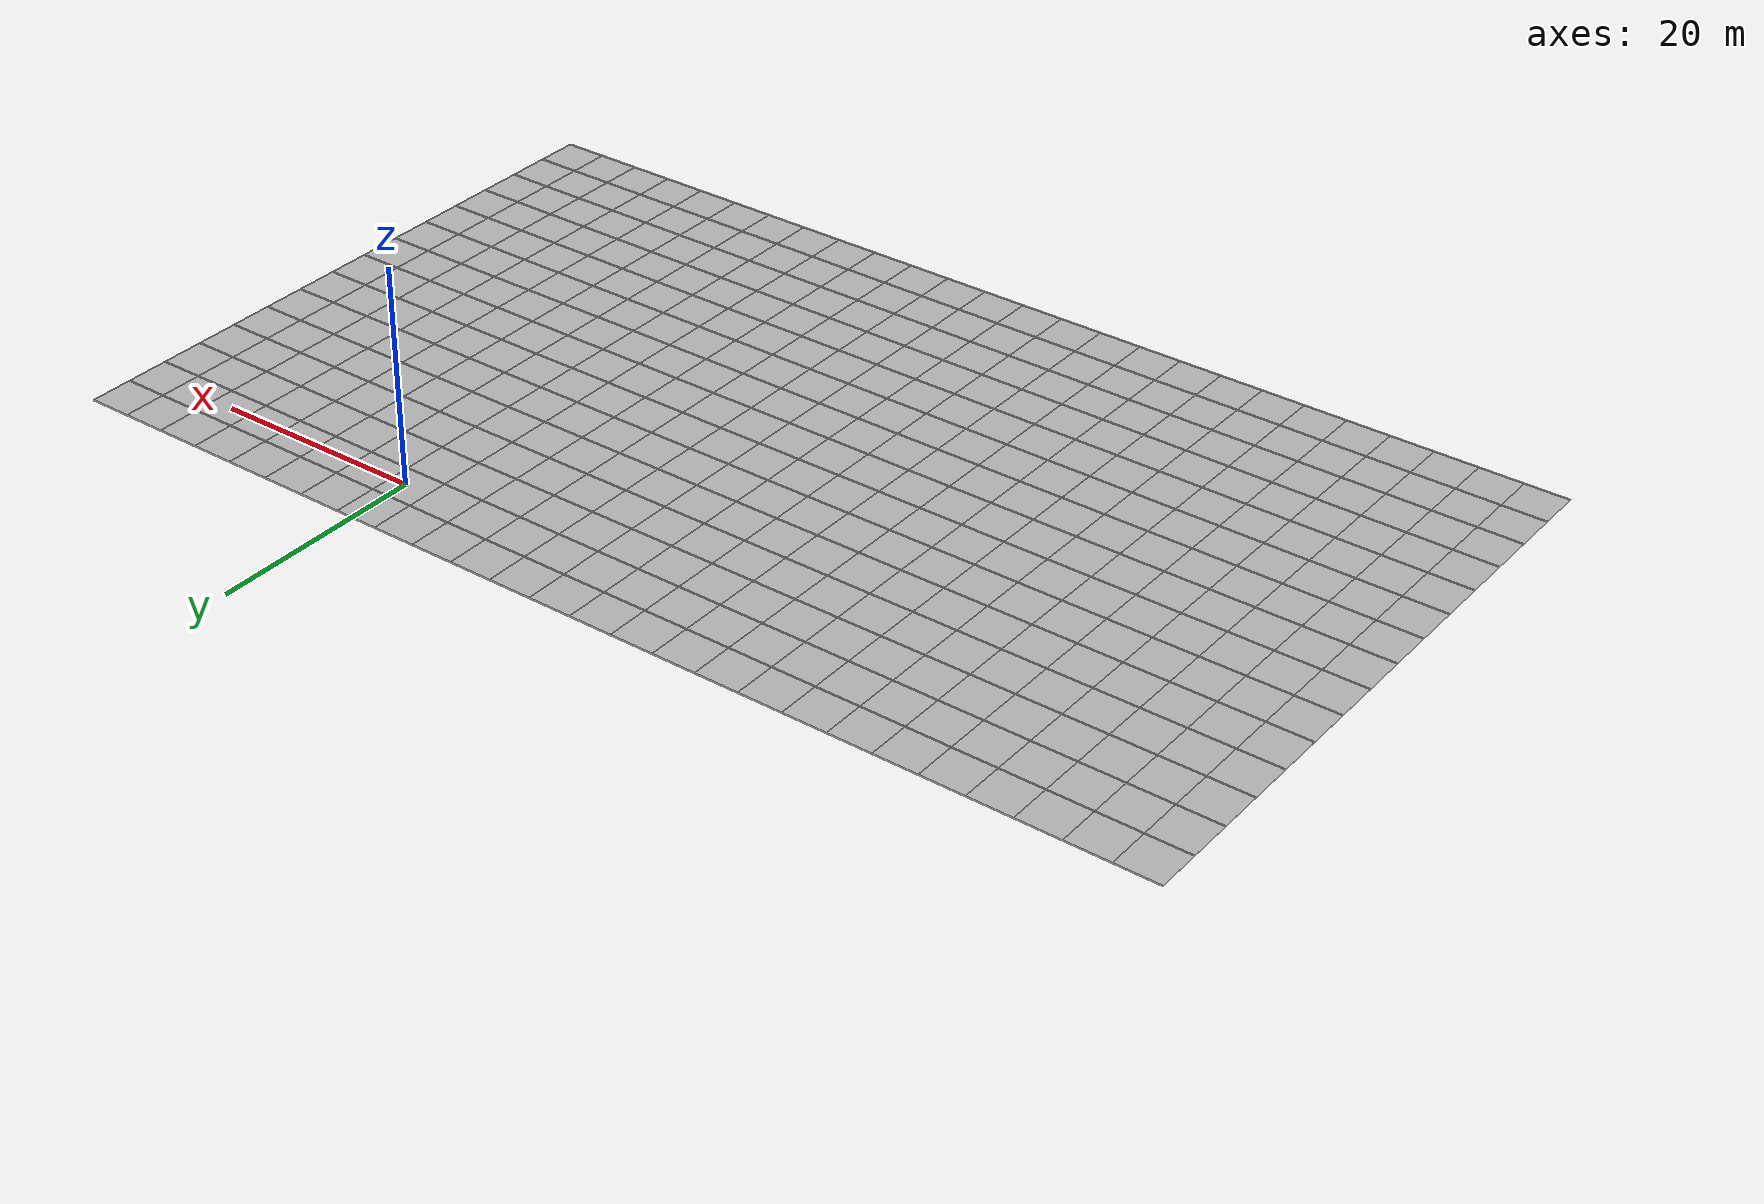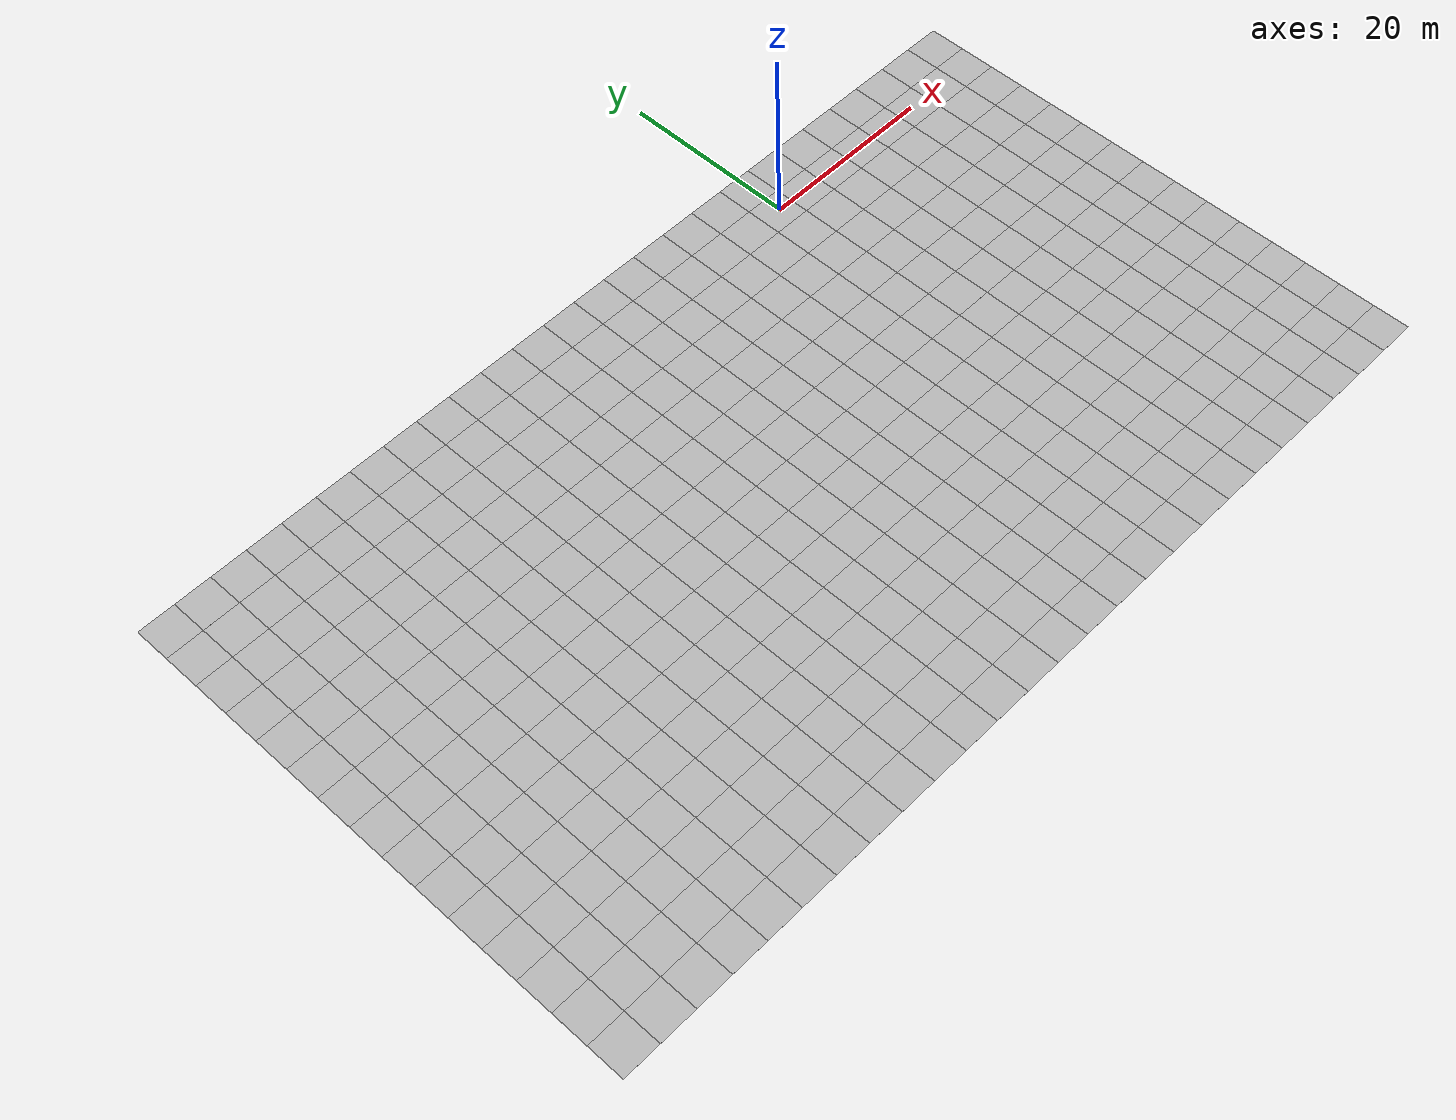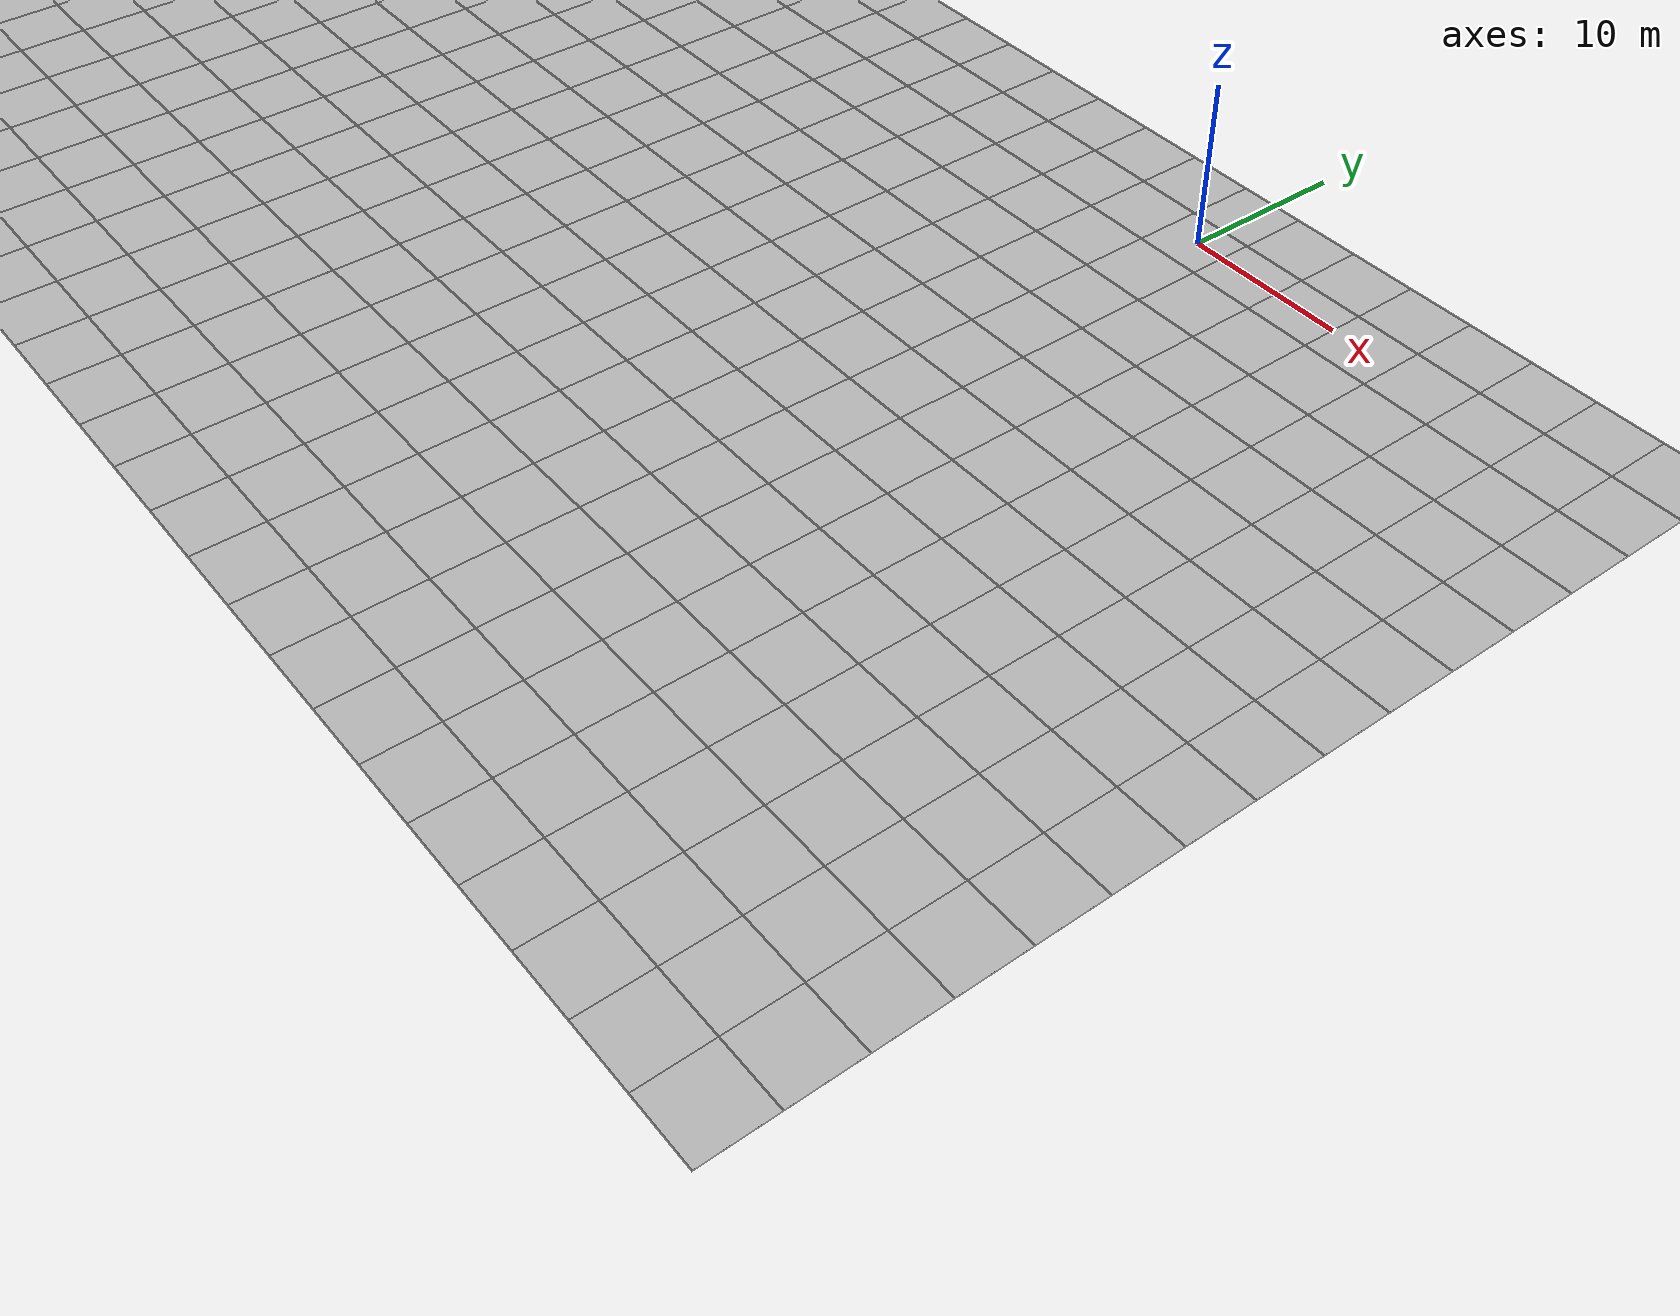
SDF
<sdf version='1.6'><world name='default'>
    <light name='sun_light' type='directional'>
      <pose frame=''>0 0 10 0 -0 0</pose>
      <diffuse>0.5 0.5 0.5 1</diffuse>
      <specular>0.1 0.1 0.1 1</specular>
      <direction>0.1 0.1 -0.9</direction>
      <attenuation>
        <range>20</range>
        <constant>0.5</constant>
        <linear>0.01</linear>
        <quadratic>0.001</quadratic>
      </attenuation>
      <cast_shadows>1</cast_shadows>
    </light>

    <model name='Tile/0-0'>
      <static>1</static>
      <link name='link'>
        <collision name='collision'>
          <geometry>
            <plane>
              <normal>0 0 1</normal>
              <size>4.096 4.096</size>
            </plane>
          </geometry>
          <surface>
            <friction>
              <ode>
                <mu>100</mu>
                <mu2>50</mu2>
              </ode>
              <torsional>
                <ode/>
              </torsional>
            </friction>
            <contact>
              <ode/>
            </contact>
            <bounce/>
          </surface>
          <max_contacts>10</max_contacts>
        </collision>
        <visual name='visual'>
          <cast_shadows>0</cast_shadows>
          <geometry>
            <plane>
              <normal>0 0 1</normal>
              <size>4.096 4.096</size>
            </plane>
          </geometry>
          <material>
            <script>
              <uri>file://materials/scripts</uri>
              <uri>file://materials/textures</uri>
              <name>Tile/91bbef66385bffcd6e7534826f7b9eb182a1b5c7d16e06f01ea59d02c9c09c4a</name>
            </script>
          </material>
        </visual>
        <self_collide>0</self_collide>
        <enable_wind>0</enable_wind>
        <kinematic>0</kinematic>
      </link>
      <pose frame=''>-74.02587300576776 -53.296103275294236 0 0 -0 0</pose>
    </model>

    <model name='Tile/0-1'>
      <static>1</static>
      <link name='link'>
        <collision name='collision'>
          <geometry>
            <plane>
              <normal>0 0 1</normal>
              <size>4.096 4.096</size>
            </plane>
          </geometry>
          <surface>
            <friction>
              <ode>
                <mu>100</mu>
                <mu2>50</mu2>
              </ode>
              <torsional>
                <ode/>
              </torsional>
            </friction>
            <contact>
              <ode/>
            </contact>
            <bounce/>
          </surface>
          <max_contacts>10</max_contacts>
        </collision>
        <visual name='visual'>
          <cast_shadows>0</cast_shadows>
          <geometry>
            <plane>
              <normal>0 0 1</normal>
              <size>4.096 4.096</size>
            </plane>
          </geometry>
          <material>
            <script>
              <uri>file://materials/scripts</uri>
              <uri>file://materials/textures</uri>
              <name>Tile/f6be2463b75e14777cc4e5b2ae3858b75d1c6eee7159da1072ce02d7b1812e81</name>
            </script>
          </material>
        </visual>
        <self_collide>0</self_collide>
        <enable_wind>0</enable_wind>
        <kinematic>0</kinematic>
      </link>
      <pose frame=''>-74.02587300576776 -49.20010327529424 0 0 -0 0</pose>
    </model>

    <model name='Tile/0-2'>
      <static>1</static>
      <link name='link'>
        <collision name='collision'>
          <geometry>
            <plane>
              <normal>0 0 1</normal>
              <size>4.096 4.096</size>
            </plane>
          </geometry>
          <surface>
            <friction>
              <ode>
                <mu>100</mu>
                <mu2>50</mu2>
              </ode>
              <torsional>
                <ode/>
              </torsional>
            </friction>
            <contact>
              <ode/>
            </contact>
            <bounce/>
          </surface>
          <max_contacts>10</max_contacts>
        </collision>
        <visual name='visual'>
          <cast_shadows>0</cast_shadows>
          <geometry>
            <plane>
              <normal>0 0 1</normal>
              <size>4.096 4.096</size>
            </plane>
          </geometry>
          <material>
            <script>
              <uri>file://materials/scripts</uri>
              <uri>file://materials/textures</uri>
              <name>Tile/42a53dfddcc55a76586b7598f74be3bd22b28463fbaf7a9b0297656511062ebe</name>
            </script>
          </material>
        </visual>
        <self_collide>0</self_collide>
        <enable_wind>0</enable_wind>
        <kinematic>0</kinematic>
      </link>
      <pose frame=''>-74.02587300576776 -45.104103275294236 0 0 -0 0</pose>
    </model>

    <model name='Tile/0-3'>
      <static>1</static>
      <link name='link'>
        <collision name='collision'>
          <geometry>
            <plane>
              <normal>0 0 1</normal>
              <size>4.096 4.096</size>
            </plane>
          </geometry>
          <surface>
            <friction>
              <ode>
                <mu>100</mu>
                <mu2>50</mu2>
              </ode>
              <torsional>
                <ode/>
              </torsional>
            </friction>
            <contact>
              <ode/>
            </contact>
            <bounce/>
          </surface>
          <max_contacts>10</max_contacts>
        </collision>
        <visual name='visual'>
          <cast_shadows>0</cast_shadows>
          <geometry>
            <plane>
              <normal>0 0 1</normal>
              <size>4.096 4.096</size>
            </plane>
          </geometry>
          <material>
            <script>
              <uri>file://materials/scripts</uri>
              <uri>file://materials/textures</uri>
              <name>Tile/5eab350b8220ac9944dbdfa4ac3288c7c17e24c3bf5df0dfcf6173d64dae00a1</name>
            </script>
          </material>
        </visual>
        <self_collide>0</self_collide>
        <enable_wind>0</enable_wind>
        <kinematic>0</kinematic>
      </link>
      <pose frame=''>-74.02587300576776 -41.00810327529424 0 0 -0 0</pose>
    </model>

    <model name='Tile/0-4'>
      <static>1</static>
      <link name='link'>
        <collision name='collision'>
          <geometry>
            <plane>
              <normal>0 0 1</normal>
              <size>4.096 4.096</size>
            </plane>
          </geometry>
          <surface>
            <friction>
              <ode>
                <mu>100</mu>
                <mu2>50</mu2>
              </ode>
              <torsional>
                <ode/>
              </torsional>
            </friction>
            <contact>
              <ode/>
            </contact>
            <bounce/>
          </surface>
          <max_contacts>10</max_contacts>
        </collision>
        <visual name='visual'>
          <cast_shadows>0</cast_shadows>
          <geometry>
            <plane>
              <normal>0 0 1</normal>
              <size>4.096 4.096</size>
            </plane>
          </geometry>
          <material>
            <script>
              <uri>file://materials/scripts</uri>
              <uri>file://materials/textures</uri>
              <name>Tile/5eab350b8220ac9944dbdfa4ac3288c7c17e24c3bf5df0dfcf6173d64dae00a1</name>
            </script>
          </material>
        </visual>
        <self_collide>0</self_collide>
        <enable_wind>0</enable_wind>
        <kinematic>0</kinematic>
      </link>
      <pose frame=''>-74.02587300576776 -36.91210327529424 0 0 -0 0</pose>
    </model>

    <model name='Tile/0-5'>
      <static>1</static>
      <link name='link'>
        <collision name='collision'>
          <geometry>
            <plane>
              <normal>0 0 1</normal>
              <size>4.096 4.096</size>
            </plane>
          </geometry>
          <surface>
            <friction>
              <ode>
                <mu>100</mu>
                <mu2>50</mu2>
              </ode>
              <torsional>
                <ode/>
              </torsional>
            </friction>
            <contact>
              <ode/>
            </contact>
            <bounce/>
          </surface>
          <max_contacts>10</max_contacts>
        </collision>
        <visual name='visual'>
          <cast_shadows>0</cast_shadows>
          <geometry>
            <plane>
              <normal>0 0 1</normal>
              <size>4.096 4.096</size>
            </plane>
          </geometry>
          <material>
            <script>
              <uri>file://materials/scripts</uri>
              <uri>file://materials/textures</uri>
              <name>Tile/5eab350b8220ac9944dbdfa4ac3288c7c17e24c3bf5df0dfcf6173d64dae00a1</name>
            </script>
          </material>
        </visual>
        <self_collide>0</self_collide>
        <enable_wind>0</enable_wind>
        <kinematic>0</kinematic>
      </link>
      <pose frame=''>-74.02587300576776 -32.81610327529424 0 0 -0 0</pose>
    </model>

    <model name='Tile/0-6'>
      <static>1</static>
      <link name='link'>
        <collision name='collision'>
          <geometry>
            <plane>
              <normal>0 0 1</normal>
              <size>4.096 4.096</size>
            </plane>
          </geometry>
          <surface>
            <friction>
              <ode>
                <mu>100</mu>
                <mu2>50</mu2>
              </ode>
              <torsional>
                <ode/>
              </torsional>
            </friction>
            <contact>
              <ode/>
            </contact>
            <bounce/>
          </surface>
          <max_contacts>10</max_contacts>
        </collision>
        <visual name='visual'>
          <cast_shadows>0</cast_shadows>
          <geometry>
            <plane>
              <normal>0 0 1</normal>
              <size>4.096 4.096</size>
            </plane>
          </geometry>
          <material>
            <script>
              <uri>file://materials/scripts</uri>
              <uri>file://materials/textures</uri>
              <name>Tile/5eab350b8220ac9944dbdfa4ac3288c7c17e24c3bf5df0dfcf6173d64dae00a1</name>
            </script>
          </material>
        </visual>
        <self_collide>0</self_collide>
        <enable_wind>0</enable_wind>
        <kinematic>0</kinematic>
      </link>
      <pose frame=''>-74.02587300576776 -28.72010327529424 0 0 -0 0</pose>
    </model>

    <model name='Tile/0-7'>
      <static>1</static>
      <link name='link'>
        <collision name='collision'>
          <geometry>
            <plane>
              <normal>0 0 1</normal>
              <size>4.096 4.096</size>
            </plane>
          </geometry>
          <surface>
            <friction>
              <ode>
                <mu>100</mu>
                <mu2>50</mu2>
              </ode>
              <torsional>
                <ode/>
              </torsional>
            </friction>
            <contact>
              <ode/>
            </contact>
            <bounce/>
          </surface>
          <max_contacts>10</max_contacts>
        </collision>
        <visual name='visual'>
          <cast_shadows>0</cast_shadows>
          <geometry>
            <plane>
              <normal>0 0 1</normal>
              <size>4.096 4.096</size>
            </plane>
          </geometry>
          <material>
            <script>
              <uri>file://materials/scripts</uri>
              <uri>file://materials/textures</uri>
              <name>Tile/5eab350b8220ac9944dbdfa4ac3288c7c17e24c3bf5df0dfcf6173d64dae00a1</name>
            </script>
          </material>
        </visual>
        <self_collide>0</self_collide>
        <enable_wind>0</enable_wind>
        <kinematic>0</kinematic>
      </link>
      <pose frame=''>-74.02587300576776 -24.62410327529424 0 0 -0 0</pose>
    </model>

    <model name='Tile/0-8'>
      <static>1</static>
      <link name='link'>
        <collision name='collision'>
          <geometry>
            <plane>
              <normal>0 0 1</normal>
              <size>4.096 4.096</size>
            </plane>
          </geometry>
          <surface>
            <friction>
              <ode>
                <mu>100</mu>
                <mu2>50</mu2>
              </ode>
              <torsional>
                <ode/>
              </torsional>
            </friction>
            <contact>
              <ode/>
            </contact>
            <bounce/>
          </surface>
          <max_contacts>10</max_contacts>
        </collision>
        <visual name='visual'>
          <cast_shadows>0</cast_shadows>
          <geometry>
            <plane>
              <normal>0 0 1</normal>
              <size>4.096 4.096</size>
            </plane>
          </geometry>
          <material>
            <script>
              <uri>file://materials/scripts</uri>
              <uri>file://materials/textures</uri>
              <name>Tile/5eab350b8220ac9944dbdfa4ac3288c7c17e24c3bf5df0dfcf6173d64dae00a1</name>
            </script>
          </material>
        </visual>
        <self_collide>0</self_collide>
        <enable_wind>0</enable_wind>
        <kinematic>0</kinematic>
      </link>
      <pose frame=''>-74.02587300576776 -20.528103275294235 0 0 -0 0</pose>
    </model>

    <model name='Tile/0-9'>
      <static>1</static>
      <link name='link'>
        <collision name='collision'>
          <geometry>
            <plane>
              <normal>0 0 1</normal>
              <size>4.096 4.096</size>
            </plane>
          </geometry>
          <surface>
            <friction>
              <ode>
                <mu>100</mu>
                <mu2>50</mu2>
              </ode>
              <torsional>
                <ode/>
              </torsional>
            </friction>
            <contact>
              <ode/>
            </contact>
            <bounce/>
          </surface>
          <max_contacts>10</max_contacts>
        </collision>
        <visual name='visual'>
          <cast_shadows>0</cast_shadows>
          <geometry>
            <plane>
              <normal>0 0 1</normal>
              <size>4.096 4.096</size>
            </plane>
          </geometry>
          <material>
            <script>
              <uri>file://materials/scripts</uri>
              <uri>file://materials/textures</uri>
              <name>Tile/5eab350b8220ac9944dbdfa4ac3288c7c17e24c3bf5df0dfcf6173d64dae00a1</name>
            </script>
          </material>
        </visual>
        <self_collide>0</self_collide>
        <enable_wind>0</enable_wind>
        <kinematic>0</kinematic>
      </link>
      <pose frame=''>-74.02587300576776 -16.43210327529424 0 0 -0 0</pose>
    </model>

    <model name='Tile/0-10'>
      <static>1</static>
      <link name='link'>
        <collision name='collision'>
          <geometry>
            <plane>
              <normal>0 0 1</normal>
              <size>4.096 4.096</size>
            </plane>
          </geometry>
          <surface>
            <friction>
              <ode>
                <mu>100</mu>
                <mu2>50</mu2>
              </ode>
              <torsional>
                <ode/>
              </torsional>
            </friction>
            <contact>
              <ode/>
            </contact>
            <bounce/>
          </surface>
          <max_contacts>10</max_contacts>
        </collision>
        <visual name='visual'>
          <cast_shadows>0</cast_shadows>
          <geometry>
            <plane>
              <normal>0 0 1</normal>
              <size>4.096 4.096</size>
            </plane>
          </geometry>
          <material>
            <script>
              <uri>file://materials/scripts</uri>
              <uri>file://materials/textures</uri>
              <name>Tile/5eab350b8220ac9944dbdfa4ac3288c7c17e24c3bf5df0dfcf6173d64dae00a1</name>
            </script>
          </material>
        </visual>
        <self_collide>0</self_collide>
        <enable_wind>0</enable_wind>
        <kinematic>0</kinematic>
      </link>
      <pose frame=''>-74.02587300576776 -12.336103275294235 0 0 -0 0</pose>
    </model>

    <model name='Tile/0-11'>
      <static>1</static>
      <link name='link'>
        <collision name='collision'>
          <geometry>
            <plane>
              <normal>0 0 1</normal>
              <size>4.096 4.096</size>
            </plane>
          </geometry>
          <surface>
            <friction>
              <ode>
                <mu>100</mu>
                <mu2>50</mu2>
              </ode>
              <torsional>
                <ode/>
              </torsional>
            </friction>
            <contact>
              <ode/>
            </contact>
            <bounce/>
          </surface>
          <max_contacts>10</max_contacts>
        </collision>
        <visual name='visual'>
          <cast_shadows>0</cast_shadows>
          <geometry>
            <plane>
              <normal>0 0 1</normal>
              <size>4.096 4.096</size>
            </plane>
          </geometry>
          <material>
            <script>
              <uri>file://materials/scripts</uri>
              <uri>file://materials/textures</uri>
              <name>Tile/5eab350b8220ac9944dbdfa4ac3288c7c17e24c3bf5df0dfcf6173d64dae00a1</name>
            </script>
          </material>
        </visual>
        <self_collide>0</self_collide>
        <enable_wind>0</enable_wind>
        <kinematic>0</kinematic>
      </link>
      <pose frame=''>-74.02587300576776 -8.240103275294238 0 0 -0 0</pose>
    </model>

    <model name='Tile/0-12'>
      <static>1</static>
      <link name='link'>
        <collision name='collision'>
          <geometry>
            <plane>
              <normal>0 0 1</normal>
              <size>4.096 4.096</size>
            </plane>
          </geometry>
          <surface>
            <friction>
              <ode>
                <mu>100</mu>
                <mu2>50</mu2>
              </ode>
              <torsional>
                <ode/>
              </torsional>
            </friction>
            <contact>
              <ode/>
            </contact>
            <bounce/>
          </surface>
          <max_contacts>10</max_contacts>
        </collision>
        <visual name='visual'>
          <cast_shadows>0</cast_shadows>
          <geometry>
            <plane>
              <normal>0 0 1</normal>
              <size>4.096 4.096</size>
            </plane>
          </geometry>
          <material>
            <script>
              <uri>file://materials/scripts</uri>
              <uri>file://materials/textures</uri>
              <name>Tile/5eab350b8220ac9944dbdfa4ac3288c7c17e24c3bf5df0dfcf6173d64dae00a1</name>
            </script>
          </material>
        </visual>
        <self_collide>0</self_collide>
        <enable_wind>0</enable_wind>
        <kinematic>0</kinematic>
      </link>
      <pose frame=''>-74.02587300576776 -4.144103275294235 0 0 -0 0</pose>
    </model>

    <model name='Tile/0-13'>
      <static>1</static>
      <link name='link'>
        <collision name='collision'>
          <geometry>
            <plane>
              <normal>0 0 1</normal>
              <size>4.096 4.096</size>
            </plane>
          </geometry>
          <surface>
            <friction>
              <ode>
                <mu>100</mu>
                <mu2>50</mu2>
              </ode>
              <torsional>
                <ode/>
              </torsional>
            </friction>
            <contact>
              <ode/>
            </contact>
            <bounce/>
          </surface>
          <max_contacts>10</max_contacts>
        </collision>
        <visual name='visual'>
          <cast_shadows>0</cast_shadows>
          <geometry>
            <plane>
              <normal>0 0 1</normal>
              <size>4.096 4.096</size>
            </plane>
          </geometry>
          <material>
            <script>
              <uri>file://materials/scripts</uri>
              <uri>file://materials/textures</uri>
              <name>Tile/5eab350b8220ac9944dbdfa4ac3288c7c17e24c3bf5df0dfcf6173d64dae00a1</name>
            </script>
          </material>
        </visual>
        <self_collide>0</self_collide>
        <enable_wind>0</enable_wind>
        <kinematic>0</kinematic>
      </link>
      <pose frame=''>-74.02587300576776 -0.0481032752942383 0 0 -0 0</pose>
    </model>

    <model name='Tile/0-14'>
      <static>1</static>
      <link name='link'>
        <collision name='collision'>
          <geometry>
            <plane>
              <normal>0 0 1</normal>
              <size>4.096 4.096</size>
            </plane>
          </geometry>
          <surface>
            <friction>
              <ode>
                <mu>100</mu>
                <mu2>50</mu2>
              </ode>
              <torsional>
                <ode/>
              </torsional>
            </friction>
            <contact>
              <ode/>
            </contact>
            <bounce/>
          </surface>
          <max_contacts>10</max_contacts>
        </collision>
        <visual name='visual'>
          <cast_shadows>0</cast_shadows>
          <geometry>
            <plane>
              <normal>0 0 1</normal>
              <size>4.096 4.096</size>
            </plane>
          </geometry>
          <material>
            <script>
              <uri>file://materials/scripts</uri>
              <uri>file://materials/textures</uri>
              <name>Tile/5eab350b8220ac9944dbdfa4ac3288c7c17e24c3bf5df0dfcf6173d64dae00a1</name>
            </script>
          </material>
        </visual>
        <self_collide>0</self_collide>
        <enable_wind>0</enable_wind>
        <kinematic>0</kinematic>
      </link>
      <pose frame=''>-74.02587300576776 4.047896724705765 0 0 -0 0</pose>
    </model>

    <model name='Tile/1-0'>
      <static>1</static>
      <link name='link'>
        <collision name='collision'>
          <geometry>
            <plane>
              <normal>0 0 1</normal>
              <size>4.096 4.096</size>
            </plane>
          </geometry>
          <surface>
            <friction>
              <ode>
                <mu>100</mu>
                <mu2>50</mu2>
              </ode>
              <torsional>
                <ode/>
              </torsional>
            </friction>
            <contact>
              <ode/>
            </contact>
            <bounce/>
          </surface>
          <max_contacts>10</max_contacts>
        </collision>
        <visual name='visual'>
          <cast_shadows>0</cast_shadows>
          <geometry>
            <plane>
              <normal>0 0 1</normal>
              <size>4.096 4.096</size>
            </plane>
          </geometry>
          <material>
            <script>
              <uri>file://materials/scripts</uri>
              <uri>file://materials/textures</uri>
              <name>Tile/85cf9636c4fd25f23c5ed7e23dcb8c5db37b7b784e670a48e8e8ba01d695afd9</name>
            </script>
          </material>
        </visual>
        <self_collide>0</self_collide>
        <enable_wind>0</enable_wind>
        <kinematic>0</kinematic>
      </link>
      <pose frame=''>-69.92987300576776 -53.296103275294236 0 0 -0 0</pose>
    </model>

    <model name='Tile/1-1'>
      <static>1</static>
      <link name='link'>
        <collision name='collision'>
          <geometry>
            <plane>
              <normal>0 0 1</normal>
              <size>4.096 4.096</size>
            </plane>
          </geometry>
          <surface>
            <friction>
              <ode>
                <mu>100</mu>
                <mu2>50</mu2>
              </ode>
              <torsional>
                <ode/>
              </torsional>
            </friction>
            <contact>
              <ode/>
            </contact>
            <bounce/>
          </surface>
          <max_contacts>10</max_contacts>
        </collision>
        <visual name='visual'>
          <cast_shadows>0</cast_shadows>
          <geometry>
            <plane>
              <normal>0 0 1</normal>
              <size>4.096 4.096</size>
            </plane>
          </geometry>
          <material>
            <script>
              <uri>file://materials/scripts</uri>
              <uri>file://materials/textures</uri>
              <name>Tile/71e0495ad46e4f884da927675b24a4ff5da9f4fa47b91c8f0d2153042dd503ff</name>
            </script>
          </material>
        </visual>
        <self_collide>0</self_collide>
        <enable_wind>0</enable_wind>
        <kinematic>0</kinematic>
      </link>
      <pose frame=''>-69.92987300576776 -49.20010327529424 0 0 -0 0</pose>
    </model>

    <model name='Tile/1-2'>
      <static>1</static>
      <link name='link'>
        <collision name='collision'>
          <geometry>
            <plane>
              <normal>0 0 1</normal>
              <size>4.096 4.096</size>
            </plane>
          </geometry>
          <surface>
            <friction>
              <ode>
                <mu>100</mu>
                <mu2>50</mu2>
              </ode>
              <torsional>
                <ode/>
              </torsional>
            </friction>
            <contact>
              <ode/>
            </contact>
            <bounce/>
          </surface>
          <max_contacts>10</max_contacts>
        </collision>
        <visual name='visual'>
          <cast_shadows>0</cast_shadows>
          <geometry>
            <plane>
              <normal>0 0 1</normal>
              <size>4.096 4.096</size>
            </plane>
          </geometry>
          <material>
            <script>
              <uri>file://materials/scripts</uri>
              <uri>file://materials/textures</uri>
              <name>Tile/56c09ec103a6fb9ecd4fa21337668b14452033cac857a082c1e33454fd6753ad</name>
            </script>
          </material>
        </visual>
        <self_collide>0</self_collide>
        <enable_wind>0</enable_wind>
        <kinematic>0</kinematic>
      </link>
      <pose frame=''>-69.92987300576776 -45.104103275294236 0 0 -0 0</pose>
    </model>

    <model name='Tile/1-3'>
      <static>1</static>
      <link name='link'>
        <collision name='collision'>
          <geometry>
            <plane>
              <normal>0 0 1</normal>
              <size>4.096 4.096</size>
            </plane>
          </geometry>
          <surface>
            <friction>
              <ode>
                <mu>100</mu>
                <mu2>50</mu2>
              </ode>
              <torsional>
                <ode/>
              </torsional>
            </friction>
            <contact>
              <ode/>
            </contact>
            <bounce/>
          </surface>
          <max_contacts>10</max_contacts>
        </collision>
        <visual name='visual'>
          <cast_shadows>0</cast_shadows>
          <geometry>
            <plane>
              <normal>0 0 1</normal>
              <size>4.096 4.096</size>
            </plane>
          </geometry>
          <material>
            <script>
              <uri>file://materials/scripts</uri>
              <uri>file://materials/textures</uri>
              <name>Tile/6461c7e409393d1a2b026cc641a53244d41885c568744f84259c804c7a289188</name>
            </script>
          </material>
        </visual>
        <self_collide>0</self_collide>
        <enable_wind>0</enable_wind>
        <kinematic>0</kinematic>
      </link>
      <pose frame=''>-69.92987300576776 -41.00810327529424 0 0 -0 0</pose>
    </model>

    <model name='Tile/1-4'>
      <static>1</static>
      <link name='link'>
        <collision name='collision'>
          <geometry>
            <plane>
              <normal>0 0 1</normal>
              <size>4.096 4.096</size>
            </plane>
          </geometry>
          <surface>
            <friction>
              <ode>
                <mu>100</mu>
                <mu2>50</mu2>
              </ode>
              <torsional>
                <ode/>
              </torsional>
            </friction>
            <contact>
              <ode/>
            </contact>
            <bounce/>
          </surface>
          <max_contacts>10</max_contacts>
        </collision>
        <visual name='visual'>
          <cast_shadows>0</cast_shadows>
          <geometry>
            <plane>
              <normal>0 0 1</normal>
              <size>4.096 4.096</size>
            </plane>
          </geometry>
          <material>
            <script>
              <uri>file://materials/scripts</uri>
              <uri>file://materials/textures</uri>
              <name>Tile/865cf95648bb6588dfb93711cde1d7424459167e80cedf71e26ebd365ffd2dea</name>
            </script>
          </material>
        </visual>
        <self_collide>0</self_collide>
        <enable_wind>0</enable_wind>
        <kinematic>0</kinematic>
      </link>
      <pose frame=''>-69.92987300576776 -36.91210327529424 0 0 -0 0</pose>
    </model>

    <model name='Tile/1-5'>
      <static>1</static>
      <link name='link'>
        <collision name='collision'>
          <geometry>
            <plane>
              <normal>0 0 1</normal>
              <size>4.096 4.096</size>
            </plane>
          </geometry>
          <surface>
            <friction>
              <ode>
                <mu>100</mu>
                <mu2>50</mu2>
              </ode>
              <torsional>
                <ode/>
              </torsional>
            </friction>
            <contact>
              <ode/>
            </contact>
            <bounce/>
          </surface>
          <max_contacts>10</max_contacts>
        </collision>
        <visual name='visual'>
          <cast_shadows>0</cast_shadows>
          <geometry>
            <plane>
              <normal>0 0 1</normal>
              <size>4.096 4.096</size>
            </plane>
          </geometry>
          <material>
            <script>
              <uri>file://materials/scripts</uri>
              <uri>file://materials/textures</uri>
              <name>Tile/bef20f82cdd3d5baccce5dc0a13bc71e3c4d3d878aea6c0974d6655b88d51603</name>
            </script>
          </material>
        </visual>
        <self_collide>0</self_collide>
        <enable_wind>0</enable_wind>
        <kinematic>0</kinematic>
      </link>
      <pose frame=''>-69.92987300576776 -32.81610327529424 0 0 -0 0</pose>
    </model>

    <model name='Tile/1-6'>
      <static>1</static>
      <link name='link'>
        <collision name='collision'>
          <geometry>
            <plane>
              <normal>0 0 1</normal>
              <size>4.096 4.096</size>
            </plane>
          </geometry>
          <surface>
            <friction>
              <ode>
                <mu>100</mu>
                <mu2>50</mu2>
              </ode>
              <torsional>
                <ode/>
              </torsional>
            </friction>
            <contact>
              <ode/>
            </contact>
            <bounce/>
          </surface>
          <max_contacts>10</max_contacts>
        </collision>
        <visual name='visual'>
          <cast_shadows>0</cast_shadows>
          <geometry>
            <plane>
              <normal>0 0 1</normal>
              <size>4.096 4.096</size>
            </plane>
          </geometry>
          <material>
            <script>
              <uri>file://materials/scripts</uri>
              <uri>file://materials/textures</uri>
              <name>Tile/5eab350b8220ac9944dbdfa4ac3288c7c17e24c3bf5df0dfcf6173d64dae00a1</name>
            </script>
          </material>
        </visual>
        <self_collide>0</self_collide>
        <enable_wind>0</enable_wind>
        <kinematic>0</kinematic>
      </link>
      <pose frame=''>-69.92987300576776 -28.72010327529424 0 0 -0 0</pose>
    </model>

    <model name='Tile/1-7'>
      <static>1</static>
      <link name='link'>
        <collision name='collision'>
          <geometry>
            <plane>
              <normal>0 0 1</normal>
              <size>4.096 4.096</size>
            </plane>
          </geometry>
          <surface>
            <friction>
              <ode>
                <mu>100</mu>
                <mu2>50</mu2>
              </ode>
              <torsional>
                <ode/>
              </torsional>
            </friction>
            <contact>
              <ode/>
            </contact>
            <bounce/>
          </surface>
          <max_contacts>10</max_contacts>
        </collision>
        <visual name='visual'>
          <cast_shadows>0</cast_shadows>
          <geometry>
            <plane>
              <normal>0 0 1</normal>
              <size>4.096 4.096</size>
            </plane>
          </geometry>
          <material>
            <script>
              <uri>file://materials/scripts</uri>
              <uri>file://materials/textures</uri>
              <name>Tile/5eab350b8220ac9944dbdfa4ac3288c7c17e24c3bf5df0dfcf6173d64dae00a1</name>
            </script>
          </material>
        </visual>
        <self_collide>0</self_collide>
        <enable_wind>0</enable_wind>
        <kinematic>0</kinematic>
      </link>
      <pose frame=''>-69.92987300576776 -24.62410327529424 0 0 -0 0</pose>
    </model>

    <model name='Tile/1-8'>
      <static>1</static>
      <link name='link'>
        <collision name='collision'>
          <geometry>
            <plane>
              <normal>0 0 1</normal>
              <size>4.096 4.096</size>
            </plane>
          </geometry>
          <surface>
            <friction>
              <ode>
                <mu>100</mu>
                <mu2>50</mu2>
              </ode>
              <torsional>
                <ode/>
              </torsional>
            </friction>
            <contact>
              <ode/>
            </contact>
            <bounce/>
          </surface>
          <max_contacts>10</max_contacts>
        </collision>
        <visual name='visual'>
          <cast_shadows>0</cast_shadows>
          <geometry>
            <plane>
              <normal>0 0 1</normal>
              <size>4.096 4.096</size>
            </plane>
          </geometry>
          <material>
            <script>
              <uri>file://materials/scripts</uri>
              <uri>file://materials/textures</uri>
              <name>Tile/5eab350b8220ac9944dbdfa4ac3288c7c17e24c3bf5df0dfcf6173d64dae00a1</name>
            </script>
          </material>
        </visual>
        <self_collide>0</self_collide>
        <enable_wind>0</enable_wind>
        <kinematic>0</kinematic>
      </link>
      <pose frame=''>-69.92987300576776 -20.528103275294235 0 0 -0 0</pose>
    </model>

    <model name='Tile/1-9'>
      <static>1</static>
      <link name='link'>
        <collision name='collision'>
          <geometry>
            <plane>
              <normal>0 0 1</normal>
              <size>4.096 4.096</size>
            </plane>
          </geometry>
          <surface>
            <friction>
              <ode>
                <mu>100</mu>
                <mu2>50</mu2>
              </ode>
              <torsional>
                <ode/>
              </torsional>
            </friction>
            <contact>
              <ode/>
            </contact>
            <bounce/>
          </surface>
          <max_contacts>10</max_contacts>
        </collision>
        <visual name='visual'>
          <cast_shadows>0</cast_shadows>
          <geometry>
            <plane>
              <normal>0 0 1</normal>
              <size>4.096 4.096</size>
            </plane>
          </geometry>
          <material>
            <script>
              <uri>file://materials/scripts</uri>
              <uri>file://materials/textures</uri>
              <name>Tile/5eab350b8220ac9944dbdfa4ac3288c7c17e24c3bf5df0dfcf6173d64dae00a1</name>
            </script>
          </material>
        </visual>
        <self_collide>0</self_collide>
        <enable_wind>0</enable_wind>
        <kinematic>0</kinematic>
      </link>
      <pose frame=''>-69.92987300576776 -16.43210327529424 0 0 -0 0</pose>
    </model>

    <model name='Tile/1-10'>
      <static>1</static>
      <link name='link'>
        <collision name='collision'>
          <geometry>
            <plane>
              <normal>0 0 1</normal>
              <size>4.096 4.096</size>
            </plane>
          </geometry>
          <surface>
            <friction>
              <ode>
                <mu>100</mu>
                <mu2>50</mu2>
              </ode>
              <torsional>
                <ode/>
              </torsional>
            </friction>
            <contact>
              <ode/>
            </contact>
            <bounce/>
          </surface>
          <max_contacts>10</max_contacts>
        </collision>
        <visual name='visual'>
          <cast_shadows>0</cast_shadows>
          <geometry>
            <plane>
              <normal>0 0 1</normal>
              <size>4.096 4.096</size>
            </plane>
          </geometry>
          <material>
            <script>
              <uri>file://materials/scripts</uri>
              <uri>file://materials/textures</uri>
              <name>Tile/5eab350b8220ac9944dbdfa4ac3288c7c17e24c3bf5df0dfcf6173d64dae00a1</name>
            </script>
          </material>
        </visual>
        <self_collide>0</self_collide>
        <enable_wind>0</enable_wind>
        <kinematic>0</kinematic>
      </link>
      <pose frame=''>-69.92987300576776 -12.336103275294235 0 0 -0 0</pose>
    </model>

    <model name='Tile/1-11'>
      <static>1</static>
      <link name='link'>
        <collision name='collision'>
          <geometry>
            <plane>
              <normal>0 0 1</normal>
              <size>4.096 4.096</size>
            </plane>
          </geometry>
          <surface>
            <friction>
              <ode>
                <mu>100</mu>
                <mu2>50</mu2>
              </ode>
              <torsional>
                <ode/>
              </torsional>
            </friction>
            <contact>
              <ode/>
            </contact>
            <bounce/>
          </surface>
          <max_contacts>10</max_contacts>
        </collision>
        <visual name='visual'>
          <cast_shadows>0</cast_shadows>
          <geometry>
            <plane>
              <normal>0 0 1</normal>
              <size>4.096 4.096</size>
            </plane>
          </geometry>
          <material>
            <script>
              <uri>file://materials/scripts</uri>
              <uri>file://materials/textures</uri>
              <name>Tile/5eab350b8220ac9944dbdfa4ac3288c7c17e24c3bf5df0dfcf6173d64dae00a1</name>
            </script>
          </material>
        </visual>
        <self_collide>0</self_collide>
        <enable_wind>0</enable_wind>
        <kinematic>0</kinematic>
      </link>
      <pose frame=''>-69.92987300576776 -8.240103275294238 0 0 -0 0</pose>
    </model>

    <model name='Tile/1-12'>
      <static>1</static>
      <link name='link'>
        <collision name='collision'>
          <geometry>
            <plane>
              <normal>0 0 1</normal>
              <size>4.096 4.096</size>
            </plane>
          </geometry>
          <surface>
            <friction>
              <ode>
                <mu>100</mu>
                <mu2>50</mu2>
              </ode>
              <torsional>
                <ode/>
              </torsional>
            </friction>
            <contact>
              <ode/>
            </contact>
            <bounce/>
          </surface>
          <max_contacts>10</max_contacts>
        </collision>
        <visual name='visual'>
          <cast_shadows>0</cast_shadows>
          <geometry>
            <plane>
              <normal>0 0 1</normal>
              <size>4.096 4.096</size>
            </plane>
          </geometry>
          <material>
            <script>
              <uri>file://materials/scripts</uri>
              <uri>file://materials/textures</uri>
              <name>Tile/5eab350b8220ac9944dbdfa4ac3288c7c17e24c3bf5df0dfcf6173d64dae00a1</name>
            </script>
          </material>
        </visual>
        <self_collide>0</self_collide>
        <enable_wind>0</enable_wind>
        <kinematic>0</kinematic>
      </link>
      <pose frame=''>-69.92987300576776 -4.144103275294235 0 0 -0 0</pose>
    </model>

    <model name='Tile/1-13'>
      <static>1</static>
      <link name='link'>
        <collision name='collision'>
          <geometry>
            <plane>
              <normal>0 0 1</normal>
              <size>4.096 4.096</size>
            </plane>
          </geometry>
          <surface>
            <friction>
              <ode>
                <mu>100</mu>
                <mu2>50</mu2>
              </ode>
              <torsional>
                <ode/>
              </torsional>
            </friction>
            <contact>
              <ode/>
            </contact>
            <bounce/>
          </surface>
          <max_contacts>10</max_contacts>
        </collision>
        <visual name='visual'>
          <cast_shadows>0</cast_shadows>
          <geometry>
            <plane>
              <normal>0 0 1</normal>
              <size>4.096 4.096</size>
            </plane>
          </geometry>
          <material>
            <script>
              <uri>file://materials/scripts</uri>
              <uri>file://materials/textures</uri>
              <name>Tile/5eab350b8220ac9944dbdfa4ac3288c7c17e24c3bf5df0dfcf6173d64dae00a1</name>
            </script>
          </material>
        </visual>
        <self_collide>0</self_collide>
        <enable_wind>0</enable_wind>
        <kinematic>0</kinematic>
      </link>
      <pose frame=''>-69.92987300576776 -0.0481032752942383 0 0 -0 0</pose>
    </model>

    <model name='Tile/1-14'>
      <static>1</static>
      <link name='link'>
        <collision name='collision'>
          <geometry>
            <plane>
              <normal>0 0 1</normal>
              <size>4.096 4.096</size>
            </plane>
          </geometry>
          <surface>
            <friction>
              <ode>
                <mu>100</mu>
                <mu2>50</mu2>
              </ode>
              <torsional>
                <ode/>
              </torsional>
            </friction>
            <contact>
              <ode/>
            </contact>
            <bounce/>
          </surface>
          <max_contacts>10</max_contacts>
        </collision>
        <visual name='visual'>
          <cast_shadows>0</cast_shadows>
          <geometry>
            <plane>
              <normal>0 0 1</normal>
              <size>4.096 4.096</size>
            </plane>
          </geometry>
          <material>
            <script>
              <uri>file://materials/scripts</uri>
              <uri>file://materials/textures</uri>
              <name>Tile/5eab350b8220ac9944dbdfa4ac3288c7c17e24c3bf5df0dfcf6173d64dae00a1</name>
            </script>
          </material>
        </visual>
        <self_collide>0</self_collide>
        <enable_wind>0</enable_wind>
        <kinematic>0</kinematic>
      </link>
      <pose frame=''>-69.92987300576776 4.047896724705765 0 0 -0 0</pose>
    </model>

    <model name='Tile/2-0'>
      <static>1</static>
      <link name='link'>
        <collision name='collision'>
          <geometry>
            <plane>
              <normal>0 0 1</normal>
              <size>4.096 4.096</size>
            </plane>
          </geometry>
          <surface>
            <friction>
              <ode>
                <mu>100</mu>
                <mu2>50</mu2>
              </ode>
              <torsional>
                <ode/>
              </torsional>
            </friction>
            <contact>
              <ode/>
            </contact>
            <bounce/>
          </surface>
          <max_contacts>10</max_contacts>
        </collision>
        <visual name='visual'>
          <cast_shadows>0</cast_shadows>
          <geometry>
            <plane>
              <normal>0 0 1</normal>
              <size>4.096 4.096</size>
            </plane>
          </geometry>
          <material>
            <script>
              <uri>file://materials/scripts</uri>
              <uri>file://materials/textures</uri>
              <name>Tile/5ad7c795063515974ad52603c53f06c1ca31bfb4a94cc0d64dc59daa88b06eec</name>
            </script>
          </material>
        </visual>
        <self_collide>0</self_collide>
        <enable_wind>0</enable_wind>
        <kinematic>0</kinematic>
      </link>
      <pose frame=''>-65.83387300576777 -53.296103275294236 0 0 -0 0</pose>
    </model>

    <model name='Tile/2-1'>
      <static>1</static>
      <link name='link'>
        <collision name='collision'>
          <geometry>
            <plane>
              <normal>0 0 1</normal>
              <size>4.096 4.096</size>
            </plane>
          </geometry>
          <surface>
            <friction>
              <ode>
                <mu>100</mu>
                <mu2>50</mu2>
              </ode>
              <torsional>
                <ode/>
              </torsional>
            </friction>
            <contact>
              <ode/>
            </contact>
            <bounce/>
          </surface>
          <max_contacts>10</max_contacts>
        </collision>
        <visual name='visual'>
          <cast_shadows>0</cast_shadows>
          <geometry>
            <plane>
              <normal>0 0 1</normal>
              <size>4.096 4.096</size>
            </plane>
          </geometry>
          <material>
            <script>
              <uri>file://materials/scripts</uri>
              <uri>file://materials/textures</uri>
              <name>Tile/bf576dd2feaed85103a7bd3a7d0d08cfacbd5e82d0cfd357ab917c69db809932</name>
            </script>
          </material>
        </visual>
        <self_collide>0</self_collide>
        <enable_wind>0</enable_wind>
        <kinematic>0</kinematic>
      </link>
      <pose frame=''>-65.83387300576777 -49.20010327529424 0 0 -0 0</pose>
    </model>

    <model name='Tile/2-2'>
      <static>1</static>
      <link name='link'>
        <collision name='collision'>
          <geometry>
            <plane>
              <normal>0 0 1</normal>
              <size>4.096 4.096</size>
            </plane>
          </geometry>
          <surface>
            <friction>
              <ode>
                <mu>100</mu>
                <mu2>50</mu2>
              </ode>
              <torsional>
                <ode/>
              </torsional>
            </friction>
            <contact>
              <ode/>
            </contact>
            <bounce/>
          </surface>
          <max_contacts>10</max_contacts>
        </collision>
        <visual name='visual'>
          <cast_shadows>0</cast_shadows>
          <geometry>
            <plane>
              <normal>0 0 1</normal>
              <size>4.096 4.096</size>
            </plane>
          </geometry>
          <material>
            <script>
              <uri>file://materials/scripts</uri>
              <uri>file://materials/textures</uri>
              <name>Tile/5eab350b8220ac9944dbdfa4ac3288c7c17e24c3bf5df0dfcf6173d64dae00a1</name>
            </script>
          </material>
        </visual>
        <self_collide>0</self_collide>
        <enable_wind>0</enable_wind>
        <kinematic>0</kinematic>
      </link>
      <pose frame=''>-65.83387300576777 -45.104103275294236 0 0 -0 0</pose>
    </model>

    <model name='Tile/2-3'>
      <static>1</static>
      <link name='link'>
        <collision name='collision'>
          <geometry>
            <plane>
              <normal>0 0 1</normal>
              <size>4.096 4.096</size>
            </plane>
          </geometry>
          <surface>
            <friction>
              <ode>
                <mu>100</mu>
                <mu2>50</mu2>
              </ode>
              <torsional>
                <ode/>
              </torsional>
            </friction>
            <contact>
              <ode/>
            </contact>
            <bounce/>
          </surface>
          <max_contacts>10</max_contacts>
        </collision>
        <visual name='visual'>
          <cast_shadows>0</cast_shadows>
          <geometry>
            <plane>
              <normal>0 0 1</normal>
              <size>4.096 4.096</size>
            </plane>
          </geometry>
          <material>
            <script>
              <uri>file://materials/scripts</uri>
              <uri>file://materials/textures</uri>
              <name>Tile/5eab350b8220ac9944dbdfa4ac3288c7c17e24c3bf5df0dfcf6173d64dae00a1</name>
            </script>
          </material>
        </visual>
        <self_collide>0</self_collide>
        <enable_wind>0</enable_wind>
        <kinematic>0</kinematic>
      </link>
      <pose frame=''>-65.83387300576777 -41.00810327529424 0 0 -0 0</pose>
    </model>

    <model name='Tile/2-4'>
      <static>1</static>
      <link name='link'>
        <collision name='collision'>
          <geometry>
            <plane>
              <normal>0 0 1</normal>
              <size>4.096 4.096</size>
            </plane>
          </geometry>
          <surface>
            <friction>
              <ode>
                <mu>100</mu>
                <mu2>50</mu2>
              </ode>
              <torsional>
                <ode/>
              </torsional>
            </friction>
            <contact>
              <ode/>
            </contact>
            <bounce/>
          </surface>
          <max_contacts>10</max_contacts>
        </collision>
        <visual name='visual'>
          <cast_shadows>0</cast_shadows>
          <geometry>
            <plane>
              <normal>0 0 1</normal>
              <size>4.096 4.096</size>
            </plane>
          </geometry>
          <material>
            <script>
              <uri>file://materials/scripts</uri>
              <uri>file://materials/textures</uri>
              <name>Tile/d281935b0ae849b47b935804b83b69b631d8f1f02e111909190aa42ee35be3af</name>
            </script>
          </material>
        </visual>
        <self_collide>0</self_collide>
        <enable_wind>0</enable_wind>
        <kinematic>0</kinematic>
      </link>
      <pose frame=''>-65.83387300576777 -36.91210327529424 0 0 -0 0</pose>
    </model>

    <model name='Tile/2-5'>
      <static>1</static>
      <link name='link'>
        <collision name='collision'>
          <geometry>
            <plane>
              <normal>0 0 1</normal>
              <size>4.096 4.096</size>
            </plane>
          </geometry>
          <surface>
            <friction>
              <ode>
                <mu>100</mu>
                <mu2>50</mu2>
              </ode>
              <torsional>
                <ode/>
              </torsional>
            </friction>
            <contact>
              <ode/>
            </contact>
            <bounce/>
          </surface>
          <max_contacts>10</max_contacts>
        </collision>
        <visual name='visual'>
          <cast_shadows>0</cast_shadows>
          <geometry>
            <plane>
              <normal>0 0 1</normal>
              <size>4.096 4.096</size>
            </plane>
          </geometry>
          <material>
            <script>
              <uri>file://materials/scripts</uri>
              <uri>file://materials/textures</uri>
              <name>Tile/518b6961bb547202fd9efee7bd81965970aacfd3aa863cbcab949c5f7947569b</name>
            </script>
          </material>
        </visual>
        <self_collide>0</self_collide>
        <enable_wind>0</enable_wind>
        <kinematic>0</kinematic>
      </link>
      <pose frame=''>-65.83387300576777 -32.81610327529424 0 0 -0 0</pose>
    </model>

    <model name='Tile/2-6'>
      <static>1</static>
      <link name='link'>
        <collision name='collision'>
          <geometry>
            <plane>
              <normal>0 0 1</normal>
              <size>4.096 4.096</size>
            </plane>
          </geometry>
          <surface>
            <friction>
              <ode>
                <mu>100</mu>
                <mu2>50</mu2>
              </ode>
              <torsional>
                <ode/>
              </torsional>
            </friction>
            <contact>
              <ode/>
            </contact>
            <bounce/>
          </surface>
          <max_contacts>10</max_contacts>
        </collision>
        <visual name='visual'>
          <cast_shadows>0</cast_shadows>
          <geometry>
            <plane>
              <normal>0 0 1</normal>
              <size>4.096 4.096</size>
            </plane>
          </geometry>
          <material>
            <script>
              <uri>file://materials/scripts</uri>
              <uri>file://materials/textures</uri>
              <name>Tile/5cfcbd6f833b705bda2c2ba7dccb202738695a96687d2659ea9c212d299d7115</name>
            </script>
          </material>
        </visual>
        <self_collide>0</self_collide>
        <enable_wind>0</enable_wind>
        <kinematic>0</kinematic>
      </link>
      <pose frame=''>-65.83387300576777 -28.72010327529424 0 0 -0 0</pose>
    </model>

    <model name='Tile/2-7'>
      <static>1</static>
      <link name='link'>
        <collision name='collision'>
          <geometry>
            <plane>
              <normal>0 0 1</normal>
              <size>4.096 4.096</size>
            </plane>
          </geometry>
          <surface>
            <friction>
              <ode>
                <mu>100</mu>
                <mu2>50</mu2>
              </ode>
              <torsional>
                <ode/>
              </torsional>
            </friction>
            <contact>
              <ode/>
            </contact>
            <bounce/>
          </surface>
          <max_contacts>10</max_contacts>
        </collision>
        <visual name='visual'>
          <cast_shadows>0</cast_shadows>
          <geometry>
            <plane>
              <normal>0 0 1</normal>
              <size>4.096 4.096</size>
            </plane>
          </geometry>
          <material>
            <script>
              <uri>file://materials/scripts</uri>
              <uri>file://materials/textures</uri>
              <name>Tile/245a53eaf3db409cd6b239ef844614c21767c09347fcd66d938a2f493ae21ebe</name>
            </script>
          </material>
        </visual>
        <self_collide>0</self_collide>
        <enable_wind>0</enable_wind>
        <kinematic>0</kinematic>
      </link>
      <pose frame=''>-65.83387300576777 -24.62410327529424 0 0 -0 0</pose>
    </model>

    <model name='Tile/2-8'>
      <static>1</static>
      <link name='link'>
        <collision name='collision'>
          <geometry>
            <plane>
              <normal>0 0 1</normal>
              <size>4.096 4.096</size>
            </plane>
          </geometry>
          <surface>
            <friction>
              <ode>
                <mu>100</mu>
                <mu2>50</mu2>
              </ode>
              <torsional>
                <ode/>
              </torsional>
            </friction>
            <contact>
              <ode/>
            </contact>
            <bounce/>
          </surface>
          <max_contacts>10</max_contacts>
        </collision>
        <visual name='visual'>
          <cast_shadows>0</cast_shadows>
          <geometry>
            <plane>
              <normal>0 0 1</normal>
              <size>4.096 4.096</size>
            </plane>
          </geometry>
          <material>
            <script>
              <uri>file://materials/scripts</uri>
              <uri>file://materials/textures</uri>
              <name>Tile/5eab350b8220ac9944dbdfa4ac3288c7c17e24c3bf5df0dfcf6173d64dae00a1</name>
            </script>
          </material>
        </visual>
        <self_collide>0</self_collide>
        <enable_wind>0</enable_wind>
        <kinematic>0</kinematic>
      </link>
      <pose frame=''>-65.83387300576777 -20.528103275294235 0 0 -0 0</pose>
    </model>

    <model name='Tile/2-9'>
      <static>1</static>
      <link name='link'>
        <collision name='collision'>
          <geometry>
            <plane>
              <normal>0 0 1</normal>
              <size>4.096 4.096</size>
            </plane>
          </geometry>
          <surface>
            <friction>
              <ode>
                <mu>100</mu>
                <mu2>50</mu2>
              </ode>
              <torsional>
                <ode/>
              </torsional>
            </friction>
            <contact>
              <ode/>
            </contact>
            <bounce/>
          </surface>
          <max_contacts>10</max_contacts>
        </collision>
        <visual name='visual'>
          <cast_shadows>0</cast_shadows>
          <geometry>
            <plane>
              <normal>0 0 1</normal>
              <size>4.096 4.096</size>
            </plane>
          </geometry>
          <material>
            <script>
              <uri>file://materials/scripts</uri>
              <uri>file://materials/textures</uri>
              <name>Tile/5eab350b8220ac9944dbdfa4ac3288c7c17e24c3bf5df0dfcf6173d64dae00a1</name>
            </script>
          </material>
        </visual>
        <self_collide>0</self_collide>
        <enable_wind>0</enable_wind>
        <kinematic>0</kinematic>
      </link>
      <pose frame=''>-65.83387300576777 -16.43210327529424 0 0 -0 0</pose>
    </model>

    <model name='Tile/2-10'>
      <static>1</static>
      <link name='link'>
        <collision name='collision'>
          <geometry>
            <plane>
              <normal>0 0 1</normal>
              <size>4.096 4.096</size>
            </plane>
          </geometry>
          <surface>
            <friction>
              <ode>
                <mu>100</mu>
                <mu2>50</mu2>
              </ode>
              <torsional>
                <ode/>
              </torsional>
            </friction>
            <contact>
              <ode/>
            </contact>
            <bounce/>
          </surface>
          <max_contacts>10</max_contacts>
        </collision>
        <visual name='visual'>
          <cast_shadows>0</cast_shadows>
          <geometry>
            <plane>
              <normal>0 0 1</normal>
              <size>4.096 4.096</size>
            </plane>
          </geometry>
          <material>
            <script>
              <uri>file://materials/scripts</uri>
              <uri>file://materials/textures</uri>
              <name>Tile/5eab350b8220ac9944dbdfa4ac3288c7c17e24c3bf5df0dfcf6173d64dae00a1</name>
            </script>
          </material>
        </visual>
        <self_collide>0</self_collide>
        <enable_wind>0</enable_wind>
        <kinematic>0</kinematic>
      </link>
      <pose frame=''>-65.83387300576777 -12.336103275294235 0 0 -0 0</pose>
    </model>

    <model name='Tile/2-11'>
      <static>1</static>
      <link name='link'>
        <collision name='collision'>
          <geometry>
            <plane>
              <normal>0 0 1</normal>
              <size>4.096 4.096</size>
            </plane>
          </geometry>
          <surface>
            <friction>
              <ode>
                <mu>100</mu>
                <mu2>50</mu2>
              </ode>
              <torsional>
                <ode/>
              </torsional>
            </friction>
            <contact>
              <ode/>
            </contact>
            <bounce/>
          </surface>
          <max_contacts>10</max_contacts>
        </collision>
        <visual name='visual'>
          <cast_shadows>0</cast_shadows>
          <geometry>
            <plane>
              <normal>0 0 1</normal>
              <size>4.096 4.096</size>
            </plane>
          </geometry>
          <material>
            <script>
              <uri>file://materials/scripts</uri>
              <uri>file://materials/textures</uri>
              <name>Tile/5eab350b8220ac9944dbdfa4ac3288c7c17e24c3bf5df0dfcf6173d64dae00a1</name>
            </script>
          </material>
        </visual>
        <self_collide>0</self_collide>
        <enable_wind>0</enable_wind>
        <kinematic>0</kinematic>
      </link>
      <pose frame=''>-65.83387300576777 -8.240103275294238 0 0 -0 0</pose>
    </model>

    <model name='Tile/2-12'>
      <static>1</static>
      <link name='link'>
        <collision name='collision'>
          <geometry>
            <plane>
              <normal>0 0 1</normal>
              <size>4.096 4.096</size>
            </plane>
          </geometry>
          <surface>
            <friction>
              <ode>
                <mu>100</mu>
                <mu2>50</mu2>
              </ode>
              <torsional>
                <ode/>
              </torsional>
            </friction>
            <contact>
              <ode/>
            </contact>
            <bounce/>
          </surface>
          <max_contacts>10</max_contacts>
        </collision>
        <visual name='visual'>
          <cast_shadows>0</cast_shadows>
          <geometry>
            <plane>
              <normal>0 0 1</normal>
              <size>4.096 4.096</size>
            </plane>
          </geometry>
          <material>
            <script>
              <uri>file://materials/scripts</uri>
              <uri>file://materials/textures</uri>
              <name>Tile/5eab350b8220ac9944dbdfa4ac3288c7c17e24c3bf5df0dfcf6173d64dae00a1</name>
            </script>
          </material>
        </visual>
        <self_collide>0</self_collide>
        <enable_wind>0</enable_wind>
        <kinematic>0</kinematic>
      </link>
      <pose frame=''>-65.83387300576777 -4.144103275294235 0 0 -0 0</pose>
    </model>

    <model name='Tile/2-13'>
      <static>1</static>
      <link name='link'>
        <collision name='collision'>
          <geometry>
            <plane>
              <normal>0 0 1</normal>
              <size>4.096 4.096</size>
            </plane>
          </geometry>
          <surface>
            <friction>
              <ode>
                <mu>100</mu>
                <mu2>50</mu2>
              </ode>
              <torsional>
                <ode/>
              </torsional>
            </friction>
            <contact>
              <ode/>
            </contact>
            <bounce/>
          </surface>
          <max_contacts>10</max_contacts>
        </collision>
        <visual name='visual'>
          <cast_shadows>0</cast_shadows>
          <geometry>
            <plane>
              <normal>0 0 1</normal>
              <size>4.096 4.096</size>
            </plane>
          </geometry>
          <material>
            <script>
              <uri>file://materials/scripts</uri>
              <uri>file://materials/textures</uri>
              <name>Tile/5eab350b8220ac9944dbdfa4ac3288c7c17e24c3bf5df0dfcf6173d64dae00a1</name>
            </script>
          </material>
        </visual>
        <self_collide>0</self_collide>
        <enable_wind>0</enable_wind>
        <kinematic>0</kinematic>
      </link>
      <pose frame=''>-65.83387300576777 -0.0481032752942383 0 0 -0 0</pose>
    </model>

    <model name='Tile/2-14'>
      <static>1</static>
      <link name='link'>
        <collision name='collision'>
          <geometry>
            <plane>
              <normal>0 0 1</normal>
              <size>4.096 4.096</size>
            </plane>
          </geometry>
          <surface>
            <friction>
              <ode>
                <mu>100</mu>
                <mu2>50</mu2>
              </ode>
              <torsional>
                <ode/>
              </torsional>
            </friction>
            <contact>
              <ode/>
            </contact>
            <bounce/>
          </surface>
          <max_contacts>10</max_contacts>
        </collision>
        <visual name='visual'>
          <cast_shadows>0</cast_shadows>
          <geometry>
            <plane>
              <normal>0 0 1</normal>
              <size>4.096 4.096</size>
            </plane>
          </geometry>
          <material>
            <script>
              <uri>file://materials/scripts</uri>
              <uri>file://materials/textures</uri>
              <name>Tile/5eab350b8220ac9944dbdfa4ac3288c7c17e24c3bf5df0dfcf6173d64dae00a1</name>
            </script>
          </material>
        </visual>
        <self_collide>0</self_collide>
        <enable_wind>0</enable_wind>
        <kinematic>0</kinematic>
      </link>
      <pose frame=''>-65.83387300576777 4.047896724705765 0 0 -0 0</pose>
    </model>

    <model name='Tile/3-0'>
      <static>1</static>
      <link name='link'>
        <collision name='collision'>
          <geometry>
            <plane>
              <normal>0 0 1</normal>
              <size>4.096 4.096</size>
            </plane>
          </geometry>
          <surface>
            <friction>
              <ode>
                <mu>100</mu>
                <mu2>50</mu2>
              </ode>
              <torsional>
                <ode/>
              </torsional>
            </friction>
            <contact>
              <ode/>
            </contact>
            <bounce/>
          </surface>
          <max_contacts>10</max_contacts>
        </collision>
        <visual name='visual'>
          <cast_shadows>0</cast_shadows>
          <geometry>
            <plane>
              <normal>0 0 1</normal>
              <size>4.096 4.096</size>
            </plane>
          </geometry>
          <material>
            <script>
              <uri>file://materials/scripts</uri>
              <uri>file://materials/textures</uri>
              <name>Tile/757ae10223dfe3337fcc6dff5f885bac84c03d2674b995b4953eae11e924ae84</name>
            </script>
          </material>
        </visual>
        <self_collide>0</self_collide>
        <enable_wind>0</enable_wind>
        <kinematic>0</kinematic>
      </link>
      <pose frame=''>-61.73787300576777 -53.296103275294236 0 0 -0 0</pose>
    </model>

    <model name='Tile/3-1'>
      <static>1</static>
      <link name='link'>
        <collision name='collision'>
          <geometry>
            <plane>
              <normal>0 0 1</normal>
              <size>4.096 4.096</size>
            </plane>
          </geometry>
          <surface>
            <friction>
              <ode>
                <mu>100</mu>
                <mu2>50</mu2>
              </ode>
              <torsional>
                <ode/>
              </torsional>
            </friction>
            <contact>
              <ode/>
            </contact>
            <bounce/>
          </surface>
          <max_contacts>10</max_contacts>
        </collision>
        <visual name='visual'>
          <cast_shadows>0</cast_shadows>
          <geometry>
            <plane>
              <normal>0 0 1</normal>
              <size>4.096 4.096</size>
            </plane>
          </geometry>
          <material>
            <script>
              <uri>file://materials/scripts</uri>
              <uri>file://materials/textures</uri>
              <name>Tile/b74bf2d34422e6adc22ef54a7d9cbb8ba851e2c86db14dbf9321a40adfb7bd5a</name>
            </script>
          </material>
        </visual>
        <self_collide>0</self_collide>
        <enable_wind>0</enable_wind>
        <kinematic>0</kinematic>
      </link>
      <pose frame=''>-61.73787300576777 -49.20010327529424 0 0 -0 0</pose>
    </model>

    <model name='Tile/3-2'>
      <static>1</static>
      <link name='link'>
        <collision name='collision'>
          <geometry>
            <plane>
              <normal>0 0 1</normal>
              <size>4.096 4.096</size>
            </plane>
          </geometry>
          <surface>
            <friction>
              <ode>
                <mu>100</mu>
                <mu2>50</mu2>
              </ode>
              <torsional>
                <ode/>
              </torsional>
            </friction>
            <contact>
              <ode/>
            </contact>
            <bounce/>
          </surface>
          <max_contacts>10</max_contacts>
        </collision>
        <visual name='visual'>
          <cast_shadows>0</cast_shadows>
          <geometry>
            <plane>
              <normal>0 0 1</normal>
              <size>4.096 4.096</size>
            </plane>
          </geometry>
          <material>
            <script>
              <uri>file://materials/scripts</uri>
              <uri>file://materials/textures</uri>
              <name>Tile/5eab350b8220ac9944dbdfa4ac3288c7c17e24c3bf5df0dfcf6173d64dae00a1</name>
            </script>
          </material>
        </visual>
        <self_collide>0</self_collide>
        <enable_wind>0</enable_wind>
        <kinematic>0</kinematic>
      </link>
      <pose frame=''>-61.73787300576777 -45.104103275294236 0 0 -0 0</pose>
    </model>

    <model name='Tile/3-3'>
      <static>1</static>
      <link name='link'>
        <collision name='collision'>
          <geometry>
            <plane>
              <normal>0 0 1</normal>
              <size>4.096 4.096</size>
            </plane>
          </geometry>
          <surface>
            <friction>
              <ode>
                <mu>100</mu>
                <mu2>50</mu2>
              </ode>
              <torsional>
                <ode/>
              </torsional>
            </friction>
            <contact>
              <ode/>
            </contact>
            <bounce/>
          </surface>
          <max_contacts>10</max_contacts>
        </collision>
        <visual name='visual'>
          <cast_shadows>0</cast_shadows>
          <geometry>
            <plane>
              <normal>0 0 1</normal>
              <size>4.096 4.096</size>
            </plane>
          </geometry>
          <material>
            <script>
              <uri>file://materials/scripts</uri>
              <uri>file://materials/textures</uri>
              <name>Tile/5eab350b8220ac9944dbdfa4ac3288c7c17e24c3bf5df0dfcf6173d64dae00a1</name>
            </script>
          </material>
        </visual>
        <self_collide>0</self_collide>
        <enable_wind>0</enable_wind>
        <kinematic>0</kinematic>
      </link>
      <pose frame=''>-61.73787300576777 -41.00810327529424 0 0 -0 0</pose>
    </model>

    <model name='Tile/3-4'>
      <static>1</static>
      <link name='link'>
        <collision name='collision'>
          <geometry>
            <plane>
              <normal>0 0 1</normal>
              <size>4.096 4.096</size>
            </plane>
          </geometry>
          <surface>
            <friction>
              <ode>
                <mu>100</mu>
                <mu2>50</mu2>
              </ode>
              <torsional>
                <ode/>
              </torsional>
            </friction>
            <contact>
              <ode/>
            </contact>
            <bounce/>
          </surface>
          <max_contacts>10</max_contacts>
        </collision>
        <visual name='visual'>
          <cast_shadows>0</cast_shadows>
          <geometry>
            <plane>
              <normal>0 0 1</normal>
              <size>4.096 4.096</size>
            </plane>
          </geometry>
          <material>
            <script>
              <uri>file://materials/scripts</uri>
              <uri>file://materials/textures</uri>
              <name>Tile/5eab350b8220ac9944dbdfa4ac3288c7c17e24c3bf5df0dfcf6173d64dae00a1</name>
            </script>
          </material>
        </visual>
        <self_collide>0</self_collide>
        <enable_wind>0</enable_wind>
        <kinematic>0</kinematic>
      </link>
      <pose frame=''>-61.73787300576777 -36.91210327529424 0 0 -0 0</pose>
    </model>

    <model name='Tile/3-5'>
      <static>1</static>
      <link name='link'>
        <collision name='collision'>
          <geometry>
            <plane>
              <normal>0 0 1</normal>
              <size>4.096 4.096</size>
            </plane>
          </geometry>
          <surface>
            <friction>
              <ode>
                <mu>100</mu>
                <mu2>50</mu2>
              </ode>
              <torsional>
                <ode/>
              </torsional>
            </friction>
            <contact>
              <ode/>
            </contact>
            <bounce/>
          </surface>
          <max_contacts>10</max_contacts>
        </collision>
        <visual name='visual'>
          <cast_shadows>0</cast_shadows>
          <geometry>
            <plane>
              <normal>0 0 1</normal>
              <size>4.096 4.096</size>
            </plane>
          </geometry>
          <material>
            <script>
              <uri>file://materials/scripts</uri>
              <uri>file://materials/textures</uri>
              <name>Tile/5eab350b8220ac9944dbdfa4ac3288c7c17e24c3bf5df0dfcf6173d64dae00a1</name>
            </script>
          </material>
        </visual>
        <self_collide>0</self_collide>
        <enable_wind>0</enable_wind>
        <kinematic>0</kinematic>
      </link>
      <pose frame=''>-61.73787300576777 -32.81610327529424 0 0 -0 0</pose>
    </model>

    <model name='Tile/3-6'>
      <static>1</static>
      <link name='link'>
        <collision name='collision'>
          <geometry>
            <plane>
              <normal>0 0 1</normal>
              <size>4.096 4.096</size>
            </plane>
          </geometry>
          <surface>
            <friction>
              <ode>
                <mu>100</mu>
                <mu2>50</mu2>
              </ode>
              <torsional>
                <ode/>
              </torsional>
            </friction>
            <contact>
              <ode/>
            </contact>
            <bounce/>
          </surface>
          <max_contacts>10</max_contacts>
        </collision>
        <visual name='visual'>
          <cast_shadows>0</cast_shadows>
          <geometry>
            <plane>
              <normal>0 0 1</normal>
              <size>4.096 4.096</size>
            </plane>
          </geometry>
          <material>
            <script>
              <uri>file://materials/scripts</uri>
              <uri>file://materials/textures</uri>
              <name>Tile/6b770577011c089c4e84eb5bd05d657700045482b5e6fd3c39f7793a9b04bbc1</name>
            </script>
          </material>
        </visual>
        <self_collide>0</self_collide>
        <enable_wind>0</enable_wind>
        <kinematic>0</kinematic>
      </link>
      <pose frame=''>-61.73787300576777 -28.72010327529424 0 0 -0 0</pose>
    </model>

    <model name='Tile/3-7'>
      <static>1</static>
      <link name='link'>
        <collision name='collision'>
          <geometry>
            <plane>
              <normal>0 0 1</normal>
              <size>4.096 4.096</size>
            </plane>
          </geometry>
          <surface>
            <friction>
              <ode>
                <mu>100</mu>
                <mu2>50</mu2>
              </ode>
              <torsional>
                <ode/>
              </torsional>
            </friction>
            <contact>
              <ode/>
            </contact>
            <bounce/>
          </surface>
          <max_contacts>10</max_contacts>
        </collision>
        <visual name='visual'>
          <cast_shadows>0</cast_shadows>
          <geometry>
            <plane>
              <normal>0 0 1</normal>
              <size>4.096 4.096</size>
            </plane>
          </geometry>
          <material>
            <script>
              <uri>file://materials/scripts</uri>
              <uri>file://materials/textures</uri>
              <name>Tile/34a6189ac8d39fd8d3d2dcb4013038d80a6ebc6924422e81d8ef52bbcfac49f7</name>
            </script>
          </material>
        </visual>
        <self_collide>0</self_collide>
        <enable_wind>0</enable_wind>
        <kinematic>0</kinematic>
      </link>
      <pose frame=''>-61.73787300576777 -24.62410327529424 0 0 -0 0</pose>
    </model>

    <model name='Tile/3-8'>
      <static>1</static>
      <link name='link'>
        <collision name='collision'>
          <geometry>
            <plane>
              <normal>0 0 1</normal>
              <size>4.096 4.096</size>
            </plane>
          </geometry>
          <surface>
            <friction>
              <ode>
                <mu>100</mu>
                <mu2>50</mu2>
              </ode>
              <torsional>
                <ode/>
              </torsional>
            </friction>
            <contact>
              <ode/>
            </contact>
            <bounce/>
          </surface>
          <max_contacts>10</max_contacts>
        </collision>
        <visual name='visual'>
          <cast_shadows>0</cast_shadows>
          <geometry>
            <plane>
              <normal>0 0 1</normal>
              <size>4.096 4.096</size>
            </plane>
          </geometry>
          <material>
            <script>
              <uri>file://materials/scripts</uri>
              <uri>file://materials/textures</uri>
              <name>Tile/3c720c26f9521c0b4f141d493ba461cbd7f9d1d3b3fb96bb40d2f167b9510341</name>
            </script>
          </material>
        </visual>
        <self_collide>0</self_collide>
        <enable_wind>0</enable_wind>
        <kinematic>0</kinematic>
      </link>
      <pose frame=''>-61.73787300576777 -20.528103275294235 0 0 -0 0</pose>
    </model>

    <model name='Tile/3-9'>
      <static>1</static>
      <link name='link'>
        <collision name='collision'>
          <geometry>
            <plane>
              <normal>0 0 1</normal>
              <size>4.096 4.096</size>
            </plane>
          </geometry>
          <surface>
            <friction>
              <ode>
                <mu>100</mu>
                <mu2>50</mu2>
              </ode>
              <torsional>
                <ode/>
              </torsional>
            </friction>
            <contact>
              <ode/>
            </contact>
            <bounce/>
          </surface>
          <max_contacts>10</max_contacts>
        </collision>
        <visual name='visual'>
          <cast_shadows>0</cast_shadows>
          <geometry>
            <plane>
              <normal>0 0 1</normal>
              <size>4.096 4.096</size>
            </plane>
          </geometry>
          <material>
            <script>
              <uri>file://materials/scripts</uri>
              <uri>file://materials/textures</uri>
              <name>Tile/5eab350b8220ac9944dbdfa4ac3288c7c17e24c3bf5df0dfcf6173d64dae00a1</name>
            </script>
          </material>
        </visual>
        <self_collide>0</self_collide>
        <enable_wind>0</enable_wind>
        <kinematic>0</kinematic>
      </link>
      <pose frame=''>-61.73787300576777 -16.43210327529424 0 0 -0 0</pose>
    </model>

    <model name='Tile/3-10'>
      <static>1</static>
      <link name='link'>
        <collision name='collision'>
          <geometry>
            <plane>
              <normal>0 0 1</normal>
              <size>4.096 4.096</size>
            </plane>
          </geometry>
          <surface>
            <friction>
              <ode>
                <mu>100</mu>
                <mu2>50</mu2>
              </ode>
              <torsional>
                <ode/>
              </torsional>
            </friction>
            <contact>
              <ode/>
            </contact>
            <bounce/>
          </surface>
          <max_contacts>10</max_contacts>
        </collision>
        <visual name='visual'>
          <cast_shadows>0</cast_shadows>
          <geometry>
            <plane>
              <normal>0 0 1</normal>
              <size>4.096 4.096</size>
            </plane>
          </geometry>
          <material>
            <script>
              <uri>file://materials/scripts</uri>
              <uri>file://materials/textures</uri>
              <name>Tile/5eab350b8220ac9944dbdfa4ac3288c7c17e24c3bf5df0dfcf6173d64dae00a1</name>
            </script>
          </material>
        </visual>
        <self_collide>0</self_collide>
        <enable_wind>0</enable_wind>
        <kinematic>0</kinematic>
      </link>
      <pose frame=''>-61.73787300576777 -12.336103275294235 0 0 -0 0</pose>
    </model>

    <model name='Tile/3-11'>
      <static>1</static>
      <link name='link'>
        <collision name='collision'>
          <geometry>
            <plane>
              <normal>0 0 1</normal>
              <size>4.096 4.096</size>
            </plane>
          </geometry>
          <surface>
            <friction>
              <ode>
                <mu>100</mu>
                <mu2>50</mu2>
              </ode>
              <torsional>
                <ode/>
              </torsional>
            </friction>
            <contact>
              <ode/>
            </contact>
            <bounce/>
          </surface>
          <max_contacts>10</max_contacts>
        </collision>
        <visual name='visual'>
          <cast_shadows>0</cast_shadows>
          <geometry>
            <plane>
              <normal>0 0 1</normal>
              <size>4.096 4.096</size>
            </plane>
          </geometry>
          <material>
            <script>
              <uri>file://materials/scripts</uri>
              <uri>file://materials/textures</uri>
              <name>Tile/5eab350b8220ac9944dbdfa4ac3288c7c17e24c3bf5df0dfcf6173d64dae00a1</name>
            </script>
          </material>
        </visual>
        <self_collide>0</self_collide>
        <enable_wind>0</enable_wind>
        <kinematic>0</kinematic>
      </link>
      <pose frame=''>-61.73787300576777 -8.240103275294238 0 0 -0 0</pose>
    </model>

    <model name='Tile/3-12'>
      <static>1</static>
      <link name='link'>
        <collision name='collision'>
          <geometry>
            <plane>
              <normal>0 0 1</normal>
              <size>4.096 4.096</size>
            </plane>
          </geometry>
          <surface>
            <friction>
              <ode>
                <mu>100</mu>
                <mu2>50</mu2>
              </ode>
              <torsional>
                <ode/>
              </torsional>
            </friction>
            <contact>
              <ode/>
            </contact>
            <bounce/>
          </surface>
          <max_contacts>10</max_contacts>
        </collision>
        <visual name='visual'>
          <cast_shadows>0</cast_shadows>
          <geometry>
            <plane>
              <normal>0 0 1</normal>
              <size>4.096 4.096</size>
            </plane>
          </geometry>
          <material>
            <script>
              <uri>file://materials/scripts</uri>
              <uri>file://materials/textures</uri>
              <name>Tile/5eab350b8220ac9944dbdfa4ac3288c7c17e24c3bf5df0dfcf6173d64dae00a1</name>
            </script>
          </material>
        </visual>
        <self_collide>0</self_collide>
        <enable_wind>0</enable_wind>
        <kinematic>0</kinematic>
      </link>
      <pose frame=''>-61.73787300576777 -4.144103275294235 0 0 -0 0</pose>
    </model>

    <model name='Tile/3-13'>
      <static>1</static>
      <link name='link'>
        <collision name='collision'>
          <geometry>
            <plane>
              <normal>0 0 1</normal>
              <size>4.096 4.096</size>
            </plane>
          </geometry>
          <surface>
            <friction>
              <ode>
                <mu>100</mu>
                <mu2>50</mu2>
              </ode>
              <torsional>
                <ode/>
              </torsional>
            </friction>
            <contact>
              <ode/>
            </contact>
            <bounce/>
          </surface>
          <max_contacts>10</max_contacts>
        </collision>
        <visual name='visual'>
          <cast_shadows>0</cast_shadows>
          <geometry>
            <plane>
              <normal>0 0 1</normal>
              <size>4.096 4.096</size>
            </plane>
          </geometry>
          <material>
            <script>
              <uri>file://materials/scripts</uri>
              <uri>file://materials/textures</uri>
              <name>Tile/5eab350b8220ac9944dbdfa4ac3288c7c17e24c3bf5df0dfcf6173d64dae00a1</name>
            </script>
          </material>
        </visual>
        <self_collide>0</self_collide>
        <enable_wind>0</enable_wind>
        <kinematic>0</kinematic>
      </link>
      <pose frame=''>-61.73787300576777 -0.0481032752942383 0 0 -0 0</pose>
    </model>

    <model name='Tile/3-14'>
      <static>1</static>
      <link name='link'>
        <collision name='collision'>
          <geometry>
            <plane>
              <normal>0 0 1</normal>
              <size>4.096 4.096</size>
            </plane>
          </geometry>
          <surface>
            <friction>
              <ode>
                <mu>100</mu>
                <mu2>50</mu2>
              </ode>
              <torsional>
                <ode/>
              </torsional>
            </friction>
            <contact>
              <ode/>
            </contact>
            <bounce/>
          </surface>
          <max_contacts>10</max_contacts>
        </collision>
        <visual name='visual'>
          <cast_shadows>0</cast_shadows>
          <geometry>
            <plane>
              <normal>0 0 1</normal>
              <size>4.096 4.096</size>
            </plane>
          </geometry>
          <material>
            <script>
              <uri>file://materials/scripts</uri>
              <uri>file://materials/textures</uri>
              <name>Tile/5eab350b8220ac9944dbdfa4ac3288c7c17e24c3bf5df0dfcf6173d64dae00a1</name>
            </script>
          </material>
        </visual>
        <self_collide>0</self_collide>
        <enable_wind>0</enable_wind>
        <kinematic>0</kinematic>
      </link>
      <pose frame=''>-61.73787300576777 4.047896724705765 0 0 -0 0</pose>
    </model>

    <model name='Tile/4-0'>
      <static>1</static>
      <link name='link'>
        <collision name='collision'>
          <geometry>
            <plane>
              <normal>0 0 1</normal>
              <size>4.096 4.096</size>
            </plane>
          </geometry>
          <surface>
            <friction>
              <ode>
                <mu>100</mu>
                <mu2>50</mu2>
              </ode>
              <torsional>
                <ode/>
              </torsional>
            </friction>
            <contact>
              <ode/>
            </contact>
            <bounce/>
          </surface>
          <max_contacts>10</max_contacts>
        </collision>
        <visual name='visual'>
          <cast_shadows>0</cast_shadows>
          <geometry>
            <plane>
              <normal>0 0 1</normal>
              <size>4.096 4.096</size>
            </plane>
          </geometry>
          <material>
            <script>
              <uri>file://materials/scripts</uri>
              <uri>file://materials/textures</uri>
              <name>Tile/85551901eba2605e2fe465035f2251fdaf66d61c7eac0d42baf97e4579d9cbb8</name>
            </script>
          </material>
        </visual>
        <self_collide>0</self_collide>
        <enable_wind>0</enable_wind>
        <kinematic>0</kinematic>
      </link>
      <pose frame=''>-57.64187300576776 -53.296103275294236 0 0 -0 0</pose>
    </model>

    <model name='Tile/4-1'>
      <static>1</static>
      <link name='link'>
        <collision name='collision'>
          <geometry>
            <plane>
              <normal>0 0 1</normal>
              <size>4.096 4.096</size>
            </plane>
          </geometry>
          <surface>
            <friction>
              <ode>
                <mu>100</mu>
                <mu2>50</mu2>
              </ode>
              <torsional>
                <ode/>
              </torsional>
            </friction>
            <contact>
              <ode/>
            </contact>
            <bounce/>
          </surface>
          <max_contacts>10</max_contacts>
        </collision>
        <visual name='visual'>
          <cast_shadows>0</cast_shadows>
          <geometry>
            <plane>
              <normal>0 0 1</normal>
              <size>4.096 4.096</size>
            </plane>
          </geometry>
          <material>
            <script>
              <uri>file://materials/scripts</uri>
              <uri>file://materials/textures</uri>
              <name>Tile/2ed3c2b10324696cdbe96b008a9d761ffc03cbaf37c4400dd274a97a0e2efe61</name>
            </script>
          </material>
        </visual>
        <self_collide>0</self_collide>
        <enable_wind>0</enable_wind>
        <kinematic>0</kinematic>
      </link>
      <pose frame=''>-57.64187300576776 -49.20010327529424 0 0 -0 0</pose>
    </model>

    <model name='Tile/4-2'>
      <static>1</static>
      <link name='link'>
        <collision name='collision'>
          <geometry>
            <plane>
              <normal>0 0 1</normal>
              <size>4.096 4.096</size>
            </plane>
          </geometry>
          <surface>
            <friction>
              <ode>
                <mu>100</mu>
                <mu2>50</mu2>
              </ode>
              <torsional>
                <ode/>
              </torsional>
            </friction>
            <contact>
              <ode/>
            </contact>
            <bounce/>
          </surface>
          <max_contacts>10</max_contacts>
        </collision>
        <visual name='visual'>
          <cast_shadows>0</cast_shadows>
          <geometry>
            <plane>
              <normal>0 0 1</normal>
              <size>4.096 4.096</size>
            </plane>
          </geometry>
          <material>
            <script>
              <uri>file://materials/scripts</uri>
              <uri>file://materials/textures</uri>
              <name>Tile/5eab350b8220ac9944dbdfa4ac3288c7c17e24c3bf5df0dfcf6173d64dae00a1</name>
            </script>
          </material>
        </visual>
        <self_collide>0</self_collide>
        <enable_wind>0</enable_wind>
        <kinematic>0</kinematic>
      </link>
      <pose frame=''>-57.64187300576776 -45.104103275294236 0 0 -0 0</pose>
    </model>

    <model name='Tile/4-3'>
      <static>1</static>
      <link name='link'>
        <collision name='collision'>
          <geometry>
            <plane>
              <normal>0 0 1</normal>
              <size>4.096 4.096</size>
            </plane>
          </geometry>
          <surface>
            <friction>
              <ode>
                <mu>100</mu>
                <mu2>50</mu2>
              </ode>
              <torsional>
                <ode/>
              </torsional>
            </friction>
            <contact>
              <ode/>
            </contact>
            <bounce/>
          </surface>
          <max_contacts>10</max_contacts>
        </collision>
        <visual name='visual'>
          <cast_shadows>0</cast_shadows>
          <geometry>
            <plane>
              <normal>0 0 1</normal>
              <size>4.096 4.096</size>
            </plane>
          </geometry>
          <material>
            <script>
              <uri>file://materials/scripts</uri>
              <uri>file://materials/textures</uri>
              <name>Tile/5eab350b8220ac9944dbdfa4ac3288c7c17e24c3bf5df0dfcf6173d64dae00a1</name>
            </script>
          </material>
        </visual>
        <self_collide>0</self_collide>
        <enable_wind>0</enable_wind>
        <kinematic>0</kinematic>
      </link>
      <pose frame=''>-57.64187300576776 -41.00810327529424 0 0 -0 0</pose>
    </model>

    <model name='Tile/4-4'>
      <static>1</static>
      <link name='link'>
        <collision name='collision'>
          <geometry>
            <plane>
              <normal>0 0 1</normal>
              <size>4.096 4.096</size>
            </plane>
          </geometry>
          <surface>
            <friction>
              <ode>
                <mu>100</mu>
                <mu2>50</mu2>
              </ode>
              <torsional>
                <ode/>
              </torsional>
            </friction>
            <contact>
              <ode/>
            </contact>
            <bounce/>
          </surface>
          <max_contacts>10</max_contacts>
        </collision>
        <visual name='visual'>
          <cast_shadows>0</cast_shadows>
          <geometry>
            <plane>
              <normal>0 0 1</normal>
              <size>4.096 4.096</size>
            </plane>
          </geometry>
          <material>
            <script>
              <uri>file://materials/scripts</uri>
              <uri>file://materials/textures</uri>
              <name>Tile/5eab350b8220ac9944dbdfa4ac3288c7c17e24c3bf5df0dfcf6173d64dae00a1</name>
            </script>
          </material>
        </visual>
        <self_collide>0</self_collide>
        <enable_wind>0</enable_wind>
        <kinematic>0</kinematic>
      </link>
      <pose frame=''>-57.64187300576776 -36.91210327529424 0 0 -0 0</pose>
    </model>

    <model name='Tile/4-5'>
      <static>1</static>
      <link name='link'>
        <collision name='collision'>
          <geometry>
            <plane>
              <normal>0 0 1</normal>
              <size>4.096 4.096</size>
            </plane>
          </geometry>
          <surface>
            <friction>
              <ode>
                <mu>100</mu>
                <mu2>50</mu2>
              </ode>
              <torsional>
                <ode/>
              </torsional>
            </friction>
            <contact>
              <ode/>
            </contact>
            <bounce/>
          </surface>
          <max_contacts>10</max_contacts>
        </collision>
        <visual name='visual'>
          <cast_shadows>0</cast_shadows>
          <geometry>
            <plane>
              <normal>0 0 1</normal>
              <size>4.096 4.096</size>
            </plane>
          </geometry>
          <material>
            <script>
              <uri>file://materials/scripts</uri>
              <uri>file://materials/textures</uri>
              <name>Tile/5eab350b8220ac9944dbdfa4ac3288c7c17e24c3bf5df0dfcf6173d64dae00a1</name>
            </script>
          </material>
        </visual>
        <self_collide>0</self_collide>
        <enable_wind>0</enable_wind>
        <kinematic>0</kinematic>
      </link>
      <pose frame=''>-57.64187300576776 -32.81610327529424 0 0 -0 0</pose>
    </model>

    <model name='Tile/4-6'>
      <static>1</static>
      <link name='link'>
        <collision name='collision'>
          <geometry>
            <plane>
              <normal>0 0 1</normal>
              <size>4.096 4.096</size>
            </plane>
          </geometry>
          <surface>
            <friction>
              <ode>
                <mu>100</mu>
                <mu2>50</mu2>
              </ode>
              <torsional>
                <ode/>
              </torsional>
            </friction>
            <contact>
              <ode/>
            </contact>
            <bounce/>
          </surface>
          <max_contacts>10</max_contacts>
        </collision>
        <visual name='visual'>
          <cast_shadows>0</cast_shadows>
          <geometry>
            <plane>
              <normal>0 0 1</normal>
              <size>4.096 4.096</size>
            </plane>
          </geometry>
          <material>
            <script>
              <uri>file://materials/scripts</uri>
              <uri>file://materials/textures</uri>
              <name>Tile/5eab350b8220ac9944dbdfa4ac3288c7c17e24c3bf5df0dfcf6173d64dae00a1</name>
            </script>
          </material>
        </visual>
        <self_collide>0</self_collide>
        <enable_wind>0</enable_wind>
        <kinematic>0</kinematic>
      </link>
      <pose frame=''>-57.64187300576776 -28.72010327529424 0 0 -0 0</pose>
    </model>

    <model name='Tile/4-7'>
      <static>1</static>
      <link name='link'>
        <collision name='collision'>
          <geometry>
            <plane>
              <normal>0 0 1</normal>
              <size>4.096 4.096</size>
            </plane>
          </geometry>
          <surface>
            <friction>
              <ode>
                <mu>100</mu>
                <mu2>50</mu2>
              </ode>
              <torsional>
                <ode/>
              </torsional>
            </friction>
            <contact>
              <ode/>
            </contact>
            <bounce/>
          </surface>
          <max_contacts>10</max_contacts>
        </collision>
        <visual name='visual'>
          <cast_shadows>0</cast_shadows>
          <geometry>
            <plane>
              <normal>0 0 1</normal>
              <size>4.096 4.096</size>
            </plane>
          </geometry>
          <material>
            <script>
              <uri>file://materials/scripts</uri>
              <uri>file://materials/textures</uri>
              <name>Tile/5eab350b8220ac9944dbdfa4ac3288c7c17e24c3bf5df0dfcf6173d64dae00a1</name>
            </script>
          </material>
        </visual>
        <self_collide>0</self_collide>
        <enable_wind>0</enable_wind>
        <kinematic>0</kinematic>
      </link>
      <pose frame=''>-57.64187300576776 -24.62410327529424 0 0 -0 0</pose>
    </model>

    <model name='Tile/4-8'>
      <static>1</static>
      <link name='link'>
        <collision name='collision'>
          <geometry>
            <plane>
              <normal>0 0 1</normal>
              <size>4.096 4.096</size>
            </plane>
          </geometry>
          <surface>
            <friction>
              <ode>
                <mu>100</mu>
                <mu2>50</mu2>
              </ode>
              <torsional>
                <ode/>
              </torsional>
            </friction>
            <contact>
              <ode/>
            </contact>
            <bounce/>
          </surface>
          <max_contacts>10</max_contacts>
        </collision>
        <visual name='visual'>
          <cast_shadows>0</cast_shadows>
          <geometry>
            <plane>
              <normal>0 0 1</normal>
              <size>4.096 4.096</size>
            </plane>
          </geometry>
          <material>
            <script>
              <uri>file://materials/scripts</uri>
              <uri>file://materials/textures</uri>
              <name>Tile/257003cc4d9d59eb855dba1a593f6e13bb0672be1b6eb3444d9a669a07a19780</name>
            </script>
          </material>
        </visual>
        <self_collide>0</self_collide>
        <enable_wind>0</enable_wind>
        <kinematic>0</kinematic>
      </link>
      <pose frame=''>-57.64187300576776 -20.528103275294235 0 0 -0 0</pose>
    </model>

    <model name='Tile/4-9'>
      <static>1</static>
      <link name='link'>
        <collision name='collision'>
          <geometry>
            <plane>
              <normal>0 0 1</normal>
              <size>4.096 4.096</size>
            </plane>
          </geometry>
          <surface>
            <friction>
              <ode>
                <mu>100</mu>
                <mu2>50</mu2>
              </ode>
              <torsional>
                <ode/>
              </torsional>
            </friction>
            <contact>
              <ode/>
            </contact>
            <bounce/>
          </surface>
          <max_contacts>10</max_contacts>
        </collision>
        <visual name='visual'>
          <cast_shadows>0</cast_shadows>
          <geometry>
            <plane>
              <normal>0 0 1</normal>
              <size>4.096 4.096</size>
            </plane>
          </geometry>
          <material>
            <script>
              <uri>file://materials/scripts</uri>
              <uri>file://materials/textures</uri>
              <name>Tile/df8fdec2a40b22a03987a98c70c392184738e617aff91055d1802ed4957272be</name>
            </script>
          </material>
        </visual>
        <self_collide>0</self_collide>
        <enable_wind>0</enable_wind>
        <kinematic>0</kinematic>
      </link>
      <pose frame=''>-57.64187300576776 -16.43210327529424 0 0 -0 0</pose>
    </model>

    <model name='Tile/4-10'>
      <static>1</static>
      <link name='link'>
        <collision name='collision'>
          <geometry>
            <plane>
              <normal>0 0 1</normal>
              <size>4.096 4.096</size>
            </plane>
          </geometry>
          <surface>
            <friction>
              <ode>
                <mu>100</mu>
                <mu2>50</mu2>
              </ode>
              <torsional>
                <ode/>
              </torsional>
            </friction>
            <contact>
              <ode/>
            </contact>
            <bounce/>
          </surface>
          <max_contacts>10</max_contacts>
        </collision>
        <visual name='visual'>
          <cast_shadows>0</cast_shadows>
          <geometry>
            <plane>
              <normal>0 0 1</normal>
              <size>4.096 4.096</size>
            </plane>
          </geometry>
          <material>
            <script>
              <uri>file://materials/scripts</uri>
              <uri>file://materials/textures</uri>
              <name>Tile/430fde201474325c5adf8c36dc5bd4cc28ff08c3f6ad16af342aa2630fbe4738</name>
            </script>
          </material>
        </visual>
        <self_collide>0</self_collide>
        <enable_wind>0</enable_wind>
        <kinematic>0</kinematic>
      </link>
      <pose frame=''>-57.64187300576776 -12.336103275294235 0 0 -0 0</pose>
    </model>

    <model name='Tile/4-11'>
      <static>1</static>
      <link name='link'>
        <collision name='collision'>
          <geometry>
            <plane>
              <normal>0 0 1</normal>
              <size>4.096 4.096</size>
            </plane>
          </geometry>
          <surface>
            <friction>
              <ode>
                <mu>100</mu>
                <mu2>50</mu2>
              </ode>
              <torsional>
                <ode/>
              </torsional>
            </friction>
            <contact>
              <ode/>
            </contact>
            <bounce/>
          </surface>
          <max_contacts>10</max_contacts>
        </collision>
        <visual name='visual'>
          <cast_shadows>0</cast_shadows>
          <geometry>
            <plane>
              <normal>0 0 1</normal>
              <size>4.096 4.096</size>
            </plane>
          </geometry>
          <material>
            <script>
              <uri>file://materials/scripts</uri>
              <uri>file://materials/textures</uri>
              <name>Tile/5eab350b8220ac9944dbdfa4ac3288c7c17e24c3bf5df0dfcf6173d64dae00a1</name>
            </script>
          </material>
        </visual>
        <self_collide>0</self_collide>
        <enable_wind>0</enable_wind>
        <kinematic>0</kinematic>
      </link>
      <pose frame=''>-57.64187300576776 -8.240103275294238 0 0 -0 0</pose>
    </model>

    <model name='Tile/4-12'>
      <static>1</static>
      <link name='link'>
        <collision name='collision'>
          <geometry>
            <plane>
              <normal>0 0 1</normal>
              <size>4.096 4.096</size>
            </plane>
          </geometry>
          <surface>
            <friction>
              <ode>
                <mu>100</mu>
                <mu2>50</mu2>
              </ode>
              <torsional>
                <ode/>
              </torsional>
            </friction>
            <contact>
              <ode/>
            </contact>
            <bounce/>
          </surface>
          <max_contacts>10</max_contacts>
        </collision>
        <visual name='visual'>
          <cast_shadows>0</cast_shadows>
          <geometry>
            <plane>
              <normal>0 0 1</normal>
              <size>4.096 4.096</size>
            </plane>
          </geometry>
          <material>
            <script>
              <uri>file://materials/scripts</uri>
              <uri>file://materials/textures</uri>
              <name>Tile/5eab350b8220ac9944dbdfa4ac3288c7c17e24c3bf5df0dfcf6173d64dae00a1</name>
            </script>
          </material>
        </visual>
        <self_collide>0</self_collide>
        <enable_wind>0</enable_wind>
        <kinematic>0</kinematic>
      </link>
      <pose frame=''>-57.64187300576776 -4.144103275294235 0 0 -0 0</pose>
    </model>

    <model name='Tile/4-13'>
      <static>1</static>
      <link name='link'>
        <collision name='collision'>
          <geometry>
            <plane>
              <normal>0 0 1</normal>
              <size>4.096 4.096</size>
            </plane>
          </geometry>
          <surface>
            <friction>
              <ode>
                <mu>100</mu>
                <mu2>50</mu2>
              </ode>
              <torsional>
                <ode/>
              </torsional>
            </friction>
            <contact>
              <ode/>
            </contact>
            <bounce/>
          </surface>
          <max_contacts>10</max_contacts>
        </collision>
        <visual name='visual'>
          <cast_shadows>0</cast_shadows>
          <geometry>
            <plane>
              <normal>0 0 1</normal>
              <size>4.096 4.096</size>
            </plane>
          </geometry>
          <material>
            <script>
              <uri>file://materials/scripts</uri>
              <uri>file://materials/textures</uri>
              <name>Tile/5eab350b8220ac9944dbdfa4ac3288c7c17e24c3bf5df0dfcf6173d64dae00a1</name>
            </script>
          </material>
        </visual>
        <self_collide>0</self_collide>
        <enable_wind>0</enable_wind>
        <kinematic>0</kinematic>
      </link>
      <pose frame=''>-57.64187300576776 -0.0481032752942383 0 0 -0 0</pose>
    </model>

    <model name='Tile/4-14'>
      <static>1</static>
      <link name='link'>
        <collision name='collision'>
          <geometry>
            <plane>
              <normal>0 0 1</normal>
              <size>4.096 4.096</size>
            </plane>
          </geometry>
          <surface>
            <friction>
              <ode>
                <mu>100</mu>
                <mu2>50</mu2>
              </ode>
              <torsional>
                <ode/>
              </torsional>
            </friction>
            <contact>
              <ode/>
            </contact>
            <bounce/>
          </surface>
          <max_contacts>10</max_contacts>
        </collision>
        <visual name='visual'>
          <cast_shadows>0</cast_shadows>
          <geometry>
            <plane>
              <normal>0 0 1</normal>
              <size>4.096 4.096</size>
            </plane>
          </geometry>
          <material>
            <script>
              <uri>file://materials/scripts</uri>
              <uri>file://materials/textures</uri>
              <name>Tile/5eab350b8220ac9944dbdfa4ac3288c7c17e24c3bf5df0dfcf6173d64dae00a1</name>
            </script>
          </material>
        </visual>
        <self_collide>0</self_collide>
        <enable_wind>0</enable_wind>
        <kinematic>0</kinematic>
      </link>
      <pose frame=''>-57.64187300576776 4.047896724705765 0 0 -0 0</pose>
    </model>

    <model name='Tile/5-0'>
      <static>1</static>
      <link name='link'>
        <collision name='collision'>
          <geometry>
            <plane>
              <normal>0 0 1</normal>
              <size>4.096 4.096</size>
            </plane>
          </geometry>
          <surface>
            <friction>
              <ode>
                <mu>100</mu>
                <mu2>50</mu2>
              </ode>
              <torsional>
                <ode/>
              </torsional>
            </friction>
            <contact>
              <ode/>
            </contact>
            <bounce/>
          </surface>
          <max_contacts>10</max_contacts>
        </collision>
        <visual name='visual'>
          <cast_shadows>0</cast_shadows>
          <geometry>
            <plane>
              <normal>0 0 1</normal>
              <size>4.096 4.096</size>
            </plane>
          </geometry>
          <material>
            <script>
              <uri>file://materials/scripts</uri>
              <uri>file://materials/textures</uri>
              <name>Tile/5eab350b8220ac9944dbdfa4ac3288c7c17e24c3bf5df0dfcf6173d64dae00a1</name>
            </script>
          </material>
        </visual>
        <self_collide>0</self_collide>
        <enable_wind>0</enable_wind>
        <kinematic>0</kinematic>
      </link>
      <pose frame=''>-53.54587300576777 -53.296103275294236 0 0 -0 0</pose>
    </model>

    <model name='Tile/5-1'>
      <static>1</static>
      <link name='link'>
        <collision name='collision'>
          <geometry>
            <plane>
              <normal>0 0 1</normal>
              <size>4.096 4.096</size>
            </plane>
          </geometry>
          <surface>
            <friction>
              <ode>
                <mu>100</mu>
                <mu2>50</mu2>
              </ode>
              <torsional>
                <ode/>
              </torsional>
            </friction>
            <contact>
              <ode/>
            </contact>
            <bounce/>
          </surface>
          <max_contacts>10</max_contacts>
        </collision>
        <visual name='visual'>
          <cast_shadows>0</cast_shadows>
          <geometry>
            <plane>
              <normal>0 0 1</normal>
              <size>4.096 4.096</size>
            </plane>
          </geometry>
          <material>
            <script>
              <uri>file://materials/scripts</uri>
              <uri>file://materials/textures</uri>
              <name>Tile/aa9c17efb0ab959dbf3b03069792684ef44952abd1834f08a4609fc60ad6861b</name>
            </script>
          </material>
        </visual>
        <self_collide>0</self_collide>
        <enable_wind>0</enable_wind>
        <kinematic>0</kinematic>
      </link>
      <pose frame=''>-53.54587300576777 -49.20010327529424 0 0 -0 0</pose>
    </model>

    <model name='Tile/5-2'>
      <static>1</static>
      <link name='link'>
        <collision name='collision'>
          <geometry>
            <plane>
              <normal>0 0 1</normal>
              <size>4.096 4.096</size>
            </plane>
          </geometry>
          <surface>
            <friction>
              <ode>
                <mu>100</mu>
                <mu2>50</mu2>
              </ode>
              <torsional>
                <ode/>
              </torsional>
            </friction>
            <contact>
              <ode/>
            </contact>
            <bounce/>
          </surface>
          <max_contacts>10</max_contacts>
        </collision>
        <visual name='visual'>
          <cast_shadows>0</cast_shadows>
          <geometry>
            <plane>
              <normal>0 0 1</normal>
              <size>4.096 4.096</size>
            </plane>
          </geometry>
          <material>
            <script>
              <uri>file://materials/scripts</uri>
              <uri>file://materials/textures</uri>
              <name>Tile/5eab350b8220ac9944dbdfa4ac3288c7c17e24c3bf5df0dfcf6173d64dae00a1</name>
            </script>
          </material>
        </visual>
        <self_collide>0</self_collide>
        <enable_wind>0</enable_wind>
        <kinematic>0</kinematic>
      </link>
      <pose frame=''>-53.54587300576777 -45.104103275294236 0 0 -0 0</pose>
    </model>

    <model name='Tile/5-3'>
      <static>1</static>
      <link name='link'>
        <collision name='collision'>
          <geometry>
            <plane>
              <normal>0 0 1</normal>
              <size>4.096 4.096</size>
            </plane>
          </geometry>
          <surface>
            <friction>
              <ode>
                <mu>100</mu>
                <mu2>50</mu2>
              </ode>
              <torsional>
                <ode/>
              </torsional>
            </friction>
            <contact>
              <ode/>
            </contact>
            <bounce/>
          </surface>
          <max_contacts>10</max_contacts>
        </collision>
        <visual name='visual'>
          <cast_shadows>0</cast_shadows>
          <geometry>
            <plane>
              <normal>0 0 1</normal>
              <size>4.096 4.096</size>
            </plane>
          </geometry>
          <material>
            <script>
              <uri>file://materials/scripts</uri>
              <uri>file://materials/textures</uri>
              <name>Tile/5eab350b8220ac9944dbdfa4ac3288c7c17e24c3bf5df0dfcf6173d64dae00a1</name>
            </script>
          </material>
        </visual>
        <self_collide>0</self_collide>
        <enable_wind>0</enable_wind>
        <kinematic>0</kinematic>
      </link>
      <pose frame=''>-53.54587300576777 -41.00810327529424 0 0 -0 0</pose>
    </model>

    <model name='Tile/5-4'>
      <static>1</static>
      <link name='link'>
        <collision name='collision'>
          <geometry>
            <plane>
              <normal>0 0 1</normal>
              <size>4.096 4.096</size>
            </plane>
          </geometry>
          <surface>
            <friction>
              <ode>
                <mu>100</mu>
                <mu2>50</mu2>
              </ode>
              <torsional>
                <ode/>
              </torsional>
            </friction>
            <contact>
              <ode/>
            </contact>
            <bounce/>
          </surface>
          <max_contacts>10</max_contacts>
        </collision>
        <visual name='visual'>
          <cast_shadows>0</cast_shadows>
          <geometry>
            <plane>
              <normal>0 0 1</normal>
              <size>4.096 4.096</size>
            </plane>
          </geometry>
          <material>
            <script>
              <uri>file://materials/scripts</uri>
              <uri>file://materials/textures</uri>
              <name>Tile/5eab350b8220ac9944dbdfa4ac3288c7c17e24c3bf5df0dfcf6173d64dae00a1</name>
            </script>
          </material>
        </visual>
        <self_collide>0</self_collide>
        <enable_wind>0</enable_wind>
        <kinematic>0</kinematic>
      </link>
      <pose frame=''>-53.54587300576777 -36.91210327529424 0 0 -0 0</pose>
    </model>

    <model name='Tile/5-5'>
      <static>1</static>
      <link name='link'>
        <collision name='collision'>
          <geometry>
            <plane>
              <normal>0 0 1</normal>
              <size>4.096 4.096</size>
            </plane>
          </geometry>
          <surface>
            <friction>
              <ode>
                <mu>100</mu>
                <mu2>50</mu2>
              </ode>
              <torsional>
                <ode/>
              </torsional>
            </friction>
            <contact>
              <ode/>
            </contact>
            <bounce/>
          </surface>
          <max_contacts>10</max_contacts>
        </collision>
        <visual name='visual'>
          <cast_shadows>0</cast_shadows>
          <geometry>
            <plane>
              <normal>0 0 1</normal>
              <size>4.096 4.096</size>
            </plane>
          </geometry>
          <material>
            <script>
              <uri>file://materials/scripts</uri>
              <uri>file://materials/textures</uri>
              <name>Tile/5eab350b8220ac9944dbdfa4ac3288c7c17e24c3bf5df0dfcf6173d64dae00a1</name>
            </script>
          </material>
        </visual>
        <self_collide>0</self_collide>
        <enable_wind>0</enable_wind>
        <kinematic>0</kinematic>
      </link>
      <pose frame=''>-53.54587300576777 -32.81610327529424 0 0 -0 0</pose>
    </model>

    <model name='Tile/5-6'>
      <static>1</static>
      <link name='link'>
        <collision name='collision'>
          <geometry>
            <plane>
              <normal>0 0 1</normal>
              <size>4.096 4.096</size>
            </plane>
          </geometry>
          <surface>
            <friction>
              <ode>
                <mu>100</mu>
                <mu2>50</mu2>
              </ode>
              <torsional>
                <ode/>
              </torsional>
            </friction>
            <contact>
              <ode/>
            </contact>
            <bounce/>
          </surface>
          <max_contacts>10</max_contacts>
        </collision>
        <visual name='visual'>
          <cast_shadows>0</cast_shadows>
          <geometry>
            <plane>
              <normal>0 0 1</normal>
              <size>4.096 4.096</size>
            </plane>
          </geometry>
          <material>
            <script>
              <uri>file://materials/scripts</uri>
              <uri>file://materials/textures</uri>
              <name>Tile/5eab350b8220ac9944dbdfa4ac3288c7c17e24c3bf5df0dfcf6173d64dae00a1</name>
            </script>
          </material>
        </visual>
        <self_collide>0</self_collide>
        <enable_wind>0</enable_wind>
        <kinematic>0</kinematic>
      </link>
      <pose frame=''>-53.54587300576777 -28.72010327529424 0 0 -0 0</pose>
    </model>

    <model name='Tile/5-7'>
      <static>1</static>
      <link name='link'>
        <collision name='collision'>
          <geometry>
            <plane>
              <normal>0 0 1</normal>
              <size>4.096 4.096</size>
            </plane>
          </geometry>
          <surface>
            <friction>
              <ode>
                <mu>100</mu>
                <mu2>50</mu2>
              </ode>
              <torsional>
                <ode/>
              </torsional>
            </friction>
            <contact>
              <ode/>
            </contact>
            <bounce/>
          </surface>
          <max_contacts>10</max_contacts>
        </collision>
        <visual name='visual'>
          <cast_shadows>0</cast_shadows>
          <geometry>
            <plane>
              <normal>0 0 1</normal>
              <size>4.096 4.096</size>
            </plane>
          </geometry>
          <material>
            <script>
              <uri>file://materials/scripts</uri>
              <uri>file://materials/textures</uri>
              <name>Tile/5eab350b8220ac9944dbdfa4ac3288c7c17e24c3bf5df0dfcf6173d64dae00a1</name>
            </script>
          </material>
        </visual>
        <self_collide>0</self_collide>
        <enable_wind>0</enable_wind>
        <kinematic>0</kinematic>
      </link>
      <pose frame=''>-53.54587300576777 -24.62410327529424 0 0 -0 0</pose>
    </model>

    <model name='Tile/5-8'>
      <static>1</static>
      <link name='link'>
        <collision name='collision'>
          <geometry>
            <plane>
              <normal>0 0 1</normal>
              <size>4.096 4.096</size>
            </plane>
          </geometry>
          <surface>
            <friction>
              <ode>
                <mu>100</mu>
                <mu2>50</mu2>
              </ode>
              <torsional>
                <ode/>
              </torsional>
            </friction>
            <contact>
              <ode/>
            </contact>
            <bounce/>
          </surface>
          <max_contacts>10</max_contacts>
        </collision>
        <visual name='visual'>
          <cast_shadows>0</cast_shadows>
          <geometry>
            <plane>
              <normal>0 0 1</normal>
              <size>4.096 4.096</size>
            </plane>
          </geometry>
          <material>
            <script>
              <uri>file://materials/scripts</uri>
              <uri>file://materials/textures</uri>
              <name>Tile/c538d90ff08106b9bb66fdeee04f00c9e2af0226b396c58ec03e15e4201825c3</name>
            </script>
          </material>
        </visual>
        <self_collide>0</self_collide>
        <enable_wind>0</enable_wind>
        <kinematic>0</kinematic>
      </link>
      <pose frame=''>-53.54587300576777 -20.528103275294235 0 0 -0 0</pose>
    </model>

    <model name='Tile/5-9'>
      <static>1</static>
      <link name='link'>
        <collision name='collision'>
          <geometry>
            <plane>
              <normal>0 0 1</normal>
              <size>4.096 4.096</size>
            </plane>
          </geometry>
          <surface>
            <friction>
              <ode>
                <mu>100</mu>
                <mu2>50</mu2>
              </ode>
              <torsional>
                <ode/>
              </torsional>
            </friction>
            <contact>
              <ode/>
            </contact>
            <bounce/>
          </surface>
          <max_contacts>10</max_contacts>
        </collision>
        <visual name='visual'>
          <cast_shadows>0</cast_shadows>
          <geometry>
            <plane>
              <normal>0 0 1</normal>
              <size>4.096 4.096</size>
            </plane>
          </geometry>
          <material>
            <script>
              <uri>file://materials/scripts</uri>
              <uri>file://materials/textures</uri>
              <name>Tile/1b7abc5ec8e43252bd58a2f95dc8a86b00fa6089cdce2c2c352a40f76eff3595</name>
            </script>
          </material>
        </visual>
        <self_collide>0</self_collide>
        <enable_wind>0</enable_wind>
        <kinematic>0</kinematic>
      </link>
      <pose frame=''>-53.54587300576777 -16.43210327529424 0 0 -0 0</pose>
    </model>

    <model name='Tile/5-10'>
      <static>1</static>
      <link name='link'>
        <collision name='collision'>
          <geometry>
            <plane>
              <normal>0 0 1</normal>
              <size>4.096 4.096</size>
            </plane>
          </geometry>
          <surface>
            <friction>
              <ode>
                <mu>100</mu>
                <mu2>50</mu2>
              </ode>
              <torsional>
                <ode/>
              </torsional>
            </friction>
            <contact>
              <ode/>
            </contact>
            <bounce/>
          </surface>
          <max_contacts>10</max_contacts>
        </collision>
        <visual name='visual'>
          <cast_shadows>0</cast_shadows>
          <geometry>
            <plane>
              <normal>0 0 1</normal>
              <size>4.096 4.096</size>
            </plane>
          </geometry>
          <material>
            <script>
              <uri>file://materials/scripts</uri>
              <uri>file://materials/textures</uri>
              <name>Tile/55f4ce32f1de3e0d25a9136519288c81ab1342ba7c0f241a5912f162791691b8</name>
            </script>
          </material>
        </visual>
        <self_collide>0</self_collide>
        <enable_wind>0</enable_wind>
        <kinematic>0</kinematic>
      </link>
      <pose frame=''>-53.54587300576777 -12.336103275294235 0 0 -0 0</pose>
    </model>

    <model name='Tile/5-11'>
      <static>1</static>
      <link name='link'>
        <collision name='collision'>
          <geometry>
            <plane>
              <normal>0 0 1</normal>
              <size>4.096 4.096</size>
            </plane>
          </geometry>
          <surface>
            <friction>
              <ode>
                <mu>100</mu>
                <mu2>50</mu2>
              </ode>
              <torsional>
                <ode/>
              </torsional>
            </friction>
            <contact>
              <ode/>
            </contact>
            <bounce/>
          </surface>
          <max_contacts>10</max_contacts>
        </collision>
        <visual name='visual'>
          <cast_shadows>0</cast_shadows>
          <geometry>
            <plane>
              <normal>0 0 1</normal>
              <size>4.096 4.096</size>
            </plane>
          </geometry>
          <material>
            <script>
              <uri>file://materials/scripts</uri>
              <uri>file://materials/textures</uri>
              <name>Tile/5eab350b8220ac9944dbdfa4ac3288c7c17e24c3bf5df0dfcf6173d64dae00a1</name>
            </script>
          </material>
        </visual>
        <self_collide>0</self_collide>
        <enable_wind>0</enable_wind>
        <kinematic>0</kinematic>
      </link>
      <pose frame=''>-53.54587300576777 -8.240103275294238 0 0 -0 0</pose>
    </model>

    <model name='Tile/5-12'>
      <static>1</static>
      <link name='link'>
        <collision name='collision'>
          <geometry>
            <plane>
              <normal>0 0 1</normal>
              <size>4.096 4.096</size>
            </plane>
          </geometry>
          <surface>
            <friction>
              <ode>
                <mu>100</mu>
                <mu2>50</mu2>
              </ode>
              <torsional>
                <ode/>
              </torsional>
            </friction>
            <contact>
              <ode/>
            </contact>
            <bounce/>
          </surface>
          <max_contacts>10</max_contacts>
        </collision>
        <visual name='visual'>
          <cast_shadows>0</cast_shadows>
          <geometry>
            <plane>
              <normal>0 0 1</normal>
              <size>4.096 4.096</size>
            </plane>
          </geometry>
          <material>
            <script>
              <uri>file://materials/scripts</uri>
              <uri>file://materials/textures</uri>
              <name>Tile/5eab350b8220ac9944dbdfa4ac3288c7c17e24c3bf5df0dfcf6173d64dae00a1</name>
            </script>
          </material>
        </visual>
        <self_collide>0</self_collide>
        <enable_wind>0</enable_wind>
        <kinematic>0</kinematic>
      </link>
      <pose frame=''>-53.54587300576777 -4.144103275294235 0 0 -0 0</pose>
    </model>

    <model name='Tile/5-13'>
      <static>1</static>
      <link name='link'>
        <collision name='collision'>
          <geometry>
            <plane>
              <normal>0 0 1</normal>
              <size>4.096 4.096</size>
            </plane>
          </geometry>
          <surface>
            <friction>
              <ode>
                <mu>100</mu>
                <mu2>50</mu2>
              </ode>
              <torsional>
                <ode/>
              </torsional>
            </friction>
            <contact>
              <ode/>
            </contact>
            <bounce/>
          </surface>
          <max_contacts>10</max_contacts>
        </collision>
        <visual name='visual'>
          <cast_shadows>0</cast_shadows>
          <geometry>
            <plane>
              <normal>0 0 1</normal>
              <size>4.096 4.096</size>
            </plane>
          </geometry>
          <material>
            <script>
              <uri>file://materials/scripts</uri>
              <uri>file://materials/textures</uri>
              <name>Tile/5eab350b8220ac9944dbdfa4ac3288c7c17e24c3bf5df0dfcf6173d64dae00a1</name>
            </script>
          </material>
        </visual>
        <self_collide>0</self_collide>
        <enable_wind>0</enable_wind>
        <kinematic>0</kinematic>
      </link>
      <pose frame=''>-53.54587300576777 -0.0481032752942383 0 0 -0 0</pose>
    </model>

    <model name='Tile/5-14'>
      <static>1</static>
      <link name='link'>
        <collision name='collision'>
          <geometry>
            <plane>
              <normal>0 0 1</normal>
              <size>4.096 4.096</size>
            </plane>
          </geometry>
          <surface>
            <friction>
              <ode>
                <mu>100</mu>
                <mu2>50</mu2>
              </ode>
              <torsional>
                <ode/>
              </torsional>
            </friction>
            <contact>
              <ode/>
            </contact>
            <bounce/>
          </surface>
          <max_contacts>10</max_contacts>
        </collision>
        <visual name='visual'>
          <cast_shadows>0</cast_shadows>
          <geometry>
            <plane>
              <normal>0 0 1</normal>
              <size>4.096 4.096</size>
            </plane>
          </geometry>
          <material>
            <script>
              <uri>file://materials/scripts</uri>
              <uri>file://materials/textures</uri>
              <name>Tile/5eab350b8220ac9944dbdfa4ac3288c7c17e24c3bf5df0dfcf6173d64dae00a1</name>
            </script>
          </material>
        </visual>
        <self_collide>0</self_collide>
        <enable_wind>0</enable_wind>
        <kinematic>0</kinematic>
      </link>
      <pose frame=''>-53.54587300576777 4.047896724705765 0 0 -0 0</pose>
    </model>

    <model name='Tile/6-0'>
      <static>1</static>
      <link name='link'>
        <collision name='collision'>
          <geometry>
            <plane>
              <normal>0 0 1</normal>
              <size>4.096 4.096</size>
            </plane>
          </geometry>
          <surface>
            <friction>
              <ode>
                <mu>100</mu>
                <mu2>50</mu2>
              </ode>
              <torsional>
                <ode/>
              </torsional>
            </friction>
            <contact>
              <ode/>
            </contact>
            <bounce/>
          </surface>
          <max_contacts>10</max_contacts>
        </collision>
        <visual name='visual'>
          <cast_shadows>0</cast_shadows>
          <geometry>
            <plane>
              <normal>0 0 1</normal>
              <size>4.096 4.096</size>
            </plane>
          </geometry>
          <material>
            <script>
              <uri>file://materials/scripts</uri>
              <uri>file://materials/textures</uri>
              <name>Tile/5eab350b8220ac9944dbdfa4ac3288c7c17e24c3bf5df0dfcf6173d64dae00a1</name>
            </script>
          </material>
        </visual>
        <self_collide>0</self_collide>
        <enable_wind>0</enable_wind>
        <kinematic>0</kinematic>
      </link>
      <pose frame=''>-49.44987300576777 -53.296103275294236 0 0 -0 0</pose>
    </model>

    <model name='Tile/6-1'>
      <static>1</static>
      <link name='link'>
        <collision name='collision'>
          <geometry>
            <plane>
              <normal>0 0 1</normal>
              <size>4.096 4.096</size>
            </plane>
          </geometry>
          <surface>
            <friction>
              <ode>
                <mu>100</mu>
                <mu2>50</mu2>
              </ode>
              <torsional>
                <ode/>
              </torsional>
            </friction>
            <contact>
              <ode/>
            </contact>
            <bounce/>
          </surface>
          <max_contacts>10</max_contacts>
        </collision>
        <visual name='visual'>
          <cast_shadows>0</cast_shadows>
          <geometry>
            <plane>
              <normal>0 0 1</normal>
              <size>4.096 4.096</size>
            </plane>
          </geometry>
          <material>
            <script>
              <uri>file://materials/scripts</uri>
              <uri>file://materials/textures</uri>
              <name>Tile/1a6252f19a352df708c98da2afb57927cc0bdff8d97934282509d3725a460b2c</name>
            </script>
          </material>
        </visual>
        <self_collide>0</self_collide>
        <enable_wind>0</enable_wind>
        <kinematic>0</kinematic>
      </link>
      <pose frame=''>-49.44987300576777 -49.20010327529424 0 0 -0 0</pose>
    </model>

    <model name='Tile/6-2'>
      <static>1</static>
      <link name='link'>
        <collision name='collision'>
          <geometry>
            <plane>
              <normal>0 0 1</normal>
              <size>4.096 4.096</size>
            </plane>
          </geometry>
          <surface>
            <friction>
              <ode>
                <mu>100</mu>
                <mu2>50</mu2>
              </ode>
              <torsional>
                <ode/>
              </torsional>
            </friction>
            <contact>
              <ode/>
            </contact>
            <bounce/>
          </surface>
          <max_contacts>10</max_contacts>
        </collision>
        <visual name='visual'>
          <cast_shadows>0</cast_shadows>
          <geometry>
            <plane>
              <normal>0 0 1</normal>
              <size>4.096 4.096</size>
            </plane>
          </geometry>
          <material>
            <script>
              <uri>file://materials/scripts</uri>
              <uri>file://materials/textures</uri>
              <name>Tile/5eab350b8220ac9944dbdfa4ac3288c7c17e24c3bf5df0dfcf6173d64dae00a1</name>
            </script>
          </material>
        </visual>
        <self_collide>0</self_collide>
        <enable_wind>0</enable_wind>
        <kinematic>0</kinematic>
      </link>
      <pose frame=''>-49.44987300576777 -45.104103275294236 0 0 -0 0</pose>
    </model>

    <model name='Tile/6-3'>
      <static>1</static>
      <link name='link'>
        <collision name='collision'>
          <geometry>
            <plane>
              <normal>0 0 1</normal>
              <size>4.096 4.096</size>
            </plane>
          </geometry>
          <surface>
            <friction>
              <ode>
                <mu>100</mu>
                <mu2>50</mu2>
              </ode>
              <torsional>
                <ode/>
              </torsional>
            </friction>
            <contact>
              <ode/>
            </contact>
            <bounce/>
          </surface>
          <max_contacts>10</max_contacts>
        </collision>
        <visual name='visual'>
          <cast_shadows>0</cast_shadows>
          <geometry>
            <plane>
              <normal>0 0 1</normal>
              <size>4.096 4.096</size>
            </plane>
          </geometry>
          <material>
            <script>
              <uri>file://materials/scripts</uri>
              <uri>file://materials/textures</uri>
              <name>Tile/5eab350b8220ac9944dbdfa4ac3288c7c17e24c3bf5df0dfcf6173d64dae00a1</name>
            </script>
          </material>
        </visual>
        <self_collide>0</self_collide>
        <enable_wind>0</enable_wind>
        <kinematic>0</kinematic>
      </link>
      <pose frame=''>-49.44987300576777 -41.00810327529424 0 0 -0 0</pose>
    </model>

    <model name='Tile/6-4'>
      <static>1</static>
      <link name='link'>
        <collision name='collision'>
          <geometry>
            <plane>
              <normal>0 0 1</normal>
              <size>4.096 4.096</size>
            </plane>
          </geometry>
          <surface>
            <friction>
              <ode>
                <mu>100</mu>
                <mu2>50</mu2>
              </ode>
              <torsional>
                <ode/>
              </torsional>
            </friction>
            <contact>
              <ode/>
            </contact>
            <bounce/>
          </surface>
          <max_contacts>10</max_contacts>
        </collision>
        <visual name='visual'>
          <cast_shadows>0</cast_shadows>
          <geometry>
            <plane>
              <normal>0 0 1</normal>
              <size>4.096 4.096</size>
            </plane>
          </geometry>
          <material>
            <script>
              <uri>file://materials/scripts</uri>
              <uri>file://materials/textures</uri>
              <name>Tile/5eab350b8220ac9944dbdfa4ac3288c7c17e24c3bf5df0dfcf6173d64dae00a1</name>
            </script>
          </material>
        </visual>
        <self_collide>0</self_collide>
        <enable_wind>0</enable_wind>
        <kinematic>0</kinematic>
      </link>
      <pose frame=''>-49.44987300576777 -36.91210327529424 0 0 -0 0</pose>
    </model>

    <model name='Tile/6-5'>
      <static>1</static>
      <link name='link'>
        <collision name='collision'>
          <geometry>
            <plane>
              <normal>0 0 1</normal>
              <size>4.096 4.096</size>
            </plane>
          </geometry>
          <surface>
            <friction>
              <ode>
                <mu>100</mu>
                <mu2>50</mu2>
              </ode>
              <torsional>
                <ode/>
              </torsional>
            </friction>
            <contact>
              <ode/>
            </contact>
            <bounce/>
          </surface>
          <max_contacts>10</max_contacts>
        </collision>
        <visual name='visual'>
          <cast_shadows>0</cast_shadows>
          <geometry>
            <plane>
              <normal>0 0 1</normal>
              <size>4.096 4.096</size>
            </plane>
          </geometry>
          <material>
            <script>
              <uri>file://materials/scripts</uri>
              <uri>file://materials/textures</uri>
              <name>Tile/5eab350b8220ac9944dbdfa4ac3288c7c17e24c3bf5df0dfcf6173d64dae00a1</name>
            </script>
          </material>
        </visual>
        <self_collide>0</self_collide>
        <enable_wind>0</enable_wind>
        <kinematic>0</kinematic>
      </link>
      <pose frame=''>-49.44987300576777 -32.81610327529424 0 0 -0 0</pose>
    </model>

    <model name='Tile/6-6'>
      <static>1</static>
      <link name='link'>
        <collision name='collision'>
          <geometry>
            <plane>
              <normal>0 0 1</normal>
              <size>4.096 4.096</size>
            </plane>
          </geometry>
          <surface>
            <friction>
              <ode>
                <mu>100</mu>
                <mu2>50</mu2>
              </ode>
              <torsional>
                <ode/>
              </torsional>
            </friction>
            <contact>
              <ode/>
            </contact>
            <bounce/>
          </surface>
          <max_contacts>10</max_contacts>
        </collision>
        <visual name='visual'>
          <cast_shadows>0</cast_shadows>
          <geometry>
            <plane>
              <normal>0 0 1</normal>
              <size>4.096 4.096</size>
            </plane>
          </geometry>
          <material>
            <script>
              <uri>file://materials/scripts</uri>
              <uri>file://materials/textures</uri>
              <name>Tile/5eab350b8220ac9944dbdfa4ac3288c7c17e24c3bf5df0dfcf6173d64dae00a1</name>
            </script>
          </material>
        </visual>
        <self_collide>0</self_collide>
        <enable_wind>0</enable_wind>
        <kinematic>0</kinematic>
      </link>
      <pose frame=''>-49.44987300576777 -28.72010327529424 0 0 -0 0</pose>
    </model>

    <model name='Tile/6-7'>
      <static>1</static>
      <link name='link'>
        <collision name='collision'>
          <geometry>
            <plane>
              <normal>0 0 1</normal>
              <size>4.096 4.096</size>
            </plane>
          </geometry>
          <surface>
            <friction>
              <ode>
                <mu>100</mu>
                <mu2>50</mu2>
              </ode>
              <torsional>
                <ode/>
              </torsional>
            </friction>
            <contact>
              <ode/>
            </contact>
            <bounce/>
          </surface>
          <max_contacts>10</max_contacts>
        </collision>
        <visual name='visual'>
          <cast_shadows>0</cast_shadows>
          <geometry>
            <plane>
              <normal>0 0 1</normal>
              <size>4.096 4.096</size>
            </plane>
          </geometry>
          <material>
            <script>
              <uri>file://materials/scripts</uri>
              <uri>file://materials/textures</uri>
              <name>Tile/5eab350b8220ac9944dbdfa4ac3288c7c17e24c3bf5df0dfcf6173d64dae00a1</name>
            </script>
          </material>
        </visual>
        <self_collide>0</self_collide>
        <enable_wind>0</enable_wind>
        <kinematic>0</kinematic>
      </link>
      <pose frame=''>-49.44987300576777 -24.62410327529424 0 0 -0 0</pose>
    </model>

    <model name='Tile/6-8'>
      <static>1</static>
      <link name='link'>
        <collision name='collision'>
          <geometry>
            <plane>
              <normal>0 0 1</normal>
              <size>4.096 4.096</size>
            </plane>
          </geometry>
          <surface>
            <friction>
              <ode>
                <mu>100</mu>
                <mu2>50</mu2>
              </ode>
              <torsional>
                <ode/>
              </torsional>
            </friction>
            <contact>
              <ode/>
            </contact>
            <bounce/>
          </surface>
          <max_contacts>10</max_contacts>
        </collision>
        <visual name='visual'>
          <cast_shadows>0</cast_shadows>
          <geometry>
            <plane>
              <normal>0 0 1</normal>
              <size>4.096 4.096</size>
            </plane>
          </geometry>
          <material>
            <script>
              <uri>file://materials/scripts</uri>
              <uri>file://materials/textures</uri>
              <name>Tile/5eab350b8220ac9944dbdfa4ac3288c7c17e24c3bf5df0dfcf6173d64dae00a1</name>
            </script>
          </material>
        </visual>
        <self_collide>0</self_collide>
        <enable_wind>0</enable_wind>
        <kinematic>0</kinematic>
      </link>
      <pose frame=''>-49.44987300576777 -20.528103275294235 0 0 -0 0</pose>
    </model>

    <model name='Tile/6-9'>
      <static>1</static>
      <link name='link'>
        <collision name='collision'>
          <geometry>
            <plane>
              <normal>0 0 1</normal>
              <size>4.096 4.096</size>
            </plane>
          </geometry>
          <surface>
            <friction>
              <ode>
                <mu>100</mu>
                <mu2>50</mu2>
              </ode>
              <torsional>
                <ode/>
              </torsional>
            </friction>
            <contact>
              <ode/>
            </contact>
            <bounce/>
          </surface>
          <max_contacts>10</max_contacts>
        </collision>
        <visual name='visual'>
          <cast_shadows>0</cast_shadows>
          <geometry>
            <plane>
              <normal>0 0 1</normal>
              <size>4.096 4.096</size>
            </plane>
          </geometry>
          <material>
            <script>
              <uri>file://materials/scripts</uri>
              <uri>file://materials/textures</uri>
              <name>Tile/5eab350b8220ac9944dbdfa4ac3288c7c17e24c3bf5df0dfcf6173d64dae00a1</name>
            </script>
          </material>
        </visual>
        <self_collide>0</self_collide>
        <enable_wind>0</enable_wind>
        <kinematic>0</kinematic>
      </link>
      <pose frame=''>-49.44987300576777 -16.43210327529424 0 0 -0 0</pose>
    </model>

    <model name='Tile/6-10'>
      <static>1</static>
      <link name='link'>
        <collision name='collision'>
          <geometry>
            <plane>
              <normal>0 0 1</normal>
              <size>4.096 4.096</size>
            </plane>
          </geometry>
          <surface>
            <friction>
              <ode>
                <mu>100</mu>
                <mu2>50</mu2>
              </ode>
              <torsional>
                <ode/>
              </torsional>
            </friction>
            <contact>
              <ode/>
            </contact>
            <bounce/>
          </surface>
          <max_contacts>10</max_contacts>
        </collision>
        <visual name='visual'>
          <cast_shadows>0</cast_shadows>
          <geometry>
            <plane>
              <normal>0 0 1</normal>
              <size>4.096 4.096</size>
            </plane>
          </geometry>
          <material>
            <script>
              <uri>file://materials/scripts</uri>
              <uri>file://materials/textures</uri>
              <name>Tile/61a1aedfdc1bef705a75d991df11ddd85af6c856fafbc87b2fd1d1d12204e0b8</name>
            </script>
          </material>
        </visual>
        <self_collide>0</self_collide>
        <enable_wind>0</enable_wind>
        <kinematic>0</kinematic>
      </link>
      <pose frame=''>-49.44987300576777 -12.336103275294235 0 0 -0 0</pose>
    </model>

    <model name='Tile/6-11'>
      <static>1</static>
      <link name='link'>
        <collision name='collision'>
          <geometry>
            <plane>
              <normal>0 0 1</normal>
              <size>4.096 4.096</size>
            </plane>
          </geometry>
          <surface>
            <friction>
              <ode>
                <mu>100</mu>
                <mu2>50</mu2>
              </ode>
              <torsional>
                <ode/>
              </torsional>
            </friction>
            <contact>
              <ode/>
            </contact>
            <bounce/>
          </surface>
          <max_contacts>10</max_contacts>
        </collision>
        <visual name='visual'>
          <cast_shadows>0</cast_shadows>
          <geometry>
            <plane>
              <normal>0 0 1</normal>
              <size>4.096 4.096</size>
            </plane>
          </geometry>
          <material>
            <script>
              <uri>file://materials/scripts</uri>
              <uri>file://materials/textures</uri>
              <name>Tile/3c419b0ec7673ccb020461dec1b6981bd026895613938609fb2958b7372e5397</name>
            </script>
          </material>
        </visual>
        <self_collide>0</self_collide>
        <enable_wind>0</enable_wind>
        <kinematic>0</kinematic>
      </link>
      <pose frame=''>-49.44987300576777 -8.240103275294238 0 0 -0 0</pose>
    </model>

    <model name='Tile/6-12'>
      <static>1</static>
      <link name='link'>
        <collision name='collision'>
          <geometry>
            <plane>
              <normal>0 0 1</normal>
              <size>4.096 4.096</size>
            </plane>
          </geometry>
          <surface>
            <friction>
              <ode>
                <mu>100</mu>
                <mu2>50</mu2>
              </ode>
              <torsional>
                <ode/>
              </torsional>
            </friction>
            <contact>
              <ode/>
            </contact>
            <bounce/>
          </surface>
          <max_contacts>10</max_contacts>
        </collision>
        <visual name='visual'>
          <cast_shadows>0</cast_shadows>
          <geometry>
            <plane>
              <normal>0 0 1</normal>
              <size>4.096 4.096</size>
            </plane>
          </geometry>
          <material>
            <script>
              <uri>file://materials/scripts</uri>
              <uri>file://materials/textures</uri>
              <name>Tile/5eab350b8220ac9944dbdfa4ac3288c7c17e24c3bf5df0dfcf6173d64dae00a1</name>
            </script>
          </material>
        </visual>
        <self_collide>0</self_collide>
        <enable_wind>0</enable_wind>
        <kinematic>0</kinematic>
      </link>
      <pose frame=''>-49.44987300576777 -4.144103275294235 0 0 -0 0</pose>
    </model>

    <model name='Tile/6-13'>
      <static>1</static>
      <link name='link'>
        <collision name='collision'>
          <geometry>
            <plane>
              <normal>0 0 1</normal>
              <size>4.096 4.096</size>
            </plane>
          </geometry>
          <surface>
            <friction>
              <ode>
                <mu>100</mu>
                <mu2>50</mu2>
              </ode>
              <torsional>
                <ode/>
              </torsional>
            </friction>
            <contact>
              <ode/>
            </contact>
            <bounce/>
          </surface>
          <max_contacts>10</max_contacts>
        </collision>
        <visual name='visual'>
          <cast_shadows>0</cast_shadows>
          <geometry>
            <plane>
              <normal>0 0 1</normal>
              <size>4.096 4.096</size>
            </plane>
          </geometry>
          <material>
            <script>
              <uri>file://materials/scripts</uri>
              <uri>file://materials/textures</uri>
              <name>Tile/5eab350b8220ac9944dbdfa4ac3288c7c17e24c3bf5df0dfcf6173d64dae00a1</name>
            </script>
          </material>
        </visual>
        <self_collide>0</self_collide>
        <enable_wind>0</enable_wind>
        <kinematic>0</kinematic>
      </link>
      <pose frame=''>-49.44987300576777 -0.0481032752942383 0 0 -0 0</pose>
    </model>

    <model name='Tile/6-14'>
      <static>1</static>
      <link name='link'>
        <collision name='collision'>
          <geometry>
            <plane>
              <normal>0 0 1</normal>
              <size>4.096 4.096</size>
            </plane>
          </geometry>
          <surface>
            <friction>
              <ode>
                <mu>100</mu>
                <mu2>50</mu2>
              </ode>
              <torsional>
                <ode/>
              </torsional>
            </friction>
            <contact>
              <ode/>
            </contact>
            <bounce/>
          </surface>
          <max_contacts>10</max_contacts>
        </collision>
        <visual name='visual'>
          <cast_shadows>0</cast_shadows>
          <geometry>
            <plane>
              <normal>0 0 1</normal>
              <size>4.096 4.096</size>
            </plane>
          </geometry>
          <material>
            <script>
              <uri>file://materials/scripts</uri>
              <uri>file://materials/textures</uri>
              <name>Tile/5eab350b8220ac9944dbdfa4ac3288c7c17e24c3bf5df0dfcf6173d64dae00a1</name>
            </script>
          </material>
        </visual>
        <self_collide>0</self_collide>
        <enable_wind>0</enable_wind>
        <kinematic>0</kinematic>
      </link>
      <pose frame=''>-49.44987300576777 4.047896724705765 0 0 -0 0</pose>
    </model>

    <model name='Tile/7-0'>
      <static>1</static>
      <link name='link'>
        <collision name='collision'>
          <geometry>
            <plane>
              <normal>0 0 1</normal>
              <size>4.096 4.096</size>
            </plane>
          </geometry>
          <surface>
            <friction>
              <ode>
                <mu>100</mu>
                <mu2>50</mu2>
              </ode>
              <torsional>
                <ode/>
              </torsional>
            </friction>
            <contact>
              <ode/>
            </contact>
            <bounce/>
          </surface>
          <max_contacts>10</max_contacts>
        </collision>
        <visual name='visual'>
          <cast_shadows>0</cast_shadows>
          <geometry>
            <plane>
              <normal>0 0 1</normal>
              <size>4.096 4.096</size>
            </plane>
          </geometry>
          <material>
            <script>
              <uri>file://materials/scripts</uri>
              <uri>file://materials/textures</uri>
              <name>Tile/5eab350b8220ac9944dbdfa4ac3288c7c17e24c3bf5df0dfcf6173d64dae00a1</name>
            </script>
          </material>
        </visual>
        <self_collide>0</self_collide>
        <enable_wind>0</enable_wind>
        <kinematic>0</kinematic>
      </link>
      <pose frame=''>-45.35387300576777 -53.296103275294236 0 0 -0 0</pose>
    </model>

    <model name='Tile/7-1'>
      <static>1</static>
      <link name='link'>
        <collision name='collision'>
          <geometry>
            <plane>
              <normal>0 0 1</normal>
              <size>4.096 4.096</size>
            </plane>
          </geometry>
          <surface>
            <friction>
              <ode>
                <mu>100</mu>
                <mu2>50</mu2>
              </ode>
              <torsional>
                <ode/>
              </torsional>
            </friction>
            <contact>
              <ode/>
            </contact>
            <bounce/>
          </surface>
          <max_contacts>10</max_contacts>
        </collision>
        <visual name='visual'>
          <cast_shadows>0</cast_shadows>
          <geometry>
            <plane>
              <normal>0 0 1</normal>
              <size>4.096 4.096</size>
            </plane>
          </geometry>
          <material>
            <script>
              <uri>file://materials/scripts</uri>
              <uri>file://materials/textures</uri>
              <name>Tile/fbb9fba498166f38858df5185846e90f87cd09d3e199f155828e81597eb502eb</name>
            </script>
          </material>
        </visual>
        <self_collide>0</self_collide>
        <enable_wind>0</enable_wind>
        <kinematic>0</kinematic>
      </link>
      <pose frame=''>-45.35387300576777 -49.20010327529424 0 0 -0 0</pose>
    </model>

    <model name='Tile/7-2'>
      <static>1</static>
      <link name='link'>
        <collision name='collision'>
          <geometry>
            <plane>
              <normal>0 0 1</normal>
              <size>4.096 4.096</size>
            </plane>
          </geometry>
          <surface>
            <friction>
              <ode>
                <mu>100</mu>
                <mu2>50</mu2>
              </ode>
              <torsional>
                <ode/>
              </torsional>
            </friction>
            <contact>
              <ode/>
            </contact>
            <bounce/>
          </surface>
          <max_contacts>10</max_contacts>
        </collision>
        <visual name='visual'>
          <cast_shadows>0</cast_shadows>
          <geometry>
            <plane>
              <normal>0 0 1</normal>
              <size>4.096 4.096</size>
            </plane>
          </geometry>
          <material>
            <script>
              <uri>file://materials/scripts</uri>
              <uri>file://materials/textures</uri>
              <name>Tile/5eab350b8220ac9944dbdfa4ac3288c7c17e24c3bf5df0dfcf6173d64dae00a1</name>
            </script>
          </material>
        </visual>
        <self_collide>0</self_collide>
        <enable_wind>0</enable_wind>
        <kinematic>0</kinematic>
      </link>
      <pose frame=''>-45.35387300576777 -45.104103275294236 0 0 -0 0</pose>
    </model>

    <model name='Tile/7-3'>
      <static>1</static>
      <link name='link'>
        <collision name='collision'>
          <geometry>
            <plane>
              <normal>0 0 1</normal>
              <size>4.096 4.096</size>
            </plane>
          </geometry>
          <surface>
            <friction>
              <ode>
                <mu>100</mu>
                <mu2>50</mu2>
              </ode>
              <torsional>
                <ode/>
              </torsional>
            </friction>
            <contact>
              <ode/>
            </contact>
            <bounce/>
          </surface>
          <max_contacts>10</max_contacts>
        </collision>
        <visual name='visual'>
          <cast_shadows>0</cast_shadows>
          <geometry>
            <plane>
              <normal>0 0 1</normal>
              <size>4.096 4.096</size>
            </plane>
          </geometry>
          <material>
            <script>
              <uri>file://materials/scripts</uri>
              <uri>file://materials/textures</uri>
              <name>Tile/5eab350b8220ac9944dbdfa4ac3288c7c17e24c3bf5df0dfcf6173d64dae00a1</name>
            </script>
          </material>
        </visual>
        <self_collide>0</self_collide>
        <enable_wind>0</enable_wind>
        <kinematic>0</kinematic>
      </link>
      <pose frame=''>-45.35387300576777 -41.00810327529424 0 0 -0 0</pose>
    </model>

    <model name='Tile/7-4'>
      <static>1</static>
      <link name='link'>
        <collision name='collision'>
          <geometry>
            <plane>
              <normal>0 0 1</normal>
              <size>4.096 4.096</size>
            </plane>
          </geometry>
          <surface>
            <friction>
              <ode>
                <mu>100</mu>
                <mu2>50</mu2>
              </ode>
              <torsional>
                <ode/>
              </torsional>
            </friction>
            <contact>
              <ode/>
            </contact>
            <bounce/>
          </surface>
          <max_contacts>10</max_contacts>
        </collision>
        <visual name='visual'>
          <cast_shadows>0</cast_shadows>
          <geometry>
            <plane>
              <normal>0 0 1</normal>
              <size>4.096 4.096</size>
            </plane>
          </geometry>
          <material>
            <script>
              <uri>file://materials/scripts</uri>
              <uri>file://materials/textures</uri>
              <name>Tile/5eab350b8220ac9944dbdfa4ac3288c7c17e24c3bf5df0dfcf6173d64dae00a1</name>
            </script>
          </material>
        </visual>
        <self_collide>0</self_collide>
        <enable_wind>0</enable_wind>
        <kinematic>0</kinematic>
      </link>
      <pose frame=''>-45.35387300576777 -36.91210327529424 0 0 -0 0</pose>
    </model>

    <model name='Tile/7-5'>
      <static>1</static>
      <link name='link'>
        <collision name='collision'>
          <geometry>
            <plane>
              <normal>0 0 1</normal>
              <size>4.096 4.096</size>
            </plane>
          </geometry>
          <surface>
            <friction>
              <ode>
                <mu>100</mu>
                <mu2>50</mu2>
              </ode>
              <torsional>
                <ode/>
              </torsional>
            </friction>
            <contact>
              <ode/>
            </contact>
            <bounce/>
          </surface>
          <max_contacts>10</max_contacts>
        </collision>
        <visual name='visual'>
          <cast_shadows>0</cast_shadows>
          <geometry>
            <plane>
              <normal>0 0 1</normal>
              <size>4.096 4.096</size>
            </plane>
          </geometry>
          <material>
            <script>
              <uri>file://materials/scripts</uri>
              <uri>file://materials/textures</uri>
              <name>Tile/5eab350b8220ac9944dbdfa4ac3288c7c17e24c3bf5df0dfcf6173d64dae00a1</name>
            </script>
          </material>
        </visual>
        <self_collide>0</self_collide>
        <enable_wind>0</enable_wind>
        <kinematic>0</kinematic>
      </link>
      <pose frame=''>-45.35387300576777 -32.81610327529424 0 0 -0 0</pose>
    </model>

    <model name='Tile/7-6'>
      <static>1</static>
      <link name='link'>
        <collision name='collision'>
          <geometry>
            <plane>
              <normal>0 0 1</normal>
              <size>4.096 4.096</size>
            </plane>
          </geometry>
          <surface>
            <friction>
              <ode>
                <mu>100</mu>
                <mu2>50</mu2>
              </ode>
              <torsional>
                <ode/>
              </torsional>
            </friction>
            <contact>
              <ode/>
            </contact>
            <bounce/>
          </surface>
          <max_contacts>10</max_contacts>
        </collision>
        <visual name='visual'>
          <cast_shadows>0</cast_shadows>
          <geometry>
            <plane>
              <normal>0 0 1</normal>
              <size>4.096 4.096</size>
            </plane>
          </geometry>
          <material>
            <script>
              <uri>file://materials/scripts</uri>
              <uri>file://materials/textures</uri>
              <name>Tile/5eab350b8220ac9944dbdfa4ac3288c7c17e24c3bf5df0dfcf6173d64dae00a1</name>
            </script>
          </material>
        </visual>
        <self_collide>0</self_collide>
        <enable_wind>0</enable_wind>
        <kinematic>0</kinematic>
      </link>
      <pose frame=''>-45.35387300576777 -28.72010327529424 0 0 -0 0</pose>
    </model>

    <model name='Tile/7-7'>
      <static>1</static>
      <link name='link'>
        <collision name='collision'>
          <geometry>
            <plane>
              <normal>0 0 1</normal>
              <size>4.096 4.096</size>
            </plane>
          </geometry>
          <surface>
            <friction>
              <ode>
                <mu>100</mu>
                <mu2>50</mu2>
              </ode>
              <torsional>
                <ode/>
              </torsional>
            </friction>
            <contact>
              <ode/>
            </contact>
            <bounce/>
          </surface>
          <max_contacts>10</max_contacts>
        </collision>
        <visual name='visual'>
          <cast_shadows>0</cast_shadows>
          <geometry>
            <plane>
              <normal>0 0 1</normal>
              <size>4.096 4.096</size>
            </plane>
          </geometry>
          <material>
            <script>
              <uri>file://materials/scripts</uri>
              <uri>file://materials/textures</uri>
              <name>Tile/5eab350b8220ac9944dbdfa4ac3288c7c17e24c3bf5df0dfcf6173d64dae00a1</name>
            </script>
          </material>
        </visual>
        <self_collide>0</self_collide>
        <enable_wind>0</enable_wind>
        <kinematic>0</kinematic>
      </link>
      <pose frame=''>-45.35387300576777 -24.62410327529424 0 0 -0 0</pose>
    </model>

    <model name='Tile/7-8'>
      <static>1</static>
      <link name='link'>
        <collision name='collision'>
          <geometry>
            <plane>
              <normal>0 0 1</normal>
              <size>4.096 4.096</size>
            </plane>
          </geometry>
          <surface>
            <friction>
              <ode>
                <mu>100</mu>
                <mu2>50</mu2>
              </ode>
              <torsional>
                <ode/>
              </torsional>
            </friction>
            <contact>
              <ode/>
            </contact>
            <bounce/>
          </surface>
          <max_contacts>10</max_contacts>
        </collision>
        <visual name='visual'>
          <cast_shadows>0</cast_shadows>
          <geometry>
            <plane>
              <normal>0 0 1</normal>
              <size>4.096 4.096</size>
            </plane>
          </geometry>
          <material>
            <script>
              <uri>file://materials/scripts</uri>
              <uri>file://materials/textures</uri>
              <name>Tile/5eab350b8220ac9944dbdfa4ac3288c7c17e24c3bf5df0dfcf6173d64dae00a1</name>
            </script>
          </material>
        </visual>
        <self_collide>0</self_collide>
        <enable_wind>0</enable_wind>
        <kinematic>0</kinematic>
      </link>
      <pose frame=''>-45.35387300576777 -20.528103275294235 0 0 -0 0</pose>
    </model>

    <model name='Tile/7-9'>
      <static>1</static>
      <link name='link'>
        <collision name='collision'>
          <geometry>
            <plane>
              <normal>0 0 1</normal>
              <size>4.096 4.096</size>
            </plane>
          </geometry>
          <surface>
            <friction>
              <ode>
                <mu>100</mu>
                <mu2>50</mu2>
              </ode>
              <torsional>
                <ode/>
              </torsional>
            </friction>
            <contact>
              <ode/>
            </contact>
            <bounce/>
          </surface>
          <max_contacts>10</max_contacts>
        </collision>
        <visual name='visual'>
          <cast_shadows>0</cast_shadows>
          <geometry>
            <plane>
              <normal>0 0 1</normal>
              <size>4.096 4.096</size>
            </plane>
          </geometry>
          <material>
            <script>
              <uri>file://materials/scripts</uri>
              <uri>file://materials/textures</uri>
              <name>Tile/5eab350b8220ac9944dbdfa4ac3288c7c17e24c3bf5df0dfcf6173d64dae00a1</name>
            </script>
          </material>
        </visual>
        <self_collide>0</self_collide>
        <enable_wind>0</enable_wind>
        <kinematic>0</kinematic>
      </link>
      <pose frame=''>-45.35387300576777 -16.43210327529424 0 0 -0 0</pose>
    </model>

    <model name='Tile/7-10'>
      <static>1</static>
      <link name='link'>
        <collision name='collision'>
          <geometry>
            <plane>
              <normal>0 0 1</normal>
              <size>4.096 4.096</size>
            </plane>
          </geometry>
          <surface>
            <friction>
              <ode>
                <mu>100</mu>
                <mu2>50</mu2>
              </ode>
              <torsional>
                <ode/>
              </torsional>
            </friction>
            <contact>
              <ode/>
            </contact>
            <bounce/>
          </surface>
          <max_contacts>10</max_contacts>
        </collision>
        <visual name='visual'>
          <cast_shadows>0</cast_shadows>
          <geometry>
            <plane>
              <normal>0 0 1</normal>
              <size>4.096 4.096</size>
            </plane>
          </geometry>
          <material>
            <script>
              <uri>file://materials/scripts</uri>
              <uri>file://materials/textures</uri>
              <name>Tile/a496c7f6ed4525a88560ffe83669486a98fe57a21c411cfa3a803b448173932a</name>
            </script>
          </material>
        </visual>
        <self_collide>0</self_collide>
        <enable_wind>0</enable_wind>
        <kinematic>0</kinematic>
      </link>
      <pose frame=''>-45.35387300576777 -12.336103275294235 0 0 -0 0</pose>
    </model>

    <model name='Tile/7-11'>
      <static>1</static>
      <link name='link'>
        <collision name='collision'>
          <geometry>
            <plane>
              <normal>0 0 1</normal>
              <size>4.096 4.096</size>
            </plane>
          </geometry>
          <surface>
            <friction>
              <ode>
                <mu>100</mu>
                <mu2>50</mu2>
              </ode>
              <torsional>
                <ode/>
              </torsional>
            </friction>
            <contact>
              <ode/>
            </contact>
            <bounce/>
          </surface>
          <max_contacts>10</max_contacts>
        </collision>
        <visual name='visual'>
          <cast_shadows>0</cast_shadows>
          <geometry>
            <plane>
              <normal>0 0 1</normal>
              <size>4.096 4.096</size>
            </plane>
          </geometry>
          <material>
            <script>
              <uri>file://materials/scripts</uri>
              <uri>file://materials/textures</uri>
              <name>Tile/b1a21fc8e2502d7f1b7bf1a626cf183c503609eeb46c10f4de0d888e1a1fe7cd</name>
            </script>
          </material>
        </visual>
        <self_collide>0</self_collide>
        <enable_wind>0</enable_wind>
        <kinematic>0</kinematic>
      </link>
      <pose frame=''>-45.35387300576777 -8.240103275294238 0 0 -0 0</pose>
    </model>

    <model name='Tile/7-12'>
      <static>1</static>
      <link name='link'>
        <collision name='collision'>
          <geometry>
            <plane>
              <normal>0 0 1</normal>
              <size>4.096 4.096</size>
            </plane>
          </geometry>
          <surface>
            <friction>
              <ode>
                <mu>100</mu>
                <mu2>50</mu2>
              </ode>
              <torsional>
                <ode/>
              </torsional>
            </friction>
            <contact>
              <ode/>
            </contact>
            <bounce/>
          </surface>
          <max_contacts>10</max_contacts>
        </collision>
        <visual name='visual'>
          <cast_shadows>0</cast_shadows>
          <geometry>
            <plane>
              <normal>0 0 1</normal>
              <size>4.096 4.096</size>
            </plane>
          </geometry>
          <material>
            <script>
              <uri>file://materials/scripts</uri>
              <uri>file://materials/textures</uri>
              <name>Tile/5eab350b8220ac9944dbdfa4ac3288c7c17e24c3bf5df0dfcf6173d64dae00a1</name>
            </script>
          </material>
        </visual>
        <self_collide>0</self_collide>
        <enable_wind>0</enable_wind>
        <kinematic>0</kinematic>
      </link>
      <pose frame=''>-45.35387300576777 -4.144103275294235 0 0 -0 0</pose>
    </model>

    <model name='Tile/7-13'>
      <static>1</static>
      <link name='link'>
        <collision name='collision'>
          <geometry>
            <plane>
              <normal>0 0 1</normal>
              <size>4.096 4.096</size>
            </plane>
          </geometry>
          <surface>
            <friction>
              <ode>
                <mu>100</mu>
                <mu2>50</mu2>
              </ode>
              <torsional>
                <ode/>
              </torsional>
            </friction>
            <contact>
              <ode/>
            </contact>
            <bounce/>
          </surface>
          <max_contacts>10</max_contacts>
        </collision>
        <visual name='visual'>
          <cast_shadows>0</cast_shadows>
          <geometry>
            <plane>
              <normal>0 0 1</normal>
              <size>4.096 4.096</size>
            </plane>
          </geometry>
          <material>
            <script>
              <uri>file://materials/scripts</uri>
              <uri>file://materials/textures</uri>
              <name>Tile/5eab350b8220ac9944dbdfa4ac3288c7c17e24c3bf5df0dfcf6173d64dae00a1</name>
            </script>
          </material>
        </visual>
        <self_collide>0</self_collide>
        <enable_wind>0</enable_wind>
        <kinematic>0</kinematic>
      </link>
      <pose frame=''>-45.35387300576777 -0.0481032752942383 0 0 -0 0</pose>
    </model>

    <model name='Tile/7-14'>
      <static>1</static>
      <link name='link'>
        <collision name='collision'>
          <geometry>
            <plane>
              <normal>0 0 1</normal>
              <size>4.096 4.096</size>
            </plane>
          </geometry>
          <surface>
            <friction>
              <ode>
                <mu>100</mu>
                <mu2>50</mu2>
              </ode>
              <torsional>
                <ode/>
              </torsional>
            </friction>
            <contact>
              <ode/>
            </contact>
            <bounce/>
          </surface>
          <max_contacts>10</max_contacts>
        </collision>
        <visual name='visual'>
          <cast_shadows>0</cast_shadows>
          <geometry>
            <plane>
              <normal>0 0 1</normal>
              <size>4.096 4.096</size>
            </plane>
          </geometry>
          <material>
            <script>
              <uri>file://materials/scripts</uri>
              <uri>file://materials/textures</uri>
              <name>Tile/5eab350b8220ac9944dbdfa4ac3288c7c17e24c3bf5df0dfcf6173d64dae00a1</name>
            </script>
          </material>
        </visual>
        <self_collide>0</self_collide>
        <enable_wind>0</enable_wind>
        <kinematic>0</kinematic>
      </link>
      <pose frame=''>-45.35387300576777 4.047896724705765 0 0 -0 0</pose>
    </model>

    <model name='Tile/8-0'>
      <static>1</static>
      <link name='link'>
        <collision name='collision'>
          <geometry>
            <plane>
              <normal>0 0 1</normal>
              <size>4.096 4.096</size>
            </plane>
          </geometry>
          <surface>
            <friction>
              <ode>
                <mu>100</mu>
                <mu2>50</mu2>
              </ode>
              <torsional>
                <ode/>
              </torsional>
            </friction>
            <contact>
              <ode/>
            </contact>
            <bounce/>
          </surface>
          <max_contacts>10</max_contacts>
        </collision>
        <visual name='visual'>
          <cast_shadows>0</cast_shadows>
          <geometry>
            <plane>
              <normal>0 0 1</normal>
              <size>4.096 4.096</size>
            </plane>
          </geometry>
          <material>
            <script>
              <uri>file://materials/scripts</uri>
              <uri>file://materials/textures</uri>
              <name>Tile/5eab350b8220ac9944dbdfa4ac3288c7c17e24c3bf5df0dfcf6173d64dae00a1</name>
            </script>
          </material>
        </visual>
        <self_collide>0</self_collide>
        <enable_wind>0</enable_wind>
        <kinematic>0</kinematic>
      </link>
      <pose frame=''>-41.25787300576776 -53.296103275294236 0 0 -0 0</pose>
    </model>

    <model name='Tile/8-1'>
      <static>1</static>
      <link name='link'>
        <collision name='collision'>
          <geometry>
            <plane>
              <normal>0 0 1</normal>
              <size>4.096 4.096</size>
            </plane>
          </geometry>
          <surface>
            <friction>
              <ode>
                <mu>100</mu>
                <mu2>50</mu2>
              </ode>
              <torsional>
                <ode/>
              </torsional>
            </friction>
            <contact>
              <ode/>
            </contact>
            <bounce/>
          </surface>
          <max_contacts>10</max_contacts>
        </collision>
        <visual name='visual'>
          <cast_shadows>0</cast_shadows>
          <geometry>
            <plane>
              <normal>0 0 1</normal>
              <size>4.096 4.096</size>
            </plane>
          </geometry>
          <material>
            <script>
              <uri>file://materials/scripts</uri>
              <uri>file://materials/textures</uri>
              <name>Tile/5d15f5e936a4ee0a3a2eb87b595f338580b9c0bb91957c15b389e4bca45cb7b5</name>
            </script>
          </material>
        </visual>
        <self_collide>0</self_collide>
        <enable_wind>0</enable_wind>
        <kinematic>0</kinematic>
      </link>
      <pose frame=''>-41.25787300576776 -49.20010327529424 0 0 -0 0</pose>
    </model>

    <model name='Tile/8-2'>
      <static>1</static>
      <link name='link'>
        <collision name='collision'>
          <geometry>
            <plane>
              <normal>0 0 1</normal>
              <size>4.096 4.096</size>
            </plane>
          </geometry>
          <surface>
            <friction>
              <ode>
                <mu>100</mu>
                <mu2>50</mu2>
              </ode>
              <torsional>
                <ode/>
              </torsional>
            </friction>
            <contact>
              <ode/>
            </contact>
            <bounce/>
          </surface>
          <max_contacts>10</max_contacts>
        </collision>
        <visual name='visual'>
          <cast_shadows>0</cast_shadows>
          <geometry>
            <plane>
              <normal>0 0 1</normal>
              <size>4.096 4.096</size>
            </plane>
          </geometry>
          <material>
            <script>
              <uri>file://materials/scripts</uri>
              <uri>file://materials/textures</uri>
              <name>Tile/e5a33d83ad57a5151d7418fe377bc9464bca701107382e02c461391d8e6278ca</name>
            </script>
          </material>
        </visual>
        <self_collide>0</self_collide>
        <enable_wind>0</enable_wind>
        <kinematic>0</kinematic>
      </link>
      <pose frame=''>-41.25787300576776 -45.104103275294236 0 0 -0 0</pose>
    </model>

    <model name='Tile/8-3'>
      <static>1</static>
      <link name='link'>
        <collision name='collision'>
          <geometry>
            <plane>
              <normal>0 0 1</normal>
              <size>4.096 4.096</size>
            </plane>
          </geometry>
          <surface>
            <friction>
              <ode>
                <mu>100</mu>
                <mu2>50</mu2>
              </ode>
              <torsional>
                <ode/>
              </torsional>
            </friction>
            <contact>
              <ode/>
            </contact>
            <bounce/>
          </surface>
          <max_contacts>10</max_contacts>
        </collision>
        <visual name='visual'>
          <cast_shadows>0</cast_shadows>
          <geometry>
            <plane>
              <normal>0 0 1</normal>
              <size>4.096 4.096</size>
            </plane>
          </geometry>
          <material>
            <script>
              <uri>file://materials/scripts</uri>
              <uri>file://materials/textures</uri>
              <name>Tile/5eab350b8220ac9944dbdfa4ac3288c7c17e24c3bf5df0dfcf6173d64dae00a1</name>
            </script>
          </material>
        </visual>
        <self_collide>0</self_collide>
        <enable_wind>0</enable_wind>
        <kinematic>0</kinematic>
      </link>
      <pose frame=''>-41.25787300576776 -41.00810327529424 0 0 -0 0</pose>
    </model>

    <model name='Tile/8-4'>
      <static>1</static>
      <link name='link'>
        <collision name='collision'>
          <geometry>
            <plane>
              <normal>0 0 1</normal>
              <size>4.096 4.096</size>
            </plane>
          </geometry>
          <surface>
            <friction>
              <ode>
                <mu>100</mu>
                <mu2>50</mu2>
              </ode>
              <torsional>
                <ode/>
              </torsional>
            </friction>
            <contact>
              <ode/>
            </contact>
            <bounce/>
          </surface>
          <max_contacts>10</max_contacts>
        </collision>
        <visual name='visual'>
          <cast_shadows>0</cast_shadows>
          <geometry>
            <plane>
              <normal>0 0 1</normal>
              <size>4.096 4.096</size>
            </plane>
          </geometry>
          <material>
            <script>
              <uri>file://materials/scripts</uri>
              <uri>file://materials/textures</uri>
              <name>Tile/5eab350b8220ac9944dbdfa4ac3288c7c17e24c3bf5df0dfcf6173d64dae00a1</name>
            </script>
          </material>
        </visual>
        <self_collide>0</self_collide>
        <enable_wind>0</enable_wind>
        <kinematic>0</kinematic>
      </link>
      <pose frame=''>-41.25787300576776 -36.91210327529424 0 0 -0 0</pose>
    </model>

    <model name='Tile/8-5'>
      <static>1</static>
      <link name='link'>
        <collision name='collision'>
          <geometry>
            <plane>
              <normal>0 0 1</normal>
              <size>4.096 4.096</size>
            </plane>
          </geometry>
          <surface>
            <friction>
              <ode>
                <mu>100</mu>
                <mu2>50</mu2>
              </ode>
              <torsional>
                <ode/>
              </torsional>
            </friction>
            <contact>
              <ode/>
            </contact>
            <bounce/>
          </surface>
          <max_contacts>10</max_contacts>
        </collision>
        <visual name='visual'>
          <cast_shadows>0</cast_shadows>
          <geometry>
            <plane>
              <normal>0 0 1</normal>
              <size>4.096 4.096</size>
            </plane>
          </geometry>
          <material>
            <script>
              <uri>file://materials/scripts</uri>
              <uri>file://materials/textures</uri>
              <name>Tile/5eab350b8220ac9944dbdfa4ac3288c7c17e24c3bf5df0dfcf6173d64dae00a1</name>
            </script>
          </material>
        </visual>
        <self_collide>0</self_collide>
        <enable_wind>0</enable_wind>
        <kinematic>0</kinematic>
      </link>
      <pose frame=''>-41.25787300576776 -32.81610327529424 0 0 -0 0</pose>
    </model>

    <model name='Tile/8-6'>
      <static>1</static>
      <link name='link'>
        <collision name='collision'>
          <geometry>
            <plane>
              <normal>0 0 1</normal>
              <size>4.096 4.096</size>
            </plane>
          </geometry>
          <surface>
            <friction>
              <ode>
                <mu>100</mu>
                <mu2>50</mu2>
              </ode>
              <torsional>
                <ode/>
              </torsional>
            </friction>
            <contact>
              <ode/>
            </contact>
            <bounce/>
          </surface>
          <max_contacts>10</max_contacts>
        </collision>
        <visual name='visual'>
          <cast_shadows>0</cast_shadows>
          <geometry>
            <plane>
              <normal>0 0 1</normal>
              <size>4.096 4.096</size>
            </plane>
          </geometry>
          <material>
            <script>
              <uri>file://materials/scripts</uri>
              <uri>file://materials/textures</uri>
              <name>Tile/5eab350b8220ac9944dbdfa4ac3288c7c17e24c3bf5df0dfcf6173d64dae00a1</name>
            </script>
          </material>
        </visual>
        <self_collide>0</self_collide>
        <enable_wind>0</enable_wind>
        <kinematic>0</kinematic>
      </link>
      <pose frame=''>-41.25787300576776 -28.72010327529424 0 0 -0 0</pose>
    </model>

    <model name='Tile/8-7'>
      <static>1</static>
      <link name='link'>
        <collision name='collision'>
          <geometry>
            <plane>
              <normal>0 0 1</normal>
              <size>4.096 4.096</size>
            </plane>
          </geometry>
          <surface>
            <friction>
              <ode>
                <mu>100</mu>
                <mu2>50</mu2>
              </ode>
              <torsional>
                <ode/>
              </torsional>
            </friction>
            <contact>
              <ode/>
            </contact>
            <bounce/>
          </surface>
          <max_contacts>10</max_contacts>
        </collision>
        <visual name='visual'>
          <cast_shadows>0</cast_shadows>
          <geometry>
            <plane>
              <normal>0 0 1</normal>
              <size>4.096 4.096</size>
            </plane>
          </geometry>
          <material>
            <script>
              <uri>file://materials/scripts</uri>
              <uri>file://materials/textures</uri>
              <name>Tile/5eab350b8220ac9944dbdfa4ac3288c7c17e24c3bf5df0dfcf6173d64dae00a1</name>
            </script>
          </material>
        </visual>
        <self_collide>0</self_collide>
        <enable_wind>0</enable_wind>
        <kinematic>0</kinematic>
      </link>
      <pose frame=''>-41.25787300576776 -24.62410327529424 0 0 -0 0</pose>
    </model>

    <model name='Tile/8-8'>
      <static>1</static>
      <link name='link'>
        <collision name='collision'>
          <geometry>
            <plane>
              <normal>0 0 1</normal>
              <size>4.096 4.096</size>
            </plane>
          </geometry>
          <surface>
            <friction>
              <ode>
                <mu>100</mu>
                <mu2>50</mu2>
              </ode>
              <torsional>
                <ode/>
              </torsional>
            </friction>
            <contact>
              <ode/>
            </contact>
            <bounce/>
          </surface>
          <max_contacts>10</max_contacts>
        </collision>
        <visual name='visual'>
          <cast_shadows>0</cast_shadows>
          <geometry>
            <plane>
              <normal>0 0 1</normal>
              <size>4.096 4.096</size>
            </plane>
          </geometry>
          <material>
            <script>
              <uri>file://materials/scripts</uri>
              <uri>file://materials/textures</uri>
              <name>Tile/5eab350b8220ac9944dbdfa4ac3288c7c17e24c3bf5df0dfcf6173d64dae00a1</name>
            </script>
          </material>
        </visual>
        <self_collide>0</self_collide>
        <enable_wind>0</enable_wind>
        <kinematic>0</kinematic>
      </link>
      <pose frame=''>-41.25787300576776 -20.528103275294235 0 0 -0 0</pose>
    </model>

    <model name='Tile/8-9'>
      <static>1</static>
      <link name='link'>
        <collision name='collision'>
          <geometry>
            <plane>
              <normal>0 0 1</normal>
              <size>4.096 4.096</size>
            </plane>
          </geometry>
          <surface>
            <friction>
              <ode>
                <mu>100</mu>
                <mu2>50</mu2>
              </ode>
              <torsional>
                <ode/>
              </torsional>
            </friction>
            <contact>
              <ode/>
            </contact>
            <bounce/>
          </surface>
          <max_contacts>10</max_contacts>
        </collision>
        <visual name='visual'>
          <cast_shadows>0</cast_shadows>
          <geometry>
            <plane>
              <normal>0 0 1</normal>
              <size>4.096 4.096</size>
            </plane>
          </geometry>
          <material>
            <script>
              <uri>file://materials/scripts</uri>
              <uri>file://materials/textures</uri>
              <name>Tile/5eab350b8220ac9944dbdfa4ac3288c7c17e24c3bf5df0dfcf6173d64dae00a1</name>
            </script>
          </material>
        </visual>
        <self_collide>0</self_collide>
        <enable_wind>0</enable_wind>
        <kinematic>0</kinematic>
      </link>
      <pose frame=''>-41.25787300576776 -16.43210327529424 0 0 -0 0</pose>
    </model>

    <model name='Tile/8-10'>
      <static>1</static>
      <link name='link'>
        <collision name='collision'>
          <geometry>
            <plane>
              <normal>0 0 1</normal>
              <size>4.096 4.096</size>
            </plane>
          </geometry>
          <surface>
            <friction>
              <ode>
                <mu>100</mu>
                <mu2>50</mu2>
              </ode>
              <torsional>
                <ode/>
              </torsional>
            </friction>
            <contact>
              <ode/>
            </contact>
            <bounce/>
          </surface>
          <max_contacts>10</max_contacts>
        </collision>
        <visual name='visual'>
          <cast_shadows>0</cast_shadows>
          <geometry>
            <plane>
              <normal>0 0 1</normal>
              <size>4.096 4.096</size>
            </plane>
          </geometry>
          <material>
            <script>
              <uri>file://materials/scripts</uri>
              <uri>file://materials/textures</uri>
              <name>Tile/5eab350b8220ac9944dbdfa4ac3288c7c17e24c3bf5df0dfcf6173d64dae00a1</name>
            </script>
          </material>
        </visual>
        <self_collide>0</self_collide>
        <enable_wind>0</enable_wind>
        <kinematic>0</kinematic>
      </link>
      <pose frame=''>-41.25787300576776 -12.336103275294235 0 0 -0 0</pose>
    </model>

    <model name='Tile/8-11'>
      <static>1</static>
      <link name='link'>
        <collision name='collision'>
          <geometry>
            <plane>
              <normal>0 0 1</normal>
              <size>4.096 4.096</size>
            </plane>
          </geometry>
          <surface>
            <friction>
              <ode>
                <mu>100</mu>
                <mu2>50</mu2>
              </ode>
              <torsional>
                <ode/>
              </torsional>
            </friction>
            <contact>
              <ode/>
            </contact>
            <bounce/>
          </surface>
          <max_contacts>10</max_contacts>
        </collision>
        <visual name='visual'>
          <cast_shadows>0</cast_shadows>
          <geometry>
            <plane>
              <normal>0 0 1</normal>
              <size>4.096 4.096</size>
            </plane>
          </geometry>
          <material>
            <script>
              <uri>file://materials/scripts</uri>
              <uri>file://materials/textures</uri>
              <name>Tile/a00dfe8bd3c10f6713a11901c19817353032afc307ca7af69f9ee56bef4102dc</name>
            </script>
          </material>
        </visual>
        <self_collide>0</self_collide>
        <enable_wind>0</enable_wind>
        <kinematic>0</kinematic>
      </link>
      <pose frame=''>-41.25787300576776 -8.240103275294238 0 0 -0 0</pose>
    </model>

    <model name='Tile/8-12'>
      <static>1</static>
      <link name='link'>
        <collision name='collision'>
          <geometry>
            <plane>
              <normal>0 0 1</normal>
              <size>4.096 4.096</size>
            </plane>
          </geometry>
          <surface>
            <friction>
              <ode>
                <mu>100</mu>
                <mu2>50</mu2>
              </ode>
              <torsional>
                <ode/>
              </torsional>
            </friction>
            <contact>
              <ode/>
            </contact>
            <bounce/>
          </surface>
          <max_contacts>10</max_contacts>
        </collision>
        <visual name='visual'>
          <cast_shadows>0</cast_shadows>
          <geometry>
            <plane>
              <normal>0 0 1</normal>
              <size>4.096 4.096</size>
            </plane>
          </geometry>
          <material>
            <script>
              <uri>file://materials/scripts</uri>
              <uri>file://materials/textures</uri>
              <name>Tile/3d601a37cffc178d2666c07ea1b9f33997f272a2919b7cf65b30adc47b8f822b</name>
            </script>
          </material>
        </visual>
        <self_collide>0</self_collide>
        <enable_wind>0</enable_wind>
        <kinematic>0</kinematic>
      </link>
      <pose frame=''>-41.25787300576776 -4.144103275294235 0 0 -0 0</pose>
    </model>

    <model name='Tile/8-13'>
      <static>1</static>
      <link name='link'>
        <collision name='collision'>
          <geometry>
            <plane>
              <normal>0 0 1</normal>
              <size>4.096 4.096</size>
            </plane>
          </geometry>
          <surface>
            <friction>
              <ode>
                <mu>100</mu>
                <mu2>50</mu2>
              </ode>
              <torsional>
                <ode/>
              </torsional>
            </friction>
            <contact>
              <ode/>
            </contact>
            <bounce/>
          </surface>
          <max_contacts>10</max_contacts>
        </collision>
        <visual name='visual'>
          <cast_shadows>0</cast_shadows>
          <geometry>
            <plane>
              <normal>0 0 1</normal>
              <size>4.096 4.096</size>
            </plane>
          </geometry>
          <material>
            <script>
              <uri>file://materials/scripts</uri>
              <uri>file://materials/textures</uri>
              <name>Tile/5eab350b8220ac9944dbdfa4ac3288c7c17e24c3bf5df0dfcf6173d64dae00a1</name>
            </script>
          </material>
        </visual>
        <self_collide>0</self_collide>
        <enable_wind>0</enable_wind>
        <kinematic>0</kinematic>
      </link>
      <pose frame=''>-41.25787300576776 -0.0481032752942383 0 0 -0 0</pose>
    </model>

    <model name='Tile/8-14'>
      <static>1</static>
      <link name='link'>
        <collision name='collision'>
          <geometry>
            <plane>
              <normal>0 0 1</normal>
              <size>4.096 4.096</size>
            </plane>
          </geometry>
          <surface>
            <friction>
              <ode>
                <mu>100</mu>
                <mu2>50</mu2>
              </ode>
              <torsional>
                <ode/>
              </torsional>
            </friction>
            <contact>
              <ode/>
            </contact>
            <bounce/>
          </surface>
          <max_contacts>10</max_contacts>
        </collision>
        <visual name='visual'>
          <cast_shadows>0</cast_shadows>
          <geometry>
            <plane>
              <normal>0 0 1</normal>
              <size>4.096 4.096</size>
            </plane>
          </geometry>
          <material>
            <script>
              <uri>file://materials/scripts</uri>
              <uri>file://materials/textures</uri>
              <name>Tile/5eab350b8220ac9944dbdfa4ac3288c7c17e24c3bf5df0dfcf6173d64dae00a1</name>
            </script>
          </material>
        </visual>
        <self_collide>0</self_collide>
        <enable_wind>0</enable_wind>
        <kinematic>0</kinematic>
      </link>
      <pose frame=''>-41.25787300576776 4.047896724705765 0 0 -0 0</pose>
    </model>

    <model name='Tile/9-0'>
      <static>1</static>
      <link name='link'>
        <collision name='collision'>
          <geometry>
            <plane>
              <normal>0 0 1</normal>
              <size>4.096 4.096</size>
            </plane>
          </geometry>
          <surface>
            <friction>
              <ode>
                <mu>100</mu>
                <mu2>50</mu2>
              </ode>
              <torsional>
                <ode/>
              </torsional>
            </friction>
            <contact>
              <ode/>
            </contact>
            <bounce/>
          </surface>
          <max_contacts>10</max_contacts>
        </collision>
        <visual name='visual'>
          <cast_shadows>0</cast_shadows>
          <geometry>
            <plane>
              <normal>0 0 1</normal>
              <size>4.096 4.096</size>
            </plane>
          </geometry>
          <material>
            <script>
              <uri>file://materials/scripts</uri>
              <uri>file://materials/textures</uri>
              <name>Tile/5eab350b8220ac9944dbdfa4ac3288c7c17e24c3bf5df0dfcf6173d64dae00a1</name>
            </script>
          </material>
        </visual>
        <self_collide>0</self_collide>
        <enable_wind>0</enable_wind>
        <kinematic>0</kinematic>
      </link>
      <pose frame=''>-37.16187300576777 -53.296103275294236 0 0 -0 0</pose>
    </model>

    <model name='Tile/9-1'>
      <static>1</static>
      <link name='link'>
        <collision name='collision'>
          <geometry>
            <plane>
              <normal>0 0 1</normal>
              <size>4.096 4.096</size>
            </plane>
          </geometry>
          <surface>
            <friction>
              <ode>
                <mu>100</mu>
                <mu2>50</mu2>
              </ode>
              <torsional>
                <ode/>
              </torsional>
            </friction>
            <contact>
              <ode/>
            </contact>
            <bounce/>
          </surface>
          <max_contacts>10</max_contacts>
        </collision>
        <visual name='visual'>
          <cast_shadows>0</cast_shadows>
          <geometry>
            <plane>
              <normal>0 0 1</normal>
              <size>4.096 4.096</size>
            </plane>
          </geometry>
          <material>
            <script>
              <uri>file://materials/scripts</uri>
              <uri>file://materials/textures</uri>
              <name>Tile/5eab350b8220ac9944dbdfa4ac3288c7c17e24c3bf5df0dfcf6173d64dae00a1</name>
            </script>
          </material>
        </visual>
        <self_collide>0</self_collide>
        <enable_wind>0</enable_wind>
        <kinematic>0</kinematic>
      </link>
      <pose frame=''>-37.16187300576777 -49.20010327529424 0 0 -0 0</pose>
    </model>

    <model name='Tile/9-2'>
      <static>1</static>
      <link name='link'>
        <collision name='collision'>
          <geometry>
            <plane>
              <normal>0 0 1</normal>
              <size>4.096 4.096</size>
            </plane>
          </geometry>
          <surface>
            <friction>
              <ode>
                <mu>100</mu>
                <mu2>50</mu2>
              </ode>
              <torsional>
                <ode/>
              </torsional>
            </friction>
            <contact>
              <ode/>
            </contact>
            <bounce/>
          </surface>
          <max_contacts>10</max_contacts>
        </collision>
        <visual name='visual'>
          <cast_shadows>0</cast_shadows>
          <geometry>
            <plane>
              <normal>0 0 1</normal>
              <size>4.096 4.096</size>
            </plane>
          </geometry>
          <material>
            <script>
              <uri>file://materials/scripts</uri>
              <uri>file://materials/textures</uri>
              <name>Tile/6c561ffe88213df1d87723cd5f5411196f03d611c8d2b71fc77aacd8b3d2c3e1</name>
            </script>
          </material>
        </visual>
        <self_collide>0</self_collide>
        <enable_wind>0</enable_wind>
        <kinematic>0</kinematic>
      </link>
      <pose frame=''>-37.16187300576777 -45.104103275294236 0 0 -0 0</pose>
    </model>

    <model name='Tile/9-3'>
      <static>1</static>
      <link name='link'>
        <collision name='collision'>
          <geometry>
            <plane>
              <normal>0 0 1</normal>
              <size>4.096 4.096</size>
            </plane>
          </geometry>
          <surface>
            <friction>
              <ode>
                <mu>100</mu>
                <mu2>50</mu2>
              </ode>
              <torsional>
                <ode/>
              </torsional>
            </friction>
            <contact>
              <ode/>
            </contact>
            <bounce/>
          </surface>
          <max_contacts>10</max_contacts>
        </collision>
        <visual name='visual'>
          <cast_shadows>0</cast_shadows>
          <geometry>
            <plane>
              <normal>0 0 1</normal>
              <size>4.096 4.096</size>
            </plane>
          </geometry>
          <material>
            <script>
              <uri>file://materials/scripts</uri>
              <uri>file://materials/textures</uri>
              <name>Tile/5eab350b8220ac9944dbdfa4ac3288c7c17e24c3bf5df0dfcf6173d64dae00a1</name>
            </script>
          </material>
        </visual>
        <self_collide>0</self_collide>
        <enable_wind>0</enable_wind>
        <kinematic>0</kinematic>
      </link>
      <pose frame=''>-37.16187300576777 -41.00810327529424 0 0 -0 0</pose>
    </model>

    <model name='Tile/9-4'>
      <static>1</static>
      <link name='link'>
        <collision name='collision'>
          <geometry>
            <plane>
              <normal>0 0 1</normal>
              <size>4.096 4.096</size>
            </plane>
          </geometry>
          <surface>
            <friction>
              <ode>
                <mu>100</mu>
                <mu2>50</mu2>
              </ode>
              <torsional>
                <ode/>
              </torsional>
            </friction>
            <contact>
              <ode/>
            </contact>
            <bounce/>
          </surface>
          <max_contacts>10</max_contacts>
        </collision>
        <visual name='visual'>
          <cast_shadows>0</cast_shadows>
          <geometry>
            <plane>
              <normal>0 0 1</normal>
              <size>4.096 4.096</size>
            </plane>
          </geometry>
          <material>
            <script>
              <uri>file://materials/scripts</uri>
              <uri>file://materials/textures</uri>
              <name>Tile/5eab350b8220ac9944dbdfa4ac3288c7c17e24c3bf5df0dfcf6173d64dae00a1</name>
            </script>
          </material>
        </visual>
        <self_collide>0</self_collide>
        <enable_wind>0</enable_wind>
        <kinematic>0</kinematic>
      </link>
      <pose frame=''>-37.16187300576777 -36.91210327529424 0 0 -0 0</pose>
    </model>

    <model name='Tile/9-5'>
      <static>1</static>
      <link name='link'>
        <collision name='collision'>
          <geometry>
            <plane>
              <normal>0 0 1</normal>
              <size>4.096 4.096</size>
            </plane>
          </geometry>
          <surface>
            <friction>
              <ode>
                <mu>100</mu>
                <mu2>50</mu2>
              </ode>
              <torsional>
                <ode/>
              </torsional>
            </friction>
            <contact>
              <ode/>
            </contact>
            <bounce/>
          </surface>
          <max_contacts>10</max_contacts>
        </collision>
        <visual name='visual'>
          <cast_shadows>0</cast_shadows>
          <geometry>
            <plane>
              <normal>0 0 1</normal>
              <size>4.096 4.096</size>
            </plane>
          </geometry>
          <material>
            <script>
              <uri>file://materials/scripts</uri>
              <uri>file://materials/textures</uri>
              <name>Tile/5eab350b8220ac9944dbdfa4ac3288c7c17e24c3bf5df0dfcf6173d64dae00a1</name>
            </script>
          </material>
        </visual>
        <self_collide>0</self_collide>
        <enable_wind>0</enable_wind>
        <kinematic>0</kinematic>
      </link>
      <pose frame=''>-37.16187300576777 -32.81610327529424 0 0 -0 0</pose>
    </model>

    <model name='Tile/9-6'>
      <static>1</static>
      <link name='link'>
        <collision name='collision'>
          <geometry>
            <plane>
              <normal>0 0 1</normal>
              <size>4.096 4.096</size>
            </plane>
          </geometry>
          <surface>
            <friction>
              <ode>
                <mu>100</mu>
                <mu2>50</mu2>
              </ode>
              <torsional>
                <ode/>
              </torsional>
            </friction>
            <contact>
              <ode/>
            </contact>
            <bounce/>
          </surface>
          <max_contacts>10</max_contacts>
        </collision>
        <visual name='visual'>
          <cast_shadows>0</cast_shadows>
          <geometry>
            <plane>
              <normal>0 0 1</normal>
              <size>4.096 4.096</size>
            </plane>
          </geometry>
          <material>
            <script>
              <uri>file://materials/scripts</uri>
              <uri>file://materials/textures</uri>
              <name>Tile/5eab350b8220ac9944dbdfa4ac3288c7c17e24c3bf5df0dfcf6173d64dae00a1</name>
            </script>
          </material>
        </visual>
        <self_collide>0</self_collide>
        <enable_wind>0</enable_wind>
        <kinematic>0</kinematic>
      </link>
      <pose frame=''>-37.16187300576777 -28.72010327529424 0 0 -0 0</pose>
    </model>

    <model name='Tile/9-7'>
      <static>1</static>
      <link name='link'>
        <collision name='collision'>
          <geometry>
            <plane>
              <normal>0 0 1</normal>
              <size>4.096 4.096</size>
            </plane>
          </geometry>
          <surface>
            <friction>
              <ode>
                <mu>100</mu>
                <mu2>50</mu2>
              </ode>
              <torsional>
                <ode/>
              </torsional>
            </friction>
            <contact>
              <ode/>
            </contact>
            <bounce/>
          </surface>
          <max_contacts>10</max_contacts>
        </collision>
        <visual name='visual'>
          <cast_shadows>0</cast_shadows>
          <geometry>
            <plane>
              <normal>0 0 1</normal>
              <size>4.096 4.096</size>
            </plane>
          </geometry>
          <material>
            <script>
              <uri>file://materials/scripts</uri>
              <uri>file://materials/textures</uri>
              <name>Tile/5eab350b8220ac9944dbdfa4ac3288c7c17e24c3bf5df0dfcf6173d64dae00a1</name>
            </script>
          </material>
        </visual>
        <self_collide>0</self_collide>
        <enable_wind>0</enable_wind>
        <kinematic>0</kinematic>
      </link>
      <pose frame=''>-37.16187300576777 -24.62410327529424 0 0 -0 0</pose>
    </model>

    <model name='Tile/9-8'>
      <static>1</static>
      <link name='link'>
        <collision name='collision'>
          <geometry>
            <plane>
              <normal>0 0 1</normal>
              <size>4.096 4.096</size>
            </plane>
          </geometry>
          <surface>
            <friction>
              <ode>
                <mu>100</mu>
                <mu2>50</mu2>
              </ode>
              <torsional>
                <ode/>
              </torsional>
            </friction>
            <contact>
              <ode/>
            </contact>
            <bounce/>
          </surface>
          <max_contacts>10</max_contacts>
        </collision>
        <visual name='visual'>
          <cast_shadows>0</cast_shadows>
          <geometry>
            <plane>
              <normal>0 0 1</normal>
              <size>4.096 4.096</size>
            </plane>
          </geometry>
          <material>
            <script>
              <uri>file://materials/scripts</uri>
              <uri>file://materials/textures</uri>
              <name>Tile/5eab350b8220ac9944dbdfa4ac3288c7c17e24c3bf5df0dfcf6173d64dae00a1</name>
            </script>
          </material>
        </visual>
        <self_collide>0</self_collide>
        <enable_wind>0</enable_wind>
        <kinematic>0</kinematic>
      </link>
      <pose frame=''>-37.16187300576777 -20.528103275294235 0 0 -0 0</pose>
    </model>

    <model name='Tile/9-9'>
      <static>1</static>
      <link name='link'>
        <collision name='collision'>
          <geometry>
            <plane>
              <normal>0 0 1</normal>
              <size>4.096 4.096</size>
            </plane>
          </geometry>
          <surface>
            <friction>
              <ode>
                <mu>100</mu>
                <mu2>50</mu2>
              </ode>
              <torsional>
                <ode/>
              </torsional>
            </friction>
            <contact>
              <ode/>
            </contact>
            <bounce/>
          </surface>
          <max_contacts>10</max_contacts>
        </collision>
        <visual name='visual'>
          <cast_shadows>0</cast_shadows>
          <geometry>
            <plane>
              <normal>0 0 1</normal>
              <size>4.096 4.096</size>
            </plane>
          </geometry>
          <material>
            <script>
              <uri>file://materials/scripts</uri>
              <uri>file://materials/textures</uri>
              <name>Tile/5eab350b8220ac9944dbdfa4ac3288c7c17e24c3bf5df0dfcf6173d64dae00a1</name>
            </script>
          </material>
        </visual>
        <self_collide>0</self_collide>
        <enable_wind>0</enable_wind>
        <kinematic>0</kinematic>
      </link>
      <pose frame=''>-37.16187300576777 -16.43210327529424 0 0 -0 0</pose>
    </model>

    <model name='Tile/9-10'>
      <static>1</static>
      <link name='link'>
        <collision name='collision'>
          <geometry>
            <plane>
              <normal>0 0 1</normal>
              <size>4.096 4.096</size>
            </plane>
          </geometry>
          <surface>
            <friction>
              <ode>
                <mu>100</mu>
                <mu2>50</mu2>
              </ode>
              <torsional>
                <ode/>
              </torsional>
            </friction>
            <contact>
              <ode/>
            </contact>
            <bounce/>
          </surface>
          <max_contacts>10</max_contacts>
        </collision>
        <visual name='visual'>
          <cast_shadows>0</cast_shadows>
          <geometry>
            <plane>
              <normal>0 0 1</normal>
              <size>4.096 4.096</size>
            </plane>
          </geometry>
          <material>
            <script>
              <uri>file://materials/scripts</uri>
              <uri>file://materials/textures</uri>
              <name>Tile/5eab350b8220ac9944dbdfa4ac3288c7c17e24c3bf5df0dfcf6173d64dae00a1</name>
            </script>
          </material>
        </visual>
        <self_collide>0</self_collide>
        <enable_wind>0</enable_wind>
        <kinematic>0</kinematic>
      </link>
      <pose frame=''>-37.16187300576777 -12.336103275294235 0 0 -0 0</pose>
    </model>

    <model name='Tile/9-11'>
      <static>1</static>
      <link name='link'>
        <collision name='collision'>
          <geometry>
            <plane>
              <normal>0 0 1</normal>
              <size>4.096 4.096</size>
            </plane>
          </geometry>
          <surface>
            <friction>
              <ode>
                <mu>100</mu>
                <mu2>50</mu2>
              </ode>
              <torsional>
                <ode/>
              </torsional>
            </friction>
            <contact>
              <ode/>
            </contact>
            <bounce/>
          </surface>
          <max_contacts>10</max_contacts>
        </collision>
        <visual name='visual'>
          <cast_shadows>0</cast_shadows>
          <geometry>
            <plane>
              <normal>0 0 1</normal>
              <size>4.096 4.096</size>
            </plane>
          </geometry>
          <material>
            <script>
              <uri>file://materials/scripts</uri>
              <uri>file://materials/textures</uri>
              <name>Tile/fb1f6777b685f42b46400a6a5d52067d21901fe7e79908285cf925f4304d0994</name>
            </script>
          </material>
        </visual>
        <self_collide>0</self_collide>
        <enable_wind>0</enable_wind>
        <kinematic>0</kinematic>
      </link>
      <pose frame=''>-37.16187300576777 -8.240103275294238 0 0 -0 0</pose>
    </model>

    <model name='Tile/9-12'>
      <static>1</static>
      <link name='link'>
        <collision name='collision'>
          <geometry>
            <plane>
              <normal>0 0 1</normal>
              <size>4.096 4.096</size>
            </plane>
          </geometry>
          <surface>
            <friction>
              <ode>
                <mu>100</mu>
                <mu2>50</mu2>
              </ode>
              <torsional>
                <ode/>
              </torsional>
            </friction>
            <contact>
              <ode/>
            </contact>
            <bounce/>
          </surface>
          <max_contacts>10</max_contacts>
        </collision>
        <visual name='visual'>
          <cast_shadows>0</cast_shadows>
          <geometry>
            <plane>
              <normal>0 0 1</normal>
              <size>4.096 4.096</size>
            </plane>
          </geometry>
          <material>
            <script>
              <uri>file://materials/scripts</uri>
              <uri>file://materials/textures</uri>
              <name>Tile/717cd2f32d9007a8187cbedab0b599400e531ea81a79fd65c09b29a592226bfd</name>
            </script>
          </material>
        </visual>
        <self_collide>0</self_collide>
        <enable_wind>0</enable_wind>
        <kinematic>0</kinematic>
      </link>
      <pose frame=''>-37.16187300576777 -4.144103275294235 0 0 -0 0</pose>
    </model>

    <model name='Tile/9-13'>
      <static>1</static>
      <link name='link'>
        <collision name='collision'>
          <geometry>
            <plane>
              <normal>0 0 1</normal>
              <size>4.096 4.096</size>
            </plane>
          </geometry>
          <surface>
            <friction>
              <ode>
                <mu>100</mu>
                <mu2>50</mu2>
              </ode>
              <torsional>
                <ode/>
              </torsional>
            </friction>
            <contact>
              <ode/>
            </contact>
            <bounce/>
          </surface>
          <max_contacts>10</max_contacts>
        </collision>
        <visual name='visual'>
          <cast_shadows>0</cast_shadows>
          <geometry>
            <plane>
              <normal>0 0 1</normal>
              <size>4.096 4.096</size>
            </plane>
          </geometry>
          <material>
            <script>
              <uri>file://materials/scripts</uri>
              <uri>file://materials/textures</uri>
              <name>Tile/5eab350b8220ac9944dbdfa4ac3288c7c17e24c3bf5df0dfcf6173d64dae00a1</name>
            </script>
          </material>
        </visual>
        <self_collide>0</self_collide>
        <enable_wind>0</enable_wind>
        <kinematic>0</kinematic>
      </link>
      <pose frame=''>-37.16187300576777 -0.0481032752942383 0 0 -0 0</pose>
    </model>

    <model name='Tile/9-14'>
      <static>1</static>
      <link name='link'>
        <collision name='collision'>
          <geometry>
            <plane>
              <normal>0 0 1</normal>
              <size>4.096 4.096</size>
            </plane>
          </geometry>
          <surface>
            <friction>
              <ode>
                <mu>100</mu>
                <mu2>50</mu2>
              </ode>
              <torsional>
                <ode/>
              </torsional>
            </friction>
            <contact>
              <ode/>
            </contact>
            <bounce/>
          </surface>
          <max_contacts>10</max_contacts>
        </collision>
        <visual name='visual'>
          <cast_shadows>0</cast_shadows>
          <geometry>
            <plane>
              <normal>0 0 1</normal>
              <size>4.096 4.096</size>
            </plane>
          </geometry>
          <material>
            <script>
              <uri>file://materials/scripts</uri>
              <uri>file://materials/textures</uri>
              <name>Tile/5eab350b8220ac9944dbdfa4ac3288c7c17e24c3bf5df0dfcf6173d64dae00a1</name>
            </script>
          </material>
        </visual>
        <self_collide>0</self_collide>
        <enable_wind>0</enable_wind>
        <kinematic>0</kinematic>
      </link>
      <pose frame=''>-37.16187300576777 4.047896724705765 0 0 -0 0</pose>
    </model>

    <model name='Tile/10-0'>
      <static>1</static>
      <link name='link'>
        <collision name='collision'>
          <geometry>
            <plane>
              <normal>0 0 1</normal>
              <size>4.096 4.096</size>
            </plane>
          </geometry>
          <surface>
            <friction>
              <ode>
                <mu>100</mu>
                <mu2>50</mu2>
              </ode>
              <torsional>
                <ode/>
              </torsional>
            </friction>
            <contact>
              <ode/>
            </contact>
            <bounce/>
          </surface>
          <max_contacts>10</max_contacts>
        </collision>
        <visual name='visual'>
          <cast_shadows>0</cast_shadows>
          <geometry>
            <plane>
              <normal>0 0 1</normal>
              <size>4.096 4.096</size>
            </plane>
          </geometry>
          <material>
            <script>
              <uri>file://materials/scripts</uri>
              <uri>file://materials/textures</uri>
              <name>Tile/5eab350b8220ac9944dbdfa4ac3288c7c17e24c3bf5df0dfcf6173d64dae00a1</name>
            </script>
          </material>
        </visual>
        <self_collide>0</self_collide>
        <enable_wind>0</enable_wind>
        <kinematic>0</kinematic>
      </link>
      <pose frame=''>-33.06587300576776 -53.296103275294236 0 0 -0 0</pose>
    </model>

    <model name='Tile/10-1'>
      <static>1</static>
      <link name='link'>
        <collision name='collision'>
          <geometry>
            <plane>
              <normal>0 0 1</normal>
              <size>4.096 4.096</size>
            </plane>
          </geometry>
          <surface>
            <friction>
              <ode>
                <mu>100</mu>
                <mu2>50</mu2>
              </ode>
              <torsional>
                <ode/>
              </torsional>
            </friction>
            <contact>
              <ode/>
            </contact>
            <bounce/>
          </surface>
          <max_contacts>10</max_contacts>
        </collision>
        <visual name='visual'>
          <cast_shadows>0</cast_shadows>
          <geometry>
            <plane>
              <normal>0 0 1</normal>
              <size>4.096 4.096</size>
            </plane>
          </geometry>
          <material>
            <script>
              <uri>file://materials/scripts</uri>
              <uri>file://materials/textures</uri>
              <name>Tile/5eab350b8220ac9944dbdfa4ac3288c7c17e24c3bf5df0dfcf6173d64dae00a1</name>
            </script>
          </material>
        </visual>
        <self_collide>0</self_collide>
        <enable_wind>0</enable_wind>
        <kinematic>0</kinematic>
      </link>
      <pose frame=''>-33.06587300576776 -49.20010327529424 0 0 -0 0</pose>
    </model>

    <model name='Tile/10-2'>
      <static>1</static>
      <link name='link'>
        <collision name='collision'>
          <geometry>
            <plane>
              <normal>0 0 1</normal>
              <size>4.096 4.096</size>
            </plane>
          </geometry>
          <surface>
            <friction>
              <ode>
                <mu>100</mu>
                <mu2>50</mu2>
              </ode>
              <torsional>
                <ode/>
              </torsional>
            </friction>
            <contact>
              <ode/>
            </contact>
            <bounce/>
          </surface>
          <max_contacts>10</max_contacts>
        </collision>
        <visual name='visual'>
          <cast_shadows>0</cast_shadows>
          <geometry>
            <plane>
              <normal>0 0 1</normal>
              <size>4.096 4.096</size>
            </plane>
          </geometry>
          <material>
            <script>
              <uri>file://materials/scripts</uri>
              <uri>file://materials/textures</uri>
              <name>Tile/c83bfce0f2fab7ddba9462c1f434606ee692da2659f81453cd97610c357b2e60</name>
            </script>
          </material>
        </visual>
        <self_collide>0</self_collide>
        <enable_wind>0</enable_wind>
        <kinematic>0</kinematic>
      </link>
      <pose frame=''>-33.06587300576776 -45.104103275294236 0 0 -0 0</pose>
    </model>

    <model name='Tile/10-3'>
      <static>1</static>
      <link name='link'>
        <collision name='collision'>
          <geometry>
            <plane>
              <normal>0 0 1</normal>
              <size>4.096 4.096</size>
            </plane>
          </geometry>
          <surface>
            <friction>
              <ode>
                <mu>100</mu>
                <mu2>50</mu2>
              </ode>
              <torsional>
                <ode/>
              </torsional>
            </friction>
            <contact>
              <ode/>
            </contact>
            <bounce/>
          </surface>
          <max_contacts>10</max_contacts>
        </collision>
        <visual name='visual'>
          <cast_shadows>0</cast_shadows>
          <geometry>
            <plane>
              <normal>0 0 1</normal>
              <size>4.096 4.096</size>
            </plane>
          </geometry>
          <material>
            <script>
              <uri>file://materials/scripts</uri>
              <uri>file://materials/textures</uri>
              <name>Tile/5eab350b8220ac9944dbdfa4ac3288c7c17e24c3bf5df0dfcf6173d64dae00a1</name>
            </script>
          </material>
        </visual>
        <self_collide>0</self_collide>
        <enable_wind>0</enable_wind>
        <kinematic>0</kinematic>
      </link>
      <pose frame=''>-33.06587300576776 -41.00810327529424 0 0 -0 0</pose>
    </model>

    <model name='Tile/10-4'>
      <static>1</static>
      <link name='link'>
        <collision name='collision'>
          <geometry>
            <plane>
              <normal>0 0 1</normal>
              <size>4.096 4.096</size>
            </plane>
          </geometry>
          <surface>
            <friction>
              <ode>
                <mu>100</mu>
                <mu2>50</mu2>
              </ode>
              <torsional>
                <ode/>
              </torsional>
            </friction>
            <contact>
              <ode/>
            </contact>
            <bounce/>
          </surface>
          <max_contacts>10</max_contacts>
        </collision>
        <visual name='visual'>
          <cast_shadows>0</cast_shadows>
          <geometry>
            <plane>
              <normal>0 0 1</normal>
              <size>4.096 4.096</size>
            </plane>
          </geometry>
          <material>
            <script>
              <uri>file://materials/scripts</uri>
              <uri>file://materials/textures</uri>
              <name>Tile/5eab350b8220ac9944dbdfa4ac3288c7c17e24c3bf5df0dfcf6173d64dae00a1</name>
            </script>
          </material>
        </visual>
        <self_collide>0</self_collide>
        <enable_wind>0</enable_wind>
        <kinematic>0</kinematic>
      </link>
      <pose frame=''>-33.06587300576776 -36.91210327529424 0 0 -0 0</pose>
    </model>

    <model name='Tile/10-5'>
      <static>1</static>
      <link name='link'>
        <collision name='collision'>
          <geometry>
            <plane>
              <normal>0 0 1</normal>
              <size>4.096 4.096</size>
            </plane>
          </geometry>
          <surface>
            <friction>
              <ode>
                <mu>100</mu>
                <mu2>50</mu2>
              </ode>
              <torsional>
                <ode/>
              </torsional>
            </friction>
            <contact>
              <ode/>
            </contact>
            <bounce/>
          </surface>
          <max_contacts>10</max_contacts>
        </collision>
        <visual name='visual'>
          <cast_shadows>0</cast_shadows>
          <geometry>
            <plane>
              <normal>0 0 1</normal>
              <size>4.096 4.096</size>
            </plane>
          </geometry>
          <material>
            <script>
              <uri>file://materials/scripts</uri>
              <uri>file://materials/textures</uri>
              <name>Tile/5eab350b8220ac9944dbdfa4ac3288c7c17e24c3bf5df0dfcf6173d64dae00a1</name>
            </script>
          </material>
        </visual>
        <self_collide>0</self_collide>
        <enable_wind>0</enable_wind>
        <kinematic>0</kinematic>
      </link>
      <pose frame=''>-33.06587300576776 -32.81610327529424 0 0 -0 0</pose>
    </model>

    <model name='Tile/10-6'>
      <static>1</static>
      <link name='link'>
        <collision name='collision'>
          <geometry>
            <plane>
              <normal>0 0 1</normal>
              <size>4.096 4.096</size>
            </plane>
          </geometry>
          <surface>
            <friction>
              <ode>
                <mu>100</mu>
                <mu2>50</mu2>
              </ode>
              <torsional>
                <ode/>
              </torsional>
            </friction>
            <contact>
              <ode/>
            </contact>
            <bounce/>
          </surface>
          <max_contacts>10</max_contacts>
        </collision>
        <visual name='visual'>
          <cast_shadows>0</cast_shadows>
          <geometry>
            <plane>
              <normal>0 0 1</normal>
              <size>4.096 4.096</size>
            </plane>
          </geometry>
          <material>
            <script>
              <uri>file://materials/scripts</uri>
              <uri>file://materials/textures</uri>
              <name>Tile/5eab350b8220ac9944dbdfa4ac3288c7c17e24c3bf5df0dfcf6173d64dae00a1</name>
            </script>
          </material>
        </visual>
        <self_collide>0</self_collide>
        <enable_wind>0</enable_wind>
        <kinematic>0</kinematic>
      </link>
      <pose frame=''>-33.06587300576776 -28.72010327529424 0 0 -0 0</pose>
    </model>

    <model name='Tile/10-7'>
      <static>1</static>
      <link name='link'>
        <collision name='collision'>
          <geometry>
            <plane>
              <normal>0 0 1</normal>
              <size>4.096 4.096</size>
            </plane>
          </geometry>
          <surface>
            <friction>
              <ode>
                <mu>100</mu>
                <mu2>50</mu2>
              </ode>
              <torsional>
                <ode/>
              </torsional>
            </friction>
            <contact>
              <ode/>
            </contact>
            <bounce/>
          </surface>
          <max_contacts>10</max_contacts>
        </collision>
        <visual name='visual'>
          <cast_shadows>0</cast_shadows>
          <geometry>
            <plane>
              <normal>0 0 1</normal>
              <size>4.096 4.096</size>
            </plane>
          </geometry>
          <material>
            <script>
              <uri>file://materials/scripts</uri>
              <uri>file://materials/textures</uri>
              <name>Tile/5eab350b8220ac9944dbdfa4ac3288c7c17e24c3bf5df0dfcf6173d64dae00a1</name>
            </script>
          </material>
        </visual>
        <self_collide>0</self_collide>
        <enable_wind>0</enable_wind>
        <kinematic>0</kinematic>
      </link>
      <pose frame=''>-33.06587300576776 -24.62410327529424 0 0 -0 0</pose>
    </model>

    <model name='Tile/10-8'>
      <static>1</static>
      <link name='link'>
        <collision name='collision'>
          <geometry>
            <plane>
              <normal>0 0 1</normal>
              <size>4.096 4.096</size>
            </plane>
          </geometry>
          <surface>
            <friction>
              <ode>
                <mu>100</mu>
                <mu2>50</mu2>
              </ode>
              <torsional>
                <ode/>
              </torsional>
            </friction>
            <contact>
              <ode/>
            </contact>
            <bounce/>
          </surface>
          <max_contacts>10</max_contacts>
        </collision>
        <visual name='visual'>
          <cast_shadows>0</cast_shadows>
          <geometry>
            <plane>
              <normal>0 0 1</normal>
              <size>4.096 4.096</size>
            </plane>
          </geometry>
          <material>
            <script>
              <uri>file://materials/scripts</uri>
              <uri>file://materials/textures</uri>
              <name>Tile/5eab350b8220ac9944dbdfa4ac3288c7c17e24c3bf5df0dfcf6173d64dae00a1</name>
            </script>
          </material>
        </visual>
        <self_collide>0</self_collide>
        <enable_wind>0</enable_wind>
        <kinematic>0</kinematic>
      </link>
      <pose frame=''>-33.06587300576776 -20.528103275294235 0 0 -0 0</pose>
    </model>

    <model name='Tile/10-9'>
      <static>1</static>
      <link name='link'>
        <collision name='collision'>
          <geometry>
            <plane>
              <normal>0 0 1</normal>
              <size>4.096 4.096</size>
            </plane>
          </geometry>
          <surface>
            <friction>
              <ode>
                <mu>100</mu>
                <mu2>50</mu2>
              </ode>
              <torsional>
                <ode/>
              </torsional>
            </friction>
            <contact>
              <ode/>
            </contact>
            <bounce/>
          </surface>
          <max_contacts>10</max_contacts>
        </collision>
        <visual name='visual'>
          <cast_shadows>0</cast_shadows>
          <geometry>
            <plane>
              <normal>0 0 1</normal>
              <size>4.096 4.096</size>
            </plane>
          </geometry>
          <material>
            <script>
              <uri>file://materials/scripts</uri>
              <uri>file://materials/textures</uri>
              <name>Tile/5eab350b8220ac9944dbdfa4ac3288c7c17e24c3bf5df0dfcf6173d64dae00a1</name>
            </script>
          </material>
        </visual>
        <self_collide>0</self_collide>
        <enable_wind>0</enable_wind>
        <kinematic>0</kinematic>
      </link>
      <pose frame=''>-33.06587300576776 -16.43210327529424 0 0 -0 0</pose>
    </model>

    <model name='Tile/10-10'>
      <static>1</static>
      <link name='link'>
        <collision name='collision'>
          <geometry>
            <plane>
              <normal>0 0 1</normal>
              <size>4.096 4.096</size>
            </plane>
          </geometry>
          <surface>
            <friction>
              <ode>
                <mu>100</mu>
                <mu2>50</mu2>
              </ode>
              <torsional>
                <ode/>
              </torsional>
            </friction>
            <contact>
              <ode/>
            </contact>
            <bounce/>
          </surface>
          <max_contacts>10</max_contacts>
        </collision>
        <visual name='visual'>
          <cast_shadows>0</cast_shadows>
          <geometry>
            <plane>
              <normal>0 0 1</normal>
              <size>4.096 4.096</size>
            </plane>
          </geometry>
          <material>
            <script>
              <uri>file://materials/scripts</uri>
              <uri>file://materials/textures</uri>
              <name>Tile/5eab350b8220ac9944dbdfa4ac3288c7c17e24c3bf5df0dfcf6173d64dae00a1</name>
            </script>
          </material>
        </visual>
        <self_collide>0</self_collide>
        <enable_wind>0</enable_wind>
        <kinematic>0</kinematic>
      </link>
      <pose frame=''>-33.06587300576776 -12.336103275294235 0 0 -0 0</pose>
    </model>

    <model name='Tile/10-11'>
      <static>1</static>
      <link name='link'>
        <collision name='collision'>
          <geometry>
            <plane>
              <normal>0 0 1</normal>
              <size>4.096 4.096</size>
            </plane>
          </geometry>
          <surface>
            <friction>
              <ode>
                <mu>100</mu>
                <mu2>50</mu2>
              </ode>
              <torsional>
                <ode/>
              </torsional>
            </friction>
            <contact>
              <ode/>
            </contact>
            <bounce/>
          </surface>
          <max_contacts>10</max_contacts>
        </collision>
        <visual name='visual'>
          <cast_shadows>0</cast_shadows>
          <geometry>
            <plane>
              <normal>0 0 1</normal>
              <size>4.096 4.096</size>
            </plane>
          </geometry>
          <material>
            <script>
              <uri>file://materials/scripts</uri>
              <uri>file://materials/textures</uri>
              <name>Tile/5eab350b8220ac9944dbdfa4ac3288c7c17e24c3bf5df0dfcf6173d64dae00a1</name>
            </script>
          </material>
        </visual>
        <self_collide>0</self_collide>
        <enable_wind>0</enable_wind>
        <kinematic>0</kinematic>
      </link>
      <pose frame=''>-33.06587300576776 -8.240103275294238 0 0 -0 0</pose>
    </model>

    <model name='Tile/10-12'>
      <static>1</static>
      <link name='link'>
        <collision name='collision'>
          <geometry>
            <plane>
              <normal>0 0 1</normal>
              <size>4.096 4.096</size>
            </plane>
          </geometry>
          <surface>
            <friction>
              <ode>
                <mu>100</mu>
                <mu2>50</mu2>
              </ode>
              <torsional>
                <ode/>
              </torsional>
            </friction>
            <contact>
              <ode/>
            </contact>
            <bounce/>
          </surface>
          <max_contacts>10</max_contacts>
        </collision>
        <visual name='visual'>
          <cast_shadows>0</cast_shadows>
          <geometry>
            <plane>
              <normal>0 0 1</normal>
              <size>4.096 4.096</size>
            </plane>
          </geometry>
          <material>
            <script>
              <uri>file://materials/scripts</uri>
              <uri>file://materials/textures</uri>
              <name>Tile/a2bcaa4ee0142906c9b7ac2ff3b9f7cc2062393bdf169e561755a461fa87952a</name>
            </script>
          </material>
        </visual>
        <self_collide>0</self_collide>
        <enable_wind>0</enable_wind>
        <kinematic>0</kinematic>
      </link>
      <pose frame=''>-33.06587300576776 -4.144103275294235 0 0 -0 0</pose>
    </model>

    <model name='Tile/10-13'>
      <static>1</static>
      <link name='link'>
        <collision name='collision'>
          <geometry>
            <plane>
              <normal>0 0 1</normal>
              <size>4.096 4.096</size>
            </plane>
          </geometry>
          <surface>
            <friction>
              <ode>
                <mu>100</mu>
                <mu2>50</mu2>
              </ode>
              <torsional>
                <ode/>
              </torsional>
            </friction>
            <contact>
              <ode/>
            </contact>
            <bounce/>
          </surface>
          <max_contacts>10</max_contacts>
        </collision>
        <visual name='visual'>
          <cast_shadows>0</cast_shadows>
          <geometry>
            <plane>
              <normal>0 0 1</normal>
              <size>4.096 4.096</size>
            </plane>
          </geometry>
          <material>
            <script>
              <uri>file://materials/scripts</uri>
              <uri>file://materials/textures</uri>
              <name>Tile/5eab350b8220ac9944dbdfa4ac3288c7c17e24c3bf5df0dfcf6173d64dae00a1</name>
            </script>
          </material>
        </visual>
        <self_collide>0</self_collide>
        <enable_wind>0</enable_wind>
        <kinematic>0</kinematic>
      </link>
      <pose frame=''>-33.06587300576776 -0.0481032752942383 0 0 -0 0</pose>
    </model>

    <model name='Tile/10-14'>
      <static>1</static>
      <link name='link'>
        <collision name='collision'>
          <geometry>
            <plane>
              <normal>0 0 1</normal>
              <size>4.096 4.096</size>
            </plane>
          </geometry>
          <surface>
            <friction>
              <ode>
                <mu>100</mu>
                <mu2>50</mu2>
              </ode>
              <torsional>
                <ode/>
              </torsional>
            </friction>
            <contact>
              <ode/>
            </contact>
            <bounce/>
          </surface>
          <max_contacts>10</max_contacts>
        </collision>
        <visual name='visual'>
          <cast_shadows>0</cast_shadows>
          <geometry>
            <plane>
              <normal>0 0 1</normal>
              <size>4.096 4.096</size>
            </plane>
          </geometry>
          <material>
            <script>
              <uri>file://materials/scripts</uri>
              <uri>file://materials/textures</uri>
              <name>Tile/5eab350b8220ac9944dbdfa4ac3288c7c17e24c3bf5df0dfcf6173d64dae00a1</name>
            </script>
          </material>
        </visual>
        <self_collide>0</self_collide>
        <enable_wind>0</enable_wind>
        <kinematic>0</kinematic>
      </link>
      <pose frame=''>-33.06587300576776 4.047896724705765 0 0 -0 0</pose>
    </model>

    <model name='Tile/11-0'>
      <static>1</static>
      <link name='link'>
        <collision name='collision'>
          <geometry>
            <plane>
              <normal>0 0 1</normal>
              <size>4.096 4.096</size>
            </plane>
          </geometry>
          <surface>
            <friction>
              <ode>
                <mu>100</mu>
                <mu2>50</mu2>
              </ode>
              <torsional>
                <ode/>
              </torsional>
            </friction>
            <contact>
              <ode/>
            </contact>
            <bounce/>
          </surface>
          <max_contacts>10</max_contacts>
        </collision>
        <visual name='visual'>
          <cast_shadows>0</cast_shadows>
          <geometry>
            <plane>
              <normal>0 0 1</normal>
              <size>4.096 4.096</size>
            </plane>
          </geometry>
          <material>
            <script>
              <uri>file://materials/scripts</uri>
              <uri>file://materials/textures</uri>
              <name>Tile/5eab350b8220ac9944dbdfa4ac3288c7c17e24c3bf5df0dfcf6173d64dae00a1</name>
            </script>
          </material>
        </visual>
        <self_collide>0</self_collide>
        <enable_wind>0</enable_wind>
        <kinematic>0</kinematic>
      </link>
      <pose frame=''>-28.969873005767766 -53.296103275294236 0 0 -0 0</pose>
    </model>

    <model name='Tile/11-1'>
      <static>1</static>
      <link name='link'>
        <collision name='collision'>
          <geometry>
            <plane>
              <normal>0 0 1</normal>
              <size>4.096 4.096</size>
            </plane>
          </geometry>
          <surface>
            <friction>
              <ode>
                <mu>100</mu>
                <mu2>50</mu2>
              </ode>
              <torsional>
                <ode/>
              </torsional>
            </friction>
            <contact>
              <ode/>
            </contact>
            <bounce/>
          </surface>
          <max_contacts>10</max_contacts>
        </collision>
        <visual name='visual'>
          <cast_shadows>0</cast_shadows>
          <geometry>
            <plane>
              <normal>0 0 1</normal>
              <size>4.096 4.096</size>
            </plane>
          </geometry>
          <material>
            <script>
              <uri>file://materials/scripts</uri>
              <uri>file://materials/textures</uri>
              <name>Tile/5eab350b8220ac9944dbdfa4ac3288c7c17e24c3bf5df0dfcf6173d64dae00a1</name>
            </script>
          </material>
        </visual>
        <self_collide>0</self_collide>
        <enable_wind>0</enable_wind>
        <kinematic>0</kinematic>
      </link>
      <pose frame=''>-28.969873005767766 -49.20010327529424 0 0 -0 0</pose>
    </model>

    <model name='Tile/11-2'>
      <static>1</static>
      <link name='link'>
        <collision name='collision'>
          <geometry>
            <plane>
              <normal>0 0 1</normal>
              <size>4.096 4.096</size>
            </plane>
          </geometry>
          <surface>
            <friction>
              <ode>
                <mu>100</mu>
                <mu2>50</mu2>
              </ode>
              <torsional>
                <ode/>
              </torsional>
            </friction>
            <contact>
              <ode/>
            </contact>
            <bounce/>
          </surface>
          <max_contacts>10</max_contacts>
        </collision>
        <visual name='visual'>
          <cast_shadows>0</cast_shadows>
          <geometry>
            <plane>
              <normal>0 0 1</normal>
              <size>4.096 4.096</size>
            </plane>
          </geometry>
          <material>
            <script>
              <uri>file://materials/scripts</uri>
              <uri>file://materials/textures</uri>
              <name>Tile/e4f0c8edd0679bbf7d30cf2176a0b563ccfb72f2281cc6c7a8d43a3aa1fa3251</name>
            </script>
          </material>
        </visual>
        <self_collide>0</self_collide>
        <enable_wind>0</enable_wind>
        <kinematic>0</kinematic>
      </link>
      <pose frame=''>-28.969873005767766 -45.104103275294236 0 0 -0 0</pose>
    </model>

    <model name='Tile/11-3'>
      <static>1</static>
      <link name='link'>
        <collision name='collision'>
          <geometry>
            <plane>
              <normal>0 0 1</normal>
              <size>4.096 4.096</size>
            </plane>
          </geometry>
          <surface>
            <friction>
              <ode>
                <mu>100</mu>
                <mu2>50</mu2>
              </ode>
              <torsional>
                <ode/>
              </torsional>
            </friction>
            <contact>
              <ode/>
            </contact>
            <bounce/>
          </surface>
          <max_contacts>10</max_contacts>
        </collision>
        <visual name='visual'>
          <cast_shadows>0</cast_shadows>
          <geometry>
            <plane>
              <normal>0 0 1</normal>
              <size>4.096 4.096</size>
            </plane>
          </geometry>
          <material>
            <script>
              <uri>file://materials/scripts</uri>
              <uri>file://materials/textures</uri>
              <name>Tile/c479ea7282fa4ebb76352e3bc3d0dce1fe5342bc051667836b433afbb9d802bd</name>
            </script>
          </material>
        </visual>
        <self_collide>0</self_collide>
        <enable_wind>0</enable_wind>
        <kinematic>0</kinematic>
      </link>
      <pose frame=''>-28.969873005767766 -41.00810327529424 0 0 -0 0</pose>
    </model>

    <model name='Tile/11-4'>
      <static>1</static>
      <link name='link'>
        <collision name='collision'>
          <geometry>
            <plane>
              <normal>0 0 1</normal>
              <size>4.096 4.096</size>
            </plane>
          </geometry>
          <surface>
            <friction>
              <ode>
                <mu>100</mu>
                <mu2>50</mu2>
              </ode>
              <torsional>
                <ode/>
              </torsional>
            </friction>
            <contact>
              <ode/>
            </contact>
            <bounce/>
          </surface>
          <max_contacts>10</max_contacts>
        </collision>
        <visual name='visual'>
          <cast_shadows>0</cast_shadows>
          <geometry>
            <plane>
              <normal>0 0 1</normal>
              <size>4.096 4.096</size>
            </plane>
          </geometry>
          <material>
            <script>
              <uri>file://materials/scripts</uri>
              <uri>file://materials/textures</uri>
              <name>Tile/5eab350b8220ac9944dbdfa4ac3288c7c17e24c3bf5df0dfcf6173d64dae00a1</name>
            </script>
          </material>
        </visual>
        <self_collide>0</self_collide>
        <enable_wind>0</enable_wind>
        <kinematic>0</kinematic>
      </link>
      <pose frame=''>-28.969873005767766 -36.91210327529424 0 0 -0 0</pose>
    </model>

    <model name='Tile/11-5'>
      <static>1</static>
      <link name='link'>
        <collision name='collision'>
          <geometry>
            <plane>
              <normal>0 0 1</normal>
              <size>4.096 4.096</size>
            </plane>
          </geometry>
          <surface>
            <friction>
              <ode>
                <mu>100</mu>
                <mu2>50</mu2>
              </ode>
              <torsional>
                <ode/>
              </torsional>
            </friction>
            <contact>
              <ode/>
            </contact>
            <bounce/>
          </surface>
          <max_contacts>10</max_contacts>
        </collision>
        <visual name='visual'>
          <cast_shadows>0</cast_shadows>
          <geometry>
            <plane>
              <normal>0 0 1</normal>
              <size>4.096 4.096</size>
            </plane>
          </geometry>
          <material>
            <script>
              <uri>file://materials/scripts</uri>
              <uri>file://materials/textures</uri>
              <name>Tile/5eab350b8220ac9944dbdfa4ac3288c7c17e24c3bf5df0dfcf6173d64dae00a1</name>
            </script>
          </material>
        </visual>
        <self_collide>0</self_collide>
        <enable_wind>0</enable_wind>
        <kinematic>0</kinematic>
      </link>
      <pose frame=''>-28.969873005767766 -32.81610327529424 0 0 -0 0</pose>
    </model>

    <model name='Tile/11-6'>
      <static>1</static>
      <link name='link'>
        <collision name='collision'>
          <geometry>
            <plane>
              <normal>0 0 1</normal>
              <size>4.096 4.096</size>
            </plane>
          </geometry>
          <surface>
            <friction>
              <ode>
                <mu>100</mu>
                <mu2>50</mu2>
              </ode>
              <torsional>
                <ode/>
              </torsional>
            </friction>
            <contact>
              <ode/>
            </contact>
            <bounce/>
          </surface>
          <max_contacts>10</max_contacts>
        </collision>
        <visual name='visual'>
          <cast_shadows>0</cast_shadows>
          <geometry>
            <plane>
              <normal>0 0 1</normal>
              <size>4.096 4.096</size>
            </plane>
          </geometry>
          <material>
            <script>
              <uri>file://materials/scripts</uri>
              <uri>file://materials/textures</uri>
              <name>Tile/5eab350b8220ac9944dbdfa4ac3288c7c17e24c3bf5df0dfcf6173d64dae00a1</name>
            </script>
          </material>
        </visual>
        <self_collide>0</self_collide>
        <enable_wind>0</enable_wind>
        <kinematic>0</kinematic>
      </link>
      <pose frame=''>-28.969873005767766 -28.72010327529424 0 0 -0 0</pose>
    </model>

    <model name='Tile/11-7'>
      <static>1</static>
      <link name='link'>
        <collision name='collision'>
          <geometry>
            <plane>
              <normal>0 0 1</normal>
              <size>4.096 4.096</size>
            </plane>
          </geometry>
          <surface>
            <friction>
              <ode>
                <mu>100</mu>
                <mu2>50</mu2>
              </ode>
              <torsional>
                <ode/>
              </torsional>
            </friction>
            <contact>
              <ode/>
            </contact>
            <bounce/>
          </surface>
          <max_contacts>10</max_contacts>
        </collision>
        <visual name='visual'>
          <cast_shadows>0</cast_shadows>
          <geometry>
            <plane>
              <normal>0 0 1</normal>
              <size>4.096 4.096</size>
            </plane>
          </geometry>
          <material>
            <script>
              <uri>file://materials/scripts</uri>
              <uri>file://materials/textures</uri>
              <name>Tile/5eab350b8220ac9944dbdfa4ac3288c7c17e24c3bf5df0dfcf6173d64dae00a1</name>
            </script>
          </material>
        </visual>
        <self_collide>0</self_collide>
        <enable_wind>0</enable_wind>
        <kinematic>0</kinematic>
      </link>
      <pose frame=''>-28.969873005767766 -24.62410327529424 0 0 -0 0</pose>
    </model>

    <model name='Tile/11-8'>
      <static>1</static>
      <link name='link'>
        <collision name='collision'>
          <geometry>
            <plane>
              <normal>0 0 1</normal>
              <size>4.096 4.096</size>
            </plane>
          </geometry>
          <surface>
            <friction>
              <ode>
                <mu>100</mu>
                <mu2>50</mu2>
              </ode>
              <torsional>
                <ode/>
              </torsional>
            </friction>
            <contact>
              <ode/>
            </contact>
            <bounce/>
          </surface>
          <max_contacts>10</max_contacts>
        </collision>
        <visual name='visual'>
          <cast_shadows>0</cast_shadows>
          <geometry>
            <plane>
              <normal>0 0 1</normal>
              <size>4.096 4.096</size>
            </plane>
          </geometry>
          <material>
            <script>
              <uri>file://materials/scripts</uri>
              <uri>file://materials/textures</uri>
              <name>Tile/5eab350b8220ac9944dbdfa4ac3288c7c17e24c3bf5df0dfcf6173d64dae00a1</name>
            </script>
          </material>
        </visual>
        <self_collide>0</self_collide>
        <enable_wind>0</enable_wind>
        <kinematic>0</kinematic>
      </link>
      <pose frame=''>-28.969873005767766 -20.528103275294235 0 0 -0 0</pose>
    </model>

    <model name='Tile/11-9'>
      <static>1</static>
      <link name='link'>
        <collision name='collision'>
          <geometry>
            <plane>
              <normal>0 0 1</normal>
              <size>4.096 4.096</size>
            </plane>
          </geometry>
          <surface>
            <friction>
              <ode>
                <mu>100</mu>
                <mu2>50</mu2>
              </ode>
              <torsional>
                <ode/>
              </torsional>
            </friction>
            <contact>
              <ode/>
            </contact>
            <bounce/>
          </surface>
          <max_contacts>10</max_contacts>
        </collision>
        <visual name='visual'>
          <cast_shadows>0</cast_shadows>
          <geometry>
            <plane>
              <normal>0 0 1</normal>
              <size>4.096 4.096</size>
            </plane>
          </geometry>
          <material>
            <script>
              <uri>file://materials/scripts</uri>
              <uri>file://materials/textures</uri>
              <name>Tile/5eab350b8220ac9944dbdfa4ac3288c7c17e24c3bf5df0dfcf6173d64dae00a1</name>
            </script>
          </material>
        </visual>
        <self_collide>0</self_collide>
        <enable_wind>0</enable_wind>
        <kinematic>0</kinematic>
      </link>
      <pose frame=''>-28.969873005767766 -16.43210327529424 0 0 -0 0</pose>
    </model>

    <model name='Tile/11-10'>
      <static>1</static>
      <link name='link'>
        <collision name='collision'>
          <geometry>
            <plane>
              <normal>0 0 1</normal>
              <size>4.096 4.096</size>
            </plane>
          </geometry>
          <surface>
            <friction>
              <ode>
                <mu>100</mu>
                <mu2>50</mu2>
              </ode>
              <torsional>
                <ode/>
              </torsional>
            </friction>
            <contact>
              <ode/>
            </contact>
            <bounce/>
          </surface>
          <max_contacts>10</max_contacts>
        </collision>
        <visual name='visual'>
          <cast_shadows>0</cast_shadows>
          <geometry>
            <plane>
              <normal>0 0 1</normal>
              <size>4.096 4.096</size>
            </plane>
          </geometry>
          <material>
            <script>
              <uri>file://materials/scripts</uri>
              <uri>file://materials/textures</uri>
              <name>Tile/5eab350b8220ac9944dbdfa4ac3288c7c17e24c3bf5df0dfcf6173d64dae00a1</name>
            </script>
          </material>
        </visual>
        <self_collide>0</self_collide>
        <enable_wind>0</enable_wind>
        <kinematic>0</kinematic>
      </link>
      <pose frame=''>-28.969873005767766 -12.336103275294235 0 0 -0 0</pose>
    </model>

    <model name='Tile/11-11'>
      <static>1</static>
      <link name='link'>
        <collision name='collision'>
          <geometry>
            <plane>
              <normal>0 0 1</normal>
              <size>4.096 4.096</size>
            </plane>
          </geometry>
          <surface>
            <friction>
              <ode>
                <mu>100</mu>
                <mu2>50</mu2>
              </ode>
              <torsional>
                <ode/>
              </torsional>
            </friction>
            <contact>
              <ode/>
            </contact>
            <bounce/>
          </surface>
          <max_contacts>10</max_contacts>
        </collision>
        <visual name='visual'>
          <cast_shadows>0</cast_shadows>
          <geometry>
            <plane>
              <normal>0 0 1</normal>
              <size>4.096 4.096</size>
            </plane>
          </geometry>
          <material>
            <script>
              <uri>file://materials/scripts</uri>
              <uri>file://materials/textures</uri>
              <name>Tile/5eab350b8220ac9944dbdfa4ac3288c7c17e24c3bf5df0dfcf6173d64dae00a1</name>
            </script>
          </material>
        </visual>
        <self_collide>0</self_collide>
        <enable_wind>0</enable_wind>
        <kinematic>0</kinematic>
      </link>
      <pose frame=''>-28.969873005767766 -8.240103275294238 0 0 -0 0</pose>
    </model>

    <model name='Tile/11-12'>
      <static>1</static>
      <link name='link'>
        <collision name='collision'>
          <geometry>
            <plane>
              <normal>0 0 1</normal>
              <size>4.096 4.096</size>
            </plane>
          </geometry>
          <surface>
            <friction>
              <ode>
                <mu>100</mu>
                <mu2>50</mu2>
              </ode>
              <torsional>
                <ode/>
              </torsional>
            </friction>
            <contact>
              <ode/>
            </contact>
            <bounce/>
          </surface>
          <max_contacts>10</max_contacts>
        </collision>
        <visual name='visual'>
          <cast_shadows>0</cast_shadows>
          <geometry>
            <plane>
              <normal>0 0 1</normal>
              <size>4.096 4.096</size>
            </plane>
          </geometry>
          <material>
            <script>
              <uri>file://materials/scripts</uri>
              <uri>file://materials/textures</uri>
              <name>Tile/eec58966ef78e20460b21e2e84b9e3ab91f2bbebfbbf568b90aaca1a8794eb22</name>
            </script>
          </material>
        </visual>
        <self_collide>0</self_collide>
        <enable_wind>0</enable_wind>
        <kinematic>0</kinematic>
      </link>
      <pose frame=''>-28.969873005767766 -4.144103275294235 0 0 -0 0</pose>
    </model>

    <model name='Tile/11-13'>
      <static>1</static>
      <link name='link'>
        <collision name='collision'>
          <geometry>
            <plane>
              <normal>0 0 1</normal>
              <size>4.096 4.096</size>
            </plane>
          </geometry>
          <surface>
            <friction>
              <ode>
                <mu>100</mu>
                <mu2>50</mu2>
              </ode>
              <torsional>
                <ode/>
              </torsional>
            </friction>
            <contact>
              <ode/>
            </contact>
            <bounce/>
          </surface>
          <max_contacts>10</max_contacts>
        </collision>
        <visual name='visual'>
          <cast_shadows>0</cast_shadows>
          <geometry>
            <plane>
              <normal>0 0 1</normal>
              <size>4.096 4.096</size>
            </plane>
          </geometry>
          <material>
            <script>
              <uri>file://materials/scripts</uri>
              <uri>file://materials/textures</uri>
              <name>Tile/5eab350b8220ac9944dbdfa4ac3288c7c17e24c3bf5df0dfcf6173d64dae00a1</name>
            </script>
          </material>
        </visual>
        <self_collide>0</self_collide>
        <enable_wind>0</enable_wind>
        <kinematic>0</kinematic>
      </link>
      <pose frame=''>-28.969873005767766 -0.0481032752942383 0 0 -0 0</pose>
    </model>

    <model name='Tile/11-14'>
      <static>1</static>
      <link name='link'>
        <collision name='collision'>
          <geometry>
            <plane>
              <normal>0 0 1</normal>
              <size>4.096 4.096</size>
            </plane>
          </geometry>
          <surface>
            <friction>
              <ode>
                <mu>100</mu>
                <mu2>50</mu2>
              </ode>
              <torsional>
                <ode/>
              </torsional>
            </friction>
            <contact>
              <ode/>
            </contact>
            <bounce/>
          </surface>
          <max_contacts>10</max_contacts>
        </collision>
        <visual name='visual'>
          <cast_shadows>0</cast_shadows>
          <geometry>
            <plane>
              <normal>0 0 1</normal>
              <size>4.096 4.096</size>
            </plane>
          </geometry>
          <material>
            <script>
              <uri>file://materials/scripts</uri>
              <uri>file://materials/textures</uri>
              <name>Tile/5eab350b8220ac9944dbdfa4ac3288c7c17e24c3bf5df0dfcf6173d64dae00a1</name>
            </script>
          </material>
        </visual>
        <self_collide>0</self_collide>
        <enable_wind>0</enable_wind>
        <kinematic>0</kinematic>
      </link>
      <pose frame=''>-28.969873005767766 4.047896724705765 0 0 -0 0</pose>
    </model>

    <model name='Tile/12-0'>
      <static>1</static>
      <link name='link'>
        <collision name='collision'>
          <geometry>
            <plane>
              <normal>0 0 1</normal>
              <size>4.096 4.096</size>
            </plane>
          </geometry>
          <surface>
            <friction>
              <ode>
                <mu>100</mu>
                <mu2>50</mu2>
              </ode>
              <torsional>
                <ode/>
              </torsional>
            </friction>
            <contact>
              <ode/>
            </contact>
            <bounce/>
          </surface>
          <max_contacts>10</max_contacts>
        </collision>
        <visual name='visual'>
          <cast_shadows>0</cast_shadows>
          <geometry>
            <plane>
              <normal>0 0 1</normal>
              <size>4.096 4.096</size>
            </plane>
          </geometry>
          <material>
            <script>
              <uri>file://materials/scripts</uri>
              <uri>file://materials/textures</uri>
              <name>Tile/5eab350b8220ac9944dbdfa4ac3288c7c17e24c3bf5df0dfcf6173d64dae00a1</name>
            </script>
          </material>
        </visual>
        <self_collide>0</self_collide>
        <enable_wind>0</enable_wind>
        <kinematic>0</kinematic>
      </link>
      <pose frame=''>-24.873873005767763 -53.296103275294236 0 0 -0 0</pose>
    </model>

    <model name='Tile/12-1'>
      <static>1</static>
      <link name='link'>
        <collision name='collision'>
          <geometry>
            <plane>
              <normal>0 0 1</normal>
              <size>4.096 4.096</size>
            </plane>
          </geometry>
          <surface>
            <friction>
              <ode>
                <mu>100</mu>
                <mu2>50</mu2>
              </ode>
              <torsional>
                <ode/>
              </torsional>
            </friction>
            <contact>
              <ode/>
            </contact>
            <bounce/>
          </surface>
          <max_contacts>10</max_contacts>
        </collision>
        <visual name='visual'>
          <cast_shadows>0</cast_shadows>
          <geometry>
            <plane>
              <normal>0 0 1</normal>
              <size>4.096 4.096</size>
            </plane>
          </geometry>
          <material>
            <script>
              <uri>file://materials/scripts</uri>
              <uri>file://materials/textures</uri>
              <name>Tile/5eab350b8220ac9944dbdfa4ac3288c7c17e24c3bf5df0dfcf6173d64dae00a1</name>
            </script>
          </material>
        </visual>
        <self_collide>0</self_collide>
        <enable_wind>0</enable_wind>
        <kinematic>0</kinematic>
      </link>
      <pose frame=''>-24.873873005767763 -49.20010327529424 0 0 -0 0</pose>
    </model>

    <model name='Tile/12-2'>
      <static>1</static>
      <link name='link'>
        <collision name='collision'>
          <geometry>
            <plane>
              <normal>0 0 1</normal>
              <size>4.096 4.096</size>
            </plane>
          </geometry>
          <surface>
            <friction>
              <ode>
                <mu>100</mu>
                <mu2>50</mu2>
              </ode>
              <torsional>
                <ode/>
              </torsional>
            </friction>
            <contact>
              <ode/>
            </contact>
            <bounce/>
          </surface>
          <max_contacts>10</max_contacts>
        </collision>
        <visual name='visual'>
          <cast_shadows>0</cast_shadows>
          <geometry>
            <plane>
              <normal>0 0 1</normal>
              <size>4.096 4.096</size>
            </plane>
          </geometry>
          <material>
            <script>
              <uri>file://materials/scripts</uri>
              <uri>file://materials/textures</uri>
              <name>Tile/5eab350b8220ac9944dbdfa4ac3288c7c17e24c3bf5df0dfcf6173d64dae00a1</name>
            </script>
          </material>
        </visual>
        <self_collide>0</self_collide>
        <enable_wind>0</enable_wind>
        <kinematic>0</kinematic>
      </link>
      <pose frame=''>-24.873873005767763 -45.104103275294236 0 0 -0 0</pose>
    </model>

    <model name='Tile/12-3'>
      <static>1</static>
      <link name='link'>
        <collision name='collision'>
          <geometry>
            <plane>
              <normal>0 0 1</normal>
              <size>4.096 4.096</size>
            </plane>
          </geometry>
          <surface>
            <friction>
              <ode>
                <mu>100</mu>
                <mu2>50</mu2>
              </ode>
              <torsional>
                <ode/>
              </torsional>
            </friction>
            <contact>
              <ode/>
            </contact>
            <bounce/>
          </surface>
          <max_contacts>10</max_contacts>
        </collision>
        <visual name='visual'>
          <cast_shadows>0</cast_shadows>
          <geometry>
            <plane>
              <normal>0 0 1</normal>
              <size>4.096 4.096</size>
            </plane>
          </geometry>
          <material>
            <script>
              <uri>file://materials/scripts</uri>
              <uri>file://materials/textures</uri>
              <name>Tile/64b83ad4eba6cb653b7557e74b4c96131fe190edd249d452c4bf5cab71d97735</name>
            </script>
          </material>
        </visual>
        <self_collide>0</self_collide>
        <enable_wind>0</enable_wind>
        <kinematic>0</kinematic>
      </link>
      <pose frame=''>-24.873873005767763 -41.00810327529424 0 0 -0 0</pose>
    </model>

    <model name='Tile/12-4'>
      <static>1</static>
      <link name='link'>
        <collision name='collision'>
          <geometry>
            <plane>
              <normal>0 0 1</normal>
              <size>4.096 4.096</size>
            </plane>
          </geometry>
          <surface>
            <friction>
              <ode>
                <mu>100</mu>
                <mu2>50</mu2>
              </ode>
              <torsional>
                <ode/>
              </torsional>
            </friction>
            <contact>
              <ode/>
            </contact>
            <bounce/>
          </surface>
          <max_contacts>10</max_contacts>
        </collision>
        <visual name='visual'>
          <cast_shadows>0</cast_shadows>
          <geometry>
            <plane>
              <normal>0 0 1</normal>
              <size>4.096 4.096</size>
            </plane>
          </geometry>
          <material>
            <script>
              <uri>file://materials/scripts</uri>
              <uri>file://materials/textures</uri>
              <name>Tile/5eab350b8220ac9944dbdfa4ac3288c7c17e24c3bf5df0dfcf6173d64dae00a1</name>
            </script>
          </material>
        </visual>
        <self_collide>0</self_collide>
        <enable_wind>0</enable_wind>
        <kinematic>0</kinematic>
      </link>
      <pose frame=''>-24.873873005767763 -36.91210327529424 0 0 -0 0</pose>
    </model>

    <model name='Tile/12-5'>
      <static>1</static>
      <link name='link'>
        <collision name='collision'>
          <geometry>
            <plane>
              <normal>0 0 1</normal>
              <size>4.096 4.096</size>
            </plane>
          </geometry>
          <surface>
            <friction>
              <ode>
                <mu>100</mu>
                <mu2>50</mu2>
              </ode>
              <torsional>
                <ode/>
              </torsional>
            </friction>
            <contact>
              <ode/>
            </contact>
            <bounce/>
          </surface>
          <max_contacts>10</max_contacts>
        </collision>
        <visual name='visual'>
          <cast_shadows>0</cast_shadows>
          <geometry>
            <plane>
              <normal>0 0 1</normal>
              <size>4.096 4.096</size>
            </plane>
          </geometry>
          <material>
            <script>
              <uri>file://materials/scripts</uri>
              <uri>file://materials/textures</uri>
              <name>Tile/5eab350b8220ac9944dbdfa4ac3288c7c17e24c3bf5df0dfcf6173d64dae00a1</name>
            </script>
          </material>
        </visual>
        <self_collide>0</self_collide>
        <enable_wind>0</enable_wind>
        <kinematic>0</kinematic>
      </link>
      <pose frame=''>-24.873873005767763 -32.81610327529424 0 0 -0 0</pose>
    </model>

    <model name='Tile/12-6'>
      <static>1</static>
      <link name='link'>
        <collision name='collision'>
          <geometry>
            <plane>
              <normal>0 0 1</normal>
              <size>4.096 4.096</size>
            </plane>
          </geometry>
          <surface>
            <friction>
              <ode>
                <mu>100</mu>
                <mu2>50</mu2>
              </ode>
              <torsional>
                <ode/>
              </torsional>
            </friction>
            <contact>
              <ode/>
            </contact>
            <bounce/>
          </surface>
          <max_contacts>10</max_contacts>
        </collision>
        <visual name='visual'>
          <cast_shadows>0</cast_shadows>
          <geometry>
            <plane>
              <normal>0 0 1</normal>
              <size>4.096 4.096</size>
            </plane>
          </geometry>
          <material>
            <script>
              <uri>file://materials/scripts</uri>
              <uri>file://materials/textures</uri>
              <name>Tile/5eab350b8220ac9944dbdfa4ac3288c7c17e24c3bf5df0dfcf6173d64dae00a1</name>
            </script>
          </material>
        </visual>
        <self_collide>0</self_collide>
        <enable_wind>0</enable_wind>
        <kinematic>0</kinematic>
      </link>
      <pose frame=''>-24.873873005767763 -28.72010327529424 0 0 -0 0</pose>
    </model>

    <model name='Tile/12-7'>
      <static>1</static>
      <link name='link'>
        <collision name='collision'>
          <geometry>
            <plane>
              <normal>0 0 1</normal>
              <size>4.096 4.096</size>
            </plane>
          </geometry>
          <surface>
            <friction>
              <ode>
                <mu>100</mu>
                <mu2>50</mu2>
              </ode>
              <torsional>
                <ode/>
              </torsional>
            </friction>
            <contact>
              <ode/>
            </contact>
            <bounce/>
          </surface>
          <max_contacts>10</max_contacts>
        </collision>
        <visual name='visual'>
          <cast_shadows>0</cast_shadows>
          <geometry>
            <plane>
              <normal>0 0 1</normal>
              <size>4.096 4.096</size>
            </plane>
          </geometry>
          <material>
            <script>
              <uri>file://materials/scripts</uri>
              <uri>file://materials/textures</uri>
              <name>Tile/5eab350b8220ac9944dbdfa4ac3288c7c17e24c3bf5df0dfcf6173d64dae00a1</name>
            </script>
          </material>
        </visual>
        <self_collide>0</self_collide>
        <enable_wind>0</enable_wind>
        <kinematic>0</kinematic>
      </link>
      <pose frame=''>-24.873873005767763 -24.62410327529424 0 0 -0 0</pose>
    </model>

    <model name='Tile/12-8'>
      <static>1</static>
      <link name='link'>
        <collision name='collision'>
          <geometry>
            <plane>
              <normal>0 0 1</normal>
              <size>4.096 4.096</size>
            </plane>
          </geometry>
          <surface>
            <friction>
              <ode>
                <mu>100</mu>
                <mu2>50</mu2>
              </ode>
              <torsional>
                <ode/>
              </torsional>
            </friction>
            <contact>
              <ode/>
            </contact>
            <bounce/>
          </surface>
          <max_contacts>10</max_contacts>
        </collision>
        <visual name='visual'>
          <cast_shadows>0</cast_shadows>
          <geometry>
            <plane>
              <normal>0 0 1</normal>
              <size>4.096 4.096</size>
            </plane>
          </geometry>
          <material>
            <script>
              <uri>file://materials/scripts</uri>
              <uri>file://materials/textures</uri>
              <name>Tile/5eab350b8220ac9944dbdfa4ac3288c7c17e24c3bf5df0dfcf6173d64dae00a1</name>
            </script>
          </material>
        </visual>
        <self_collide>0</self_collide>
        <enable_wind>0</enable_wind>
        <kinematic>0</kinematic>
      </link>
      <pose frame=''>-24.873873005767763 -20.528103275294235 0 0 -0 0</pose>
    </model>

    <model name='Tile/12-9'>
      <static>1</static>
      <link name='link'>
        <collision name='collision'>
          <geometry>
            <plane>
              <normal>0 0 1</normal>
              <size>4.096 4.096</size>
            </plane>
          </geometry>
          <surface>
            <friction>
              <ode>
                <mu>100</mu>
                <mu2>50</mu2>
              </ode>
              <torsional>
                <ode/>
              </torsional>
            </friction>
            <contact>
              <ode/>
            </contact>
            <bounce/>
          </surface>
          <max_contacts>10</max_contacts>
        </collision>
        <visual name='visual'>
          <cast_shadows>0</cast_shadows>
          <geometry>
            <plane>
              <normal>0 0 1</normal>
              <size>4.096 4.096</size>
            </plane>
          </geometry>
          <material>
            <script>
              <uri>file://materials/scripts</uri>
              <uri>file://materials/textures</uri>
              <name>Tile/5eab350b8220ac9944dbdfa4ac3288c7c17e24c3bf5df0dfcf6173d64dae00a1</name>
            </script>
          </material>
        </visual>
        <self_collide>0</self_collide>
        <enable_wind>0</enable_wind>
        <kinematic>0</kinematic>
      </link>
      <pose frame=''>-24.873873005767763 -16.43210327529424 0 0 -0 0</pose>
    </model>

    <model name='Tile/12-10'>
      <static>1</static>
      <link name='link'>
        <collision name='collision'>
          <geometry>
            <plane>
              <normal>0 0 1</normal>
              <size>4.096 4.096</size>
            </plane>
          </geometry>
          <surface>
            <friction>
              <ode>
                <mu>100</mu>
                <mu2>50</mu2>
              </ode>
              <torsional>
                <ode/>
              </torsional>
            </friction>
            <contact>
              <ode/>
            </contact>
            <bounce/>
          </surface>
          <max_contacts>10</max_contacts>
        </collision>
        <visual name='visual'>
          <cast_shadows>0</cast_shadows>
          <geometry>
            <plane>
              <normal>0 0 1</normal>
              <size>4.096 4.096</size>
            </plane>
          </geometry>
          <material>
            <script>
              <uri>file://materials/scripts</uri>
              <uri>file://materials/textures</uri>
              <name>Tile/5eab350b8220ac9944dbdfa4ac3288c7c17e24c3bf5df0dfcf6173d64dae00a1</name>
            </script>
          </material>
        </visual>
        <self_collide>0</self_collide>
        <enable_wind>0</enable_wind>
        <kinematic>0</kinematic>
      </link>
      <pose frame=''>-24.873873005767763 -12.336103275294235 0 0 -0 0</pose>
    </model>

    <model name='Tile/12-11'>
      <static>1</static>
      <link name='link'>
        <collision name='collision'>
          <geometry>
            <plane>
              <normal>0 0 1</normal>
              <size>4.096 4.096</size>
            </plane>
          </geometry>
          <surface>
            <friction>
              <ode>
                <mu>100</mu>
                <mu2>50</mu2>
              </ode>
              <torsional>
                <ode/>
              </torsional>
            </friction>
            <contact>
              <ode/>
            </contact>
            <bounce/>
          </surface>
          <max_contacts>10</max_contacts>
        </collision>
        <visual name='visual'>
          <cast_shadows>0</cast_shadows>
          <geometry>
            <plane>
              <normal>0 0 1</normal>
              <size>4.096 4.096</size>
            </plane>
          </geometry>
          <material>
            <script>
              <uri>file://materials/scripts</uri>
              <uri>file://materials/textures</uri>
              <name>Tile/5eab350b8220ac9944dbdfa4ac3288c7c17e24c3bf5df0dfcf6173d64dae00a1</name>
            </script>
          </material>
        </visual>
        <self_collide>0</self_collide>
        <enable_wind>0</enable_wind>
        <kinematic>0</kinematic>
      </link>
      <pose frame=''>-24.873873005767763 -8.240103275294238 0 0 -0 0</pose>
    </model>

    <model name='Tile/12-12'>
      <static>1</static>
      <link name='link'>
        <collision name='collision'>
          <geometry>
            <plane>
              <normal>0 0 1</normal>
              <size>4.096 4.096</size>
            </plane>
          </geometry>
          <surface>
            <friction>
              <ode>
                <mu>100</mu>
                <mu2>50</mu2>
              </ode>
              <torsional>
                <ode/>
              </torsional>
            </friction>
            <contact>
              <ode/>
            </contact>
            <bounce/>
          </surface>
          <max_contacts>10</max_contacts>
        </collision>
        <visual name='visual'>
          <cast_shadows>0</cast_shadows>
          <geometry>
            <plane>
              <normal>0 0 1</normal>
              <size>4.096 4.096</size>
            </plane>
          </geometry>
          <material>
            <script>
              <uri>file://materials/scripts</uri>
              <uri>file://materials/textures</uri>
              <name>Tile/29ee3751b4b6f8a402ac6ea02498707a3ae5206cbc7031206f818a8b08b0fa33</name>
            </script>
          </material>
        </visual>
        <self_collide>0</self_collide>
        <enable_wind>0</enable_wind>
        <kinematic>0</kinematic>
      </link>
      <pose frame=''>-24.873873005767763 -4.144103275294235 0 0 -0 0</pose>
    </model>

    <model name='Tile/12-13'>
      <static>1</static>
      <link name='link'>
        <collision name='collision'>
          <geometry>
            <plane>
              <normal>0 0 1</normal>
              <size>4.096 4.096</size>
            </plane>
          </geometry>
          <surface>
            <friction>
              <ode>
                <mu>100</mu>
                <mu2>50</mu2>
              </ode>
              <torsional>
                <ode/>
              </torsional>
            </friction>
            <contact>
              <ode/>
            </contact>
            <bounce/>
          </surface>
          <max_contacts>10</max_contacts>
        </collision>
        <visual name='visual'>
          <cast_shadows>0</cast_shadows>
          <geometry>
            <plane>
              <normal>0 0 1</normal>
              <size>4.096 4.096</size>
            </plane>
          </geometry>
          <material>
            <script>
              <uri>file://materials/scripts</uri>
              <uri>file://materials/textures</uri>
              <name>Tile/5eab350b8220ac9944dbdfa4ac3288c7c17e24c3bf5df0dfcf6173d64dae00a1</name>
            </script>
          </material>
        </visual>
        <self_collide>0</self_collide>
        <enable_wind>0</enable_wind>
        <kinematic>0</kinematic>
      </link>
      <pose frame=''>-24.873873005767763 -0.0481032752942383 0 0 -0 0</pose>
    </model>

    <model name='Tile/12-14'>
      <static>1</static>
      <link name='link'>
        <collision name='collision'>
          <geometry>
            <plane>
              <normal>0 0 1</normal>
              <size>4.096 4.096</size>
            </plane>
          </geometry>
          <surface>
            <friction>
              <ode>
                <mu>100</mu>
                <mu2>50</mu2>
              </ode>
              <torsional>
                <ode/>
              </torsional>
            </friction>
            <contact>
              <ode/>
            </contact>
            <bounce/>
          </surface>
          <max_contacts>10</max_contacts>
        </collision>
        <visual name='visual'>
          <cast_shadows>0</cast_shadows>
          <geometry>
            <plane>
              <normal>0 0 1</normal>
              <size>4.096 4.096</size>
            </plane>
          </geometry>
          <material>
            <script>
              <uri>file://materials/scripts</uri>
              <uri>file://materials/textures</uri>
              <name>Tile/5eab350b8220ac9944dbdfa4ac3288c7c17e24c3bf5df0dfcf6173d64dae00a1</name>
            </script>
          </material>
        </visual>
        <self_collide>0</self_collide>
        <enable_wind>0</enable_wind>
        <kinematic>0</kinematic>
      </link>
      <pose frame=''>-24.873873005767763 4.047896724705765 0 0 -0 0</pose>
    </model>

    <model name='Tile/13-0'>
      <static>1</static>
      <link name='link'>
        <collision name='collision'>
          <geometry>
            <plane>
              <normal>0 0 1</normal>
              <size>4.096 4.096</size>
            </plane>
          </geometry>
          <surface>
            <friction>
              <ode>
                <mu>100</mu>
                <mu2>50</mu2>
              </ode>
              <torsional>
                <ode/>
              </torsional>
            </friction>
            <contact>
              <ode/>
            </contact>
            <bounce/>
          </surface>
          <max_contacts>10</max_contacts>
        </collision>
        <visual name='visual'>
          <cast_shadows>0</cast_shadows>
          <geometry>
            <plane>
              <normal>0 0 1</normal>
              <size>4.096 4.096</size>
            </plane>
          </geometry>
          <material>
            <script>
              <uri>file://materials/scripts</uri>
              <uri>file://materials/textures</uri>
              <name>Tile/5eab350b8220ac9944dbdfa4ac3288c7c17e24c3bf5df0dfcf6173d64dae00a1</name>
            </script>
          </material>
        </visual>
        <self_collide>0</self_collide>
        <enable_wind>0</enable_wind>
        <kinematic>0</kinematic>
      </link>
      <pose frame=''>-20.777873005767766 -53.296103275294236 0 0 -0 0</pose>
    </model>

    <model name='Tile/13-1'>
      <static>1</static>
      <link name='link'>
        <collision name='collision'>
          <geometry>
            <plane>
              <normal>0 0 1</normal>
              <size>4.096 4.096</size>
            </plane>
          </geometry>
          <surface>
            <friction>
              <ode>
                <mu>100</mu>
                <mu2>50</mu2>
              </ode>
              <torsional>
                <ode/>
              </torsional>
            </friction>
            <contact>
              <ode/>
            </contact>
            <bounce/>
          </surface>
          <max_contacts>10</max_contacts>
        </collision>
        <visual name='visual'>
          <cast_shadows>0</cast_shadows>
          <geometry>
            <plane>
              <normal>0 0 1</normal>
              <size>4.096 4.096</size>
            </plane>
          </geometry>
          <material>
            <script>
              <uri>file://materials/scripts</uri>
              <uri>file://materials/textures</uri>
              <name>Tile/5eab350b8220ac9944dbdfa4ac3288c7c17e24c3bf5df0dfcf6173d64dae00a1</name>
            </script>
          </material>
        </visual>
        <self_collide>0</self_collide>
        <enable_wind>0</enable_wind>
        <kinematic>0</kinematic>
      </link>
      <pose frame=''>-20.777873005767766 -49.20010327529424 0 0 -0 0</pose>
    </model>

    <model name='Tile/13-2'>
      <static>1</static>
      <link name='link'>
        <collision name='collision'>
          <geometry>
            <plane>
              <normal>0 0 1</normal>
              <size>4.096 4.096</size>
            </plane>
          </geometry>
          <surface>
            <friction>
              <ode>
                <mu>100</mu>
                <mu2>50</mu2>
              </ode>
              <torsional>
                <ode/>
              </torsional>
            </friction>
            <contact>
              <ode/>
            </contact>
            <bounce/>
          </surface>
          <max_contacts>10</max_contacts>
        </collision>
        <visual name='visual'>
          <cast_shadows>0</cast_shadows>
          <geometry>
            <plane>
              <normal>0 0 1</normal>
              <size>4.096 4.096</size>
            </plane>
          </geometry>
          <material>
            <script>
              <uri>file://materials/scripts</uri>
              <uri>file://materials/textures</uri>
              <name>Tile/5eab350b8220ac9944dbdfa4ac3288c7c17e24c3bf5df0dfcf6173d64dae00a1</name>
            </script>
          </material>
        </visual>
        <self_collide>0</self_collide>
        <enable_wind>0</enable_wind>
        <kinematic>0</kinematic>
      </link>
      <pose frame=''>-20.777873005767766 -45.104103275294236 0 0 -0 0</pose>
    </model>

    <model name='Tile/13-3'>
      <static>1</static>
      <link name='link'>
        <collision name='collision'>
          <geometry>
            <plane>
              <normal>0 0 1</normal>
              <size>4.096 4.096</size>
            </plane>
          </geometry>
          <surface>
            <friction>
              <ode>
                <mu>100</mu>
                <mu2>50</mu2>
              </ode>
              <torsional>
                <ode/>
              </torsional>
            </friction>
            <contact>
              <ode/>
            </contact>
            <bounce/>
          </surface>
          <max_contacts>10</max_contacts>
        </collision>
        <visual name='visual'>
          <cast_shadows>0</cast_shadows>
          <geometry>
            <plane>
              <normal>0 0 1</normal>
              <size>4.096 4.096</size>
            </plane>
          </geometry>
          <material>
            <script>
              <uri>file://materials/scripts</uri>
              <uri>file://materials/textures</uri>
              <name>Tile/a4f88de43d3d6e0bd1d957b4a12135152e91ee0ced67b1a0b945aad336f016a4</name>
            </script>
          </material>
        </visual>
        <self_collide>0</self_collide>
        <enable_wind>0</enable_wind>
        <kinematic>0</kinematic>
      </link>
      <pose frame=''>-20.777873005767766 -41.00810327529424 0 0 -0 0</pose>
    </model>

    <model name='Tile/13-4'>
      <static>1</static>
      <link name='link'>
        <collision name='collision'>
          <geometry>
            <plane>
              <normal>0 0 1</normal>
              <size>4.096 4.096</size>
            </plane>
          </geometry>
          <surface>
            <friction>
              <ode>
                <mu>100</mu>
                <mu2>50</mu2>
              </ode>
              <torsional>
                <ode/>
              </torsional>
            </friction>
            <contact>
              <ode/>
            </contact>
            <bounce/>
          </surface>
          <max_contacts>10</max_contacts>
        </collision>
        <visual name='visual'>
          <cast_shadows>0</cast_shadows>
          <geometry>
            <plane>
              <normal>0 0 1</normal>
              <size>4.096 4.096</size>
            </plane>
          </geometry>
          <material>
            <script>
              <uri>file://materials/scripts</uri>
              <uri>file://materials/textures</uri>
              <name>Tile/9358590a183e644f9c6049dfbfd8828ea33b1f3a09569dcf36001e056eb0a59b</name>
            </script>
          </material>
        </visual>
        <self_collide>0</self_collide>
        <enable_wind>0</enable_wind>
        <kinematic>0</kinematic>
      </link>
      <pose frame=''>-20.777873005767766 -36.91210327529424 0 0 -0 0</pose>
    </model>

    <model name='Tile/13-5'>
      <static>1</static>
      <link name='link'>
        <collision name='collision'>
          <geometry>
            <plane>
              <normal>0 0 1</normal>
              <size>4.096 4.096</size>
            </plane>
          </geometry>
          <surface>
            <friction>
              <ode>
                <mu>100</mu>
                <mu2>50</mu2>
              </ode>
              <torsional>
                <ode/>
              </torsional>
            </friction>
            <contact>
              <ode/>
            </contact>
            <bounce/>
          </surface>
          <max_contacts>10</max_contacts>
        </collision>
        <visual name='visual'>
          <cast_shadows>0</cast_shadows>
          <geometry>
            <plane>
              <normal>0 0 1</normal>
              <size>4.096 4.096</size>
            </plane>
          </geometry>
          <material>
            <script>
              <uri>file://materials/scripts</uri>
              <uri>file://materials/textures</uri>
              <name>Tile/5eab350b8220ac9944dbdfa4ac3288c7c17e24c3bf5df0dfcf6173d64dae00a1</name>
            </script>
          </material>
        </visual>
        <self_collide>0</self_collide>
        <enable_wind>0</enable_wind>
        <kinematic>0</kinematic>
      </link>
      <pose frame=''>-20.777873005767766 -32.81610327529424 0 0 -0 0</pose>
    </model>

    <model name='Tile/13-6'>
      <static>1</static>
      <link name='link'>
        <collision name='collision'>
          <geometry>
            <plane>
              <normal>0 0 1</normal>
              <size>4.096 4.096</size>
            </plane>
          </geometry>
          <surface>
            <friction>
              <ode>
                <mu>100</mu>
                <mu2>50</mu2>
              </ode>
              <torsional>
                <ode/>
              </torsional>
            </friction>
            <contact>
              <ode/>
            </contact>
            <bounce/>
          </surface>
          <max_contacts>10</max_contacts>
        </collision>
        <visual name='visual'>
          <cast_shadows>0</cast_shadows>
          <geometry>
            <plane>
              <normal>0 0 1</normal>
              <size>4.096 4.096</size>
            </plane>
          </geometry>
          <material>
            <script>
              <uri>file://materials/scripts</uri>
              <uri>file://materials/textures</uri>
              <name>Tile/5eab350b8220ac9944dbdfa4ac3288c7c17e24c3bf5df0dfcf6173d64dae00a1</name>
            </script>
          </material>
        </visual>
        <self_collide>0</self_collide>
        <enable_wind>0</enable_wind>
        <kinematic>0</kinematic>
      </link>
      <pose frame=''>-20.777873005767766 -28.72010327529424 0 0 -0 0</pose>
    </model>

    <model name='Tile/13-7'>
      <static>1</static>
      <link name='link'>
        <collision name='collision'>
          <geometry>
            <plane>
              <normal>0 0 1</normal>
              <size>4.096 4.096</size>
            </plane>
          </geometry>
          <surface>
            <friction>
              <ode>
                <mu>100</mu>
                <mu2>50</mu2>
              </ode>
              <torsional>
                <ode/>
              </torsional>
            </friction>
            <contact>
              <ode/>
            </contact>
            <bounce/>
          </surface>
          <max_contacts>10</max_contacts>
        </collision>
        <visual name='visual'>
          <cast_shadows>0</cast_shadows>
          <geometry>
            <plane>
              <normal>0 0 1</normal>
              <size>4.096 4.096</size>
            </plane>
          </geometry>
          <material>
            <script>
              <uri>file://materials/scripts</uri>
              <uri>file://materials/textures</uri>
              <name>Tile/5eab350b8220ac9944dbdfa4ac3288c7c17e24c3bf5df0dfcf6173d64dae00a1</name>
            </script>
          </material>
        </visual>
        <self_collide>0</self_collide>
        <enable_wind>0</enable_wind>
        <kinematic>0</kinematic>
      </link>
      <pose frame=''>-20.777873005767766 -24.62410327529424 0 0 -0 0</pose>
    </model>

    <model name='Tile/13-8'>
      <static>1</static>
      <link name='link'>
        <collision name='collision'>
          <geometry>
            <plane>
              <normal>0 0 1</normal>
              <size>4.096 4.096</size>
            </plane>
          </geometry>
          <surface>
            <friction>
              <ode>
                <mu>100</mu>
                <mu2>50</mu2>
              </ode>
              <torsional>
                <ode/>
              </torsional>
            </friction>
            <contact>
              <ode/>
            </contact>
            <bounce/>
          </surface>
          <max_contacts>10</max_contacts>
        </collision>
        <visual name='visual'>
          <cast_shadows>0</cast_shadows>
          <geometry>
            <plane>
              <normal>0 0 1</normal>
              <size>4.096 4.096</size>
            </plane>
          </geometry>
          <material>
            <script>
              <uri>file://materials/scripts</uri>
              <uri>file://materials/textures</uri>
              <name>Tile/5eab350b8220ac9944dbdfa4ac3288c7c17e24c3bf5df0dfcf6173d64dae00a1</name>
            </script>
          </material>
        </visual>
        <self_collide>0</self_collide>
        <enable_wind>0</enable_wind>
        <kinematic>0</kinematic>
      </link>
      <pose frame=''>-20.777873005767766 -20.528103275294235 0 0 -0 0</pose>
    </model>

    <model name='Tile/13-9'>
      <static>1</static>
      <link name='link'>
        <collision name='collision'>
          <geometry>
            <plane>
              <normal>0 0 1</normal>
              <size>4.096 4.096</size>
            </plane>
          </geometry>
          <surface>
            <friction>
              <ode>
                <mu>100</mu>
                <mu2>50</mu2>
              </ode>
              <torsional>
                <ode/>
              </torsional>
            </friction>
            <contact>
              <ode/>
            </contact>
            <bounce/>
          </surface>
          <max_contacts>10</max_contacts>
        </collision>
        <visual name='visual'>
          <cast_shadows>0</cast_shadows>
          <geometry>
            <plane>
              <normal>0 0 1</normal>
              <size>4.096 4.096</size>
            </plane>
          </geometry>
          <material>
            <script>
              <uri>file://materials/scripts</uri>
              <uri>file://materials/textures</uri>
              <name>Tile/5eab350b8220ac9944dbdfa4ac3288c7c17e24c3bf5df0dfcf6173d64dae00a1</name>
            </script>
          </material>
        </visual>
        <self_collide>0</self_collide>
        <enable_wind>0</enable_wind>
        <kinematic>0</kinematic>
      </link>
      <pose frame=''>-20.777873005767766 -16.43210327529424 0 0 -0 0</pose>
    </model>

    <model name='Tile/13-10'>
      <static>1</static>
      <link name='link'>
        <collision name='collision'>
          <geometry>
            <plane>
              <normal>0 0 1</normal>
              <size>4.096 4.096</size>
            </plane>
          </geometry>
          <surface>
            <friction>
              <ode>
                <mu>100</mu>
                <mu2>50</mu2>
              </ode>
              <torsional>
                <ode/>
              </torsional>
            </friction>
            <contact>
              <ode/>
            </contact>
            <bounce/>
          </surface>
          <max_contacts>10</max_contacts>
        </collision>
        <visual name='visual'>
          <cast_shadows>0</cast_shadows>
          <geometry>
            <plane>
              <normal>0 0 1</normal>
              <size>4.096 4.096</size>
            </plane>
          </geometry>
          <material>
            <script>
              <uri>file://materials/scripts</uri>
              <uri>file://materials/textures</uri>
              <name>Tile/5eab350b8220ac9944dbdfa4ac3288c7c17e24c3bf5df0dfcf6173d64dae00a1</name>
            </script>
          </material>
        </visual>
        <self_collide>0</self_collide>
        <enable_wind>0</enable_wind>
        <kinematic>0</kinematic>
      </link>
      <pose frame=''>-20.777873005767766 -12.336103275294235 0 0 -0 0</pose>
    </model>

    <model name='Tile/13-11'>
      <static>1</static>
      <link name='link'>
        <collision name='collision'>
          <geometry>
            <plane>
              <normal>0 0 1</normal>
              <size>4.096 4.096</size>
            </plane>
          </geometry>
          <surface>
            <friction>
              <ode>
                <mu>100</mu>
                <mu2>50</mu2>
              </ode>
              <torsional>
                <ode/>
              </torsional>
            </friction>
            <contact>
              <ode/>
            </contact>
            <bounce/>
          </surface>
          <max_contacts>10</max_contacts>
        </collision>
        <visual name='visual'>
          <cast_shadows>0</cast_shadows>
          <geometry>
            <plane>
              <normal>0 0 1</normal>
              <size>4.096 4.096</size>
            </plane>
          </geometry>
          <material>
            <script>
              <uri>file://materials/scripts</uri>
              <uri>file://materials/textures</uri>
              <name>Tile/5eab350b8220ac9944dbdfa4ac3288c7c17e24c3bf5df0dfcf6173d64dae00a1</name>
            </script>
          </material>
        </visual>
        <self_collide>0</self_collide>
        <enable_wind>0</enable_wind>
        <kinematic>0</kinematic>
      </link>
      <pose frame=''>-20.777873005767766 -8.240103275294238 0 0 -0 0</pose>
    </model>

    <model name='Tile/13-12'>
      <static>1</static>
      <link name='link'>
        <collision name='collision'>
          <geometry>
            <plane>
              <normal>0 0 1</normal>
              <size>4.096 4.096</size>
            </plane>
          </geometry>
          <surface>
            <friction>
              <ode>
                <mu>100</mu>
                <mu2>50</mu2>
              </ode>
              <torsional>
                <ode/>
              </torsional>
            </friction>
            <contact>
              <ode/>
            </contact>
            <bounce/>
          </surface>
          <max_contacts>10</max_contacts>
        </collision>
        <visual name='visual'>
          <cast_shadows>0</cast_shadows>
          <geometry>
            <plane>
              <normal>0 0 1</normal>
              <size>4.096 4.096</size>
            </plane>
          </geometry>
          <material>
            <script>
              <uri>file://materials/scripts</uri>
              <uri>file://materials/textures</uri>
              <name>Tile/496bac2d71943fa59dd458b44c374264d2035a0fb73e6f8cea072eca83abb46b</name>
            </script>
          </material>
        </visual>
        <self_collide>0</self_collide>
        <enable_wind>0</enable_wind>
        <kinematic>0</kinematic>
      </link>
      <pose frame=''>-20.777873005767766 -4.144103275294235 0 0 -0 0</pose>
    </model>

    <model name='Tile/13-13'>
      <static>1</static>
      <link name='link'>
        <collision name='collision'>
          <geometry>
            <plane>
              <normal>0 0 1</normal>
              <size>4.096 4.096</size>
            </plane>
          </geometry>
          <surface>
            <friction>
              <ode>
                <mu>100</mu>
                <mu2>50</mu2>
              </ode>
              <torsional>
                <ode/>
              </torsional>
            </friction>
            <contact>
              <ode/>
            </contact>
            <bounce/>
          </surface>
          <max_contacts>10</max_contacts>
        </collision>
        <visual name='visual'>
          <cast_shadows>0</cast_shadows>
          <geometry>
            <plane>
              <normal>0 0 1</normal>
              <size>4.096 4.096</size>
            </plane>
          </geometry>
          <material>
            <script>
              <uri>file://materials/scripts</uri>
              <uri>file://materials/textures</uri>
              <name>Tile/5eab350b8220ac9944dbdfa4ac3288c7c17e24c3bf5df0dfcf6173d64dae00a1</name>
            </script>
          </material>
        </visual>
        <self_collide>0</self_collide>
        <enable_wind>0</enable_wind>
        <kinematic>0</kinematic>
      </link>
      <pose frame=''>-20.777873005767766 -0.0481032752942383 0 0 -0 0</pose>
    </model>

    <model name='Tile/13-14'>
      <static>1</static>
      <link name='link'>
        <collision name='collision'>
          <geometry>
            <plane>
              <normal>0 0 1</normal>
              <size>4.096 4.096</size>
            </plane>
          </geometry>
          <surface>
            <friction>
              <ode>
                <mu>100</mu>
                <mu2>50</mu2>
              </ode>
              <torsional>
                <ode/>
              </torsional>
            </friction>
            <contact>
              <ode/>
            </contact>
            <bounce/>
          </surface>
          <max_contacts>10</max_contacts>
        </collision>
        <visual name='visual'>
          <cast_shadows>0</cast_shadows>
          <geometry>
            <plane>
              <normal>0 0 1</normal>
              <size>4.096 4.096</size>
            </plane>
          </geometry>
          <material>
            <script>
              <uri>file://materials/scripts</uri>
              <uri>file://materials/textures</uri>
              <name>Tile/5eab350b8220ac9944dbdfa4ac3288c7c17e24c3bf5df0dfcf6173d64dae00a1</name>
            </script>
          </material>
        </visual>
        <self_collide>0</self_collide>
        <enable_wind>0</enable_wind>
        <kinematic>0</kinematic>
      </link>
      <pose frame=''>-20.777873005767766 4.047896724705765 0 0 -0 0</pose>
    </model>

    <model name='Tile/14-0'>
      <static>1</static>
      <link name='link'>
        <collision name='collision'>
          <geometry>
            <plane>
              <normal>0 0 1</normal>
              <size>4.096 4.096</size>
            </plane>
          </geometry>
          <surface>
            <friction>
              <ode>
                <mu>100</mu>
                <mu2>50</mu2>
              </ode>
              <torsional>
                <ode/>
              </torsional>
            </friction>
            <contact>
              <ode/>
            </contact>
            <bounce/>
          </surface>
          <max_contacts>10</max_contacts>
        </collision>
        <visual name='visual'>
          <cast_shadows>0</cast_shadows>
          <geometry>
            <plane>
              <normal>0 0 1</normal>
              <size>4.096 4.096</size>
            </plane>
          </geometry>
          <material>
            <script>
              <uri>file://materials/scripts</uri>
              <uri>file://materials/textures</uri>
              <name>Tile/5eab350b8220ac9944dbdfa4ac3288c7c17e24c3bf5df0dfcf6173d64dae00a1</name>
            </script>
          </material>
        </visual>
        <self_collide>0</self_collide>
        <enable_wind>0</enable_wind>
        <kinematic>0</kinematic>
      </link>
      <pose frame=''>-16.681873005767763 -53.296103275294236 0 0 -0 0</pose>
    </model>

    <model name='Tile/14-1'>
      <static>1</static>
      <link name='link'>
        <collision name='collision'>
          <geometry>
            <plane>
              <normal>0 0 1</normal>
              <size>4.096 4.096</size>
            </plane>
          </geometry>
          <surface>
            <friction>
              <ode>
                <mu>100</mu>
                <mu2>50</mu2>
              </ode>
              <torsional>
                <ode/>
              </torsional>
            </friction>
            <contact>
              <ode/>
            </contact>
            <bounce/>
          </surface>
          <max_contacts>10</max_contacts>
        </collision>
        <visual name='visual'>
          <cast_shadows>0</cast_shadows>
          <geometry>
            <plane>
              <normal>0 0 1</normal>
              <size>4.096 4.096</size>
            </plane>
          </geometry>
          <material>
            <script>
              <uri>file://materials/scripts</uri>
              <uri>file://materials/textures</uri>
              <name>Tile/5eab350b8220ac9944dbdfa4ac3288c7c17e24c3bf5df0dfcf6173d64dae00a1</name>
            </script>
          </material>
        </visual>
        <self_collide>0</self_collide>
        <enable_wind>0</enable_wind>
        <kinematic>0</kinematic>
      </link>
      <pose frame=''>-16.681873005767763 -49.20010327529424 0 0 -0 0</pose>
    </model>

    <model name='Tile/14-2'>
      <static>1</static>
      <link name='link'>
        <collision name='collision'>
          <geometry>
            <plane>
              <normal>0 0 1</normal>
              <size>4.096 4.096</size>
            </plane>
          </geometry>
          <surface>
            <friction>
              <ode>
                <mu>100</mu>
                <mu2>50</mu2>
              </ode>
              <torsional>
                <ode/>
              </torsional>
            </friction>
            <contact>
              <ode/>
            </contact>
            <bounce/>
          </surface>
          <max_contacts>10</max_contacts>
        </collision>
        <visual name='visual'>
          <cast_shadows>0</cast_shadows>
          <geometry>
            <plane>
              <normal>0 0 1</normal>
              <size>4.096 4.096</size>
            </plane>
          </geometry>
          <material>
            <script>
              <uri>file://materials/scripts</uri>
              <uri>file://materials/textures</uri>
              <name>Tile/5eab350b8220ac9944dbdfa4ac3288c7c17e24c3bf5df0dfcf6173d64dae00a1</name>
            </script>
          </material>
        </visual>
        <self_collide>0</self_collide>
        <enable_wind>0</enable_wind>
        <kinematic>0</kinematic>
      </link>
      <pose frame=''>-16.681873005767763 -45.104103275294236 0 0 -0 0</pose>
    </model>

    <model name='Tile/14-3'>
      <static>1</static>
      <link name='link'>
        <collision name='collision'>
          <geometry>
            <plane>
              <normal>0 0 1</normal>
              <size>4.096 4.096</size>
            </plane>
          </geometry>
          <surface>
            <friction>
              <ode>
                <mu>100</mu>
                <mu2>50</mu2>
              </ode>
              <torsional>
                <ode/>
              </torsional>
            </friction>
            <contact>
              <ode/>
            </contact>
            <bounce/>
          </surface>
          <max_contacts>10</max_contacts>
        </collision>
        <visual name='visual'>
          <cast_shadows>0</cast_shadows>
          <geometry>
            <plane>
              <normal>0 0 1</normal>
              <size>4.096 4.096</size>
            </plane>
          </geometry>
          <material>
            <script>
              <uri>file://materials/scripts</uri>
              <uri>file://materials/textures</uri>
              <name>Tile/c28259a6397635ff0918fdcdacf67cd623eb404393fb616636146822791ff4e6</name>
            </script>
          </material>
        </visual>
        <self_collide>0</self_collide>
        <enable_wind>0</enable_wind>
        <kinematic>0</kinematic>
      </link>
      <pose frame=''>-16.681873005767763 -41.00810327529424 0 0 -0 0</pose>
    </model>

    <model name='Tile/14-4'>
      <static>1</static>
      <link name='link'>
        <collision name='collision'>
          <geometry>
            <plane>
              <normal>0 0 1</normal>
              <size>4.096 4.096</size>
            </plane>
          </geometry>
          <surface>
            <friction>
              <ode>
                <mu>100</mu>
                <mu2>50</mu2>
              </ode>
              <torsional>
                <ode/>
              </torsional>
            </friction>
            <contact>
              <ode/>
            </contact>
            <bounce/>
          </surface>
          <max_contacts>10</max_contacts>
        </collision>
        <visual name='visual'>
          <cast_shadows>0</cast_shadows>
          <geometry>
            <plane>
              <normal>0 0 1</normal>
              <size>4.096 4.096</size>
            </plane>
          </geometry>
          <material>
            <script>
              <uri>file://materials/scripts</uri>
              <uri>file://materials/textures</uri>
              <name>Tile/ae9521858ff1930b107badcede4153d62ba9a1880a785c18564fc0a0d1b5d340</name>
            </script>
          </material>
        </visual>
        <self_collide>0</self_collide>
        <enable_wind>0</enable_wind>
        <kinematic>0</kinematic>
      </link>
      <pose frame=''>-16.681873005767763 -36.91210327529424 0 0 -0 0</pose>
    </model>

    <model name='Tile/14-5'>
      <static>1</static>
      <link name='link'>
        <collision name='collision'>
          <geometry>
            <plane>
              <normal>0 0 1</normal>
              <size>4.096 4.096</size>
            </plane>
          </geometry>
          <surface>
            <friction>
              <ode>
                <mu>100</mu>
                <mu2>50</mu2>
              </ode>
              <torsional>
                <ode/>
              </torsional>
            </friction>
            <contact>
              <ode/>
            </contact>
            <bounce/>
          </surface>
          <max_contacts>10</max_contacts>
        </collision>
        <visual name='visual'>
          <cast_shadows>0</cast_shadows>
          <geometry>
            <plane>
              <normal>0 0 1</normal>
              <size>4.096 4.096</size>
            </plane>
          </geometry>
          <material>
            <script>
              <uri>file://materials/scripts</uri>
              <uri>file://materials/textures</uri>
              <name>Tile/5eab350b8220ac9944dbdfa4ac3288c7c17e24c3bf5df0dfcf6173d64dae00a1</name>
            </script>
          </material>
        </visual>
        <self_collide>0</self_collide>
        <enable_wind>0</enable_wind>
        <kinematic>0</kinematic>
      </link>
      <pose frame=''>-16.681873005767763 -32.81610327529424 0 0 -0 0</pose>
    </model>

    <model name='Tile/14-6'>
      <static>1</static>
      <link name='link'>
        <collision name='collision'>
          <geometry>
            <plane>
              <normal>0 0 1</normal>
              <size>4.096 4.096</size>
            </plane>
          </geometry>
          <surface>
            <friction>
              <ode>
                <mu>100</mu>
                <mu2>50</mu2>
              </ode>
              <torsional>
                <ode/>
              </torsional>
            </friction>
            <contact>
              <ode/>
            </contact>
            <bounce/>
          </surface>
          <max_contacts>10</max_contacts>
        </collision>
        <visual name='visual'>
          <cast_shadows>0</cast_shadows>
          <geometry>
            <plane>
              <normal>0 0 1</normal>
              <size>4.096 4.096</size>
            </plane>
          </geometry>
          <material>
            <script>
              <uri>file://materials/scripts</uri>
              <uri>file://materials/textures</uri>
              <name>Tile/5eab350b8220ac9944dbdfa4ac3288c7c17e24c3bf5df0dfcf6173d64dae00a1</name>
            </script>
          </material>
        </visual>
        <self_collide>0</self_collide>
        <enable_wind>0</enable_wind>
        <kinematic>0</kinematic>
      </link>
      <pose frame=''>-16.681873005767763 -28.72010327529424 0 0 -0 0</pose>
    </model>

    <model name='Tile/14-7'>
      <static>1</static>
      <link name='link'>
        <collision name='collision'>
          <geometry>
            <plane>
              <normal>0 0 1</normal>
              <size>4.096 4.096</size>
            </plane>
          </geometry>
          <surface>
            <friction>
              <ode>
                <mu>100</mu>
                <mu2>50</mu2>
              </ode>
              <torsional>
                <ode/>
              </torsional>
            </friction>
            <contact>
              <ode/>
            </contact>
            <bounce/>
          </surface>
          <max_contacts>10</max_contacts>
        </collision>
        <visual name='visual'>
          <cast_shadows>0</cast_shadows>
          <geometry>
            <plane>
              <normal>0 0 1</normal>
              <size>4.096 4.096</size>
            </plane>
          </geometry>
          <material>
            <script>
              <uri>file://materials/scripts</uri>
              <uri>file://materials/textures</uri>
              <name>Tile/5eab350b8220ac9944dbdfa4ac3288c7c17e24c3bf5df0dfcf6173d64dae00a1</name>
            </script>
          </material>
        </visual>
        <self_collide>0</self_collide>
        <enable_wind>0</enable_wind>
        <kinematic>0</kinematic>
      </link>
      <pose frame=''>-16.681873005767763 -24.62410327529424 0 0 -0 0</pose>
    </model>

    <model name='Tile/14-8'>
      <static>1</static>
      <link name='link'>
        <collision name='collision'>
          <geometry>
            <plane>
              <normal>0 0 1</normal>
              <size>4.096 4.096</size>
            </plane>
          </geometry>
          <surface>
            <friction>
              <ode>
                <mu>100</mu>
                <mu2>50</mu2>
              </ode>
              <torsional>
                <ode/>
              </torsional>
            </friction>
            <contact>
              <ode/>
            </contact>
            <bounce/>
          </surface>
          <max_contacts>10</max_contacts>
        </collision>
        <visual name='visual'>
          <cast_shadows>0</cast_shadows>
          <geometry>
            <plane>
              <normal>0 0 1</normal>
              <size>4.096 4.096</size>
            </plane>
          </geometry>
          <material>
            <script>
              <uri>file://materials/scripts</uri>
              <uri>file://materials/textures</uri>
              <name>Tile/5eab350b8220ac9944dbdfa4ac3288c7c17e24c3bf5df0dfcf6173d64dae00a1</name>
            </script>
          </material>
        </visual>
        <self_collide>0</self_collide>
        <enable_wind>0</enable_wind>
        <kinematic>0</kinematic>
      </link>
      <pose frame=''>-16.681873005767763 -20.528103275294235 0 0 -0 0</pose>
    </model>

    <model name='Tile/14-9'>
      <static>1</static>
      <link name='link'>
        <collision name='collision'>
          <geometry>
            <plane>
              <normal>0 0 1</normal>
              <size>4.096 4.096</size>
            </plane>
          </geometry>
          <surface>
            <friction>
              <ode>
                <mu>100</mu>
                <mu2>50</mu2>
              </ode>
              <torsional>
                <ode/>
              </torsional>
            </friction>
            <contact>
              <ode/>
            </contact>
            <bounce/>
          </surface>
          <max_contacts>10</max_contacts>
        </collision>
        <visual name='visual'>
          <cast_shadows>0</cast_shadows>
          <geometry>
            <plane>
              <normal>0 0 1</normal>
              <size>4.096 4.096</size>
            </plane>
          </geometry>
          <material>
            <script>
              <uri>file://materials/scripts</uri>
              <uri>file://materials/textures</uri>
              <name>Tile/5eab350b8220ac9944dbdfa4ac3288c7c17e24c3bf5df0dfcf6173d64dae00a1</name>
            </script>
          </material>
        </visual>
        <self_collide>0</self_collide>
        <enable_wind>0</enable_wind>
        <kinematic>0</kinematic>
      </link>
      <pose frame=''>-16.681873005767763 -16.43210327529424 0 0 -0 0</pose>
    </model>

    <model name='Tile/14-10'>
      <static>1</static>
      <link name='link'>
        <collision name='collision'>
          <geometry>
            <plane>
              <normal>0 0 1</normal>
              <size>4.096 4.096</size>
            </plane>
          </geometry>
          <surface>
            <friction>
              <ode>
                <mu>100</mu>
                <mu2>50</mu2>
              </ode>
              <torsional>
                <ode/>
              </torsional>
            </friction>
            <contact>
              <ode/>
            </contact>
            <bounce/>
          </surface>
          <max_contacts>10</max_contacts>
        </collision>
        <visual name='visual'>
          <cast_shadows>0</cast_shadows>
          <geometry>
            <plane>
              <normal>0 0 1</normal>
              <size>4.096 4.096</size>
            </plane>
          </geometry>
          <material>
            <script>
              <uri>file://materials/scripts</uri>
              <uri>file://materials/textures</uri>
              <name>Tile/5eab350b8220ac9944dbdfa4ac3288c7c17e24c3bf5df0dfcf6173d64dae00a1</name>
            </script>
          </material>
        </visual>
        <self_collide>0</self_collide>
        <enable_wind>0</enable_wind>
        <kinematic>0</kinematic>
      </link>
      <pose frame=''>-16.681873005767763 -12.336103275294235 0 0 -0 0</pose>
    </model>

    <model name='Tile/14-11'>
      <static>1</static>
      <link name='link'>
        <collision name='collision'>
          <geometry>
            <plane>
              <normal>0 0 1</normal>
              <size>4.096 4.096</size>
            </plane>
          </geometry>
          <surface>
            <friction>
              <ode>
                <mu>100</mu>
                <mu2>50</mu2>
              </ode>
              <torsional>
                <ode/>
              </torsional>
            </friction>
            <contact>
              <ode/>
            </contact>
            <bounce/>
          </surface>
          <max_contacts>10</max_contacts>
        </collision>
        <visual name='visual'>
          <cast_shadows>0</cast_shadows>
          <geometry>
            <plane>
              <normal>0 0 1</normal>
              <size>4.096 4.096</size>
            </plane>
          </geometry>
          <material>
            <script>
              <uri>file://materials/scripts</uri>
              <uri>file://materials/textures</uri>
              <name>Tile/5eab350b8220ac9944dbdfa4ac3288c7c17e24c3bf5df0dfcf6173d64dae00a1</name>
            </script>
          </material>
        </visual>
        <self_collide>0</self_collide>
        <enable_wind>0</enable_wind>
        <kinematic>0</kinematic>
      </link>
      <pose frame=''>-16.681873005767763 -8.240103275294238 0 0 -0 0</pose>
    </model>

    <model name='Tile/14-12'>
      <static>1</static>
      <link name='link'>
        <collision name='collision'>
          <geometry>
            <plane>
              <normal>0 0 1</normal>
              <size>4.096 4.096</size>
            </plane>
          </geometry>
          <surface>
            <friction>
              <ode>
                <mu>100</mu>
                <mu2>50</mu2>
              </ode>
              <torsional>
                <ode/>
              </torsional>
            </friction>
            <contact>
              <ode/>
            </contact>
            <bounce/>
          </surface>
          <max_contacts>10</max_contacts>
        </collision>
        <visual name='visual'>
          <cast_shadows>0</cast_shadows>
          <geometry>
            <plane>
              <normal>0 0 1</normal>
              <size>4.096 4.096</size>
            </plane>
          </geometry>
          <material>
            <script>
              <uri>file://materials/scripts</uri>
              <uri>file://materials/textures</uri>
              <name>Tile/ad7ac0afaa750efc957b9ad1754208f5397fa1c89854af1d27ca277bd4bb52e2</name>
            </script>
          </material>
        </visual>
        <self_collide>0</self_collide>
        <enable_wind>0</enable_wind>
        <kinematic>0</kinematic>
      </link>
      <pose frame=''>-16.681873005767763 -4.144103275294235 0 0 -0 0</pose>
    </model>

    <model name='Tile/14-13'>
      <static>1</static>
      <link name='link'>
        <collision name='collision'>
          <geometry>
            <plane>
              <normal>0 0 1</normal>
              <size>4.096 4.096</size>
            </plane>
          </geometry>
          <surface>
            <friction>
              <ode>
                <mu>100</mu>
                <mu2>50</mu2>
              </ode>
              <torsional>
                <ode/>
              </torsional>
            </friction>
            <contact>
              <ode/>
            </contact>
            <bounce/>
          </surface>
          <max_contacts>10</max_contacts>
        </collision>
        <visual name='visual'>
          <cast_shadows>0</cast_shadows>
          <geometry>
            <plane>
              <normal>0 0 1</normal>
              <size>4.096 4.096</size>
            </plane>
          </geometry>
          <material>
            <script>
              <uri>file://materials/scripts</uri>
              <uri>file://materials/textures</uri>
              <name>Tile/5eab350b8220ac9944dbdfa4ac3288c7c17e24c3bf5df0dfcf6173d64dae00a1</name>
            </script>
          </material>
        </visual>
        <self_collide>0</self_collide>
        <enable_wind>0</enable_wind>
        <kinematic>0</kinematic>
      </link>
      <pose frame=''>-16.681873005767763 -0.0481032752942383 0 0 -0 0</pose>
    </model>

    <model name='Tile/14-14'>
      <static>1</static>
      <link name='link'>
        <collision name='collision'>
          <geometry>
            <plane>
              <normal>0 0 1</normal>
              <size>4.096 4.096</size>
            </plane>
          </geometry>
          <surface>
            <friction>
              <ode>
                <mu>100</mu>
                <mu2>50</mu2>
              </ode>
              <torsional>
                <ode/>
              </torsional>
            </friction>
            <contact>
              <ode/>
            </contact>
            <bounce/>
          </surface>
          <max_contacts>10</max_contacts>
        </collision>
        <visual name='visual'>
          <cast_shadows>0</cast_shadows>
          <geometry>
            <plane>
              <normal>0 0 1</normal>
              <size>4.096 4.096</size>
            </plane>
          </geometry>
          <material>
            <script>
              <uri>file://materials/scripts</uri>
              <uri>file://materials/textures</uri>
              <name>Tile/5eab350b8220ac9944dbdfa4ac3288c7c17e24c3bf5df0dfcf6173d64dae00a1</name>
            </script>
          </material>
        </visual>
        <self_collide>0</self_collide>
        <enable_wind>0</enable_wind>
        <kinematic>0</kinematic>
      </link>
      <pose frame=''>-16.681873005767763 4.047896724705765 0 0 -0 0</pose>
    </model>

    <model name='Tile/15-0'>
      <static>1</static>
      <link name='link'>
        <collision name='collision'>
          <geometry>
            <plane>
              <normal>0 0 1</normal>
              <size>4.096 4.096</size>
            </plane>
          </geometry>
          <surface>
            <friction>
              <ode>
                <mu>100</mu>
                <mu2>50</mu2>
              </ode>
              <torsional>
                <ode/>
              </torsional>
            </friction>
            <contact>
              <ode/>
            </contact>
            <bounce/>
          </surface>
          <max_contacts>10</max_contacts>
        </collision>
        <visual name='visual'>
          <cast_shadows>0</cast_shadows>
          <geometry>
            <plane>
              <normal>0 0 1</normal>
              <size>4.096 4.096</size>
            </plane>
          </geometry>
          <material>
            <script>
              <uri>file://materials/scripts</uri>
              <uri>file://materials/textures</uri>
              <name>Tile/5eab350b8220ac9944dbdfa4ac3288c7c17e24c3bf5df0dfcf6173d64dae00a1</name>
            </script>
          </material>
        </visual>
        <self_collide>0</self_collide>
        <enable_wind>0</enable_wind>
        <kinematic>0</kinematic>
      </link>
      <pose frame=''>-12.585873005767766 -53.296103275294236 0 0 -0 0</pose>
    </model>

    <model name='Tile/15-1'>
      <static>1</static>
      <link name='link'>
        <collision name='collision'>
          <geometry>
            <plane>
              <normal>0 0 1</normal>
              <size>4.096 4.096</size>
            </plane>
          </geometry>
          <surface>
            <friction>
              <ode>
                <mu>100</mu>
                <mu2>50</mu2>
              </ode>
              <torsional>
                <ode/>
              </torsional>
            </friction>
            <contact>
              <ode/>
            </contact>
            <bounce/>
          </surface>
          <max_contacts>10</max_contacts>
        </collision>
        <visual name='visual'>
          <cast_shadows>0</cast_shadows>
          <geometry>
            <plane>
              <normal>0 0 1</normal>
              <size>4.096 4.096</size>
            </plane>
          </geometry>
          <material>
            <script>
              <uri>file://materials/scripts</uri>
              <uri>file://materials/textures</uri>
              <name>Tile/5eab350b8220ac9944dbdfa4ac3288c7c17e24c3bf5df0dfcf6173d64dae00a1</name>
            </script>
          </material>
        </visual>
        <self_collide>0</self_collide>
        <enable_wind>0</enable_wind>
        <kinematic>0</kinematic>
      </link>
      <pose frame=''>-12.585873005767766 -49.20010327529424 0 0 -0 0</pose>
    </model>

    <model name='Tile/15-2'>
      <static>1</static>
      <link name='link'>
        <collision name='collision'>
          <geometry>
            <plane>
              <normal>0 0 1</normal>
              <size>4.096 4.096</size>
            </plane>
          </geometry>
          <surface>
            <friction>
              <ode>
                <mu>100</mu>
                <mu2>50</mu2>
              </ode>
              <torsional>
                <ode/>
              </torsional>
            </friction>
            <contact>
              <ode/>
            </contact>
            <bounce/>
          </surface>
          <max_contacts>10</max_contacts>
        </collision>
        <visual name='visual'>
          <cast_shadows>0</cast_shadows>
          <geometry>
            <plane>
              <normal>0 0 1</normal>
              <size>4.096 4.096</size>
            </plane>
          </geometry>
          <material>
            <script>
              <uri>file://materials/scripts</uri>
              <uri>file://materials/textures</uri>
              <name>Tile/5eab350b8220ac9944dbdfa4ac3288c7c17e24c3bf5df0dfcf6173d64dae00a1</name>
            </script>
          </material>
        </visual>
        <self_collide>0</self_collide>
        <enable_wind>0</enable_wind>
        <kinematic>0</kinematic>
      </link>
      <pose frame=''>-12.585873005767766 -45.104103275294236 0 0 -0 0</pose>
    </model>

    <model name='Tile/15-3'>
      <static>1</static>
      <link name='link'>
        <collision name='collision'>
          <geometry>
            <plane>
              <normal>0 0 1</normal>
              <size>4.096 4.096</size>
            </plane>
          </geometry>
          <surface>
            <friction>
              <ode>
                <mu>100</mu>
                <mu2>50</mu2>
              </ode>
              <torsional>
                <ode/>
              </torsional>
            </friction>
            <contact>
              <ode/>
            </contact>
            <bounce/>
          </surface>
          <max_contacts>10</max_contacts>
        </collision>
        <visual name='visual'>
          <cast_shadows>0</cast_shadows>
          <geometry>
            <plane>
              <normal>0 0 1</normal>
              <size>4.096 4.096</size>
            </plane>
          </geometry>
          <material>
            <script>
              <uri>file://materials/scripts</uri>
              <uri>file://materials/textures</uri>
              <name>Tile/5eab350b8220ac9944dbdfa4ac3288c7c17e24c3bf5df0dfcf6173d64dae00a1</name>
            </script>
          </material>
        </visual>
        <self_collide>0</self_collide>
        <enable_wind>0</enable_wind>
        <kinematic>0</kinematic>
      </link>
      <pose frame=''>-12.585873005767766 -41.00810327529424 0 0 -0 0</pose>
    </model>

    <model name='Tile/15-4'>
      <static>1</static>
      <link name='link'>
        <collision name='collision'>
          <geometry>
            <plane>
              <normal>0 0 1</normal>
              <size>4.096 4.096</size>
            </plane>
          </geometry>
          <surface>
            <friction>
              <ode>
                <mu>100</mu>
                <mu2>50</mu2>
              </ode>
              <torsional>
                <ode/>
              </torsional>
            </friction>
            <contact>
              <ode/>
            </contact>
            <bounce/>
          </surface>
          <max_contacts>10</max_contacts>
        </collision>
        <visual name='visual'>
          <cast_shadows>0</cast_shadows>
          <geometry>
            <plane>
              <normal>0 0 1</normal>
              <size>4.096 4.096</size>
            </plane>
          </geometry>
          <material>
            <script>
              <uri>file://materials/scripts</uri>
              <uri>file://materials/textures</uri>
              <name>Tile/9d0e914d7e436d001f797bb160eab153590de4413be98a07891fcea07e9897e2</name>
            </script>
          </material>
        </visual>
        <self_collide>0</self_collide>
        <enable_wind>0</enable_wind>
        <kinematic>0</kinematic>
      </link>
      <pose frame=''>-12.585873005767766 -36.91210327529424 0 0 -0 0</pose>
    </model>

    <model name='Tile/15-5'>
      <static>1</static>
      <link name='link'>
        <collision name='collision'>
          <geometry>
            <plane>
              <normal>0 0 1</normal>
              <size>4.096 4.096</size>
            </plane>
          </geometry>
          <surface>
            <friction>
              <ode>
                <mu>100</mu>
                <mu2>50</mu2>
              </ode>
              <torsional>
                <ode/>
              </torsional>
            </friction>
            <contact>
              <ode/>
            </contact>
            <bounce/>
          </surface>
          <max_contacts>10</max_contacts>
        </collision>
        <visual name='visual'>
          <cast_shadows>0</cast_shadows>
          <geometry>
            <plane>
              <normal>0 0 1</normal>
              <size>4.096 4.096</size>
            </plane>
          </geometry>
          <material>
            <script>
              <uri>file://materials/scripts</uri>
              <uri>file://materials/textures</uri>
              <name>Tile/5eab350b8220ac9944dbdfa4ac3288c7c17e24c3bf5df0dfcf6173d64dae00a1</name>
            </script>
          </material>
        </visual>
        <self_collide>0</self_collide>
        <enable_wind>0</enable_wind>
        <kinematic>0</kinematic>
      </link>
      <pose frame=''>-12.585873005767766 -32.81610327529424 0 0 -0 0</pose>
    </model>

    <model name='Tile/15-6'>
      <static>1</static>
      <link name='link'>
        <collision name='collision'>
          <geometry>
            <plane>
              <normal>0 0 1</normal>
              <size>4.096 4.096</size>
            </plane>
          </geometry>
          <surface>
            <friction>
              <ode>
                <mu>100</mu>
                <mu2>50</mu2>
              </ode>
              <torsional>
                <ode/>
              </torsional>
            </friction>
            <contact>
              <ode/>
            </contact>
            <bounce/>
          </surface>
          <max_contacts>10</max_contacts>
        </collision>
        <visual name='visual'>
          <cast_shadows>0</cast_shadows>
          <geometry>
            <plane>
              <normal>0 0 1</normal>
              <size>4.096 4.096</size>
            </plane>
          </geometry>
          <material>
            <script>
              <uri>file://materials/scripts</uri>
              <uri>file://materials/textures</uri>
              <name>Tile/5eab350b8220ac9944dbdfa4ac3288c7c17e24c3bf5df0dfcf6173d64dae00a1</name>
            </script>
          </material>
        </visual>
        <self_collide>0</self_collide>
        <enable_wind>0</enable_wind>
        <kinematic>0</kinematic>
      </link>
      <pose frame=''>-12.585873005767766 -28.72010327529424 0 0 -0 0</pose>
    </model>

    <model name='Tile/15-7'>
      <static>1</static>
      <link name='link'>
        <collision name='collision'>
          <geometry>
            <plane>
              <normal>0 0 1</normal>
              <size>4.096 4.096</size>
            </plane>
          </geometry>
          <surface>
            <friction>
              <ode>
                <mu>100</mu>
                <mu2>50</mu2>
              </ode>
              <torsional>
                <ode/>
              </torsional>
            </friction>
            <contact>
              <ode/>
            </contact>
            <bounce/>
          </surface>
          <max_contacts>10</max_contacts>
        </collision>
        <visual name='visual'>
          <cast_shadows>0</cast_shadows>
          <geometry>
            <plane>
              <normal>0 0 1</normal>
              <size>4.096 4.096</size>
            </plane>
          </geometry>
          <material>
            <script>
              <uri>file://materials/scripts</uri>
              <uri>file://materials/textures</uri>
              <name>Tile/5eab350b8220ac9944dbdfa4ac3288c7c17e24c3bf5df0dfcf6173d64dae00a1</name>
            </script>
          </material>
        </visual>
        <self_collide>0</self_collide>
        <enable_wind>0</enable_wind>
        <kinematic>0</kinematic>
      </link>
      <pose frame=''>-12.585873005767766 -24.62410327529424 0 0 -0 0</pose>
    </model>

    <model name='Tile/15-8'>
      <static>1</static>
      <link name='link'>
        <collision name='collision'>
          <geometry>
            <plane>
              <normal>0 0 1</normal>
              <size>4.096 4.096</size>
            </plane>
          </geometry>
          <surface>
            <friction>
              <ode>
                <mu>100</mu>
                <mu2>50</mu2>
              </ode>
              <torsional>
                <ode/>
              </torsional>
            </friction>
            <contact>
              <ode/>
            </contact>
            <bounce/>
          </surface>
          <max_contacts>10</max_contacts>
        </collision>
        <visual name='visual'>
          <cast_shadows>0</cast_shadows>
          <geometry>
            <plane>
              <normal>0 0 1</normal>
              <size>4.096 4.096</size>
            </plane>
          </geometry>
          <material>
            <script>
              <uri>file://materials/scripts</uri>
              <uri>file://materials/textures</uri>
              <name>Tile/5eab350b8220ac9944dbdfa4ac3288c7c17e24c3bf5df0dfcf6173d64dae00a1</name>
            </script>
          </material>
        </visual>
        <self_collide>0</self_collide>
        <enable_wind>0</enable_wind>
        <kinematic>0</kinematic>
      </link>
      <pose frame=''>-12.585873005767766 -20.528103275294235 0 0 -0 0</pose>
    </model>

    <model name='Tile/15-9'>
      <static>1</static>
      <link name='link'>
        <collision name='collision'>
          <geometry>
            <plane>
              <normal>0 0 1</normal>
              <size>4.096 4.096</size>
            </plane>
          </geometry>
          <surface>
            <friction>
              <ode>
                <mu>100</mu>
                <mu2>50</mu2>
              </ode>
              <torsional>
                <ode/>
              </torsional>
            </friction>
            <contact>
              <ode/>
            </contact>
            <bounce/>
          </surface>
          <max_contacts>10</max_contacts>
        </collision>
        <visual name='visual'>
          <cast_shadows>0</cast_shadows>
          <geometry>
            <plane>
              <normal>0 0 1</normal>
              <size>4.096 4.096</size>
            </plane>
          </geometry>
          <material>
            <script>
              <uri>file://materials/scripts</uri>
              <uri>file://materials/textures</uri>
              <name>Tile/5eab350b8220ac9944dbdfa4ac3288c7c17e24c3bf5df0dfcf6173d64dae00a1</name>
            </script>
          </material>
        </visual>
        <self_collide>0</self_collide>
        <enable_wind>0</enable_wind>
        <kinematic>0</kinematic>
      </link>
      <pose frame=''>-12.585873005767766 -16.43210327529424 0 0 -0 0</pose>
    </model>

    <model name='Tile/15-10'>
      <static>1</static>
      <link name='link'>
        <collision name='collision'>
          <geometry>
            <plane>
              <normal>0 0 1</normal>
              <size>4.096 4.096</size>
            </plane>
          </geometry>
          <surface>
            <friction>
              <ode>
                <mu>100</mu>
                <mu2>50</mu2>
              </ode>
              <torsional>
                <ode/>
              </torsional>
            </friction>
            <contact>
              <ode/>
            </contact>
            <bounce/>
          </surface>
          <max_contacts>10</max_contacts>
        </collision>
        <visual name='visual'>
          <cast_shadows>0</cast_shadows>
          <geometry>
            <plane>
              <normal>0 0 1</normal>
              <size>4.096 4.096</size>
            </plane>
          </geometry>
          <material>
            <script>
              <uri>file://materials/scripts</uri>
              <uri>file://materials/textures</uri>
              <name>Tile/5eab350b8220ac9944dbdfa4ac3288c7c17e24c3bf5df0dfcf6173d64dae00a1</name>
            </script>
          </material>
        </visual>
        <self_collide>0</self_collide>
        <enable_wind>0</enable_wind>
        <kinematic>0</kinematic>
      </link>
      <pose frame=''>-12.585873005767766 -12.336103275294235 0 0 -0 0</pose>
    </model>

    <model name='Tile/15-11'>
      <static>1</static>
      <link name='link'>
        <collision name='collision'>
          <geometry>
            <plane>
              <normal>0 0 1</normal>
              <size>4.096 4.096</size>
            </plane>
          </geometry>
          <surface>
            <friction>
              <ode>
                <mu>100</mu>
                <mu2>50</mu2>
              </ode>
              <torsional>
                <ode/>
              </torsional>
            </friction>
            <contact>
              <ode/>
            </contact>
            <bounce/>
          </surface>
          <max_contacts>10</max_contacts>
        </collision>
        <visual name='visual'>
          <cast_shadows>0</cast_shadows>
          <geometry>
            <plane>
              <normal>0 0 1</normal>
              <size>4.096 4.096</size>
            </plane>
          </geometry>
          <material>
            <script>
              <uri>file://materials/scripts</uri>
              <uri>file://materials/textures</uri>
              <name>Tile/5eab350b8220ac9944dbdfa4ac3288c7c17e24c3bf5df0dfcf6173d64dae00a1</name>
            </script>
          </material>
        </visual>
        <self_collide>0</self_collide>
        <enable_wind>0</enable_wind>
        <kinematic>0</kinematic>
      </link>
      <pose frame=''>-12.585873005767766 -8.240103275294238 0 0 -0 0</pose>
    </model>

    <model name='Tile/15-12'>
      <static>1</static>
      <link name='link'>
        <collision name='collision'>
          <geometry>
            <plane>
              <normal>0 0 1</normal>
              <size>4.096 4.096</size>
            </plane>
          </geometry>
          <surface>
            <friction>
              <ode>
                <mu>100</mu>
                <mu2>50</mu2>
              </ode>
              <torsional>
                <ode/>
              </torsional>
            </friction>
            <contact>
              <ode/>
            </contact>
            <bounce/>
          </surface>
          <max_contacts>10</max_contacts>
        </collision>
        <visual name='visual'>
          <cast_shadows>0</cast_shadows>
          <geometry>
            <plane>
              <normal>0 0 1</normal>
              <size>4.096 4.096</size>
            </plane>
          </geometry>
          <material>
            <script>
              <uri>file://materials/scripts</uri>
              <uri>file://materials/textures</uri>
              <name>Tile/3df199c9dcce227fe72af8fafaff1cf35996d2222383a460ca34372ce958c5b9</name>
            </script>
          </material>
        </visual>
        <self_collide>0</self_collide>
        <enable_wind>0</enable_wind>
        <kinematic>0</kinematic>
      </link>
      <pose frame=''>-12.585873005767766 -4.144103275294235 0 0 -0 0</pose>
    </model>

    <model name='Tile/15-13'>
      <static>1</static>
      <link name='link'>
        <collision name='collision'>
          <geometry>
            <plane>
              <normal>0 0 1</normal>
              <size>4.096 4.096</size>
            </plane>
          </geometry>
          <surface>
            <friction>
              <ode>
                <mu>100</mu>
                <mu2>50</mu2>
              </ode>
              <torsional>
                <ode/>
              </torsional>
            </friction>
            <contact>
              <ode/>
            </contact>
            <bounce/>
          </surface>
          <max_contacts>10</max_contacts>
        </collision>
        <visual name='visual'>
          <cast_shadows>0</cast_shadows>
          <geometry>
            <plane>
              <normal>0 0 1</normal>
              <size>4.096 4.096</size>
            </plane>
          </geometry>
          <material>
            <script>
              <uri>file://materials/scripts</uri>
              <uri>file://materials/textures</uri>
              <name>Tile/5eab350b8220ac9944dbdfa4ac3288c7c17e24c3bf5df0dfcf6173d64dae00a1</name>
            </script>
          </material>
        </visual>
        <self_collide>0</self_collide>
        <enable_wind>0</enable_wind>
        <kinematic>0</kinematic>
      </link>
      <pose frame=''>-12.585873005767766 -0.0481032752942383 0 0 -0 0</pose>
    </model>

    <model name='Tile/15-14'>
      <static>1</static>
      <link name='link'>
        <collision name='collision'>
          <geometry>
            <plane>
              <normal>0 0 1</normal>
              <size>4.096 4.096</size>
            </plane>
          </geometry>
          <surface>
            <friction>
              <ode>
                <mu>100</mu>
                <mu2>50</mu2>
              </ode>
              <torsional>
                <ode/>
              </torsional>
            </friction>
            <contact>
              <ode/>
            </contact>
            <bounce/>
          </surface>
          <max_contacts>10</max_contacts>
        </collision>
        <visual name='visual'>
          <cast_shadows>0</cast_shadows>
          <geometry>
            <plane>
              <normal>0 0 1</normal>
              <size>4.096 4.096</size>
            </plane>
          </geometry>
          <material>
            <script>
              <uri>file://materials/scripts</uri>
              <uri>file://materials/textures</uri>
              <name>Tile/5eab350b8220ac9944dbdfa4ac3288c7c17e24c3bf5df0dfcf6173d64dae00a1</name>
            </script>
          </material>
        </visual>
        <self_collide>0</self_collide>
        <enable_wind>0</enable_wind>
        <kinematic>0</kinematic>
      </link>
      <pose frame=''>-12.585873005767766 4.047896724705765 0 0 -0 0</pose>
    </model>

    <model name='Tile/16-0'>
      <static>1</static>
      <link name='link'>
        <collision name='collision'>
          <geometry>
            <plane>
              <normal>0 0 1</normal>
              <size>4.096 4.096</size>
            </plane>
          </geometry>
          <surface>
            <friction>
              <ode>
                <mu>100</mu>
                <mu2>50</mu2>
              </ode>
              <torsional>
                <ode/>
              </torsional>
            </friction>
            <contact>
              <ode/>
            </contact>
            <bounce/>
          </surface>
          <max_contacts>10</max_contacts>
        </collision>
        <visual name='visual'>
          <cast_shadows>0</cast_shadows>
          <geometry>
            <plane>
              <normal>0 0 1</normal>
              <size>4.096 4.096</size>
            </plane>
          </geometry>
          <material>
            <script>
              <uri>file://materials/scripts</uri>
              <uri>file://materials/textures</uri>
              <name>Tile/5eab350b8220ac9944dbdfa4ac3288c7c17e24c3bf5df0dfcf6173d64dae00a1</name>
            </script>
          </material>
        </visual>
        <self_collide>0</self_collide>
        <enable_wind>0</enable_wind>
        <kinematic>0</kinematic>
      </link>
      <pose frame=''>-8.489873005767762 -53.296103275294236 0 0 -0 0</pose>
    </model>

    <model name='Tile/16-1'>
      <static>1</static>
      <link name='link'>
        <collision name='collision'>
          <geometry>
            <plane>
              <normal>0 0 1</normal>
              <size>4.096 4.096</size>
            </plane>
          </geometry>
          <surface>
            <friction>
              <ode>
                <mu>100</mu>
                <mu2>50</mu2>
              </ode>
              <torsional>
                <ode/>
              </torsional>
            </friction>
            <contact>
              <ode/>
            </contact>
            <bounce/>
          </surface>
          <max_contacts>10</max_contacts>
        </collision>
        <visual name='visual'>
          <cast_shadows>0</cast_shadows>
          <geometry>
            <plane>
              <normal>0 0 1</normal>
              <size>4.096 4.096</size>
            </plane>
          </geometry>
          <material>
            <script>
              <uri>file://materials/scripts</uri>
              <uri>file://materials/textures</uri>
              <name>Tile/5eab350b8220ac9944dbdfa4ac3288c7c17e24c3bf5df0dfcf6173d64dae00a1</name>
            </script>
          </material>
        </visual>
        <self_collide>0</self_collide>
        <enable_wind>0</enable_wind>
        <kinematic>0</kinematic>
      </link>
      <pose frame=''>-8.489873005767762 -49.20010327529424 0 0 -0 0</pose>
    </model>

    <model name='Tile/16-2'>
      <static>1</static>
      <link name='link'>
        <collision name='collision'>
          <geometry>
            <plane>
              <normal>0 0 1</normal>
              <size>4.096 4.096</size>
            </plane>
          </geometry>
          <surface>
            <friction>
              <ode>
                <mu>100</mu>
                <mu2>50</mu2>
              </ode>
              <torsional>
                <ode/>
              </torsional>
            </friction>
            <contact>
              <ode/>
            </contact>
            <bounce/>
          </surface>
          <max_contacts>10</max_contacts>
        </collision>
        <visual name='visual'>
          <cast_shadows>0</cast_shadows>
          <geometry>
            <plane>
              <normal>0 0 1</normal>
              <size>4.096 4.096</size>
            </plane>
          </geometry>
          <material>
            <script>
              <uri>file://materials/scripts</uri>
              <uri>file://materials/textures</uri>
              <name>Tile/5eab350b8220ac9944dbdfa4ac3288c7c17e24c3bf5df0dfcf6173d64dae00a1</name>
            </script>
          </material>
        </visual>
        <self_collide>0</self_collide>
        <enable_wind>0</enable_wind>
        <kinematic>0</kinematic>
      </link>
      <pose frame=''>-8.489873005767762 -45.104103275294236 0 0 -0 0</pose>
    </model>

    <model name='Tile/16-3'>
      <static>1</static>
      <link name='link'>
        <collision name='collision'>
          <geometry>
            <plane>
              <normal>0 0 1</normal>
              <size>4.096 4.096</size>
            </plane>
          </geometry>
          <surface>
            <friction>
              <ode>
                <mu>100</mu>
                <mu2>50</mu2>
              </ode>
              <torsional>
                <ode/>
              </torsional>
            </friction>
            <contact>
              <ode/>
            </contact>
            <bounce/>
          </surface>
          <max_contacts>10</max_contacts>
        </collision>
        <visual name='visual'>
          <cast_shadows>0</cast_shadows>
          <geometry>
            <plane>
              <normal>0 0 1</normal>
              <size>4.096 4.096</size>
            </plane>
          </geometry>
          <material>
            <script>
              <uri>file://materials/scripts</uri>
              <uri>file://materials/textures</uri>
              <name>Tile/5eab350b8220ac9944dbdfa4ac3288c7c17e24c3bf5df0dfcf6173d64dae00a1</name>
            </script>
          </material>
        </visual>
        <self_collide>0</self_collide>
        <enable_wind>0</enable_wind>
        <kinematic>0</kinematic>
      </link>
      <pose frame=''>-8.489873005767762 -41.00810327529424 0 0 -0 0</pose>
    </model>

    <model name='Tile/16-4'>
      <static>1</static>
      <link name='link'>
        <collision name='collision'>
          <geometry>
            <plane>
              <normal>0 0 1</normal>
              <size>4.096 4.096</size>
            </plane>
          </geometry>
          <surface>
            <friction>
              <ode>
                <mu>100</mu>
                <mu2>50</mu2>
              </ode>
              <torsional>
                <ode/>
              </torsional>
            </friction>
            <contact>
              <ode/>
            </contact>
            <bounce/>
          </surface>
          <max_contacts>10</max_contacts>
        </collision>
        <visual name='visual'>
          <cast_shadows>0</cast_shadows>
          <geometry>
            <plane>
              <normal>0 0 1</normal>
              <size>4.096 4.096</size>
            </plane>
          </geometry>
          <material>
            <script>
              <uri>file://materials/scripts</uri>
              <uri>file://materials/textures</uri>
              <name>Tile/1ef3a0ad7260a0b82924490ee3e87f9a53537020318f00bd99e29c5720aba12d</name>
            </script>
          </material>
        </visual>
        <self_collide>0</self_collide>
        <enable_wind>0</enable_wind>
        <kinematic>0</kinematic>
      </link>
      <pose frame=''>-8.489873005767762 -36.91210327529424 0 0 -0 0</pose>
    </model>

    <model name='Tile/16-5'>
      <static>1</static>
      <link name='link'>
        <collision name='collision'>
          <geometry>
            <plane>
              <normal>0 0 1</normal>
              <size>4.096 4.096</size>
            </plane>
          </geometry>
          <surface>
            <friction>
              <ode>
                <mu>100</mu>
                <mu2>50</mu2>
              </ode>
              <torsional>
                <ode/>
              </torsional>
            </friction>
            <contact>
              <ode/>
            </contact>
            <bounce/>
          </surface>
          <max_contacts>10</max_contacts>
        </collision>
        <visual name='visual'>
          <cast_shadows>0</cast_shadows>
          <geometry>
            <plane>
              <normal>0 0 1</normal>
              <size>4.096 4.096</size>
            </plane>
          </geometry>
          <material>
            <script>
              <uri>file://materials/scripts</uri>
              <uri>file://materials/textures</uri>
              <name>Tile/0b059957eec2995c4cb7623efcadc65f9c3244ce2e1e334ae1247f84ca924292</name>
            </script>
          </material>
        </visual>
        <self_collide>0</self_collide>
        <enable_wind>0</enable_wind>
        <kinematic>0</kinematic>
      </link>
      <pose frame=''>-8.489873005767762 -32.81610327529424 0 0 -0 0</pose>
    </model>

    <model name='Tile/16-6'>
      <static>1</static>
      <link name='link'>
        <collision name='collision'>
          <geometry>
            <plane>
              <normal>0 0 1</normal>
              <size>4.096 4.096</size>
            </plane>
          </geometry>
          <surface>
            <friction>
              <ode>
                <mu>100</mu>
                <mu2>50</mu2>
              </ode>
              <torsional>
                <ode/>
              </torsional>
            </friction>
            <contact>
              <ode/>
            </contact>
            <bounce/>
          </surface>
          <max_contacts>10</max_contacts>
        </collision>
        <visual name='visual'>
          <cast_shadows>0</cast_shadows>
          <geometry>
            <plane>
              <normal>0 0 1</normal>
              <size>4.096 4.096</size>
            </plane>
          </geometry>
          <material>
            <script>
              <uri>file://materials/scripts</uri>
              <uri>file://materials/textures</uri>
              <name>Tile/5eab350b8220ac9944dbdfa4ac3288c7c17e24c3bf5df0dfcf6173d64dae00a1</name>
            </script>
          </material>
        </visual>
        <self_collide>0</self_collide>
        <enable_wind>0</enable_wind>
        <kinematic>0</kinematic>
      </link>
      <pose frame=''>-8.489873005767762 -28.72010327529424 0 0 -0 0</pose>
    </model>

    <model name='Tile/16-7'>
      <static>1</static>
      <link name='link'>
        <collision name='collision'>
          <geometry>
            <plane>
              <normal>0 0 1</normal>
              <size>4.096 4.096</size>
            </plane>
          </geometry>
          <surface>
            <friction>
              <ode>
                <mu>100</mu>
                <mu2>50</mu2>
              </ode>
              <torsional>
                <ode/>
              </torsional>
            </friction>
            <contact>
              <ode/>
            </contact>
            <bounce/>
          </surface>
          <max_contacts>10</max_contacts>
        </collision>
        <visual name='visual'>
          <cast_shadows>0</cast_shadows>
          <geometry>
            <plane>
              <normal>0 0 1</normal>
              <size>4.096 4.096</size>
            </plane>
          </geometry>
          <material>
            <script>
              <uri>file://materials/scripts</uri>
              <uri>file://materials/textures</uri>
              <name>Tile/5eab350b8220ac9944dbdfa4ac3288c7c17e24c3bf5df0dfcf6173d64dae00a1</name>
            </script>
          </material>
        </visual>
        <self_collide>0</self_collide>
        <enable_wind>0</enable_wind>
        <kinematic>0</kinematic>
      </link>
      <pose frame=''>-8.489873005767762 -24.62410327529424 0 0 -0 0</pose>
    </model>

    <model name='Tile/16-8'>
      <static>1</static>
      <link name='link'>
        <collision name='collision'>
          <geometry>
            <plane>
              <normal>0 0 1</normal>
              <size>4.096 4.096</size>
            </plane>
          </geometry>
          <surface>
            <friction>
              <ode>
                <mu>100</mu>
                <mu2>50</mu2>
              </ode>
              <torsional>
                <ode/>
              </torsional>
            </friction>
            <contact>
              <ode/>
            </contact>
            <bounce/>
          </surface>
          <max_contacts>10</max_contacts>
        </collision>
        <visual name='visual'>
          <cast_shadows>0</cast_shadows>
          <geometry>
            <plane>
              <normal>0 0 1</normal>
              <size>4.096 4.096</size>
            </plane>
          </geometry>
          <material>
            <script>
              <uri>file://materials/scripts</uri>
              <uri>file://materials/textures</uri>
              <name>Tile/5eab350b8220ac9944dbdfa4ac3288c7c17e24c3bf5df0dfcf6173d64dae00a1</name>
            </script>
          </material>
        </visual>
        <self_collide>0</self_collide>
        <enable_wind>0</enable_wind>
        <kinematic>0</kinematic>
      </link>
      <pose frame=''>-8.489873005767762 -20.528103275294235 0 0 -0 0</pose>
    </model>

    <model name='Tile/16-9'>
      <static>1</static>
      <link name='link'>
        <collision name='collision'>
          <geometry>
            <plane>
              <normal>0 0 1</normal>
              <size>4.096 4.096</size>
            </plane>
          </geometry>
          <surface>
            <friction>
              <ode>
                <mu>100</mu>
                <mu2>50</mu2>
              </ode>
              <torsional>
                <ode/>
              </torsional>
            </friction>
            <contact>
              <ode/>
            </contact>
            <bounce/>
          </surface>
          <max_contacts>10</max_contacts>
        </collision>
        <visual name='visual'>
          <cast_shadows>0</cast_shadows>
          <geometry>
            <plane>
              <normal>0 0 1</normal>
              <size>4.096 4.096</size>
            </plane>
          </geometry>
          <material>
            <script>
              <uri>file://materials/scripts</uri>
              <uri>file://materials/textures</uri>
              <name>Tile/5eab350b8220ac9944dbdfa4ac3288c7c17e24c3bf5df0dfcf6173d64dae00a1</name>
            </script>
          </material>
        </visual>
        <self_collide>0</self_collide>
        <enable_wind>0</enable_wind>
        <kinematic>0</kinematic>
      </link>
      <pose frame=''>-8.489873005767762 -16.43210327529424 0 0 -0 0</pose>
    </model>

    <model name='Tile/16-10'>
      <static>1</static>
      <link name='link'>
        <collision name='collision'>
          <geometry>
            <plane>
              <normal>0 0 1</normal>
              <size>4.096 4.096</size>
            </plane>
          </geometry>
          <surface>
            <friction>
              <ode>
                <mu>100</mu>
                <mu2>50</mu2>
              </ode>
              <torsional>
                <ode/>
              </torsional>
            </friction>
            <contact>
              <ode/>
            </contact>
            <bounce/>
          </surface>
          <max_contacts>10</max_contacts>
        </collision>
        <visual name='visual'>
          <cast_shadows>0</cast_shadows>
          <geometry>
            <plane>
              <normal>0 0 1</normal>
              <size>4.096 4.096</size>
            </plane>
          </geometry>
          <material>
            <script>
              <uri>file://materials/scripts</uri>
              <uri>file://materials/textures</uri>
              <name>Tile/5eab350b8220ac9944dbdfa4ac3288c7c17e24c3bf5df0dfcf6173d64dae00a1</name>
            </script>
          </material>
        </visual>
        <self_collide>0</self_collide>
        <enable_wind>0</enable_wind>
        <kinematic>0</kinematic>
      </link>
      <pose frame=''>-8.489873005767762 -12.336103275294235 0 0 -0 0</pose>
    </model>

    <model name='Tile/16-11'>
      <static>1</static>
      <link name='link'>
        <collision name='collision'>
          <geometry>
            <plane>
              <normal>0 0 1</normal>
              <size>4.096 4.096</size>
            </plane>
          </geometry>
          <surface>
            <friction>
              <ode>
                <mu>100</mu>
                <mu2>50</mu2>
              </ode>
              <torsional>
                <ode/>
              </torsional>
            </friction>
            <contact>
              <ode/>
            </contact>
            <bounce/>
          </surface>
          <max_contacts>10</max_contacts>
        </collision>
        <visual name='visual'>
          <cast_shadows>0</cast_shadows>
          <geometry>
            <plane>
              <normal>0 0 1</normal>
              <size>4.096 4.096</size>
            </plane>
          </geometry>
          <material>
            <script>
              <uri>file://materials/scripts</uri>
              <uri>file://materials/textures</uri>
              <name>Tile/5eab350b8220ac9944dbdfa4ac3288c7c17e24c3bf5df0dfcf6173d64dae00a1</name>
            </script>
          </material>
        </visual>
        <self_collide>0</self_collide>
        <enable_wind>0</enable_wind>
        <kinematic>0</kinematic>
      </link>
      <pose frame=''>-8.489873005767762 -8.240103275294238 0 0 -0 0</pose>
    </model>

    <model name='Tile/16-12'>
      <static>1</static>
      <link name='link'>
        <collision name='collision'>
          <geometry>
            <plane>
              <normal>0 0 1</normal>
              <size>4.096 4.096</size>
            </plane>
          </geometry>
          <surface>
            <friction>
              <ode>
                <mu>100</mu>
                <mu2>50</mu2>
              </ode>
              <torsional>
                <ode/>
              </torsional>
            </friction>
            <contact>
              <ode/>
            </contact>
            <bounce/>
          </surface>
          <max_contacts>10</max_contacts>
        </collision>
        <visual name='visual'>
          <cast_shadows>0</cast_shadows>
          <geometry>
            <plane>
              <normal>0 0 1</normal>
              <size>4.096 4.096</size>
            </plane>
          </geometry>
          <material>
            <script>
              <uri>file://materials/scripts</uri>
              <uri>file://materials/textures</uri>
              <name>Tile/a0a771f98f17df126250b0ac84b6225db732caa95d2b2467b66e2c3ac4b6991c</name>
            </script>
          </material>
        </visual>
        <self_collide>0</self_collide>
        <enable_wind>0</enable_wind>
        <kinematic>0</kinematic>
      </link>
      <pose frame=''>-8.489873005767762 -4.144103275294235 0 0 -0 0</pose>
    </model>

    <model name='Tile/16-13'>
      <static>1</static>
      <link name='link'>
        <collision name='collision'>
          <geometry>
            <plane>
              <normal>0 0 1</normal>
              <size>4.096 4.096</size>
            </plane>
          </geometry>
          <surface>
            <friction>
              <ode>
                <mu>100</mu>
                <mu2>50</mu2>
              </ode>
              <torsional>
                <ode/>
              </torsional>
            </friction>
            <contact>
              <ode/>
            </contact>
            <bounce/>
          </surface>
          <max_contacts>10</max_contacts>
        </collision>
        <visual name='visual'>
          <cast_shadows>0</cast_shadows>
          <geometry>
            <plane>
              <normal>0 0 1</normal>
              <size>4.096 4.096</size>
            </plane>
          </geometry>
          <material>
            <script>
              <uri>file://materials/scripts</uri>
              <uri>file://materials/textures</uri>
              <name>Tile/13c360e641694f810b5e8acc3da6399e670d7b98846d470180ac95ecb1832f80</name>
            </script>
          </material>
        </visual>
        <self_collide>0</self_collide>
        <enable_wind>0</enable_wind>
        <kinematic>0</kinematic>
      </link>
      <pose frame=''>-8.489873005767762 -0.0481032752942383 0 0 -0 0</pose>
    </model>

    <model name='Tile/16-14'>
      <static>1</static>
      <link name='link'>
        <collision name='collision'>
          <geometry>
            <plane>
              <normal>0 0 1</normal>
              <size>4.096 4.096</size>
            </plane>
          </geometry>
          <surface>
            <friction>
              <ode>
                <mu>100</mu>
                <mu2>50</mu2>
              </ode>
              <torsional>
                <ode/>
              </torsional>
            </friction>
            <contact>
              <ode/>
            </contact>
            <bounce/>
          </surface>
          <max_contacts>10</max_contacts>
        </collision>
        <visual name='visual'>
          <cast_shadows>0</cast_shadows>
          <geometry>
            <plane>
              <normal>0 0 1</normal>
              <size>4.096 4.096</size>
            </plane>
          </geometry>
          <material>
            <script>
              <uri>file://materials/scripts</uri>
              <uri>file://materials/textures</uri>
              <name>Tile/5eab350b8220ac9944dbdfa4ac3288c7c17e24c3bf5df0dfcf6173d64dae00a1</name>
            </script>
          </material>
        </visual>
        <self_collide>0</self_collide>
        <enable_wind>0</enable_wind>
        <kinematic>0</kinematic>
      </link>
      <pose frame=''>-8.489873005767762 4.047896724705765 0 0 -0 0</pose>
    </model>

    <model name='Tile/17-0'>
      <static>1</static>
      <link name='link'>
        <collision name='collision'>
          <geometry>
            <plane>
              <normal>0 0 1</normal>
              <size>4.096 4.096</size>
            </plane>
          </geometry>
          <surface>
            <friction>
              <ode>
                <mu>100</mu>
                <mu2>50</mu2>
              </ode>
              <torsional>
                <ode/>
              </torsional>
            </friction>
            <contact>
              <ode/>
            </contact>
            <bounce/>
          </surface>
          <max_contacts>10</max_contacts>
        </collision>
        <visual name='visual'>
          <cast_shadows>0</cast_shadows>
          <geometry>
            <plane>
              <normal>0 0 1</normal>
              <size>4.096 4.096</size>
            </plane>
          </geometry>
          <material>
            <script>
              <uri>file://materials/scripts</uri>
              <uri>file://materials/textures</uri>
              <name>Tile/5eab350b8220ac9944dbdfa4ac3288c7c17e24c3bf5df0dfcf6173d64dae00a1</name>
            </script>
          </material>
        </visual>
        <self_collide>0</self_collide>
        <enable_wind>0</enable_wind>
        <kinematic>0</kinematic>
      </link>
      <pose frame=''>-4.393873005767759 -53.296103275294236 0 0 -0 0</pose>
    </model>

    <model name='Tile/17-1'>
      <static>1</static>
      <link name='link'>
        <collision name='collision'>
          <geometry>
            <plane>
              <normal>0 0 1</normal>
              <size>4.096 4.096</size>
            </plane>
          </geometry>
          <surface>
            <friction>
              <ode>
                <mu>100</mu>
                <mu2>50</mu2>
              </ode>
              <torsional>
                <ode/>
              </torsional>
            </friction>
            <contact>
              <ode/>
            </contact>
            <bounce/>
          </surface>
          <max_contacts>10</max_contacts>
        </collision>
        <visual name='visual'>
          <cast_shadows>0</cast_shadows>
          <geometry>
            <plane>
              <normal>0 0 1</normal>
              <size>4.096 4.096</size>
            </plane>
          </geometry>
          <material>
            <script>
              <uri>file://materials/scripts</uri>
              <uri>file://materials/textures</uri>
              <name>Tile/5eab350b8220ac9944dbdfa4ac3288c7c17e24c3bf5df0dfcf6173d64dae00a1</name>
            </script>
          </material>
        </visual>
        <self_collide>0</self_collide>
        <enable_wind>0</enable_wind>
        <kinematic>0</kinematic>
      </link>
      <pose frame=''>-4.393873005767759 -49.20010327529424 0 0 -0 0</pose>
    </model>

    <model name='Tile/17-2'>
      <static>1</static>
      <link name='link'>
        <collision name='collision'>
          <geometry>
            <plane>
              <normal>0 0 1</normal>
              <size>4.096 4.096</size>
            </plane>
          </geometry>
          <surface>
            <friction>
              <ode>
                <mu>100</mu>
                <mu2>50</mu2>
              </ode>
              <torsional>
                <ode/>
              </torsional>
            </friction>
            <contact>
              <ode/>
            </contact>
            <bounce/>
          </surface>
          <max_contacts>10</max_contacts>
        </collision>
        <visual name='visual'>
          <cast_shadows>0</cast_shadows>
          <geometry>
            <plane>
              <normal>0 0 1</normal>
              <size>4.096 4.096</size>
            </plane>
          </geometry>
          <material>
            <script>
              <uri>file://materials/scripts</uri>
              <uri>file://materials/textures</uri>
              <name>Tile/5eab350b8220ac9944dbdfa4ac3288c7c17e24c3bf5df0dfcf6173d64dae00a1</name>
            </script>
          </material>
        </visual>
        <self_collide>0</self_collide>
        <enable_wind>0</enable_wind>
        <kinematic>0</kinematic>
      </link>
      <pose frame=''>-4.393873005767759 -45.104103275294236 0 0 -0 0</pose>
    </model>

    <model name='Tile/17-3'>
      <static>1</static>
      <link name='link'>
        <collision name='collision'>
          <geometry>
            <plane>
              <normal>0 0 1</normal>
              <size>4.096 4.096</size>
            </plane>
          </geometry>
          <surface>
            <friction>
              <ode>
                <mu>100</mu>
                <mu2>50</mu2>
              </ode>
              <torsional>
                <ode/>
              </torsional>
            </friction>
            <contact>
              <ode/>
            </contact>
            <bounce/>
          </surface>
          <max_contacts>10</max_contacts>
        </collision>
        <visual name='visual'>
          <cast_shadows>0</cast_shadows>
          <geometry>
            <plane>
              <normal>0 0 1</normal>
              <size>4.096 4.096</size>
            </plane>
          </geometry>
          <material>
            <script>
              <uri>file://materials/scripts</uri>
              <uri>file://materials/textures</uri>
              <name>Tile/5eab350b8220ac9944dbdfa4ac3288c7c17e24c3bf5df0dfcf6173d64dae00a1</name>
            </script>
          </material>
        </visual>
        <self_collide>0</self_collide>
        <enable_wind>0</enable_wind>
        <kinematic>0</kinematic>
      </link>
      <pose frame=''>-4.393873005767759 -41.00810327529424 0 0 -0 0</pose>
    </model>

    <model name='Tile/17-4'>
      <static>1</static>
      <link name='link'>
        <collision name='collision'>
          <geometry>
            <plane>
              <normal>0 0 1</normal>
              <size>4.096 4.096</size>
            </plane>
          </geometry>
          <surface>
            <friction>
              <ode>
                <mu>100</mu>
                <mu2>50</mu2>
              </ode>
              <torsional>
                <ode/>
              </torsional>
            </friction>
            <contact>
              <ode/>
            </contact>
            <bounce/>
          </surface>
          <max_contacts>10</max_contacts>
        </collision>
        <visual name='visual'>
          <cast_shadows>0</cast_shadows>
          <geometry>
            <plane>
              <normal>0 0 1</normal>
              <size>4.096 4.096</size>
            </plane>
          </geometry>
          <material>
            <script>
              <uri>file://materials/scripts</uri>
              <uri>file://materials/textures</uri>
              <name>Tile/a2cfd79f89c88cd4275a67d6a4eff6b53c7d2112b88e33f4b8087ff7355dba10</name>
            </script>
          </material>
        </visual>
        <self_collide>0</self_collide>
        <enable_wind>0</enable_wind>
        <kinematic>0</kinematic>
      </link>
      <pose frame=''>-4.393873005767759 -36.91210327529424 0 0 -0 0</pose>
    </model>

    <model name='Tile/17-5'>
      <static>1</static>
      <link name='link'>
        <collision name='collision'>
          <geometry>
            <plane>
              <normal>0 0 1</normal>
              <size>4.096 4.096</size>
            </plane>
          </geometry>
          <surface>
            <friction>
              <ode>
                <mu>100</mu>
                <mu2>50</mu2>
              </ode>
              <torsional>
                <ode/>
              </torsional>
            </friction>
            <contact>
              <ode/>
            </contact>
            <bounce/>
          </surface>
          <max_contacts>10</max_contacts>
        </collision>
        <visual name='visual'>
          <cast_shadows>0</cast_shadows>
          <geometry>
            <plane>
              <normal>0 0 1</normal>
              <size>4.096 4.096</size>
            </plane>
          </geometry>
          <material>
            <script>
              <uri>file://materials/scripts</uri>
              <uri>file://materials/textures</uri>
              <name>Tile/4f9043a3207b4f8ca8d9b1b6409d951ec27e3f609c1c2ee6c0d8ad7a95db1cc7</name>
            </script>
          </material>
        </visual>
        <self_collide>0</self_collide>
        <enable_wind>0</enable_wind>
        <kinematic>0</kinematic>
      </link>
      <pose frame=''>-4.393873005767759 -32.81610327529424 0 0 -0 0</pose>
    </model>

    <model name='Tile/17-6'>
      <static>1</static>
      <link name='link'>
        <collision name='collision'>
          <geometry>
            <plane>
              <normal>0 0 1</normal>
              <size>4.096 4.096</size>
            </plane>
          </geometry>
          <surface>
            <friction>
              <ode>
                <mu>100</mu>
                <mu2>50</mu2>
              </ode>
              <torsional>
                <ode/>
              </torsional>
            </friction>
            <contact>
              <ode/>
            </contact>
            <bounce/>
          </surface>
          <max_contacts>10</max_contacts>
        </collision>
        <visual name='visual'>
          <cast_shadows>0</cast_shadows>
          <geometry>
            <plane>
              <normal>0 0 1</normal>
              <size>4.096 4.096</size>
            </plane>
          </geometry>
          <material>
            <script>
              <uri>file://materials/scripts</uri>
              <uri>file://materials/textures</uri>
              <name>Tile/5eab350b8220ac9944dbdfa4ac3288c7c17e24c3bf5df0dfcf6173d64dae00a1</name>
            </script>
          </material>
        </visual>
        <self_collide>0</self_collide>
        <enable_wind>0</enable_wind>
        <kinematic>0</kinematic>
      </link>
      <pose frame=''>-4.393873005767759 -28.72010327529424 0 0 -0 0</pose>
    </model>

    <model name='Tile/17-7'>
      <static>1</static>
      <link name='link'>
        <collision name='collision'>
          <geometry>
            <plane>
              <normal>0 0 1</normal>
              <size>4.096 4.096</size>
            </plane>
          </geometry>
          <surface>
            <friction>
              <ode>
                <mu>100</mu>
                <mu2>50</mu2>
              </ode>
              <torsional>
                <ode/>
              </torsional>
            </friction>
            <contact>
              <ode/>
            </contact>
            <bounce/>
          </surface>
          <max_contacts>10</max_contacts>
        </collision>
        <visual name='visual'>
          <cast_shadows>0</cast_shadows>
          <geometry>
            <plane>
              <normal>0 0 1</normal>
              <size>4.096 4.096</size>
            </plane>
          </geometry>
          <material>
            <script>
              <uri>file://materials/scripts</uri>
              <uri>file://materials/textures</uri>
              <name>Tile/5eab350b8220ac9944dbdfa4ac3288c7c17e24c3bf5df0dfcf6173d64dae00a1</name>
            </script>
          </material>
        </visual>
        <self_collide>0</self_collide>
        <enable_wind>0</enable_wind>
        <kinematic>0</kinematic>
      </link>
      <pose frame=''>-4.393873005767759 -24.62410327529424 0 0 -0 0</pose>
    </model>

    <model name='Tile/17-8'>
      <static>1</static>
      <link name='link'>
        <collision name='collision'>
          <geometry>
            <plane>
              <normal>0 0 1</normal>
              <size>4.096 4.096</size>
            </plane>
          </geometry>
          <surface>
            <friction>
              <ode>
                <mu>100</mu>
                <mu2>50</mu2>
              </ode>
              <torsional>
                <ode/>
              </torsional>
            </friction>
            <contact>
              <ode/>
            </contact>
            <bounce/>
          </surface>
          <max_contacts>10</max_contacts>
        </collision>
        <visual name='visual'>
          <cast_shadows>0</cast_shadows>
          <geometry>
            <plane>
              <normal>0 0 1</normal>
              <size>4.096 4.096</size>
            </plane>
          </geometry>
          <material>
            <script>
              <uri>file://materials/scripts</uri>
              <uri>file://materials/textures</uri>
              <name>Tile/5eab350b8220ac9944dbdfa4ac3288c7c17e24c3bf5df0dfcf6173d64dae00a1</name>
            </script>
          </material>
        </visual>
        <self_collide>0</self_collide>
        <enable_wind>0</enable_wind>
        <kinematic>0</kinematic>
      </link>
      <pose frame=''>-4.393873005767759 -20.528103275294235 0 0 -0 0</pose>
    </model>

    <model name='Tile/17-9'>
      <static>1</static>
      <link name='link'>
        <collision name='collision'>
          <geometry>
            <plane>
              <normal>0 0 1</normal>
              <size>4.096 4.096</size>
            </plane>
          </geometry>
          <surface>
            <friction>
              <ode>
                <mu>100</mu>
                <mu2>50</mu2>
              </ode>
              <torsional>
                <ode/>
              </torsional>
            </friction>
            <contact>
              <ode/>
            </contact>
            <bounce/>
          </surface>
          <max_contacts>10</max_contacts>
        </collision>
        <visual name='visual'>
          <cast_shadows>0</cast_shadows>
          <geometry>
            <plane>
              <normal>0 0 1</normal>
              <size>4.096 4.096</size>
            </plane>
          </geometry>
          <material>
            <script>
              <uri>file://materials/scripts</uri>
              <uri>file://materials/textures</uri>
              <name>Tile/5eab350b8220ac9944dbdfa4ac3288c7c17e24c3bf5df0dfcf6173d64dae00a1</name>
            </script>
          </material>
        </visual>
        <self_collide>0</self_collide>
        <enable_wind>0</enable_wind>
        <kinematic>0</kinematic>
      </link>
      <pose frame=''>-4.393873005767759 -16.43210327529424 0 0 -0 0</pose>
    </model>

    <model name='Tile/17-10'>
      <static>1</static>
      <link name='link'>
        <collision name='collision'>
          <geometry>
            <plane>
              <normal>0 0 1</normal>
              <size>4.096 4.096</size>
            </plane>
          </geometry>
          <surface>
            <friction>
              <ode>
                <mu>100</mu>
                <mu2>50</mu2>
              </ode>
              <torsional>
                <ode/>
              </torsional>
            </friction>
            <contact>
              <ode/>
            </contact>
            <bounce/>
          </surface>
          <max_contacts>10</max_contacts>
        </collision>
        <visual name='visual'>
          <cast_shadows>0</cast_shadows>
          <geometry>
            <plane>
              <normal>0 0 1</normal>
              <size>4.096 4.096</size>
            </plane>
          </geometry>
          <material>
            <script>
              <uri>file://materials/scripts</uri>
              <uri>file://materials/textures</uri>
              <name>Tile/5eab350b8220ac9944dbdfa4ac3288c7c17e24c3bf5df0dfcf6173d64dae00a1</name>
            </script>
          </material>
        </visual>
        <self_collide>0</self_collide>
        <enable_wind>0</enable_wind>
        <kinematic>0</kinematic>
      </link>
      <pose frame=''>-4.393873005767759 -12.336103275294235 0 0 -0 0</pose>
    </model>

    <model name='Tile/17-11'>
      <static>1</static>
      <link name='link'>
        <collision name='collision'>
          <geometry>
            <plane>
              <normal>0 0 1</normal>
              <size>4.096 4.096</size>
            </plane>
          </geometry>
          <surface>
            <friction>
              <ode>
                <mu>100</mu>
                <mu2>50</mu2>
              </ode>
              <torsional>
                <ode/>
              </torsional>
            </friction>
            <contact>
              <ode/>
            </contact>
            <bounce/>
          </surface>
          <max_contacts>10</max_contacts>
        </collision>
        <visual name='visual'>
          <cast_shadows>0</cast_shadows>
          <geometry>
            <plane>
              <normal>0 0 1</normal>
              <size>4.096 4.096</size>
            </plane>
          </geometry>
          <material>
            <script>
              <uri>file://materials/scripts</uri>
              <uri>file://materials/textures</uri>
              <name>Tile/5eab350b8220ac9944dbdfa4ac3288c7c17e24c3bf5df0dfcf6173d64dae00a1</name>
            </script>
          </material>
        </visual>
        <self_collide>0</self_collide>
        <enable_wind>0</enable_wind>
        <kinematic>0</kinematic>
      </link>
      <pose frame=''>-4.393873005767759 -8.240103275294238 0 0 -0 0</pose>
    </model>

    <model name='Tile/17-12'>
      <static>1</static>
      <link name='link'>
        <collision name='collision'>
          <geometry>
            <plane>
              <normal>0 0 1</normal>
              <size>4.096 4.096</size>
            </plane>
          </geometry>
          <surface>
            <friction>
              <ode>
                <mu>100</mu>
                <mu2>50</mu2>
              </ode>
              <torsional>
                <ode/>
              </torsional>
            </friction>
            <contact>
              <ode/>
            </contact>
            <bounce/>
          </surface>
          <max_contacts>10</max_contacts>
        </collision>
        <visual name='visual'>
          <cast_shadows>0</cast_shadows>
          <geometry>
            <plane>
              <normal>0 0 1</normal>
              <size>4.096 4.096</size>
            </plane>
          </geometry>
          <material>
            <script>
              <uri>file://materials/scripts</uri>
              <uri>file://materials/textures</uri>
              <name>Tile/dce244d5af8fddd82db9cc31533e1bd1d43d32c141f87651b1cb83ec724b695d</name>
            </script>
          </material>
        </visual>
        <self_collide>0</self_collide>
        <enable_wind>0</enable_wind>
        <kinematic>0</kinematic>
      </link>
      <pose frame=''>-4.393873005767759 -4.144103275294235 0 0 -0 0</pose>
    </model>

    <model name='Tile/17-13'>
      <static>1</static>
      <link name='link'>
        <collision name='collision'>
          <geometry>
            <plane>
              <normal>0 0 1</normal>
              <size>4.096 4.096</size>
            </plane>
          </geometry>
          <surface>
            <friction>
              <ode>
                <mu>100</mu>
                <mu2>50</mu2>
              </ode>
              <torsional>
                <ode/>
              </torsional>
            </friction>
            <contact>
              <ode/>
            </contact>
            <bounce/>
          </surface>
          <max_contacts>10</max_contacts>
        </collision>
        <visual name='visual'>
          <cast_shadows>0</cast_shadows>
          <geometry>
            <plane>
              <normal>0 0 1</normal>
              <size>4.096 4.096</size>
            </plane>
          </geometry>
          <material>
            <script>
              <uri>file://materials/scripts</uri>
              <uri>file://materials/textures</uri>
              <name>Tile/05168bd088b2ab0d6e7d7742e0257809bbd3828ed0efb0d2ff6ed92b19510052</name>
            </script>
          </material>
        </visual>
        <self_collide>0</self_collide>
        <enable_wind>0</enable_wind>
        <kinematic>0</kinematic>
      </link>
      <pose frame=''>-4.393873005767759 -0.0481032752942383 0 0 -0 0</pose>
    </model>

    <model name='Tile/17-14'>
      <static>1</static>
      <link name='link'>
        <collision name='collision'>
          <geometry>
            <plane>
              <normal>0 0 1</normal>
              <size>4.096 4.096</size>
            </plane>
          </geometry>
          <surface>
            <friction>
              <ode>
                <mu>100</mu>
                <mu2>50</mu2>
              </ode>
              <torsional>
                <ode/>
              </torsional>
            </friction>
            <contact>
              <ode/>
            </contact>
            <bounce/>
          </surface>
          <max_contacts>10</max_contacts>
        </collision>
        <visual name='visual'>
          <cast_shadows>0</cast_shadows>
          <geometry>
            <plane>
              <normal>0 0 1</normal>
              <size>4.096 4.096</size>
            </plane>
          </geometry>
          <material>
            <script>
              <uri>file://materials/scripts</uri>
              <uri>file://materials/textures</uri>
              <name>Tile/5eab350b8220ac9944dbdfa4ac3288c7c17e24c3bf5df0dfcf6173d64dae00a1</name>
            </script>
          </material>
        </visual>
        <self_collide>0</self_collide>
        <enable_wind>0</enable_wind>
        <kinematic>0</kinematic>
      </link>
      <pose frame=''>-4.393873005767759 4.047896724705765 0 0 -0 0</pose>
    </model>

    <model name='Tile/18-0'>
      <static>1</static>
      <link name='link'>
        <collision name='collision'>
          <geometry>
            <plane>
              <normal>0 0 1</normal>
              <size>4.096 4.096</size>
            </plane>
          </geometry>
          <surface>
            <friction>
              <ode>
                <mu>100</mu>
                <mu2>50</mu2>
              </ode>
              <torsional>
                <ode/>
              </torsional>
            </friction>
            <contact>
              <ode/>
            </contact>
            <bounce/>
          </surface>
          <max_contacts>10</max_contacts>
        </collision>
        <visual name='visual'>
          <cast_shadows>0</cast_shadows>
          <geometry>
            <plane>
              <normal>0 0 1</normal>
              <size>4.096 4.096</size>
            </plane>
          </geometry>
          <material>
            <script>
              <uri>file://materials/scripts</uri>
              <uri>file://materials/textures</uri>
              <name>Tile/5eab350b8220ac9944dbdfa4ac3288c7c17e24c3bf5df0dfcf6173d64dae00a1</name>
            </script>
          </material>
        </visual>
        <self_collide>0</self_collide>
        <enable_wind>0</enable_wind>
        <kinematic>0</kinematic>
      </link>
      <pose frame=''>-0.2978730057677694 -53.296103275294236 0 0 -0 0</pose>
    </model>

    <model name='Tile/18-1'>
      <static>1</static>
      <link name='link'>
        <collision name='collision'>
          <geometry>
            <plane>
              <normal>0 0 1</normal>
              <size>4.096 4.096</size>
            </plane>
          </geometry>
          <surface>
            <friction>
              <ode>
                <mu>100</mu>
                <mu2>50</mu2>
              </ode>
              <torsional>
                <ode/>
              </torsional>
            </friction>
            <contact>
              <ode/>
            </contact>
            <bounce/>
          </surface>
          <max_contacts>10</max_contacts>
        </collision>
        <visual name='visual'>
          <cast_shadows>0</cast_shadows>
          <geometry>
            <plane>
              <normal>0 0 1</normal>
              <size>4.096 4.096</size>
            </plane>
          </geometry>
          <material>
            <script>
              <uri>file://materials/scripts</uri>
              <uri>file://materials/textures</uri>
              <name>Tile/5eab350b8220ac9944dbdfa4ac3288c7c17e24c3bf5df0dfcf6173d64dae00a1</name>
            </script>
          </material>
        </visual>
        <self_collide>0</self_collide>
        <enable_wind>0</enable_wind>
        <kinematic>0</kinematic>
      </link>
      <pose frame=''>-0.2978730057677694 -49.20010327529424 0 0 -0 0</pose>
    </model>

    <model name='Tile/18-2'>
      <static>1</static>
      <link name='link'>
        <collision name='collision'>
          <geometry>
            <plane>
              <normal>0 0 1</normal>
              <size>4.096 4.096</size>
            </plane>
          </geometry>
          <surface>
            <friction>
              <ode>
                <mu>100</mu>
                <mu2>50</mu2>
              </ode>
              <torsional>
                <ode/>
              </torsional>
            </friction>
            <contact>
              <ode/>
            </contact>
            <bounce/>
          </surface>
          <max_contacts>10</max_contacts>
        </collision>
        <visual name='visual'>
          <cast_shadows>0</cast_shadows>
          <geometry>
            <plane>
              <normal>0 0 1</normal>
              <size>4.096 4.096</size>
            </plane>
          </geometry>
          <material>
            <script>
              <uri>file://materials/scripts</uri>
              <uri>file://materials/textures</uri>
              <name>Tile/5eab350b8220ac9944dbdfa4ac3288c7c17e24c3bf5df0dfcf6173d64dae00a1</name>
            </script>
          </material>
        </visual>
        <self_collide>0</self_collide>
        <enable_wind>0</enable_wind>
        <kinematic>0</kinematic>
      </link>
      <pose frame=''>-0.2978730057677694 -45.104103275294236 0 0 -0 0</pose>
    </model>

    <model name='Tile/18-3'>
      <static>1</static>
      <link name='link'>
        <collision name='collision'>
          <geometry>
            <plane>
              <normal>0 0 1</normal>
              <size>4.096 4.096</size>
            </plane>
          </geometry>
          <surface>
            <friction>
              <ode>
                <mu>100</mu>
                <mu2>50</mu2>
              </ode>
              <torsional>
                <ode/>
              </torsional>
            </friction>
            <contact>
              <ode/>
            </contact>
            <bounce/>
          </surface>
          <max_contacts>10</max_contacts>
        </collision>
        <visual name='visual'>
          <cast_shadows>0</cast_shadows>
          <geometry>
            <plane>
              <normal>0 0 1</normal>
              <size>4.096 4.096</size>
            </plane>
          </geometry>
          <material>
            <script>
              <uri>file://materials/scripts</uri>
              <uri>file://materials/textures</uri>
              <name>Tile/5eab350b8220ac9944dbdfa4ac3288c7c17e24c3bf5df0dfcf6173d64dae00a1</name>
            </script>
          </material>
        </visual>
        <self_collide>0</self_collide>
        <enable_wind>0</enable_wind>
        <kinematic>0</kinematic>
      </link>
      <pose frame=''>-0.2978730057677694 -41.00810327529424 0 0 -0 0</pose>
    </model>

    <model name='Tile/18-4'>
      <static>1</static>
      <link name='link'>
        <collision name='collision'>
          <geometry>
            <plane>
              <normal>0 0 1</normal>
              <size>4.096 4.096</size>
            </plane>
          </geometry>
          <surface>
            <friction>
              <ode>
                <mu>100</mu>
                <mu2>50</mu2>
              </ode>
              <torsional>
                <ode/>
              </torsional>
            </friction>
            <contact>
              <ode/>
            </contact>
            <bounce/>
          </surface>
          <max_contacts>10</max_contacts>
        </collision>
        <visual name='visual'>
          <cast_shadows>0</cast_shadows>
          <geometry>
            <plane>
              <normal>0 0 1</normal>
              <size>4.096 4.096</size>
            </plane>
          </geometry>
          <material>
            <script>
              <uri>file://materials/scripts</uri>
              <uri>file://materials/textures</uri>
              <name>Tile/5eab350b8220ac9944dbdfa4ac3288c7c17e24c3bf5df0dfcf6173d64dae00a1</name>
            </script>
          </material>
        </visual>
        <self_collide>0</self_collide>
        <enable_wind>0</enable_wind>
        <kinematic>0</kinematic>
      </link>
      <pose frame=''>-0.2978730057677694 -36.91210327529424 0 0 -0 0</pose>
    </model>

    <model name='Tile/18-5'>
      <static>1</static>
      <link name='link'>
        <collision name='collision'>
          <geometry>
            <plane>
              <normal>0 0 1</normal>
              <size>4.096 4.096</size>
            </plane>
          </geometry>
          <surface>
            <friction>
              <ode>
                <mu>100</mu>
                <mu2>50</mu2>
              </ode>
              <torsional>
                <ode/>
              </torsional>
            </friction>
            <contact>
              <ode/>
            </contact>
            <bounce/>
          </surface>
          <max_contacts>10</max_contacts>
        </collision>
        <visual name='visual'>
          <cast_shadows>0</cast_shadows>
          <geometry>
            <plane>
              <normal>0 0 1</normal>
              <size>4.096 4.096</size>
            </plane>
          </geometry>
          <material>
            <script>
              <uri>file://materials/scripts</uri>
              <uri>file://materials/textures</uri>
              <name>Tile/87c2c5636cd9016cbadbebf35a038894204da70c25fd8e602689a2077810d4dc</name>
            </script>
          </material>
        </visual>
        <self_collide>0</self_collide>
        <enable_wind>0</enable_wind>
        <kinematic>0</kinematic>
      </link>
      <pose frame=''>-0.2978730057677694 -32.81610327529424 0 0 -0 0</pose>
    </model>

    <model name='Tile/18-6'>
      <static>1</static>
      <link name='link'>
        <collision name='collision'>
          <geometry>
            <plane>
              <normal>0 0 1</normal>
              <size>4.096 4.096</size>
            </plane>
          </geometry>
          <surface>
            <friction>
              <ode>
                <mu>100</mu>
                <mu2>50</mu2>
              </ode>
              <torsional>
                <ode/>
              </torsional>
            </friction>
            <contact>
              <ode/>
            </contact>
            <bounce/>
          </surface>
          <max_contacts>10</max_contacts>
        </collision>
        <visual name='visual'>
          <cast_shadows>0</cast_shadows>
          <geometry>
            <plane>
              <normal>0 0 1</normal>
              <size>4.096 4.096</size>
            </plane>
          </geometry>
          <material>
            <script>
              <uri>file://materials/scripts</uri>
              <uri>file://materials/textures</uri>
              <name>Tile/5eab350b8220ac9944dbdfa4ac3288c7c17e24c3bf5df0dfcf6173d64dae00a1</name>
            </script>
          </material>
        </visual>
        <self_collide>0</self_collide>
        <enable_wind>0</enable_wind>
        <kinematic>0</kinematic>
      </link>
      <pose frame=''>-0.2978730057677694 -28.72010327529424 0 0 -0 0</pose>
    </model>

    <model name='Tile/18-7'>
      <static>1</static>
      <link name='link'>
        <collision name='collision'>
          <geometry>
            <plane>
              <normal>0 0 1</normal>
              <size>4.096 4.096</size>
            </plane>
          </geometry>
          <surface>
            <friction>
              <ode>
                <mu>100</mu>
                <mu2>50</mu2>
              </ode>
              <torsional>
                <ode/>
              </torsional>
            </friction>
            <contact>
              <ode/>
            </contact>
            <bounce/>
          </surface>
          <max_contacts>10</max_contacts>
        </collision>
        <visual name='visual'>
          <cast_shadows>0</cast_shadows>
          <geometry>
            <plane>
              <normal>0 0 1</normal>
              <size>4.096 4.096</size>
            </plane>
          </geometry>
          <material>
            <script>
              <uri>file://materials/scripts</uri>
              <uri>file://materials/textures</uri>
              <name>Tile/5eab350b8220ac9944dbdfa4ac3288c7c17e24c3bf5df0dfcf6173d64dae00a1</name>
            </script>
          </material>
        </visual>
        <self_collide>0</self_collide>
        <enable_wind>0</enable_wind>
        <kinematic>0</kinematic>
      </link>
      <pose frame=''>-0.2978730057677694 -24.62410327529424 0 0 -0 0</pose>
    </model>

    <model name='Tile/18-8'>
      <static>1</static>
      <link name='link'>
        <collision name='collision'>
          <geometry>
            <plane>
              <normal>0 0 1</normal>
              <size>4.096 4.096</size>
            </plane>
          </geometry>
          <surface>
            <friction>
              <ode>
                <mu>100</mu>
                <mu2>50</mu2>
              </ode>
              <torsional>
                <ode/>
              </torsional>
            </friction>
            <contact>
              <ode/>
            </contact>
            <bounce/>
          </surface>
          <max_contacts>10</max_contacts>
        </collision>
        <visual name='visual'>
          <cast_shadows>0</cast_shadows>
          <geometry>
            <plane>
              <normal>0 0 1</normal>
              <size>4.096 4.096</size>
            </plane>
          </geometry>
          <material>
            <script>
              <uri>file://materials/scripts</uri>
              <uri>file://materials/textures</uri>
              <name>Tile/5eab350b8220ac9944dbdfa4ac3288c7c17e24c3bf5df0dfcf6173d64dae00a1</name>
            </script>
          </material>
        </visual>
        <self_collide>0</self_collide>
        <enable_wind>0</enable_wind>
        <kinematic>0</kinematic>
      </link>
      <pose frame=''>-0.2978730057677694 -20.528103275294235 0 0 -0 0</pose>
    </model>

    <model name='Tile/18-9'>
      <static>1</static>
      <link name='link'>
        <collision name='collision'>
          <geometry>
            <plane>
              <normal>0 0 1</normal>
              <size>4.096 4.096</size>
            </plane>
          </geometry>
          <surface>
            <friction>
              <ode>
                <mu>100</mu>
                <mu2>50</mu2>
              </ode>
              <torsional>
                <ode/>
              </torsional>
            </friction>
            <contact>
              <ode/>
            </contact>
            <bounce/>
          </surface>
          <max_contacts>10</max_contacts>
        </collision>
        <visual name='visual'>
          <cast_shadows>0</cast_shadows>
          <geometry>
            <plane>
              <normal>0 0 1</normal>
              <size>4.096 4.096</size>
            </plane>
          </geometry>
          <material>
            <script>
              <uri>file://materials/scripts</uri>
              <uri>file://materials/textures</uri>
              <name>Tile/5eab350b8220ac9944dbdfa4ac3288c7c17e24c3bf5df0dfcf6173d64dae00a1</name>
            </script>
          </material>
        </visual>
        <self_collide>0</self_collide>
        <enable_wind>0</enable_wind>
        <kinematic>0</kinematic>
      </link>
      <pose frame=''>-0.2978730057677694 -16.43210327529424 0 0 -0 0</pose>
    </model>

    <model name='Tile/18-10'>
      <static>1</static>
      <link name='link'>
        <collision name='collision'>
          <geometry>
            <plane>
              <normal>0 0 1</normal>
              <size>4.096 4.096</size>
            </plane>
          </geometry>
          <surface>
            <friction>
              <ode>
                <mu>100</mu>
                <mu2>50</mu2>
              </ode>
              <torsional>
                <ode/>
              </torsional>
            </friction>
            <contact>
              <ode/>
            </contact>
            <bounce/>
          </surface>
          <max_contacts>10</max_contacts>
        </collision>
        <visual name='visual'>
          <cast_shadows>0</cast_shadows>
          <geometry>
            <plane>
              <normal>0 0 1</normal>
              <size>4.096 4.096</size>
            </plane>
          </geometry>
          <material>
            <script>
              <uri>file://materials/scripts</uri>
              <uri>file://materials/textures</uri>
              <name>Tile/5eab350b8220ac9944dbdfa4ac3288c7c17e24c3bf5df0dfcf6173d64dae00a1</name>
            </script>
          </material>
        </visual>
        <self_collide>0</self_collide>
        <enable_wind>0</enable_wind>
        <kinematic>0</kinematic>
      </link>
      <pose frame=''>-0.2978730057677694 -12.336103275294235 0 0 -0 0</pose>
    </model>

    <model name='Tile/18-11'>
      <static>1</static>
      <link name='link'>
        <collision name='collision'>
          <geometry>
            <plane>
              <normal>0 0 1</normal>
              <size>4.096 4.096</size>
            </plane>
          </geometry>
          <surface>
            <friction>
              <ode>
                <mu>100</mu>
                <mu2>50</mu2>
              </ode>
              <torsional>
                <ode/>
              </torsional>
            </friction>
            <contact>
              <ode/>
            </contact>
            <bounce/>
          </surface>
          <max_contacts>10</max_contacts>
        </collision>
        <visual name='visual'>
          <cast_shadows>0</cast_shadows>
          <geometry>
            <plane>
              <normal>0 0 1</normal>
              <size>4.096 4.096</size>
            </plane>
          </geometry>
          <material>
            <script>
              <uri>file://materials/scripts</uri>
              <uri>file://materials/textures</uri>
              <name>Tile/5eab350b8220ac9944dbdfa4ac3288c7c17e24c3bf5df0dfcf6173d64dae00a1</name>
            </script>
          </material>
        </visual>
        <self_collide>0</self_collide>
        <enable_wind>0</enable_wind>
        <kinematic>0</kinematic>
      </link>
      <pose frame=''>-0.2978730057677694 -8.240103275294238 0 0 -0 0</pose>
    </model>

    <model name='Tile/18-12'>
      <static>1</static>
      <link name='link'>
        <collision name='collision'>
          <geometry>
            <plane>
              <normal>0 0 1</normal>
              <size>4.096 4.096</size>
            </plane>
          </geometry>
          <surface>
            <friction>
              <ode>
                <mu>100</mu>
                <mu2>50</mu2>
              </ode>
              <torsional>
                <ode/>
              </torsional>
            </friction>
            <contact>
              <ode/>
            </contact>
            <bounce/>
          </surface>
          <max_contacts>10</max_contacts>
        </collision>
        <visual name='visual'>
          <cast_shadows>0</cast_shadows>
          <geometry>
            <plane>
              <normal>0 0 1</normal>
              <size>4.096 4.096</size>
            </plane>
          </geometry>
          <material>
            <script>
              <uri>file://materials/scripts</uri>
              <uri>file://materials/textures</uri>
              <name>Tile/5eab350b8220ac9944dbdfa4ac3288c7c17e24c3bf5df0dfcf6173d64dae00a1</name>
            </script>
          </material>
        </visual>
        <self_collide>0</self_collide>
        <enable_wind>0</enable_wind>
        <kinematic>0</kinematic>
      </link>
      <pose frame=''>-0.2978730057677694 -4.144103275294235 0 0 -0 0</pose>
    </model>

    <model name='Tile/18-13'>
      <static>1</static>
      <link name='link'>
        <collision name='collision'>
          <geometry>
            <plane>
              <normal>0 0 1</normal>
              <size>4.096 4.096</size>
            </plane>
          </geometry>
          <surface>
            <friction>
              <ode>
                <mu>100</mu>
                <mu2>50</mu2>
              </ode>
              <torsional>
                <ode/>
              </torsional>
            </friction>
            <contact>
              <ode/>
            </contact>
            <bounce/>
          </surface>
          <max_contacts>10</max_contacts>
        </collision>
        <visual name='visual'>
          <cast_shadows>0</cast_shadows>
          <geometry>
            <plane>
              <normal>0 0 1</normal>
              <size>4.096 4.096</size>
            </plane>
          </geometry>
          <material>
            <script>
              <uri>file://materials/scripts</uri>
              <uri>file://materials/textures</uri>
              <name>Tile/425cb8985512302cc927911a9a29f6c08c1aab7fc39c7820d8d61dd243a5633a</name>
            </script>
          </material>
        </visual>
        <self_collide>0</self_collide>
        <enable_wind>0</enable_wind>
        <kinematic>0</kinematic>
      </link>
      <pose frame=''>-0.2978730057677694 -0.0481032752942383 0 0 -0 0</pose>
    </model>

    <model name='Tile/18-14'>
      <static>1</static>
      <link name='link'>
        <collision name='collision'>
          <geometry>
            <plane>
              <normal>0 0 1</normal>
              <size>4.096 4.096</size>
            </plane>
          </geometry>
          <surface>
            <friction>
              <ode>
                <mu>100</mu>
                <mu2>50</mu2>
              </ode>
              <torsional>
                <ode/>
              </torsional>
            </friction>
            <contact>
              <ode/>
            </contact>
            <bounce/>
          </surface>
          <max_contacts>10</max_contacts>
        </collision>
        <visual name='visual'>
          <cast_shadows>0</cast_shadows>
          <geometry>
            <plane>
              <normal>0 0 1</normal>
              <size>4.096 4.096</size>
            </plane>
          </geometry>
          <material>
            <script>
              <uri>file://materials/scripts</uri>
              <uri>file://materials/textures</uri>
              <name>Tile/5eab350b8220ac9944dbdfa4ac3288c7c17e24c3bf5df0dfcf6173d64dae00a1</name>
            </script>
          </material>
        </visual>
        <self_collide>0</self_collide>
        <enable_wind>0</enable_wind>
        <kinematic>0</kinematic>
      </link>
      <pose frame=''>-0.2978730057677694 4.047896724705765 0 0 -0 0</pose>
    </model>

    <model name='Tile/19-0'>
      <static>1</static>
      <link name='link'>
        <collision name='collision'>
          <geometry>
            <plane>
              <normal>0 0 1</normal>
              <size>4.096 4.096</size>
            </plane>
          </geometry>
          <surface>
            <friction>
              <ode>
                <mu>100</mu>
                <mu2>50</mu2>
              </ode>
              <torsional>
                <ode/>
              </torsional>
            </friction>
            <contact>
              <ode/>
            </contact>
            <bounce/>
          </surface>
          <max_contacts>10</max_contacts>
        </collision>
        <visual name='visual'>
          <cast_shadows>0</cast_shadows>
          <geometry>
            <plane>
              <normal>0 0 1</normal>
              <size>4.096 4.096</size>
            </plane>
          </geometry>
          <material>
            <script>
              <uri>file://materials/scripts</uri>
              <uri>file://materials/textures</uri>
              <name>Tile/5eab350b8220ac9944dbdfa4ac3288c7c17e24c3bf5df0dfcf6173d64dae00a1</name>
            </script>
          </material>
        </visual>
        <self_collide>0</self_collide>
        <enable_wind>0</enable_wind>
        <kinematic>0</kinematic>
      </link>
      <pose frame=''>3.798126994232234 -53.296103275294236 0 0 -0 0</pose>
    </model>

    <model name='Tile/19-1'>
      <static>1</static>
      <link name='link'>
        <collision name='collision'>
          <geometry>
            <plane>
              <normal>0 0 1</normal>
              <size>4.096 4.096</size>
            </plane>
          </geometry>
          <surface>
            <friction>
              <ode>
                <mu>100</mu>
                <mu2>50</mu2>
              </ode>
              <torsional>
                <ode/>
              </torsional>
            </friction>
            <contact>
              <ode/>
            </contact>
            <bounce/>
          </surface>
          <max_contacts>10</max_contacts>
        </collision>
        <visual name='visual'>
          <cast_shadows>0</cast_shadows>
          <geometry>
            <plane>
              <normal>0 0 1</normal>
              <size>4.096 4.096</size>
            </plane>
          </geometry>
          <material>
            <script>
              <uri>file://materials/scripts</uri>
              <uri>file://materials/textures</uri>
              <name>Tile/5eab350b8220ac9944dbdfa4ac3288c7c17e24c3bf5df0dfcf6173d64dae00a1</name>
            </script>
          </material>
        </visual>
        <self_collide>0</self_collide>
        <enable_wind>0</enable_wind>
        <kinematic>0</kinematic>
      </link>
      <pose frame=''>3.798126994232234 -49.20010327529424 0 0 -0 0</pose>
    </model>

    <model name='Tile/19-2'>
      <static>1</static>
      <link name='link'>
        <collision name='collision'>
          <geometry>
            <plane>
              <normal>0 0 1</normal>
              <size>4.096 4.096</size>
            </plane>
          </geometry>
          <surface>
            <friction>
              <ode>
                <mu>100</mu>
                <mu2>50</mu2>
              </ode>
              <torsional>
                <ode/>
              </torsional>
            </friction>
            <contact>
              <ode/>
            </contact>
            <bounce/>
          </surface>
          <max_contacts>10</max_contacts>
        </collision>
        <visual name='visual'>
          <cast_shadows>0</cast_shadows>
          <geometry>
            <plane>
              <normal>0 0 1</normal>
              <size>4.096 4.096</size>
            </plane>
          </geometry>
          <material>
            <script>
              <uri>file://materials/scripts</uri>
              <uri>file://materials/textures</uri>
              <name>Tile/5eab350b8220ac9944dbdfa4ac3288c7c17e24c3bf5df0dfcf6173d64dae00a1</name>
            </script>
          </material>
        </visual>
        <self_collide>0</self_collide>
        <enable_wind>0</enable_wind>
        <kinematic>0</kinematic>
      </link>
      <pose frame=''>3.798126994232234 -45.104103275294236 0 0 -0 0</pose>
    </model>

    <model name='Tile/19-3'>
      <static>1</static>
      <link name='link'>
        <collision name='collision'>
          <geometry>
            <plane>
              <normal>0 0 1</normal>
              <size>4.096 4.096</size>
            </plane>
          </geometry>
          <surface>
            <friction>
              <ode>
                <mu>100</mu>
                <mu2>50</mu2>
              </ode>
              <torsional>
                <ode/>
              </torsional>
            </friction>
            <contact>
              <ode/>
            </contact>
            <bounce/>
          </surface>
          <max_contacts>10</max_contacts>
        </collision>
        <visual name='visual'>
          <cast_shadows>0</cast_shadows>
          <geometry>
            <plane>
              <normal>0 0 1</normal>
              <size>4.096 4.096</size>
            </plane>
          </geometry>
          <material>
            <script>
              <uri>file://materials/scripts</uri>
              <uri>file://materials/textures</uri>
              <name>Tile/5eab350b8220ac9944dbdfa4ac3288c7c17e24c3bf5df0dfcf6173d64dae00a1</name>
            </script>
          </material>
        </visual>
        <self_collide>0</self_collide>
        <enable_wind>0</enable_wind>
        <kinematic>0</kinematic>
      </link>
      <pose frame=''>3.798126994232234 -41.00810327529424 0 0 -0 0</pose>
    </model>

    <model name='Tile/19-4'>
      <static>1</static>
      <link name='link'>
        <collision name='collision'>
          <geometry>
            <plane>
              <normal>0 0 1</normal>
              <size>4.096 4.096</size>
            </plane>
          </geometry>
          <surface>
            <friction>
              <ode>
                <mu>100</mu>
                <mu2>50</mu2>
              </ode>
              <torsional>
                <ode/>
              </torsional>
            </friction>
            <contact>
              <ode/>
            </contact>
            <bounce/>
          </surface>
          <max_contacts>10</max_contacts>
        </collision>
        <visual name='visual'>
          <cast_shadows>0</cast_shadows>
          <geometry>
            <plane>
              <normal>0 0 1</normal>
              <size>4.096 4.096</size>
            </plane>
          </geometry>
          <material>
            <script>
              <uri>file://materials/scripts</uri>
              <uri>file://materials/textures</uri>
              <name>Tile/5eab350b8220ac9944dbdfa4ac3288c7c17e24c3bf5df0dfcf6173d64dae00a1</name>
            </script>
          </material>
        </visual>
        <self_collide>0</self_collide>
        <enable_wind>0</enable_wind>
        <kinematic>0</kinematic>
      </link>
      <pose frame=''>3.798126994232234 -36.91210327529424 0 0 -0 0</pose>
    </model>

    <model name='Tile/19-5'>
      <static>1</static>
      <link name='link'>
        <collision name='collision'>
          <geometry>
            <plane>
              <normal>0 0 1</normal>
              <size>4.096 4.096</size>
            </plane>
          </geometry>
          <surface>
            <friction>
              <ode>
                <mu>100</mu>
                <mu2>50</mu2>
              </ode>
              <torsional>
                <ode/>
              </torsional>
            </friction>
            <contact>
              <ode/>
            </contact>
            <bounce/>
          </surface>
          <max_contacts>10</max_contacts>
        </collision>
        <visual name='visual'>
          <cast_shadows>0</cast_shadows>
          <geometry>
            <plane>
              <normal>0 0 1</normal>
              <size>4.096 4.096</size>
            </plane>
          </geometry>
          <material>
            <script>
              <uri>file://materials/scripts</uri>
              <uri>file://materials/textures</uri>
              <name>Tile/03919b6bc6b4487e9b6dff6141cb65a3beb0281b3a35f18b1a4fb880b6a8d586</name>
            </script>
          </material>
        </visual>
        <self_collide>0</self_collide>
        <enable_wind>0</enable_wind>
        <kinematic>0</kinematic>
      </link>
      <pose frame=''>3.798126994232234 -32.81610327529424 0 0 -0 0</pose>
    </model>

    <model name='Tile/19-6'>
      <static>1</static>
      <link name='link'>
        <collision name='collision'>
          <geometry>
            <plane>
              <normal>0 0 1</normal>
              <size>4.096 4.096</size>
            </plane>
          </geometry>
          <surface>
            <friction>
              <ode>
                <mu>100</mu>
                <mu2>50</mu2>
              </ode>
              <torsional>
                <ode/>
              </torsional>
            </friction>
            <contact>
              <ode/>
            </contact>
            <bounce/>
          </surface>
          <max_contacts>10</max_contacts>
        </collision>
        <visual name='visual'>
          <cast_shadows>0</cast_shadows>
          <geometry>
            <plane>
              <normal>0 0 1</normal>
              <size>4.096 4.096</size>
            </plane>
          </geometry>
          <material>
            <script>
              <uri>file://materials/scripts</uri>
              <uri>file://materials/textures</uri>
              <name>Tile/77d614ed30fff7b0ef706c1ce687feef76113b973b6084c496e85db4d1325c98</name>
            </script>
          </material>
        </visual>
        <self_collide>0</self_collide>
        <enable_wind>0</enable_wind>
        <kinematic>0</kinematic>
      </link>
      <pose frame=''>3.798126994232234 -28.72010327529424 0 0 -0 0</pose>
    </model>

    <model name='Tile/19-7'>
      <static>1</static>
      <link name='link'>
        <collision name='collision'>
          <geometry>
            <plane>
              <normal>0 0 1</normal>
              <size>4.096 4.096</size>
            </plane>
          </geometry>
          <surface>
            <friction>
              <ode>
                <mu>100</mu>
                <mu2>50</mu2>
              </ode>
              <torsional>
                <ode/>
              </torsional>
            </friction>
            <contact>
              <ode/>
            </contact>
            <bounce/>
          </surface>
          <max_contacts>10</max_contacts>
        </collision>
        <visual name='visual'>
          <cast_shadows>0</cast_shadows>
          <geometry>
            <plane>
              <normal>0 0 1</normal>
              <size>4.096 4.096</size>
            </plane>
          </geometry>
          <material>
            <script>
              <uri>file://materials/scripts</uri>
              <uri>file://materials/textures</uri>
              <name>Tile/5eab350b8220ac9944dbdfa4ac3288c7c17e24c3bf5df0dfcf6173d64dae00a1</name>
            </script>
          </material>
        </visual>
        <self_collide>0</self_collide>
        <enable_wind>0</enable_wind>
        <kinematic>0</kinematic>
      </link>
      <pose frame=''>3.798126994232234 -24.62410327529424 0 0 -0 0</pose>
    </model>

    <model name='Tile/19-8'>
      <static>1</static>
      <link name='link'>
        <collision name='collision'>
          <geometry>
            <plane>
              <normal>0 0 1</normal>
              <size>4.096 4.096</size>
            </plane>
          </geometry>
          <surface>
            <friction>
              <ode>
                <mu>100</mu>
                <mu2>50</mu2>
              </ode>
              <torsional>
                <ode/>
              </torsional>
            </friction>
            <contact>
              <ode/>
            </contact>
            <bounce/>
          </surface>
          <max_contacts>10</max_contacts>
        </collision>
        <visual name='visual'>
          <cast_shadows>0</cast_shadows>
          <geometry>
            <plane>
              <normal>0 0 1</normal>
              <size>4.096 4.096</size>
            </plane>
          </geometry>
          <material>
            <script>
              <uri>file://materials/scripts</uri>
              <uri>file://materials/textures</uri>
              <name>Tile/5eab350b8220ac9944dbdfa4ac3288c7c17e24c3bf5df0dfcf6173d64dae00a1</name>
            </script>
          </material>
        </visual>
        <self_collide>0</self_collide>
        <enable_wind>0</enable_wind>
        <kinematic>0</kinematic>
      </link>
      <pose frame=''>3.798126994232234 -20.528103275294235 0 0 -0 0</pose>
    </model>

    <model name='Tile/19-9'>
      <static>1</static>
      <link name='link'>
        <collision name='collision'>
          <geometry>
            <plane>
              <normal>0 0 1</normal>
              <size>4.096 4.096</size>
            </plane>
          </geometry>
          <surface>
            <friction>
              <ode>
                <mu>100</mu>
                <mu2>50</mu2>
              </ode>
              <torsional>
                <ode/>
              </torsional>
            </friction>
            <contact>
              <ode/>
            </contact>
            <bounce/>
          </surface>
          <max_contacts>10</max_contacts>
        </collision>
        <visual name='visual'>
          <cast_shadows>0</cast_shadows>
          <geometry>
            <plane>
              <normal>0 0 1</normal>
              <size>4.096 4.096</size>
            </plane>
          </geometry>
          <material>
            <script>
              <uri>file://materials/scripts</uri>
              <uri>file://materials/textures</uri>
              <name>Tile/5eab350b8220ac9944dbdfa4ac3288c7c17e24c3bf5df0dfcf6173d64dae00a1</name>
            </script>
          </material>
        </visual>
        <self_collide>0</self_collide>
        <enable_wind>0</enable_wind>
        <kinematic>0</kinematic>
      </link>
      <pose frame=''>3.798126994232234 -16.43210327529424 0 0 -0 0</pose>
    </model>

    <model name='Tile/19-10'>
      <static>1</static>
      <link name='link'>
        <collision name='collision'>
          <geometry>
            <plane>
              <normal>0 0 1</normal>
              <size>4.096 4.096</size>
            </plane>
          </geometry>
          <surface>
            <friction>
              <ode>
                <mu>100</mu>
                <mu2>50</mu2>
              </ode>
              <torsional>
                <ode/>
              </torsional>
            </friction>
            <contact>
              <ode/>
            </contact>
            <bounce/>
          </surface>
          <max_contacts>10</max_contacts>
        </collision>
        <visual name='visual'>
          <cast_shadows>0</cast_shadows>
          <geometry>
            <plane>
              <normal>0 0 1</normal>
              <size>4.096 4.096</size>
            </plane>
          </geometry>
          <material>
            <script>
              <uri>file://materials/scripts</uri>
              <uri>file://materials/textures</uri>
              <name>Tile/5eab350b8220ac9944dbdfa4ac3288c7c17e24c3bf5df0dfcf6173d64dae00a1</name>
            </script>
          </material>
        </visual>
        <self_collide>0</self_collide>
        <enable_wind>0</enable_wind>
        <kinematic>0</kinematic>
      </link>
      <pose frame=''>3.798126994232234 -12.336103275294235 0 0 -0 0</pose>
    </model>

    <model name='Tile/19-11'>
      <static>1</static>
      <link name='link'>
        <collision name='collision'>
          <geometry>
            <plane>
              <normal>0 0 1</normal>
              <size>4.096 4.096</size>
            </plane>
          </geometry>
          <surface>
            <friction>
              <ode>
                <mu>100</mu>
                <mu2>50</mu2>
              </ode>
              <torsional>
                <ode/>
              </torsional>
            </friction>
            <contact>
              <ode/>
            </contact>
            <bounce/>
          </surface>
          <max_contacts>10</max_contacts>
        </collision>
        <visual name='visual'>
          <cast_shadows>0</cast_shadows>
          <geometry>
            <plane>
              <normal>0 0 1</normal>
              <size>4.096 4.096</size>
            </plane>
          </geometry>
          <material>
            <script>
              <uri>file://materials/scripts</uri>
              <uri>file://materials/textures</uri>
              <name>Tile/5eab350b8220ac9944dbdfa4ac3288c7c17e24c3bf5df0dfcf6173d64dae00a1</name>
            </script>
          </material>
        </visual>
        <self_collide>0</self_collide>
        <enable_wind>0</enable_wind>
        <kinematic>0</kinematic>
      </link>
      <pose frame=''>3.798126994232234 -8.240103275294238 0 0 -0 0</pose>
    </model>

    <model name='Tile/19-12'>
      <static>1</static>
      <link name='link'>
        <collision name='collision'>
          <geometry>
            <plane>
              <normal>0 0 1</normal>
              <size>4.096 4.096</size>
            </plane>
          </geometry>
          <surface>
            <friction>
              <ode>
                <mu>100</mu>
                <mu2>50</mu2>
              </ode>
              <torsional>
                <ode/>
              </torsional>
            </friction>
            <contact>
              <ode/>
            </contact>
            <bounce/>
          </surface>
          <max_contacts>10</max_contacts>
        </collision>
        <visual name='visual'>
          <cast_shadows>0</cast_shadows>
          <geometry>
            <plane>
              <normal>0 0 1</normal>
              <size>4.096 4.096</size>
            </plane>
          </geometry>
          <material>
            <script>
              <uri>file://materials/scripts</uri>
              <uri>file://materials/textures</uri>
              <name>Tile/5eab350b8220ac9944dbdfa4ac3288c7c17e24c3bf5df0dfcf6173d64dae00a1</name>
            </script>
          </material>
        </visual>
        <self_collide>0</self_collide>
        <enable_wind>0</enable_wind>
        <kinematic>0</kinematic>
      </link>
      <pose frame=''>3.798126994232234 -4.144103275294235 0 0 -0 0</pose>
    </model>

    <model name='Tile/19-13'>
      <static>1</static>
      <link name='link'>
        <collision name='collision'>
          <geometry>
            <plane>
              <normal>0 0 1</normal>
              <size>4.096 4.096</size>
            </plane>
          </geometry>
          <surface>
            <friction>
              <ode>
                <mu>100</mu>
                <mu2>50</mu2>
              </ode>
              <torsional>
                <ode/>
              </torsional>
            </friction>
            <contact>
              <ode/>
            </contact>
            <bounce/>
          </surface>
          <max_contacts>10</max_contacts>
        </collision>
        <visual name='visual'>
          <cast_shadows>0</cast_shadows>
          <geometry>
            <plane>
              <normal>0 0 1</normal>
              <size>4.096 4.096</size>
            </plane>
          </geometry>
          <material>
            <script>
              <uri>file://materials/scripts</uri>
              <uri>file://materials/textures</uri>
              <name>Tile/23695a7ee9c6d89aba903e2d941fed99a3e1350e1f3aff4c9c1e7bca93702cfe</name>
            </script>
          </material>
        </visual>
        <self_collide>0</self_collide>
        <enable_wind>0</enable_wind>
        <kinematic>0</kinematic>
      </link>
      <pose frame=''>3.798126994232234 -0.0481032752942383 0 0 -0 0</pose>
    </model>

    <model name='Tile/19-14'>
      <static>1</static>
      <link name='link'>
        <collision name='collision'>
          <geometry>
            <plane>
              <normal>0 0 1</normal>
              <size>4.096 4.096</size>
            </plane>
          </geometry>
          <surface>
            <friction>
              <ode>
                <mu>100</mu>
                <mu2>50</mu2>
              </ode>
              <torsional>
                <ode/>
              </torsional>
            </friction>
            <contact>
              <ode/>
            </contact>
            <bounce/>
          </surface>
          <max_contacts>10</max_contacts>
        </collision>
        <visual name='visual'>
          <cast_shadows>0</cast_shadows>
          <geometry>
            <plane>
              <normal>0 0 1</normal>
              <size>4.096 4.096</size>
            </plane>
          </geometry>
          <material>
            <script>
              <uri>file://materials/scripts</uri>
              <uri>file://materials/textures</uri>
              <name>Tile/5eab350b8220ac9944dbdfa4ac3288c7c17e24c3bf5df0dfcf6173d64dae00a1</name>
            </script>
          </material>
        </visual>
        <self_collide>0</self_collide>
        <enable_wind>0</enable_wind>
        <kinematic>0</kinematic>
      </link>
      <pose frame=''>3.798126994232234 4.047896724705765 0 0 -0 0</pose>
    </model>

    <model name='Tile/20-0'>
      <static>1</static>
      <link name='link'>
        <collision name='collision'>
          <geometry>
            <plane>
              <normal>0 0 1</normal>
              <size>4.096 4.096</size>
            </plane>
          </geometry>
          <surface>
            <friction>
              <ode>
                <mu>100</mu>
                <mu2>50</mu2>
              </ode>
              <torsional>
                <ode/>
              </torsional>
            </friction>
            <contact>
              <ode/>
            </contact>
            <bounce/>
          </surface>
          <max_contacts>10</max_contacts>
        </collision>
        <visual name='visual'>
          <cast_shadows>0</cast_shadows>
          <geometry>
            <plane>
              <normal>0 0 1</normal>
              <size>4.096 4.096</size>
            </plane>
          </geometry>
          <material>
            <script>
              <uri>file://materials/scripts</uri>
              <uri>file://materials/textures</uri>
              <name>Tile/5eab350b8220ac9944dbdfa4ac3288c7c17e24c3bf5df0dfcf6173d64dae00a1</name>
            </script>
          </material>
        </visual>
        <self_collide>0</self_collide>
        <enable_wind>0</enable_wind>
        <kinematic>0</kinematic>
      </link>
      <pose frame=''>7.894126994232238 -53.296103275294236 0 0 -0 0</pose>
    </model>

    <model name='Tile/20-1'>
      <static>1</static>
      <link name='link'>
        <collision name='collision'>
          <geometry>
            <plane>
              <normal>0 0 1</normal>
              <size>4.096 4.096</size>
            </plane>
          </geometry>
          <surface>
            <friction>
              <ode>
                <mu>100</mu>
                <mu2>50</mu2>
              </ode>
              <torsional>
                <ode/>
              </torsional>
            </friction>
            <contact>
              <ode/>
            </contact>
            <bounce/>
          </surface>
          <max_contacts>10</max_contacts>
        </collision>
        <visual name='visual'>
          <cast_shadows>0</cast_shadows>
          <geometry>
            <plane>
              <normal>0 0 1</normal>
              <size>4.096 4.096</size>
            </plane>
          </geometry>
          <material>
            <script>
              <uri>file://materials/scripts</uri>
              <uri>file://materials/textures</uri>
              <name>Tile/5eab350b8220ac9944dbdfa4ac3288c7c17e24c3bf5df0dfcf6173d64dae00a1</name>
            </script>
          </material>
        </visual>
        <self_collide>0</self_collide>
        <enable_wind>0</enable_wind>
        <kinematic>0</kinematic>
      </link>
      <pose frame=''>7.894126994232238 -49.20010327529424 0 0 -0 0</pose>
    </model>

    <model name='Tile/20-2'>
      <static>1</static>
      <link name='link'>
        <collision name='collision'>
          <geometry>
            <plane>
              <normal>0 0 1</normal>
              <size>4.096 4.096</size>
            </plane>
          </geometry>
          <surface>
            <friction>
              <ode>
                <mu>100</mu>
                <mu2>50</mu2>
              </ode>
              <torsional>
                <ode/>
              </torsional>
            </friction>
            <contact>
              <ode/>
            </contact>
            <bounce/>
          </surface>
          <max_contacts>10</max_contacts>
        </collision>
        <visual name='visual'>
          <cast_shadows>0</cast_shadows>
          <geometry>
            <plane>
              <normal>0 0 1</normal>
              <size>4.096 4.096</size>
            </plane>
          </geometry>
          <material>
            <script>
              <uri>file://materials/scripts</uri>
              <uri>file://materials/textures</uri>
              <name>Tile/5eab350b8220ac9944dbdfa4ac3288c7c17e24c3bf5df0dfcf6173d64dae00a1</name>
            </script>
          </material>
        </visual>
        <self_collide>0</self_collide>
        <enable_wind>0</enable_wind>
        <kinematic>0</kinematic>
      </link>
      <pose frame=''>7.894126994232238 -45.104103275294236 0 0 -0 0</pose>
    </model>

    <model name='Tile/20-3'>
      <static>1</static>
      <link name='link'>
        <collision name='collision'>
          <geometry>
            <plane>
              <normal>0 0 1</normal>
              <size>4.096 4.096</size>
            </plane>
          </geometry>
          <surface>
            <friction>
              <ode>
                <mu>100</mu>
                <mu2>50</mu2>
              </ode>
              <torsional>
                <ode/>
              </torsional>
            </friction>
            <contact>
              <ode/>
            </contact>
            <bounce/>
          </surface>
          <max_contacts>10</max_contacts>
        </collision>
        <visual name='visual'>
          <cast_shadows>0</cast_shadows>
          <geometry>
            <plane>
              <normal>0 0 1</normal>
              <size>4.096 4.096</size>
            </plane>
          </geometry>
          <material>
            <script>
              <uri>file://materials/scripts</uri>
              <uri>file://materials/textures</uri>
              <name>Tile/5eab350b8220ac9944dbdfa4ac3288c7c17e24c3bf5df0dfcf6173d64dae00a1</name>
            </script>
          </material>
        </visual>
        <self_collide>0</self_collide>
        <enable_wind>0</enable_wind>
        <kinematic>0</kinematic>
      </link>
      <pose frame=''>7.894126994232238 -41.00810327529424 0 0 -0 0</pose>
    </model>

    <model name='Tile/20-4'>
      <static>1</static>
      <link name='link'>
        <collision name='collision'>
          <geometry>
            <plane>
              <normal>0 0 1</normal>
              <size>4.096 4.096</size>
            </plane>
          </geometry>
          <surface>
            <friction>
              <ode>
                <mu>100</mu>
                <mu2>50</mu2>
              </ode>
              <torsional>
                <ode/>
              </torsional>
            </friction>
            <contact>
              <ode/>
            </contact>
            <bounce/>
          </surface>
          <max_contacts>10</max_contacts>
        </collision>
        <visual name='visual'>
          <cast_shadows>0</cast_shadows>
          <geometry>
            <plane>
              <normal>0 0 1</normal>
              <size>4.096 4.096</size>
            </plane>
          </geometry>
          <material>
            <script>
              <uri>file://materials/scripts</uri>
              <uri>file://materials/textures</uri>
              <name>Tile/5eab350b8220ac9944dbdfa4ac3288c7c17e24c3bf5df0dfcf6173d64dae00a1</name>
            </script>
          </material>
        </visual>
        <self_collide>0</self_collide>
        <enable_wind>0</enable_wind>
        <kinematic>0</kinematic>
      </link>
      <pose frame=''>7.894126994232238 -36.91210327529424 0 0 -0 0</pose>
    </model>

    <model name='Tile/20-5'>
      <static>1</static>
      <link name='link'>
        <collision name='collision'>
          <geometry>
            <plane>
              <normal>0 0 1</normal>
              <size>4.096 4.096</size>
            </plane>
          </geometry>
          <surface>
            <friction>
              <ode>
                <mu>100</mu>
                <mu2>50</mu2>
              </ode>
              <torsional>
                <ode/>
              </torsional>
            </friction>
            <contact>
              <ode/>
            </contact>
            <bounce/>
          </surface>
          <max_contacts>10</max_contacts>
        </collision>
        <visual name='visual'>
          <cast_shadows>0</cast_shadows>
          <geometry>
            <plane>
              <normal>0 0 1</normal>
              <size>4.096 4.096</size>
            </plane>
          </geometry>
          <material>
            <script>
              <uri>file://materials/scripts</uri>
              <uri>file://materials/textures</uri>
              <name>Tile/79fe78105b7f0f6554afedb78a3caf857d4519be2fc08a8871276f0ccac7632c</name>
            </script>
          </material>
        </visual>
        <self_collide>0</self_collide>
        <enable_wind>0</enable_wind>
        <kinematic>0</kinematic>
      </link>
      <pose frame=''>7.894126994232238 -32.81610327529424 0 0 -0 0</pose>
    </model>

    <model name='Tile/20-6'>
      <static>1</static>
      <link name='link'>
        <collision name='collision'>
          <geometry>
            <plane>
              <normal>0 0 1</normal>
              <size>4.096 4.096</size>
            </plane>
          </geometry>
          <surface>
            <friction>
              <ode>
                <mu>100</mu>
                <mu2>50</mu2>
              </ode>
              <torsional>
                <ode/>
              </torsional>
            </friction>
            <contact>
              <ode/>
            </contact>
            <bounce/>
          </surface>
          <max_contacts>10</max_contacts>
        </collision>
        <visual name='visual'>
          <cast_shadows>0</cast_shadows>
          <geometry>
            <plane>
              <normal>0 0 1</normal>
              <size>4.096 4.096</size>
            </plane>
          </geometry>
          <material>
            <script>
              <uri>file://materials/scripts</uri>
              <uri>file://materials/textures</uri>
              <name>Tile/47748ad4abebf0f7712acb740fad4b84d475190b5b81a9c2f60942eb88e826d0</name>
            </script>
          </material>
        </visual>
        <self_collide>0</self_collide>
        <enable_wind>0</enable_wind>
        <kinematic>0</kinematic>
      </link>
      <pose frame=''>7.894126994232238 -28.72010327529424 0 0 -0 0</pose>
    </model>

    <model name='Tile/20-7'>
      <static>1</static>
      <link name='link'>
        <collision name='collision'>
          <geometry>
            <plane>
              <normal>0 0 1</normal>
              <size>4.096 4.096</size>
            </plane>
          </geometry>
          <surface>
            <friction>
              <ode>
                <mu>100</mu>
                <mu2>50</mu2>
              </ode>
              <torsional>
                <ode/>
              </torsional>
            </friction>
            <contact>
              <ode/>
            </contact>
            <bounce/>
          </surface>
          <max_contacts>10</max_contacts>
        </collision>
        <visual name='visual'>
          <cast_shadows>0</cast_shadows>
          <geometry>
            <plane>
              <normal>0 0 1</normal>
              <size>4.096 4.096</size>
            </plane>
          </geometry>
          <material>
            <script>
              <uri>file://materials/scripts</uri>
              <uri>file://materials/textures</uri>
              <name>Tile/5eab350b8220ac9944dbdfa4ac3288c7c17e24c3bf5df0dfcf6173d64dae00a1</name>
            </script>
          </material>
        </visual>
        <self_collide>0</self_collide>
        <enable_wind>0</enable_wind>
        <kinematic>0</kinematic>
      </link>
      <pose frame=''>7.894126994232238 -24.62410327529424 0 0 -0 0</pose>
    </model>

    <model name='Tile/20-8'>
      <static>1</static>
      <link name='link'>
        <collision name='collision'>
          <geometry>
            <plane>
              <normal>0 0 1</normal>
              <size>4.096 4.096</size>
            </plane>
          </geometry>
          <surface>
            <friction>
              <ode>
                <mu>100</mu>
                <mu2>50</mu2>
              </ode>
              <torsional>
                <ode/>
              </torsional>
            </friction>
            <contact>
              <ode/>
            </contact>
            <bounce/>
          </surface>
          <max_contacts>10</max_contacts>
        </collision>
        <visual name='visual'>
          <cast_shadows>0</cast_shadows>
          <geometry>
            <plane>
              <normal>0 0 1</normal>
              <size>4.096 4.096</size>
            </plane>
          </geometry>
          <material>
            <script>
              <uri>file://materials/scripts</uri>
              <uri>file://materials/textures</uri>
              <name>Tile/5eab350b8220ac9944dbdfa4ac3288c7c17e24c3bf5df0dfcf6173d64dae00a1</name>
            </script>
          </material>
        </visual>
        <self_collide>0</self_collide>
        <enable_wind>0</enable_wind>
        <kinematic>0</kinematic>
      </link>
      <pose frame=''>7.894126994232238 -20.528103275294235 0 0 -0 0</pose>
    </model>

    <model name='Tile/20-9'>
      <static>1</static>
      <link name='link'>
        <collision name='collision'>
          <geometry>
            <plane>
              <normal>0 0 1</normal>
              <size>4.096 4.096</size>
            </plane>
          </geometry>
          <surface>
            <friction>
              <ode>
                <mu>100</mu>
                <mu2>50</mu2>
              </ode>
              <torsional>
                <ode/>
              </torsional>
            </friction>
            <contact>
              <ode/>
            </contact>
            <bounce/>
          </surface>
          <max_contacts>10</max_contacts>
        </collision>
        <visual name='visual'>
          <cast_shadows>0</cast_shadows>
          <geometry>
            <plane>
              <normal>0 0 1</normal>
              <size>4.096 4.096</size>
            </plane>
          </geometry>
          <material>
            <script>
              <uri>file://materials/scripts</uri>
              <uri>file://materials/textures</uri>
              <name>Tile/5eab350b8220ac9944dbdfa4ac3288c7c17e24c3bf5df0dfcf6173d64dae00a1</name>
            </script>
          </material>
        </visual>
        <self_collide>0</self_collide>
        <enable_wind>0</enable_wind>
        <kinematic>0</kinematic>
      </link>
      <pose frame=''>7.894126994232238 -16.43210327529424 0 0 -0 0</pose>
    </model>

    <model name='Tile/20-10'>
      <static>1</static>
      <link name='link'>
        <collision name='collision'>
          <geometry>
            <plane>
              <normal>0 0 1</normal>
              <size>4.096 4.096</size>
            </plane>
          </geometry>
          <surface>
            <friction>
              <ode>
                <mu>100</mu>
                <mu2>50</mu2>
              </ode>
              <torsional>
                <ode/>
              </torsional>
            </friction>
            <contact>
              <ode/>
            </contact>
            <bounce/>
          </surface>
          <max_contacts>10</max_contacts>
        </collision>
        <visual name='visual'>
          <cast_shadows>0</cast_shadows>
          <geometry>
            <plane>
              <normal>0 0 1</normal>
              <size>4.096 4.096</size>
            </plane>
          </geometry>
          <material>
            <script>
              <uri>file://materials/scripts</uri>
              <uri>file://materials/textures</uri>
              <name>Tile/5eab350b8220ac9944dbdfa4ac3288c7c17e24c3bf5df0dfcf6173d64dae00a1</name>
            </script>
          </material>
        </visual>
        <self_collide>0</self_collide>
        <enable_wind>0</enable_wind>
        <kinematic>0</kinematic>
      </link>
      <pose frame=''>7.894126994232238 -12.336103275294235 0 0 -0 0</pose>
    </model>

    <model name='Tile/20-11'>
      <static>1</static>
      <link name='link'>
        <collision name='collision'>
          <geometry>
            <plane>
              <normal>0 0 1</normal>
              <size>4.096 4.096</size>
            </plane>
          </geometry>
          <surface>
            <friction>
              <ode>
                <mu>100</mu>
                <mu2>50</mu2>
              </ode>
              <torsional>
                <ode/>
              </torsional>
            </friction>
            <contact>
              <ode/>
            </contact>
            <bounce/>
          </surface>
          <max_contacts>10</max_contacts>
        </collision>
        <visual name='visual'>
          <cast_shadows>0</cast_shadows>
          <geometry>
            <plane>
              <normal>0 0 1</normal>
              <size>4.096 4.096</size>
            </plane>
          </geometry>
          <material>
            <script>
              <uri>file://materials/scripts</uri>
              <uri>file://materials/textures</uri>
              <name>Tile/5eab350b8220ac9944dbdfa4ac3288c7c17e24c3bf5df0dfcf6173d64dae00a1</name>
            </script>
          </material>
        </visual>
        <self_collide>0</self_collide>
        <enable_wind>0</enable_wind>
        <kinematic>0</kinematic>
      </link>
      <pose frame=''>7.894126994232238 -8.240103275294238 0 0 -0 0</pose>
    </model>

    <model name='Tile/20-12'>
      <static>1</static>
      <link name='link'>
        <collision name='collision'>
          <geometry>
            <plane>
              <normal>0 0 1</normal>
              <size>4.096 4.096</size>
            </plane>
          </geometry>
          <surface>
            <friction>
              <ode>
                <mu>100</mu>
                <mu2>50</mu2>
              </ode>
              <torsional>
                <ode/>
              </torsional>
            </friction>
            <contact>
              <ode/>
            </contact>
            <bounce/>
          </surface>
          <max_contacts>10</max_contacts>
        </collision>
        <visual name='visual'>
          <cast_shadows>0</cast_shadows>
          <geometry>
            <plane>
              <normal>0 0 1</normal>
              <size>4.096 4.096</size>
            </plane>
          </geometry>
          <material>
            <script>
              <uri>file://materials/scripts</uri>
              <uri>file://materials/textures</uri>
              <name>Tile/5eab350b8220ac9944dbdfa4ac3288c7c17e24c3bf5df0dfcf6173d64dae00a1</name>
            </script>
          </material>
        </visual>
        <self_collide>0</self_collide>
        <enable_wind>0</enable_wind>
        <kinematic>0</kinematic>
      </link>
      <pose frame=''>7.894126994232238 -4.144103275294235 0 0 -0 0</pose>
    </model>

    <model name='Tile/20-13'>
      <static>1</static>
      <link name='link'>
        <collision name='collision'>
          <geometry>
            <plane>
              <normal>0 0 1</normal>
              <size>4.096 4.096</size>
            </plane>
          </geometry>
          <surface>
            <friction>
              <ode>
                <mu>100</mu>
                <mu2>50</mu2>
              </ode>
              <torsional>
                <ode/>
              </torsional>
            </friction>
            <contact>
              <ode/>
            </contact>
            <bounce/>
          </surface>
          <max_contacts>10</max_contacts>
        </collision>
        <visual name='visual'>
          <cast_shadows>0</cast_shadows>
          <geometry>
            <plane>
              <normal>0 0 1</normal>
              <size>4.096 4.096</size>
            </plane>
          </geometry>
          <material>
            <script>
              <uri>file://materials/scripts</uri>
              <uri>file://materials/textures</uri>
              <name>Tile/23602d34b947ffc31b58d9232dd9e5df70742dd58f6749c244851e8aa4f60fff</name>
            </script>
          </material>
        </visual>
        <self_collide>0</self_collide>
        <enable_wind>0</enable_wind>
        <kinematic>0</kinematic>
      </link>
      <pose frame=''>7.894126994232238 -0.0481032752942383 0 0 -0 0</pose>
    </model>

    <model name='Tile/20-14'>
      <static>1</static>
      <link name='link'>
        <collision name='collision'>
          <geometry>
            <plane>
              <normal>0 0 1</normal>
              <size>4.096 4.096</size>
            </plane>
          </geometry>
          <surface>
            <friction>
              <ode>
                <mu>100</mu>
                <mu2>50</mu2>
              </ode>
              <torsional>
                <ode/>
              </torsional>
            </friction>
            <contact>
              <ode/>
            </contact>
            <bounce/>
          </surface>
          <max_contacts>10</max_contacts>
        </collision>
        <visual name='visual'>
          <cast_shadows>0</cast_shadows>
          <geometry>
            <plane>
              <normal>0 0 1</normal>
              <size>4.096 4.096</size>
            </plane>
          </geometry>
          <material>
            <script>
              <uri>file://materials/scripts</uri>
              <uri>file://materials/textures</uri>
              <name>Tile/5eab350b8220ac9944dbdfa4ac3288c7c17e24c3bf5df0dfcf6173d64dae00a1</name>
            </script>
          </material>
        </visual>
        <self_collide>0</self_collide>
        <enable_wind>0</enable_wind>
        <kinematic>0</kinematic>
      </link>
      <pose frame=''>7.894126994232238 4.047896724705765 0 0 -0 0</pose>
    </model>

    <model name='Tile/21-0'>
      <static>1</static>
      <link name='link'>
        <collision name='collision'>
          <geometry>
            <plane>
              <normal>0 0 1</normal>
              <size>4.096 4.096</size>
            </plane>
          </geometry>
          <surface>
            <friction>
              <ode>
                <mu>100</mu>
                <mu2>50</mu2>
              </ode>
              <torsional>
                <ode/>
              </torsional>
            </friction>
            <contact>
              <ode/>
            </contact>
            <bounce/>
          </surface>
          <max_contacts>10</max_contacts>
        </collision>
        <visual name='visual'>
          <cast_shadows>0</cast_shadows>
          <geometry>
            <plane>
              <normal>0 0 1</normal>
              <size>4.096 4.096</size>
            </plane>
          </geometry>
          <material>
            <script>
              <uri>file://materials/scripts</uri>
              <uri>file://materials/textures</uri>
              <name>Tile/5eab350b8220ac9944dbdfa4ac3288c7c17e24c3bf5df0dfcf6173d64dae00a1</name>
            </script>
          </material>
        </visual>
        <self_collide>0</self_collide>
        <enable_wind>0</enable_wind>
        <kinematic>0</kinematic>
      </link>
      <pose frame=''>11.990126994232227 -53.296103275294236 0 0 -0 0</pose>
    </model>

    <model name='Tile/21-1'>
      <static>1</static>
      <link name='link'>
        <collision name='collision'>
          <geometry>
            <plane>
              <normal>0 0 1</normal>
              <size>4.096 4.096</size>
            </plane>
          </geometry>
          <surface>
            <friction>
              <ode>
                <mu>100</mu>
                <mu2>50</mu2>
              </ode>
              <torsional>
                <ode/>
              </torsional>
            </friction>
            <contact>
              <ode/>
            </contact>
            <bounce/>
          </surface>
          <max_contacts>10</max_contacts>
        </collision>
        <visual name='visual'>
          <cast_shadows>0</cast_shadows>
          <geometry>
            <plane>
              <normal>0 0 1</normal>
              <size>4.096 4.096</size>
            </plane>
          </geometry>
          <material>
            <script>
              <uri>file://materials/scripts</uri>
              <uri>file://materials/textures</uri>
              <name>Tile/5eab350b8220ac9944dbdfa4ac3288c7c17e24c3bf5df0dfcf6173d64dae00a1</name>
            </script>
          </material>
        </visual>
        <self_collide>0</self_collide>
        <enable_wind>0</enable_wind>
        <kinematic>0</kinematic>
      </link>
      <pose frame=''>11.990126994232227 -49.20010327529424 0 0 -0 0</pose>
    </model>

    <model name='Tile/21-2'>
      <static>1</static>
      <link name='link'>
        <collision name='collision'>
          <geometry>
            <plane>
              <normal>0 0 1</normal>
              <size>4.096 4.096</size>
            </plane>
          </geometry>
          <surface>
            <friction>
              <ode>
                <mu>100</mu>
                <mu2>50</mu2>
              </ode>
              <torsional>
                <ode/>
              </torsional>
            </friction>
            <contact>
              <ode/>
            </contact>
            <bounce/>
          </surface>
          <max_contacts>10</max_contacts>
        </collision>
        <visual name='visual'>
          <cast_shadows>0</cast_shadows>
          <geometry>
            <plane>
              <normal>0 0 1</normal>
              <size>4.096 4.096</size>
            </plane>
          </geometry>
          <material>
            <script>
              <uri>file://materials/scripts</uri>
              <uri>file://materials/textures</uri>
              <name>Tile/5eab350b8220ac9944dbdfa4ac3288c7c17e24c3bf5df0dfcf6173d64dae00a1</name>
            </script>
          </material>
        </visual>
        <self_collide>0</self_collide>
        <enable_wind>0</enable_wind>
        <kinematic>0</kinematic>
      </link>
      <pose frame=''>11.990126994232227 -45.104103275294236 0 0 -0 0</pose>
    </model>

    <model name='Tile/21-3'>
      <static>1</static>
      <link name='link'>
        <collision name='collision'>
          <geometry>
            <plane>
              <normal>0 0 1</normal>
              <size>4.096 4.096</size>
            </plane>
          </geometry>
          <surface>
            <friction>
              <ode>
                <mu>100</mu>
                <mu2>50</mu2>
              </ode>
              <torsional>
                <ode/>
              </torsional>
            </friction>
            <contact>
              <ode/>
            </contact>
            <bounce/>
          </surface>
          <max_contacts>10</max_contacts>
        </collision>
        <visual name='visual'>
          <cast_shadows>0</cast_shadows>
          <geometry>
            <plane>
              <normal>0 0 1</normal>
              <size>4.096 4.096</size>
            </plane>
          </geometry>
          <material>
            <script>
              <uri>file://materials/scripts</uri>
              <uri>file://materials/textures</uri>
              <name>Tile/5eab350b8220ac9944dbdfa4ac3288c7c17e24c3bf5df0dfcf6173d64dae00a1</name>
            </script>
          </material>
        </visual>
        <self_collide>0</self_collide>
        <enable_wind>0</enable_wind>
        <kinematic>0</kinematic>
      </link>
      <pose frame=''>11.990126994232227 -41.00810327529424 0 0 -0 0</pose>
    </model>

    <model name='Tile/21-4'>
      <static>1</static>
      <link name='link'>
        <collision name='collision'>
          <geometry>
            <plane>
              <normal>0 0 1</normal>
              <size>4.096 4.096</size>
            </plane>
          </geometry>
          <surface>
            <friction>
              <ode>
                <mu>100</mu>
                <mu2>50</mu2>
              </ode>
              <torsional>
                <ode/>
              </torsional>
            </friction>
            <contact>
              <ode/>
            </contact>
            <bounce/>
          </surface>
          <max_contacts>10</max_contacts>
        </collision>
        <visual name='visual'>
          <cast_shadows>0</cast_shadows>
          <geometry>
            <plane>
              <normal>0 0 1</normal>
              <size>4.096 4.096</size>
            </plane>
          </geometry>
          <material>
            <script>
              <uri>file://materials/scripts</uri>
              <uri>file://materials/textures</uri>
              <name>Tile/5eab350b8220ac9944dbdfa4ac3288c7c17e24c3bf5df0dfcf6173d64dae00a1</name>
            </script>
          </material>
        </visual>
        <self_collide>0</self_collide>
        <enable_wind>0</enable_wind>
        <kinematic>0</kinematic>
      </link>
      <pose frame=''>11.990126994232227 -36.91210327529424 0 0 -0 0</pose>
    </model>

    <model name='Tile/21-5'>
      <static>1</static>
      <link name='link'>
        <collision name='collision'>
          <geometry>
            <plane>
              <normal>0 0 1</normal>
              <size>4.096 4.096</size>
            </plane>
          </geometry>
          <surface>
            <friction>
              <ode>
                <mu>100</mu>
                <mu2>50</mu2>
              </ode>
              <torsional>
                <ode/>
              </torsional>
            </friction>
            <contact>
              <ode/>
            </contact>
            <bounce/>
          </surface>
          <max_contacts>10</max_contacts>
        </collision>
        <visual name='visual'>
          <cast_shadows>0</cast_shadows>
          <geometry>
            <plane>
              <normal>0 0 1</normal>
              <size>4.096 4.096</size>
            </plane>
          </geometry>
          <material>
            <script>
              <uri>file://materials/scripts</uri>
              <uri>file://materials/textures</uri>
              <name>Tile/5eab350b8220ac9944dbdfa4ac3288c7c17e24c3bf5df0dfcf6173d64dae00a1</name>
            </script>
          </material>
        </visual>
        <self_collide>0</self_collide>
        <enable_wind>0</enable_wind>
        <kinematic>0</kinematic>
      </link>
      <pose frame=''>11.990126994232227 -32.81610327529424 0 0 -0 0</pose>
    </model>

    <model name='Tile/21-6'>
      <static>1</static>
      <link name='link'>
        <collision name='collision'>
          <geometry>
            <plane>
              <normal>0 0 1</normal>
              <size>4.096 4.096</size>
            </plane>
          </geometry>
          <surface>
            <friction>
              <ode>
                <mu>100</mu>
                <mu2>50</mu2>
              </ode>
              <torsional>
                <ode/>
              </torsional>
            </friction>
            <contact>
              <ode/>
            </contact>
            <bounce/>
          </surface>
          <max_contacts>10</max_contacts>
        </collision>
        <visual name='visual'>
          <cast_shadows>0</cast_shadows>
          <geometry>
            <plane>
              <normal>0 0 1</normal>
              <size>4.096 4.096</size>
            </plane>
          </geometry>
          <material>
            <script>
              <uri>file://materials/scripts</uri>
              <uri>file://materials/textures</uri>
              <name>Tile/78e5009340789c42b99c7e99964559edfdca05bebd1ca04c5e0f6b9799ada364</name>
            </script>
          </material>
        </visual>
        <self_collide>0</self_collide>
        <enable_wind>0</enable_wind>
        <kinematic>0</kinematic>
      </link>
      <pose frame=''>11.990126994232227 -28.72010327529424 0 0 -0 0</pose>
    </model>

    <model name='Tile/21-7'>
      <static>1</static>
      <link name='link'>
        <collision name='collision'>
          <geometry>
            <plane>
              <normal>0 0 1</normal>
              <size>4.096 4.096</size>
            </plane>
          </geometry>
          <surface>
            <friction>
              <ode>
                <mu>100</mu>
                <mu2>50</mu2>
              </ode>
              <torsional>
                <ode/>
              </torsional>
            </friction>
            <contact>
              <ode/>
            </contact>
            <bounce/>
          </surface>
          <max_contacts>10</max_contacts>
        </collision>
        <visual name='visual'>
          <cast_shadows>0</cast_shadows>
          <geometry>
            <plane>
              <normal>0 0 1</normal>
              <size>4.096 4.096</size>
            </plane>
          </geometry>
          <material>
            <script>
              <uri>file://materials/scripts</uri>
              <uri>file://materials/textures</uri>
              <name>Tile/5eab350b8220ac9944dbdfa4ac3288c7c17e24c3bf5df0dfcf6173d64dae00a1</name>
            </script>
          </material>
        </visual>
        <self_collide>0</self_collide>
        <enable_wind>0</enable_wind>
        <kinematic>0</kinematic>
      </link>
      <pose frame=''>11.990126994232227 -24.62410327529424 0 0 -0 0</pose>
    </model>

    <model name='Tile/21-8'>
      <static>1</static>
      <link name='link'>
        <collision name='collision'>
          <geometry>
            <plane>
              <normal>0 0 1</normal>
              <size>4.096 4.096</size>
            </plane>
          </geometry>
          <surface>
            <friction>
              <ode>
                <mu>100</mu>
                <mu2>50</mu2>
              </ode>
              <torsional>
                <ode/>
              </torsional>
            </friction>
            <contact>
              <ode/>
            </contact>
            <bounce/>
          </surface>
          <max_contacts>10</max_contacts>
        </collision>
        <visual name='visual'>
          <cast_shadows>0</cast_shadows>
          <geometry>
            <plane>
              <normal>0 0 1</normal>
              <size>4.096 4.096</size>
            </plane>
          </geometry>
          <material>
            <script>
              <uri>file://materials/scripts</uri>
              <uri>file://materials/textures</uri>
              <name>Tile/5eab350b8220ac9944dbdfa4ac3288c7c17e24c3bf5df0dfcf6173d64dae00a1</name>
            </script>
          </material>
        </visual>
        <self_collide>0</self_collide>
        <enable_wind>0</enable_wind>
        <kinematic>0</kinematic>
      </link>
      <pose frame=''>11.990126994232227 -20.528103275294235 0 0 -0 0</pose>
    </model>

    <model name='Tile/21-9'>
      <static>1</static>
      <link name='link'>
        <collision name='collision'>
          <geometry>
            <plane>
              <normal>0 0 1</normal>
              <size>4.096 4.096</size>
            </plane>
          </geometry>
          <surface>
            <friction>
              <ode>
                <mu>100</mu>
                <mu2>50</mu2>
              </ode>
              <torsional>
                <ode/>
              </torsional>
            </friction>
            <contact>
              <ode/>
            </contact>
            <bounce/>
          </surface>
          <max_contacts>10</max_contacts>
        </collision>
        <visual name='visual'>
          <cast_shadows>0</cast_shadows>
          <geometry>
            <plane>
              <normal>0 0 1</normal>
              <size>4.096 4.096</size>
            </plane>
          </geometry>
          <material>
            <script>
              <uri>file://materials/scripts</uri>
              <uri>file://materials/textures</uri>
              <name>Tile/5eab350b8220ac9944dbdfa4ac3288c7c17e24c3bf5df0dfcf6173d64dae00a1</name>
            </script>
          </material>
        </visual>
        <self_collide>0</self_collide>
        <enable_wind>0</enable_wind>
        <kinematic>0</kinematic>
      </link>
      <pose frame=''>11.990126994232227 -16.43210327529424 0 0 -0 0</pose>
    </model>

    <model name='Tile/21-10'>
      <static>1</static>
      <link name='link'>
        <collision name='collision'>
          <geometry>
            <plane>
              <normal>0 0 1</normal>
              <size>4.096 4.096</size>
            </plane>
          </geometry>
          <surface>
            <friction>
              <ode>
                <mu>100</mu>
                <mu2>50</mu2>
              </ode>
              <torsional>
                <ode/>
              </torsional>
            </friction>
            <contact>
              <ode/>
            </contact>
            <bounce/>
          </surface>
          <max_contacts>10</max_contacts>
        </collision>
        <visual name='visual'>
          <cast_shadows>0</cast_shadows>
          <geometry>
            <plane>
              <normal>0 0 1</normal>
              <size>4.096 4.096</size>
            </plane>
          </geometry>
          <material>
            <script>
              <uri>file://materials/scripts</uri>
              <uri>file://materials/textures</uri>
              <name>Tile/5eab350b8220ac9944dbdfa4ac3288c7c17e24c3bf5df0dfcf6173d64dae00a1</name>
            </script>
          </material>
        </visual>
        <self_collide>0</self_collide>
        <enable_wind>0</enable_wind>
        <kinematic>0</kinematic>
      </link>
      <pose frame=''>11.990126994232227 -12.336103275294235 0 0 -0 0</pose>
    </model>

    <model name='Tile/21-11'>
      <static>1</static>
      <link name='link'>
        <collision name='collision'>
          <geometry>
            <plane>
              <normal>0 0 1</normal>
              <size>4.096 4.096</size>
            </plane>
          </geometry>
          <surface>
            <friction>
              <ode>
                <mu>100</mu>
                <mu2>50</mu2>
              </ode>
              <torsional>
                <ode/>
              </torsional>
            </friction>
            <contact>
              <ode/>
            </contact>
            <bounce/>
          </surface>
          <max_contacts>10</max_contacts>
        </collision>
        <visual name='visual'>
          <cast_shadows>0</cast_shadows>
          <geometry>
            <plane>
              <normal>0 0 1</normal>
              <size>4.096 4.096</size>
            </plane>
          </geometry>
          <material>
            <script>
              <uri>file://materials/scripts</uri>
              <uri>file://materials/textures</uri>
              <name>Tile/5eab350b8220ac9944dbdfa4ac3288c7c17e24c3bf5df0dfcf6173d64dae00a1</name>
            </script>
          </material>
        </visual>
        <self_collide>0</self_collide>
        <enable_wind>0</enable_wind>
        <kinematic>0</kinematic>
      </link>
      <pose frame=''>11.990126994232227 -8.240103275294238 0 0 -0 0</pose>
    </model>

    <model name='Tile/21-12'>
      <static>1</static>
      <link name='link'>
        <collision name='collision'>
          <geometry>
            <plane>
              <normal>0 0 1</normal>
              <size>4.096 4.096</size>
            </plane>
          </geometry>
          <surface>
            <friction>
              <ode>
                <mu>100</mu>
                <mu2>50</mu2>
              </ode>
              <torsional>
                <ode/>
              </torsional>
            </friction>
            <contact>
              <ode/>
            </contact>
            <bounce/>
          </surface>
          <max_contacts>10</max_contacts>
        </collision>
        <visual name='visual'>
          <cast_shadows>0</cast_shadows>
          <geometry>
            <plane>
              <normal>0 0 1</normal>
              <size>4.096 4.096</size>
            </plane>
          </geometry>
          <material>
            <script>
              <uri>file://materials/scripts</uri>
              <uri>file://materials/textures</uri>
              <name>Tile/daec403ef0904b954e8d8f1789c925c326f13e26e9f340639eeef6fef6aef5f7</name>
            </script>
          </material>
        </visual>
        <self_collide>0</self_collide>
        <enable_wind>0</enable_wind>
        <kinematic>0</kinematic>
      </link>
      <pose frame=''>11.990126994232227 -4.144103275294235 0 0 -0 0</pose>
    </model>

    <model name='Tile/21-13'>
      <static>1</static>
      <link name='link'>
        <collision name='collision'>
          <geometry>
            <plane>
              <normal>0 0 1</normal>
              <size>4.096 4.096</size>
            </plane>
          </geometry>
          <surface>
            <friction>
              <ode>
                <mu>100</mu>
                <mu2>50</mu2>
              </ode>
              <torsional>
                <ode/>
              </torsional>
            </friction>
            <contact>
              <ode/>
            </contact>
            <bounce/>
          </surface>
          <max_contacts>10</max_contacts>
        </collision>
        <visual name='visual'>
          <cast_shadows>0</cast_shadows>
          <geometry>
            <plane>
              <normal>0 0 1</normal>
              <size>4.096 4.096</size>
            </plane>
          </geometry>
          <material>
            <script>
              <uri>file://materials/scripts</uri>
              <uri>file://materials/textures</uri>
              <name>Tile/b3a69c46e49d94a3db709adf9eb553ad62885bb9de20a7c1c902c2f8c6a87f97</name>
            </script>
          </material>
        </visual>
        <self_collide>0</self_collide>
        <enable_wind>0</enable_wind>
        <kinematic>0</kinematic>
      </link>
      <pose frame=''>11.990126994232227 -0.0481032752942383 0 0 -0 0</pose>
    </model>

    <model name='Tile/21-14'>
      <static>1</static>
      <link name='link'>
        <collision name='collision'>
          <geometry>
            <plane>
              <normal>0 0 1</normal>
              <size>4.096 4.096</size>
            </plane>
          </geometry>
          <surface>
            <friction>
              <ode>
                <mu>100</mu>
                <mu2>50</mu2>
              </ode>
              <torsional>
                <ode/>
              </torsional>
            </friction>
            <contact>
              <ode/>
            </contact>
            <bounce/>
          </surface>
          <max_contacts>10</max_contacts>
        </collision>
        <visual name='visual'>
          <cast_shadows>0</cast_shadows>
          <geometry>
            <plane>
              <normal>0 0 1</normal>
              <size>4.096 4.096</size>
            </plane>
          </geometry>
          <material>
            <script>
              <uri>file://materials/scripts</uri>
              <uri>file://materials/textures</uri>
              <name>Tile/5eab350b8220ac9944dbdfa4ac3288c7c17e24c3bf5df0dfcf6173d64dae00a1</name>
            </script>
          </material>
        </visual>
        <self_collide>0</self_collide>
        <enable_wind>0</enable_wind>
        <kinematic>0</kinematic>
      </link>
      <pose frame=''>11.990126994232227 4.047896724705765 0 0 -0 0</pose>
    </model>

    <model name='Tile/22-0'>
      <static>1</static>
      <link name='link'>
        <collision name='collision'>
          <geometry>
            <plane>
              <normal>0 0 1</normal>
              <size>4.096 4.096</size>
            </plane>
          </geometry>
          <surface>
            <friction>
              <ode>
                <mu>100</mu>
                <mu2>50</mu2>
              </ode>
              <torsional>
                <ode/>
              </torsional>
            </friction>
            <contact>
              <ode/>
            </contact>
            <bounce/>
          </surface>
          <max_contacts>10</max_contacts>
        </collision>
        <visual name='visual'>
          <cast_shadows>0</cast_shadows>
          <geometry>
            <plane>
              <normal>0 0 1</normal>
              <size>4.096 4.096</size>
            </plane>
          </geometry>
          <material>
            <script>
              <uri>file://materials/scripts</uri>
              <uri>file://materials/textures</uri>
              <name>Tile/5eab350b8220ac9944dbdfa4ac3288c7c17e24c3bf5df0dfcf6173d64dae00a1</name>
            </script>
          </material>
        </visual>
        <self_collide>0</self_collide>
        <enable_wind>0</enable_wind>
        <kinematic>0</kinematic>
      </link>
      <pose frame=''>16.08612699423223 -53.296103275294236 0 0 -0 0</pose>
    </model>

    <model name='Tile/22-1'>
      <static>1</static>
      <link name='link'>
        <collision name='collision'>
          <geometry>
            <plane>
              <normal>0 0 1</normal>
              <size>4.096 4.096</size>
            </plane>
          </geometry>
          <surface>
            <friction>
              <ode>
                <mu>100</mu>
                <mu2>50</mu2>
              </ode>
              <torsional>
                <ode/>
              </torsional>
            </friction>
            <contact>
              <ode/>
            </contact>
            <bounce/>
          </surface>
          <max_contacts>10</max_contacts>
        </collision>
        <visual name='visual'>
          <cast_shadows>0</cast_shadows>
          <geometry>
            <plane>
              <normal>0 0 1</normal>
              <size>4.096 4.096</size>
            </plane>
          </geometry>
          <material>
            <script>
              <uri>file://materials/scripts</uri>
              <uri>file://materials/textures</uri>
              <name>Tile/5eab350b8220ac9944dbdfa4ac3288c7c17e24c3bf5df0dfcf6173d64dae00a1</name>
            </script>
          </material>
        </visual>
        <self_collide>0</self_collide>
        <enable_wind>0</enable_wind>
        <kinematic>0</kinematic>
      </link>
      <pose frame=''>16.08612699423223 -49.20010327529424 0 0 -0 0</pose>
    </model>

    <model name='Tile/22-2'>
      <static>1</static>
      <link name='link'>
        <collision name='collision'>
          <geometry>
            <plane>
              <normal>0 0 1</normal>
              <size>4.096 4.096</size>
            </plane>
          </geometry>
          <surface>
            <friction>
              <ode>
                <mu>100</mu>
                <mu2>50</mu2>
              </ode>
              <torsional>
                <ode/>
              </torsional>
            </friction>
            <contact>
              <ode/>
            </contact>
            <bounce/>
          </surface>
          <max_contacts>10</max_contacts>
        </collision>
        <visual name='visual'>
          <cast_shadows>0</cast_shadows>
          <geometry>
            <plane>
              <normal>0 0 1</normal>
              <size>4.096 4.096</size>
            </plane>
          </geometry>
          <material>
            <script>
              <uri>file://materials/scripts</uri>
              <uri>file://materials/textures</uri>
              <name>Tile/5eab350b8220ac9944dbdfa4ac3288c7c17e24c3bf5df0dfcf6173d64dae00a1</name>
            </script>
          </material>
        </visual>
        <self_collide>0</self_collide>
        <enable_wind>0</enable_wind>
        <kinematic>0</kinematic>
      </link>
      <pose frame=''>16.08612699423223 -45.104103275294236 0 0 -0 0</pose>
    </model>

    <model name='Tile/22-3'>
      <static>1</static>
      <link name='link'>
        <collision name='collision'>
          <geometry>
            <plane>
              <normal>0 0 1</normal>
              <size>4.096 4.096</size>
            </plane>
          </geometry>
          <surface>
            <friction>
              <ode>
                <mu>100</mu>
                <mu2>50</mu2>
              </ode>
              <torsional>
                <ode/>
              </torsional>
            </friction>
            <contact>
              <ode/>
            </contact>
            <bounce/>
          </surface>
          <max_contacts>10</max_contacts>
        </collision>
        <visual name='visual'>
          <cast_shadows>0</cast_shadows>
          <geometry>
            <plane>
              <normal>0 0 1</normal>
              <size>4.096 4.096</size>
            </plane>
          </geometry>
          <material>
            <script>
              <uri>file://materials/scripts</uri>
              <uri>file://materials/textures</uri>
              <name>Tile/5eab350b8220ac9944dbdfa4ac3288c7c17e24c3bf5df0dfcf6173d64dae00a1</name>
            </script>
          </material>
        </visual>
        <self_collide>0</self_collide>
        <enable_wind>0</enable_wind>
        <kinematic>0</kinematic>
      </link>
      <pose frame=''>16.08612699423223 -41.00810327529424 0 0 -0 0</pose>
    </model>

    <model name='Tile/22-4'>
      <static>1</static>
      <link name='link'>
        <collision name='collision'>
          <geometry>
            <plane>
              <normal>0 0 1</normal>
              <size>4.096 4.096</size>
            </plane>
          </geometry>
          <surface>
            <friction>
              <ode>
                <mu>100</mu>
                <mu2>50</mu2>
              </ode>
              <torsional>
                <ode/>
              </torsional>
            </friction>
            <contact>
              <ode/>
            </contact>
            <bounce/>
          </surface>
          <max_contacts>10</max_contacts>
        </collision>
        <visual name='visual'>
          <cast_shadows>0</cast_shadows>
          <geometry>
            <plane>
              <normal>0 0 1</normal>
              <size>4.096 4.096</size>
            </plane>
          </geometry>
          <material>
            <script>
              <uri>file://materials/scripts</uri>
              <uri>file://materials/textures</uri>
              <name>Tile/5eab350b8220ac9944dbdfa4ac3288c7c17e24c3bf5df0dfcf6173d64dae00a1</name>
            </script>
          </material>
        </visual>
        <self_collide>0</self_collide>
        <enable_wind>0</enable_wind>
        <kinematic>0</kinematic>
      </link>
      <pose frame=''>16.08612699423223 -36.91210327529424 0 0 -0 0</pose>
    </model>

    <model name='Tile/22-5'>
      <static>1</static>
      <link name='link'>
        <collision name='collision'>
          <geometry>
            <plane>
              <normal>0 0 1</normal>
              <size>4.096 4.096</size>
            </plane>
          </geometry>
          <surface>
            <friction>
              <ode>
                <mu>100</mu>
                <mu2>50</mu2>
              </ode>
              <torsional>
                <ode/>
              </torsional>
            </friction>
            <contact>
              <ode/>
            </contact>
            <bounce/>
          </surface>
          <max_contacts>10</max_contacts>
        </collision>
        <visual name='visual'>
          <cast_shadows>0</cast_shadows>
          <geometry>
            <plane>
              <normal>0 0 1</normal>
              <size>4.096 4.096</size>
            </plane>
          </geometry>
          <material>
            <script>
              <uri>file://materials/scripts</uri>
              <uri>file://materials/textures</uri>
              <name>Tile/5eab350b8220ac9944dbdfa4ac3288c7c17e24c3bf5df0dfcf6173d64dae00a1</name>
            </script>
          </material>
        </visual>
        <self_collide>0</self_collide>
        <enable_wind>0</enable_wind>
        <kinematic>0</kinematic>
      </link>
      <pose frame=''>16.08612699423223 -32.81610327529424 0 0 -0 0</pose>
    </model>

    <model name='Tile/22-6'>
      <static>1</static>
      <link name='link'>
        <collision name='collision'>
          <geometry>
            <plane>
              <normal>0 0 1</normal>
              <size>4.096 4.096</size>
            </plane>
          </geometry>
          <surface>
            <friction>
              <ode>
                <mu>100</mu>
                <mu2>50</mu2>
              </ode>
              <torsional>
                <ode/>
              </torsional>
            </friction>
            <contact>
              <ode/>
            </contact>
            <bounce/>
          </surface>
          <max_contacts>10</max_contacts>
        </collision>
        <visual name='visual'>
          <cast_shadows>0</cast_shadows>
          <geometry>
            <plane>
              <normal>0 0 1</normal>
              <size>4.096 4.096</size>
            </plane>
          </geometry>
          <material>
            <script>
              <uri>file://materials/scripts</uri>
              <uri>file://materials/textures</uri>
              <name>Tile/d5778813cf193a43d348f642ca01bfe69e03dec962a3f7cfdc581074ffa94b49</name>
            </script>
          </material>
        </visual>
        <self_collide>0</self_collide>
        <enable_wind>0</enable_wind>
        <kinematic>0</kinematic>
      </link>
      <pose frame=''>16.08612699423223 -28.72010327529424 0 0 -0 0</pose>
    </model>

    <model name='Tile/22-7'>
      <static>1</static>
      <link name='link'>
        <collision name='collision'>
          <geometry>
            <plane>
              <normal>0 0 1</normal>
              <size>4.096 4.096</size>
            </plane>
          </geometry>
          <surface>
            <friction>
              <ode>
                <mu>100</mu>
                <mu2>50</mu2>
              </ode>
              <torsional>
                <ode/>
              </torsional>
            </friction>
            <contact>
              <ode/>
            </contact>
            <bounce/>
          </surface>
          <max_contacts>10</max_contacts>
        </collision>
        <visual name='visual'>
          <cast_shadows>0</cast_shadows>
          <geometry>
            <plane>
              <normal>0 0 1</normal>
              <size>4.096 4.096</size>
            </plane>
          </geometry>
          <material>
            <script>
              <uri>file://materials/scripts</uri>
              <uri>file://materials/textures</uri>
              <name>Tile/f686b3e087b6551af0a7697e232a03eafbd4f767710ff0260e1553ef7ca57d43</name>
            </script>
          </material>
        </visual>
        <self_collide>0</self_collide>
        <enable_wind>0</enable_wind>
        <kinematic>0</kinematic>
      </link>
      <pose frame=''>16.08612699423223 -24.62410327529424 0 0 -0 0</pose>
    </model>

    <model name='Tile/22-8'>
      <static>1</static>
      <link name='link'>
        <collision name='collision'>
          <geometry>
            <plane>
              <normal>0 0 1</normal>
              <size>4.096 4.096</size>
            </plane>
          </geometry>
          <surface>
            <friction>
              <ode>
                <mu>100</mu>
                <mu2>50</mu2>
              </ode>
              <torsional>
                <ode/>
              </torsional>
            </friction>
            <contact>
              <ode/>
            </contact>
            <bounce/>
          </surface>
          <max_contacts>10</max_contacts>
        </collision>
        <visual name='visual'>
          <cast_shadows>0</cast_shadows>
          <geometry>
            <plane>
              <normal>0 0 1</normal>
              <size>4.096 4.096</size>
            </plane>
          </geometry>
          <material>
            <script>
              <uri>file://materials/scripts</uri>
              <uri>file://materials/textures</uri>
              <name>Tile/5eab350b8220ac9944dbdfa4ac3288c7c17e24c3bf5df0dfcf6173d64dae00a1</name>
            </script>
          </material>
        </visual>
        <self_collide>0</self_collide>
        <enable_wind>0</enable_wind>
        <kinematic>0</kinematic>
      </link>
      <pose frame=''>16.08612699423223 -20.528103275294235 0 0 -0 0</pose>
    </model>

    <model name='Tile/22-9'>
      <static>1</static>
      <link name='link'>
        <collision name='collision'>
          <geometry>
            <plane>
              <normal>0 0 1</normal>
              <size>4.096 4.096</size>
            </plane>
          </geometry>
          <surface>
            <friction>
              <ode>
                <mu>100</mu>
                <mu2>50</mu2>
              </ode>
              <torsional>
                <ode/>
              </torsional>
            </friction>
            <contact>
              <ode/>
            </contact>
            <bounce/>
          </surface>
          <max_contacts>10</max_contacts>
        </collision>
        <visual name='visual'>
          <cast_shadows>0</cast_shadows>
          <geometry>
            <plane>
              <normal>0 0 1</normal>
              <size>4.096 4.096</size>
            </plane>
          </geometry>
          <material>
            <script>
              <uri>file://materials/scripts</uri>
              <uri>file://materials/textures</uri>
              <name>Tile/5eab350b8220ac9944dbdfa4ac3288c7c17e24c3bf5df0dfcf6173d64dae00a1</name>
            </script>
          </material>
        </visual>
        <self_collide>0</self_collide>
        <enable_wind>0</enable_wind>
        <kinematic>0</kinematic>
      </link>
      <pose frame=''>16.08612699423223 -16.43210327529424 0 0 -0 0</pose>
    </model>

    <model name='Tile/22-10'>
      <static>1</static>
      <link name='link'>
        <collision name='collision'>
          <geometry>
            <plane>
              <normal>0 0 1</normal>
              <size>4.096 4.096</size>
            </plane>
          </geometry>
          <surface>
            <friction>
              <ode>
                <mu>100</mu>
                <mu2>50</mu2>
              </ode>
              <torsional>
                <ode/>
              </torsional>
            </friction>
            <contact>
              <ode/>
            </contact>
            <bounce/>
          </surface>
          <max_contacts>10</max_contacts>
        </collision>
        <visual name='visual'>
          <cast_shadows>0</cast_shadows>
          <geometry>
            <plane>
              <normal>0 0 1</normal>
              <size>4.096 4.096</size>
            </plane>
          </geometry>
          <material>
            <script>
              <uri>file://materials/scripts</uri>
              <uri>file://materials/textures</uri>
              <name>Tile/5eab350b8220ac9944dbdfa4ac3288c7c17e24c3bf5df0dfcf6173d64dae00a1</name>
            </script>
          </material>
        </visual>
        <self_collide>0</self_collide>
        <enable_wind>0</enable_wind>
        <kinematic>0</kinematic>
      </link>
      <pose frame=''>16.08612699423223 -12.336103275294235 0 0 -0 0</pose>
    </model>

    <model name='Tile/22-11'>
      <static>1</static>
      <link name='link'>
        <collision name='collision'>
          <geometry>
            <plane>
              <normal>0 0 1</normal>
              <size>4.096 4.096</size>
            </plane>
          </geometry>
          <surface>
            <friction>
              <ode>
                <mu>100</mu>
                <mu2>50</mu2>
              </ode>
              <torsional>
                <ode/>
              </torsional>
            </friction>
            <contact>
              <ode/>
            </contact>
            <bounce/>
          </surface>
          <max_contacts>10</max_contacts>
        </collision>
        <visual name='visual'>
          <cast_shadows>0</cast_shadows>
          <geometry>
            <plane>
              <normal>0 0 1</normal>
              <size>4.096 4.096</size>
            </plane>
          </geometry>
          <material>
            <script>
              <uri>file://materials/scripts</uri>
              <uri>file://materials/textures</uri>
              <name>Tile/4442579c5cf654920569a435e87b45f1ab0e0315d5e90fb53fcf424ae5894b15</name>
            </script>
          </material>
        </visual>
        <self_collide>0</self_collide>
        <enable_wind>0</enable_wind>
        <kinematic>0</kinematic>
      </link>
      <pose frame=''>16.08612699423223 -8.240103275294238 0 0 -0 0</pose>
    </model>

    <model name='Tile/22-12'>
      <static>1</static>
      <link name='link'>
        <collision name='collision'>
          <geometry>
            <plane>
              <normal>0 0 1</normal>
              <size>4.096 4.096</size>
            </plane>
          </geometry>
          <surface>
            <friction>
              <ode>
                <mu>100</mu>
                <mu2>50</mu2>
              </ode>
              <torsional>
                <ode/>
              </torsional>
            </friction>
            <contact>
              <ode/>
            </contact>
            <bounce/>
          </surface>
          <max_contacts>10</max_contacts>
        </collision>
        <visual name='visual'>
          <cast_shadows>0</cast_shadows>
          <geometry>
            <plane>
              <normal>0 0 1</normal>
              <size>4.096 4.096</size>
            </plane>
          </geometry>
          <material>
            <script>
              <uri>file://materials/scripts</uri>
              <uri>file://materials/textures</uri>
              <name>Tile/cfa34f483048e710a00fb18b17e061debc8bc9eaa28286277432d3005baf5a76</name>
            </script>
          </material>
        </visual>
        <self_collide>0</self_collide>
        <enable_wind>0</enable_wind>
        <kinematic>0</kinematic>
      </link>
      <pose frame=''>16.08612699423223 -4.144103275294235 0 0 -0 0</pose>
    </model>

    <model name='Tile/22-13'>
      <static>1</static>
      <link name='link'>
        <collision name='collision'>
          <geometry>
            <plane>
              <normal>0 0 1</normal>
              <size>4.096 4.096</size>
            </plane>
          </geometry>
          <surface>
            <friction>
              <ode>
                <mu>100</mu>
                <mu2>50</mu2>
              </ode>
              <torsional>
                <ode/>
              </torsional>
            </friction>
            <contact>
              <ode/>
            </contact>
            <bounce/>
          </surface>
          <max_contacts>10</max_contacts>
        </collision>
        <visual name='visual'>
          <cast_shadows>0</cast_shadows>
          <geometry>
            <plane>
              <normal>0 0 1</normal>
              <size>4.096 4.096</size>
            </plane>
          </geometry>
          <material>
            <script>
              <uri>file://materials/scripts</uri>
              <uri>file://materials/textures</uri>
              <name>Tile/5eab350b8220ac9944dbdfa4ac3288c7c17e24c3bf5df0dfcf6173d64dae00a1</name>
            </script>
          </material>
        </visual>
        <self_collide>0</self_collide>
        <enable_wind>0</enable_wind>
        <kinematic>0</kinematic>
      </link>
      <pose frame=''>16.08612699423223 -0.0481032752942383 0 0 -0 0</pose>
    </model>

    <model name='Tile/22-14'>
      <static>1</static>
      <link name='link'>
        <collision name='collision'>
          <geometry>
            <plane>
              <normal>0 0 1</normal>
              <size>4.096 4.096</size>
            </plane>
          </geometry>
          <surface>
            <friction>
              <ode>
                <mu>100</mu>
                <mu2>50</mu2>
              </ode>
              <torsional>
                <ode/>
              </torsional>
            </friction>
            <contact>
              <ode/>
            </contact>
            <bounce/>
          </surface>
          <max_contacts>10</max_contacts>
        </collision>
        <visual name='visual'>
          <cast_shadows>0</cast_shadows>
          <geometry>
            <plane>
              <normal>0 0 1</normal>
              <size>4.096 4.096</size>
            </plane>
          </geometry>
          <material>
            <script>
              <uri>file://materials/scripts</uri>
              <uri>file://materials/textures</uri>
              <name>Tile/5eab350b8220ac9944dbdfa4ac3288c7c17e24c3bf5df0dfcf6173d64dae00a1</name>
            </script>
          </material>
        </visual>
        <self_collide>0</self_collide>
        <enable_wind>0</enable_wind>
        <kinematic>0</kinematic>
      </link>
      <pose frame=''>16.08612699423223 4.047896724705765 0 0 -0 0</pose>
    </model>

    <model name='Tile/23-0'>
      <static>1</static>
      <link name='link'>
        <collision name='collision'>
          <geometry>
            <plane>
              <normal>0 0 1</normal>
              <size>4.096 4.096</size>
            </plane>
          </geometry>
          <surface>
            <friction>
              <ode>
                <mu>100</mu>
                <mu2>50</mu2>
              </ode>
              <torsional>
                <ode/>
              </torsional>
            </friction>
            <contact>
              <ode/>
            </contact>
            <bounce/>
          </surface>
          <max_contacts>10</max_contacts>
        </collision>
        <visual name='visual'>
          <cast_shadows>0</cast_shadows>
          <geometry>
            <plane>
              <normal>0 0 1</normal>
              <size>4.096 4.096</size>
            </plane>
          </geometry>
          <material>
            <script>
              <uri>file://materials/scripts</uri>
              <uri>file://materials/textures</uri>
              <name>Tile/5eab350b8220ac9944dbdfa4ac3288c7c17e24c3bf5df0dfcf6173d64dae00a1</name>
            </script>
          </material>
        </visual>
        <self_collide>0</self_collide>
        <enable_wind>0</enable_wind>
        <kinematic>0</kinematic>
      </link>
      <pose frame=''>20.182126994232235 -53.296103275294236 0 0 -0 0</pose>
    </model>

    <model name='Tile/23-1'>
      <static>1</static>
      <link name='link'>
        <collision name='collision'>
          <geometry>
            <plane>
              <normal>0 0 1</normal>
              <size>4.096 4.096</size>
            </plane>
          </geometry>
          <surface>
            <friction>
              <ode>
                <mu>100</mu>
                <mu2>50</mu2>
              </ode>
              <torsional>
                <ode/>
              </torsional>
            </friction>
            <contact>
              <ode/>
            </contact>
            <bounce/>
          </surface>
          <max_contacts>10</max_contacts>
        </collision>
        <visual name='visual'>
          <cast_shadows>0</cast_shadows>
          <geometry>
            <plane>
              <normal>0 0 1</normal>
              <size>4.096 4.096</size>
            </plane>
          </geometry>
          <material>
            <script>
              <uri>file://materials/scripts</uri>
              <uri>file://materials/textures</uri>
              <name>Tile/5eab350b8220ac9944dbdfa4ac3288c7c17e24c3bf5df0dfcf6173d64dae00a1</name>
            </script>
          </material>
        </visual>
        <self_collide>0</self_collide>
        <enable_wind>0</enable_wind>
        <kinematic>0</kinematic>
      </link>
      <pose frame=''>20.182126994232235 -49.20010327529424 0 0 -0 0</pose>
    </model>

    <model name='Tile/23-2'>
      <static>1</static>
      <link name='link'>
        <collision name='collision'>
          <geometry>
            <plane>
              <normal>0 0 1</normal>
              <size>4.096 4.096</size>
            </plane>
          </geometry>
          <surface>
            <friction>
              <ode>
                <mu>100</mu>
                <mu2>50</mu2>
              </ode>
              <torsional>
                <ode/>
              </torsional>
            </friction>
            <contact>
              <ode/>
            </contact>
            <bounce/>
          </surface>
          <max_contacts>10</max_contacts>
        </collision>
        <visual name='visual'>
          <cast_shadows>0</cast_shadows>
          <geometry>
            <plane>
              <normal>0 0 1</normal>
              <size>4.096 4.096</size>
            </plane>
          </geometry>
          <material>
            <script>
              <uri>file://materials/scripts</uri>
              <uri>file://materials/textures</uri>
              <name>Tile/5eab350b8220ac9944dbdfa4ac3288c7c17e24c3bf5df0dfcf6173d64dae00a1</name>
            </script>
          </material>
        </visual>
        <self_collide>0</self_collide>
        <enable_wind>0</enable_wind>
        <kinematic>0</kinematic>
      </link>
      <pose frame=''>20.182126994232235 -45.104103275294236 0 0 -0 0</pose>
    </model>

    <model name='Tile/23-3'>
      <static>1</static>
      <link name='link'>
        <collision name='collision'>
          <geometry>
            <plane>
              <normal>0 0 1</normal>
              <size>4.096 4.096</size>
            </plane>
          </geometry>
          <surface>
            <friction>
              <ode>
                <mu>100</mu>
                <mu2>50</mu2>
              </ode>
              <torsional>
                <ode/>
              </torsional>
            </friction>
            <contact>
              <ode/>
            </contact>
            <bounce/>
          </surface>
          <max_contacts>10</max_contacts>
        </collision>
        <visual name='visual'>
          <cast_shadows>0</cast_shadows>
          <geometry>
            <plane>
              <normal>0 0 1</normal>
              <size>4.096 4.096</size>
            </plane>
          </geometry>
          <material>
            <script>
              <uri>file://materials/scripts</uri>
              <uri>file://materials/textures</uri>
              <name>Tile/5eab350b8220ac9944dbdfa4ac3288c7c17e24c3bf5df0dfcf6173d64dae00a1</name>
            </script>
          </material>
        </visual>
        <self_collide>0</self_collide>
        <enable_wind>0</enable_wind>
        <kinematic>0</kinematic>
      </link>
      <pose frame=''>20.182126994232235 -41.00810327529424 0 0 -0 0</pose>
    </model>

    <model name='Tile/23-4'>
      <static>1</static>
      <link name='link'>
        <collision name='collision'>
          <geometry>
            <plane>
              <normal>0 0 1</normal>
              <size>4.096 4.096</size>
            </plane>
          </geometry>
          <surface>
            <friction>
              <ode>
                <mu>100</mu>
                <mu2>50</mu2>
              </ode>
              <torsional>
                <ode/>
              </torsional>
            </friction>
            <contact>
              <ode/>
            </contact>
            <bounce/>
          </surface>
          <max_contacts>10</max_contacts>
        </collision>
        <visual name='visual'>
          <cast_shadows>0</cast_shadows>
          <geometry>
            <plane>
              <normal>0 0 1</normal>
              <size>4.096 4.096</size>
            </plane>
          </geometry>
          <material>
            <script>
              <uri>file://materials/scripts</uri>
              <uri>file://materials/textures</uri>
              <name>Tile/5eab350b8220ac9944dbdfa4ac3288c7c17e24c3bf5df0dfcf6173d64dae00a1</name>
            </script>
          </material>
        </visual>
        <self_collide>0</self_collide>
        <enable_wind>0</enable_wind>
        <kinematic>0</kinematic>
      </link>
      <pose frame=''>20.182126994232235 -36.91210327529424 0 0 -0 0</pose>
    </model>

    <model name='Tile/23-5'>
      <static>1</static>
      <link name='link'>
        <collision name='collision'>
          <geometry>
            <plane>
              <normal>0 0 1</normal>
              <size>4.096 4.096</size>
            </plane>
          </geometry>
          <surface>
            <friction>
              <ode>
                <mu>100</mu>
                <mu2>50</mu2>
              </ode>
              <torsional>
                <ode/>
              </torsional>
            </friction>
            <contact>
              <ode/>
            </contact>
            <bounce/>
          </surface>
          <max_contacts>10</max_contacts>
        </collision>
        <visual name='visual'>
          <cast_shadows>0</cast_shadows>
          <geometry>
            <plane>
              <normal>0 0 1</normal>
              <size>4.096 4.096</size>
            </plane>
          </geometry>
          <material>
            <script>
              <uri>file://materials/scripts</uri>
              <uri>file://materials/textures</uri>
              <name>Tile/5eab350b8220ac9944dbdfa4ac3288c7c17e24c3bf5df0dfcf6173d64dae00a1</name>
            </script>
          </material>
        </visual>
        <self_collide>0</self_collide>
        <enable_wind>0</enable_wind>
        <kinematic>0</kinematic>
      </link>
      <pose frame=''>20.182126994232235 -32.81610327529424 0 0 -0 0</pose>
    </model>

    <model name='Tile/23-6'>
      <static>1</static>
      <link name='link'>
        <collision name='collision'>
          <geometry>
            <plane>
              <normal>0 0 1</normal>
              <size>4.096 4.096</size>
            </plane>
          </geometry>
          <surface>
            <friction>
              <ode>
                <mu>100</mu>
                <mu2>50</mu2>
              </ode>
              <torsional>
                <ode/>
              </torsional>
            </friction>
            <contact>
              <ode/>
            </contact>
            <bounce/>
          </surface>
          <max_contacts>10</max_contacts>
        </collision>
        <visual name='visual'>
          <cast_shadows>0</cast_shadows>
          <geometry>
            <plane>
              <normal>0 0 1</normal>
              <size>4.096 4.096</size>
            </plane>
          </geometry>
          <material>
            <script>
              <uri>file://materials/scripts</uri>
              <uri>file://materials/textures</uri>
              <name>Tile/5eab350b8220ac9944dbdfa4ac3288c7c17e24c3bf5df0dfcf6173d64dae00a1</name>
            </script>
          </material>
        </visual>
        <self_collide>0</self_collide>
        <enable_wind>0</enable_wind>
        <kinematic>0</kinematic>
      </link>
      <pose frame=''>20.182126994232235 -28.72010327529424 0 0 -0 0</pose>
    </model>

    <model name='Tile/23-7'>
      <static>1</static>
      <link name='link'>
        <collision name='collision'>
          <geometry>
            <plane>
              <normal>0 0 1</normal>
              <size>4.096 4.096</size>
            </plane>
          </geometry>
          <surface>
            <friction>
              <ode>
                <mu>100</mu>
                <mu2>50</mu2>
              </ode>
              <torsional>
                <ode/>
              </torsional>
            </friction>
            <contact>
              <ode/>
            </contact>
            <bounce/>
          </surface>
          <max_contacts>10</max_contacts>
        </collision>
        <visual name='visual'>
          <cast_shadows>0</cast_shadows>
          <geometry>
            <plane>
              <normal>0 0 1</normal>
              <size>4.096 4.096</size>
            </plane>
          </geometry>
          <material>
            <script>
              <uri>file://materials/scripts</uri>
              <uri>file://materials/textures</uri>
              <name>Tile/04fe4c8cc45da32de04e22fd7b6b016b62b61d7f7de7bb034e36c8a106819d36</name>
            </script>
          </material>
        </visual>
        <self_collide>0</self_collide>
        <enable_wind>0</enable_wind>
        <kinematic>0</kinematic>
      </link>
      <pose frame=''>20.182126994232235 -24.62410327529424 0 0 -0 0</pose>
    </model>

    <model name='Tile/23-8'>
      <static>1</static>
      <link name='link'>
        <collision name='collision'>
          <geometry>
            <plane>
              <normal>0 0 1</normal>
              <size>4.096 4.096</size>
            </plane>
          </geometry>
          <surface>
            <friction>
              <ode>
                <mu>100</mu>
                <mu2>50</mu2>
              </ode>
              <torsional>
                <ode/>
              </torsional>
            </friction>
            <contact>
              <ode/>
            </contact>
            <bounce/>
          </surface>
          <max_contacts>10</max_contacts>
        </collision>
        <visual name='visual'>
          <cast_shadows>0</cast_shadows>
          <geometry>
            <plane>
              <normal>0 0 1</normal>
              <size>4.096 4.096</size>
            </plane>
          </geometry>
          <material>
            <script>
              <uri>file://materials/scripts</uri>
              <uri>file://materials/textures</uri>
              <name>Tile/5eab350b8220ac9944dbdfa4ac3288c7c17e24c3bf5df0dfcf6173d64dae00a1</name>
            </script>
          </material>
        </visual>
        <self_collide>0</self_collide>
        <enable_wind>0</enable_wind>
        <kinematic>0</kinematic>
      </link>
      <pose frame=''>20.182126994232235 -20.528103275294235 0 0 -0 0</pose>
    </model>

    <model name='Tile/23-9'>
      <static>1</static>
      <link name='link'>
        <collision name='collision'>
          <geometry>
            <plane>
              <normal>0 0 1</normal>
              <size>4.096 4.096</size>
            </plane>
          </geometry>
          <surface>
            <friction>
              <ode>
                <mu>100</mu>
                <mu2>50</mu2>
              </ode>
              <torsional>
                <ode/>
              </torsional>
            </friction>
            <contact>
              <ode/>
            </contact>
            <bounce/>
          </surface>
          <max_contacts>10</max_contacts>
        </collision>
        <visual name='visual'>
          <cast_shadows>0</cast_shadows>
          <geometry>
            <plane>
              <normal>0 0 1</normal>
              <size>4.096 4.096</size>
            </plane>
          </geometry>
          <material>
            <script>
              <uri>file://materials/scripts</uri>
              <uri>file://materials/textures</uri>
              <name>Tile/5eab350b8220ac9944dbdfa4ac3288c7c17e24c3bf5df0dfcf6173d64dae00a1</name>
            </script>
          </material>
        </visual>
        <self_collide>0</self_collide>
        <enable_wind>0</enable_wind>
        <kinematic>0</kinematic>
      </link>
      <pose frame=''>20.182126994232235 -16.43210327529424 0 0 -0 0</pose>
    </model>

    <model name='Tile/23-10'>
      <static>1</static>
      <link name='link'>
        <collision name='collision'>
          <geometry>
            <plane>
              <normal>0 0 1</normal>
              <size>4.096 4.096</size>
            </plane>
          </geometry>
          <surface>
            <friction>
              <ode>
                <mu>100</mu>
                <mu2>50</mu2>
              </ode>
              <torsional>
                <ode/>
              </torsional>
            </friction>
            <contact>
              <ode/>
            </contact>
            <bounce/>
          </surface>
          <max_contacts>10</max_contacts>
        </collision>
        <visual name='visual'>
          <cast_shadows>0</cast_shadows>
          <geometry>
            <plane>
              <normal>0 0 1</normal>
              <size>4.096 4.096</size>
            </plane>
          </geometry>
          <material>
            <script>
              <uri>file://materials/scripts</uri>
              <uri>file://materials/textures</uri>
              <name>Tile/e24c71a1dcde80c7f9c82a3ef5d559fa058a73e264631310fa5266dd2bd69530</name>
            </script>
          </material>
        </visual>
        <self_collide>0</self_collide>
        <enable_wind>0</enable_wind>
        <kinematic>0</kinematic>
      </link>
      <pose frame=''>20.182126994232235 -12.336103275294235 0 0 -0 0</pose>
    </model>

    <model name='Tile/23-11'>
      <static>1</static>
      <link name='link'>
        <collision name='collision'>
          <geometry>
            <plane>
              <normal>0 0 1</normal>
              <size>4.096 4.096</size>
            </plane>
          </geometry>
          <surface>
            <friction>
              <ode>
                <mu>100</mu>
                <mu2>50</mu2>
              </ode>
              <torsional>
                <ode/>
              </torsional>
            </friction>
            <contact>
              <ode/>
            </contact>
            <bounce/>
          </surface>
          <max_contacts>10</max_contacts>
        </collision>
        <visual name='visual'>
          <cast_shadows>0</cast_shadows>
          <geometry>
            <plane>
              <normal>0 0 1</normal>
              <size>4.096 4.096</size>
            </plane>
          </geometry>
          <material>
            <script>
              <uri>file://materials/scripts</uri>
              <uri>file://materials/textures</uri>
              <name>Tile/f1a7c1fbe54cbeb843d598a384ba7f3b364c1291d73989310b06c901a4cc6e41</name>
            </script>
          </material>
        </visual>
        <self_collide>0</self_collide>
        <enable_wind>0</enable_wind>
        <kinematic>0</kinematic>
      </link>
      <pose frame=''>20.182126994232235 -8.240103275294238 0 0 -0 0</pose>
    </model>

    <model name='Tile/23-12'>
      <static>1</static>
      <link name='link'>
        <collision name='collision'>
          <geometry>
            <plane>
              <normal>0 0 1</normal>
              <size>4.096 4.096</size>
            </plane>
          </geometry>
          <surface>
            <friction>
              <ode>
                <mu>100</mu>
                <mu2>50</mu2>
              </ode>
              <torsional>
                <ode/>
              </torsional>
            </friction>
            <contact>
              <ode/>
            </contact>
            <bounce/>
          </surface>
          <max_contacts>10</max_contacts>
        </collision>
        <visual name='visual'>
          <cast_shadows>0</cast_shadows>
          <geometry>
            <plane>
              <normal>0 0 1</normal>
              <size>4.096 4.096</size>
            </plane>
          </geometry>
          <material>
            <script>
              <uri>file://materials/scripts</uri>
              <uri>file://materials/textures</uri>
              <name>Tile/5eab350b8220ac9944dbdfa4ac3288c7c17e24c3bf5df0dfcf6173d64dae00a1</name>
            </script>
          </material>
        </visual>
        <self_collide>0</self_collide>
        <enable_wind>0</enable_wind>
        <kinematic>0</kinematic>
      </link>
      <pose frame=''>20.182126994232235 -4.144103275294235 0 0 -0 0</pose>
    </model>

    <model name='Tile/23-13'>
      <static>1</static>
      <link name='link'>
        <collision name='collision'>
          <geometry>
            <plane>
              <normal>0 0 1</normal>
              <size>4.096 4.096</size>
            </plane>
          </geometry>
          <surface>
            <friction>
              <ode>
                <mu>100</mu>
                <mu2>50</mu2>
              </ode>
              <torsional>
                <ode/>
              </torsional>
            </friction>
            <contact>
              <ode/>
            </contact>
            <bounce/>
          </surface>
          <max_contacts>10</max_contacts>
        </collision>
        <visual name='visual'>
          <cast_shadows>0</cast_shadows>
          <geometry>
            <plane>
              <normal>0 0 1</normal>
              <size>4.096 4.096</size>
            </plane>
          </geometry>
          <material>
            <script>
              <uri>file://materials/scripts</uri>
              <uri>file://materials/textures</uri>
              <name>Tile/5eab350b8220ac9944dbdfa4ac3288c7c17e24c3bf5df0dfcf6173d64dae00a1</name>
            </script>
          </material>
        </visual>
        <self_collide>0</self_collide>
        <enable_wind>0</enable_wind>
        <kinematic>0</kinematic>
      </link>
      <pose frame=''>20.182126994232235 -0.0481032752942383 0 0 -0 0</pose>
    </model>

    <model name='Tile/23-14'>
      <static>1</static>
      <link name='link'>
        <collision name='collision'>
          <geometry>
            <plane>
              <normal>0 0 1</normal>
              <size>4.096 4.096</size>
            </plane>
          </geometry>
          <surface>
            <friction>
              <ode>
                <mu>100</mu>
                <mu2>50</mu2>
              </ode>
              <torsional>
                <ode/>
              </torsional>
            </friction>
            <contact>
              <ode/>
            </contact>
            <bounce/>
          </surface>
          <max_contacts>10</max_contacts>
        </collision>
        <visual name='visual'>
          <cast_shadows>0</cast_shadows>
          <geometry>
            <plane>
              <normal>0 0 1</normal>
              <size>4.096 4.096</size>
            </plane>
          </geometry>
          <material>
            <script>
              <uri>file://materials/scripts</uri>
              <uri>file://materials/textures</uri>
              <name>Tile/5eab350b8220ac9944dbdfa4ac3288c7c17e24c3bf5df0dfcf6173d64dae00a1</name>
            </script>
          </material>
        </visual>
        <self_collide>0</self_collide>
        <enable_wind>0</enable_wind>
        <kinematic>0</kinematic>
      </link>
      <pose frame=''>20.182126994232235 4.047896724705765 0 0 -0 0</pose>
    </model>

    <model name='Tile/24-0'>
      <static>1</static>
      <link name='link'>
        <collision name='collision'>
          <geometry>
            <plane>
              <normal>0 0 1</normal>
              <size>4.096 4.096</size>
            </plane>
          </geometry>
          <surface>
            <friction>
              <ode>
                <mu>100</mu>
                <mu2>50</mu2>
              </ode>
              <torsional>
                <ode/>
              </torsional>
            </friction>
            <contact>
              <ode/>
            </contact>
            <bounce/>
          </surface>
          <max_contacts>10</max_contacts>
        </collision>
        <visual name='visual'>
          <cast_shadows>0</cast_shadows>
          <geometry>
            <plane>
              <normal>0 0 1</normal>
              <size>4.096 4.096</size>
            </plane>
          </geometry>
          <material>
            <script>
              <uri>file://materials/scripts</uri>
              <uri>file://materials/textures</uri>
              <name>Tile/5eab350b8220ac9944dbdfa4ac3288c7c17e24c3bf5df0dfcf6173d64dae00a1</name>
            </script>
          </material>
        </visual>
        <self_collide>0</self_collide>
        <enable_wind>0</enable_wind>
        <kinematic>0</kinematic>
      </link>
      <pose frame=''>24.278126994232238 -53.296103275294236 0 0 -0 0</pose>
    </model>

    <model name='Tile/24-1'>
      <static>1</static>
      <link name='link'>
        <collision name='collision'>
          <geometry>
            <plane>
              <normal>0 0 1</normal>
              <size>4.096 4.096</size>
            </plane>
          </geometry>
          <surface>
            <friction>
              <ode>
                <mu>100</mu>
                <mu2>50</mu2>
              </ode>
              <torsional>
                <ode/>
              </torsional>
            </friction>
            <contact>
              <ode/>
            </contact>
            <bounce/>
          </surface>
          <max_contacts>10</max_contacts>
        </collision>
        <visual name='visual'>
          <cast_shadows>0</cast_shadows>
          <geometry>
            <plane>
              <normal>0 0 1</normal>
              <size>4.096 4.096</size>
            </plane>
          </geometry>
          <material>
            <script>
              <uri>file://materials/scripts</uri>
              <uri>file://materials/textures</uri>
              <name>Tile/5eab350b8220ac9944dbdfa4ac3288c7c17e24c3bf5df0dfcf6173d64dae00a1</name>
            </script>
          </material>
        </visual>
        <self_collide>0</self_collide>
        <enable_wind>0</enable_wind>
        <kinematic>0</kinematic>
      </link>
      <pose frame=''>24.278126994232238 -49.20010327529424 0 0 -0 0</pose>
    </model>

    <model name='Tile/24-2'>
      <static>1</static>
      <link name='link'>
        <collision name='collision'>
          <geometry>
            <plane>
              <normal>0 0 1</normal>
              <size>4.096 4.096</size>
            </plane>
          </geometry>
          <surface>
            <friction>
              <ode>
                <mu>100</mu>
                <mu2>50</mu2>
              </ode>
              <torsional>
                <ode/>
              </torsional>
            </friction>
            <contact>
              <ode/>
            </contact>
            <bounce/>
          </surface>
          <max_contacts>10</max_contacts>
        </collision>
        <visual name='visual'>
          <cast_shadows>0</cast_shadows>
          <geometry>
            <plane>
              <normal>0 0 1</normal>
              <size>4.096 4.096</size>
            </plane>
          </geometry>
          <material>
            <script>
              <uri>file://materials/scripts</uri>
              <uri>file://materials/textures</uri>
              <name>Tile/5eab350b8220ac9944dbdfa4ac3288c7c17e24c3bf5df0dfcf6173d64dae00a1</name>
            </script>
          </material>
        </visual>
        <self_collide>0</self_collide>
        <enable_wind>0</enable_wind>
        <kinematic>0</kinematic>
      </link>
      <pose frame=''>24.278126994232238 -45.104103275294236 0 0 -0 0</pose>
    </model>

    <model name='Tile/24-3'>
      <static>1</static>
      <link name='link'>
        <collision name='collision'>
          <geometry>
            <plane>
              <normal>0 0 1</normal>
              <size>4.096 4.096</size>
            </plane>
          </geometry>
          <surface>
            <friction>
              <ode>
                <mu>100</mu>
                <mu2>50</mu2>
              </ode>
              <torsional>
                <ode/>
              </torsional>
            </friction>
            <contact>
              <ode/>
            </contact>
            <bounce/>
          </surface>
          <max_contacts>10</max_contacts>
        </collision>
        <visual name='visual'>
          <cast_shadows>0</cast_shadows>
          <geometry>
            <plane>
              <normal>0 0 1</normal>
              <size>4.096 4.096</size>
            </plane>
          </geometry>
          <material>
            <script>
              <uri>file://materials/scripts</uri>
              <uri>file://materials/textures</uri>
              <name>Tile/5eab350b8220ac9944dbdfa4ac3288c7c17e24c3bf5df0dfcf6173d64dae00a1</name>
            </script>
          </material>
        </visual>
        <self_collide>0</self_collide>
        <enable_wind>0</enable_wind>
        <kinematic>0</kinematic>
      </link>
      <pose frame=''>24.278126994232238 -41.00810327529424 0 0 -0 0</pose>
    </model>

    <model name='Tile/24-4'>
      <static>1</static>
      <link name='link'>
        <collision name='collision'>
          <geometry>
            <plane>
              <normal>0 0 1</normal>
              <size>4.096 4.096</size>
            </plane>
          </geometry>
          <surface>
            <friction>
              <ode>
                <mu>100</mu>
                <mu2>50</mu2>
              </ode>
              <torsional>
                <ode/>
              </torsional>
            </friction>
            <contact>
              <ode/>
            </contact>
            <bounce/>
          </surface>
          <max_contacts>10</max_contacts>
        </collision>
        <visual name='visual'>
          <cast_shadows>0</cast_shadows>
          <geometry>
            <plane>
              <normal>0 0 1</normal>
              <size>4.096 4.096</size>
            </plane>
          </geometry>
          <material>
            <script>
              <uri>file://materials/scripts</uri>
              <uri>file://materials/textures</uri>
              <name>Tile/5eab350b8220ac9944dbdfa4ac3288c7c17e24c3bf5df0dfcf6173d64dae00a1</name>
            </script>
          </material>
        </visual>
        <self_collide>0</self_collide>
        <enable_wind>0</enable_wind>
        <kinematic>0</kinematic>
      </link>
      <pose frame=''>24.278126994232238 -36.91210327529424 0 0 -0 0</pose>
    </model>

    <model name='Tile/24-5'>
      <static>1</static>
      <link name='link'>
        <collision name='collision'>
          <geometry>
            <plane>
              <normal>0 0 1</normal>
              <size>4.096 4.096</size>
            </plane>
          </geometry>
          <surface>
            <friction>
              <ode>
                <mu>100</mu>
                <mu2>50</mu2>
              </ode>
              <torsional>
                <ode/>
              </torsional>
            </friction>
            <contact>
              <ode/>
            </contact>
            <bounce/>
          </surface>
          <max_contacts>10</max_contacts>
        </collision>
        <visual name='visual'>
          <cast_shadows>0</cast_shadows>
          <geometry>
            <plane>
              <normal>0 0 1</normal>
              <size>4.096 4.096</size>
            </plane>
          </geometry>
          <material>
            <script>
              <uri>file://materials/scripts</uri>
              <uri>file://materials/textures</uri>
              <name>Tile/5eab350b8220ac9944dbdfa4ac3288c7c17e24c3bf5df0dfcf6173d64dae00a1</name>
            </script>
          </material>
        </visual>
        <self_collide>0</self_collide>
        <enable_wind>0</enable_wind>
        <kinematic>0</kinematic>
      </link>
      <pose frame=''>24.278126994232238 -32.81610327529424 0 0 -0 0</pose>
    </model>

    <model name='Tile/24-6'>
      <static>1</static>
      <link name='link'>
        <collision name='collision'>
          <geometry>
            <plane>
              <normal>0 0 1</normal>
              <size>4.096 4.096</size>
            </plane>
          </geometry>
          <surface>
            <friction>
              <ode>
                <mu>100</mu>
                <mu2>50</mu2>
              </ode>
              <torsional>
                <ode/>
              </torsional>
            </friction>
            <contact>
              <ode/>
            </contact>
            <bounce/>
          </surface>
          <max_contacts>10</max_contacts>
        </collision>
        <visual name='visual'>
          <cast_shadows>0</cast_shadows>
          <geometry>
            <plane>
              <normal>0 0 1</normal>
              <size>4.096 4.096</size>
            </plane>
          </geometry>
          <material>
            <script>
              <uri>file://materials/scripts</uri>
              <uri>file://materials/textures</uri>
              <name>Tile/5eab350b8220ac9944dbdfa4ac3288c7c17e24c3bf5df0dfcf6173d64dae00a1</name>
            </script>
          </material>
        </visual>
        <self_collide>0</self_collide>
        <enable_wind>0</enable_wind>
        <kinematic>0</kinematic>
      </link>
      <pose frame=''>24.278126994232238 -28.72010327529424 0 0 -0 0</pose>
    </model>

    <model name='Tile/24-7'>
      <static>1</static>
      <link name='link'>
        <collision name='collision'>
          <geometry>
            <plane>
              <normal>0 0 1</normal>
              <size>4.096 4.096</size>
            </plane>
          </geometry>
          <surface>
            <friction>
              <ode>
                <mu>100</mu>
                <mu2>50</mu2>
              </ode>
              <torsional>
                <ode/>
              </torsional>
            </friction>
            <contact>
              <ode/>
            </contact>
            <bounce/>
          </surface>
          <max_contacts>10</max_contacts>
        </collision>
        <visual name='visual'>
          <cast_shadows>0</cast_shadows>
          <geometry>
            <plane>
              <normal>0 0 1</normal>
              <size>4.096 4.096</size>
            </plane>
          </geometry>
          <material>
            <script>
              <uri>file://materials/scripts</uri>
              <uri>file://materials/textures</uri>
              <name>Tile/0cb7485f724abcf029ac8d39587dccc74e652f8966048c9b8794d9b1679e40b5</name>
            </script>
          </material>
        </visual>
        <self_collide>0</self_collide>
        <enable_wind>0</enable_wind>
        <kinematic>0</kinematic>
      </link>
      <pose frame=''>24.278126994232238 -24.62410327529424 0 0 -0 0</pose>
    </model>

    <model name='Tile/24-8'>
      <static>1</static>
      <link name='link'>
        <collision name='collision'>
          <geometry>
            <plane>
              <normal>0 0 1</normal>
              <size>4.096 4.096</size>
            </plane>
          </geometry>
          <surface>
            <friction>
              <ode>
                <mu>100</mu>
                <mu2>50</mu2>
              </ode>
              <torsional>
                <ode/>
              </torsional>
            </friction>
            <contact>
              <ode/>
            </contact>
            <bounce/>
          </surface>
          <max_contacts>10</max_contacts>
        </collision>
        <visual name='visual'>
          <cast_shadows>0</cast_shadows>
          <geometry>
            <plane>
              <normal>0 0 1</normal>
              <size>4.096 4.096</size>
            </plane>
          </geometry>
          <material>
            <script>
              <uri>file://materials/scripts</uri>
              <uri>file://materials/textures</uri>
              <name>Tile/b51a34ce4a366d59ccb2631ebfe33d6a33b9cf63d402aae14330cb449f46c94e</name>
            </script>
          </material>
        </visual>
        <self_collide>0</self_collide>
        <enable_wind>0</enable_wind>
        <kinematic>0</kinematic>
      </link>
      <pose frame=''>24.278126994232238 -20.528103275294235 0 0 -0 0</pose>
    </model>

    <model name='Tile/24-9'>
      <static>1</static>
      <link name='link'>
        <collision name='collision'>
          <geometry>
            <plane>
              <normal>0 0 1</normal>
              <size>4.096 4.096</size>
            </plane>
          </geometry>
          <surface>
            <friction>
              <ode>
                <mu>100</mu>
                <mu2>50</mu2>
              </ode>
              <torsional>
                <ode/>
              </torsional>
            </friction>
            <contact>
              <ode/>
            </contact>
            <bounce/>
          </surface>
          <max_contacts>10</max_contacts>
        </collision>
        <visual name='visual'>
          <cast_shadows>0</cast_shadows>
          <geometry>
            <plane>
              <normal>0 0 1</normal>
              <size>4.096 4.096</size>
            </plane>
          </geometry>
          <material>
            <script>
              <uri>file://materials/scripts</uri>
              <uri>file://materials/textures</uri>
              <name>Tile/266fa457beaa7c839d84912f42b01dc725d53475e6dd8261a5b841557d804796</name>
            </script>
          </material>
        </visual>
        <self_collide>0</self_collide>
        <enable_wind>0</enable_wind>
        <kinematic>0</kinematic>
      </link>
      <pose frame=''>24.278126994232238 -16.43210327529424 0 0 -0 0</pose>
    </model>

    <model name='Tile/24-10'>
      <static>1</static>
      <link name='link'>
        <collision name='collision'>
          <geometry>
            <plane>
              <normal>0 0 1</normal>
              <size>4.096 4.096</size>
            </plane>
          </geometry>
          <surface>
            <friction>
              <ode>
                <mu>100</mu>
                <mu2>50</mu2>
              </ode>
              <torsional>
                <ode/>
              </torsional>
            </friction>
            <contact>
              <ode/>
            </contact>
            <bounce/>
          </surface>
          <max_contacts>10</max_contacts>
        </collision>
        <visual name='visual'>
          <cast_shadows>0</cast_shadows>
          <geometry>
            <plane>
              <normal>0 0 1</normal>
              <size>4.096 4.096</size>
            </plane>
          </geometry>
          <material>
            <script>
              <uri>file://materials/scripts</uri>
              <uri>file://materials/textures</uri>
              <name>Tile/e32894b4b51cfa1e96ce071794b26372cbf355c74a724bace804e6441c44669a</name>
            </script>
          </material>
        </visual>
        <self_collide>0</self_collide>
        <enable_wind>0</enable_wind>
        <kinematic>0</kinematic>
      </link>
      <pose frame=''>24.278126994232238 -12.336103275294235 0 0 -0 0</pose>
    </model>

    <model name='Tile/24-11'>
      <static>1</static>
      <link name='link'>
        <collision name='collision'>
          <geometry>
            <plane>
              <normal>0 0 1</normal>
              <size>4.096 4.096</size>
            </plane>
          </geometry>
          <surface>
            <friction>
              <ode>
                <mu>100</mu>
                <mu2>50</mu2>
              </ode>
              <torsional>
                <ode/>
              </torsional>
            </friction>
            <contact>
              <ode/>
            </contact>
            <bounce/>
          </surface>
          <max_contacts>10</max_contacts>
        </collision>
        <visual name='visual'>
          <cast_shadows>0</cast_shadows>
          <geometry>
            <plane>
              <normal>0 0 1</normal>
              <size>4.096 4.096</size>
            </plane>
          </geometry>
          <material>
            <script>
              <uri>file://materials/scripts</uri>
              <uri>file://materials/textures</uri>
              <name>Tile/5eab350b8220ac9944dbdfa4ac3288c7c17e24c3bf5df0dfcf6173d64dae00a1</name>
            </script>
          </material>
        </visual>
        <self_collide>0</self_collide>
        <enable_wind>0</enable_wind>
        <kinematic>0</kinematic>
      </link>
      <pose frame=''>24.278126994232238 -8.240103275294238 0 0 -0 0</pose>
    </model>

    <model name='Tile/24-12'>
      <static>1</static>
      <link name='link'>
        <collision name='collision'>
          <geometry>
            <plane>
              <normal>0 0 1</normal>
              <size>4.096 4.096</size>
            </plane>
          </geometry>
          <surface>
            <friction>
              <ode>
                <mu>100</mu>
                <mu2>50</mu2>
              </ode>
              <torsional>
                <ode/>
              </torsional>
            </friction>
            <contact>
              <ode/>
            </contact>
            <bounce/>
          </surface>
          <max_contacts>10</max_contacts>
        </collision>
        <visual name='visual'>
          <cast_shadows>0</cast_shadows>
          <geometry>
            <plane>
              <normal>0 0 1</normal>
              <size>4.096 4.096</size>
            </plane>
          </geometry>
          <material>
            <script>
              <uri>file://materials/scripts</uri>
              <uri>file://materials/textures</uri>
              <name>Tile/5eab350b8220ac9944dbdfa4ac3288c7c17e24c3bf5df0dfcf6173d64dae00a1</name>
            </script>
          </material>
        </visual>
        <self_collide>0</self_collide>
        <enable_wind>0</enable_wind>
        <kinematic>0</kinematic>
      </link>
      <pose frame=''>24.278126994232238 -4.144103275294235 0 0 -0 0</pose>
    </model>

    <model name='Tile/24-13'>
      <static>1</static>
      <link name='link'>
        <collision name='collision'>
          <geometry>
            <plane>
              <normal>0 0 1</normal>
              <size>4.096 4.096</size>
            </plane>
          </geometry>
          <surface>
            <friction>
              <ode>
                <mu>100</mu>
                <mu2>50</mu2>
              </ode>
              <torsional>
                <ode/>
              </torsional>
            </friction>
            <contact>
              <ode/>
            </contact>
            <bounce/>
          </surface>
          <max_contacts>10</max_contacts>
        </collision>
        <visual name='visual'>
          <cast_shadows>0</cast_shadows>
          <geometry>
            <plane>
              <normal>0 0 1</normal>
              <size>4.096 4.096</size>
            </plane>
          </geometry>
          <material>
            <script>
              <uri>file://materials/scripts</uri>
              <uri>file://materials/textures</uri>
              <name>Tile/5eab350b8220ac9944dbdfa4ac3288c7c17e24c3bf5df0dfcf6173d64dae00a1</name>
            </script>
          </material>
        </visual>
        <self_collide>0</self_collide>
        <enable_wind>0</enable_wind>
        <kinematic>0</kinematic>
      </link>
      <pose frame=''>24.278126994232238 -0.0481032752942383 0 0 -0 0</pose>
    </model>

    <model name='Tile/24-14'>
      <static>1</static>
      <link name='link'>
        <collision name='collision'>
          <geometry>
            <plane>
              <normal>0 0 1</normal>
              <size>4.096 4.096</size>
            </plane>
          </geometry>
          <surface>
            <friction>
              <ode>
                <mu>100</mu>
                <mu2>50</mu2>
              </ode>
              <torsional>
                <ode/>
              </torsional>
            </friction>
            <contact>
              <ode/>
            </contact>
            <bounce/>
          </surface>
          <max_contacts>10</max_contacts>
        </collision>
        <visual name='visual'>
          <cast_shadows>0</cast_shadows>
          <geometry>
            <plane>
              <normal>0 0 1</normal>
              <size>4.096 4.096</size>
            </plane>
          </geometry>
          <material>
            <script>
              <uri>file://materials/scripts</uri>
              <uri>file://materials/textures</uri>
              <name>Tile/5eab350b8220ac9944dbdfa4ac3288c7c17e24c3bf5df0dfcf6173d64dae00a1</name>
            </script>
          </material>
        </visual>
        <self_collide>0</self_collide>
        <enable_wind>0</enable_wind>
        <kinematic>0</kinematic>
      </link>
      <pose frame=''>24.278126994232238 4.047896724705765 0 0 -0 0</pose>
    </model>

    <model name='Tile/25-0'>
      <static>1</static>
      <link name='link'>
        <collision name='collision'>
          <geometry>
            <plane>
              <normal>0 0 1</normal>
              <size>4.096 4.096</size>
            </plane>
          </geometry>
          <surface>
            <friction>
              <ode>
                <mu>100</mu>
                <mu2>50</mu2>
              </ode>
              <torsional>
                <ode/>
              </torsional>
            </friction>
            <contact>
              <ode/>
            </contact>
            <bounce/>
          </surface>
          <max_contacts>10</max_contacts>
        </collision>
        <visual name='visual'>
          <cast_shadows>0</cast_shadows>
          <geometry>
            <plane>
              <normal>0 0 1</normal>
              <size>4.096 4.096</size>
            </plane>
          </geometry>
          <material>
            <script>
              <uri>file://materials/scripts</uri>
              <uri>file://materials/textures</uri>
              <name>Tile/5eab350b8220ac9944dbdfa4ac3288c7c17e24c3bf5df0dfcf6173d64dae00a1</name>
            </script>
          </material>
        </visual>
        <self_collide>0</self_collide>
        <enable_wind>0</enable_wind>
        <kinematic>0</kinematic>
      </link>
      <pose frame=''>28.374126994232228 -53.296103275294236 0 0 -0 0</pose>
    </model>

    <model name='Tile/25-1'>
      <static>1</static>
      <link name='link'>
        <collision name='collision'>
          <geometry>
            <plane>
              <normal>0 0 1</normal>
              <size>4.096 4.096</size>
            </plane>
          </geometry>
          <surface>
            <friction>
              <ode>
                <mu>100</mu>
                <mu2>50</mu2>
              </ode>
              <torsional>
                <ode/>
              </torsional>
            </friction>
            <contact>
              <ode/>
            </contact>
            <bounce/>
          </surface>
          <max_contacts>10</max_contacts>
        </collision>
        <visual name='visual'>
          <cast_shadows>0</cast_shadows>
          <geometry>
            <plane>
              <normal>0 0 1</normal>
              <size>4.096 4.096</size>
            </plane>
          </geometry>
          <material>
            <script>
              <uri>file://materials/scripts</uri>
              <uri>file://materials/textures</uri>
              <name>Tile/5eab350b8220ac9944dbdfa4ac3288c7c17e24c3bf5df0dfcf6173d64dae00a1</name>
            </script>
          </material>
        </visual>
        <self_collide>0</self_collide>
        <enable_wind>0</enable_wind>
        <kinematic>0</kinematic>
      </link>
      <pose frame=''>28.374126994232228 -49.20010327529424 0 0 -0 0</pose>
    </model>

    <model name='Tile/25-2'>
      <static>1</static>
      <link name='link'>
        <collision name='collision'>
          <geometry>
            <plane>
              <normal>0 0 1</normal>
              <size>4.096 4.096</size>
            </plane>
          </geometry>
          <surface>
            <friction>
              <ode>
                <mu>100</mu>
                <mu2>50</mu2>
              </ode>
              <torsional>
                <ode/>
              </torsional>
            </friction>
            <contact>
              <ode/>
            </contact>
            <bounce/>
          </surface>
          <max_contacts>10</max_contacts>
        </collision>
        <visual name='visual'>
          <cast_shadows>0</cast_shadows>
          <geometry>
            <plane>
              <normal>0 0 1</normal>
              <size>4.096 4.096</size>
            </plane>
          </geometry>
          <material>
            <script>
              <uri>file://materials/scripts</uri>
              <uri>file://materials/textures</uri>
              <name>Tile/5eab350b8220ac9944dbdfa4ac3288c7c17e24c3bf5df0dfcf6173d64dae00a1</name>
            </script>
          </material>
        </visual>
        <self_collide>0</self_collide>
        <enable_wind>0</enable_wind>
        <kinematic>0</kinematic>
      </link>
      <pose frame=''>28.374126994232228 -45.104103275294236 0 0 -0 0</pose>
    </model>

    <model name='Tile/25-3'>
      <static>1</static>
      <link name='link'>
        <collision name='collision'>
          <geometry>
            <plane>
              <normal>0 0 1</normal>
              <size>4.096 4.096</size>
            </plane>
          </geometry>
          <surface>
            <friction>
              <ode>
                <mu>100</mu>
                <mu2>50</mu2>
              </ode>
              <torsional>
                <ode/>
              </torsional>
            </friction>
            <contact>
              <ode/>
            </contact>
            <bounce/>
          </surface>
          <max_contacts>10</max_contacts>
        </collision>
        <visual name='visual'>
          <cast_shadows>0</cast_shadows>
          <geometry>
            <plane>
              <normal>0 0 1</normal>
              <size>4.096 4.096</size>
            </plane>
          </geometry>
          <material>
            <script>
              <uri>file://materials/scripts</uri>
              <uri>file://materials/textures</uri>
              <name>Tile/5eab350b8220ac9944dbdfa4ac3288c7c17e24c3bf5df0dfcf6173d64dae00a1</name>
            </script>
          </material>
        </visual>
        <self_collide>0</self_collide>
        <enable_wind>0</enable_wind>
        <kinematic>0</kinematic>
      </link>
      <pose frame=''>28.374126994232228 -41.00810327529424 0 0 -0 0</pose>
    </model>

    <model name='Tile/25-4'>
      <static>1</static>
      <link name='link'>
        <collision name='collision'>
          <geometry>
            <plane>
              <normal>0 0 1</normal>
              <size>4.096 4.096</size>
            </plane>
          </geometry>
          <surface>
            <friction>
              <ode>
                <mu>100</mu>
                <mu2>50</mu2>
              </ode>
              <torsional>
                <ode/>
              </torsional>
            </friction>
            <contact>
              <ode/>
            </contact>
            <bounce/>
          </surface>
          <max_contacts>10</max_contacts>
        </collision>
        <visual name='visual'>
          <cast_shadows>0</cast_shadows>
          <geometry>
            <plane>
              <normal>0 0 1</normal>
              <size>4.096 4.096</size>
            </plane>
          </geometry>
          <material>
            <script>
              <uri>file://materials/scripts</uri>
              <uri>file://materials/textures</uri>
              <name>Tile/5eab350b8220ac9944dbdfa4ac3288c7c17e24c3bf5df0dfcf6173d64dae00a1</name>
            </script>
          </material>
        </visual>
        <self_collide>0</self_collide>
        <enable_wind>0</enable_wind>
        <kinematic>0</kinematic>
      </link>
      <pose frame=''>28.374126994232228 -36.91210327529424 0 0 -0 0</pose>
    </model>

    <model name='Tile/25-5'>
      <static>1</static>
      <link name='link'>
        <collision name='collision'>
          <geometry>
            <plane>
              <normal>0 0 1</normal>
              <size>4.096 4.096</size>
            </plane>
          </geometry>
          <surface>
            <friction>
              <ode>
                <mu>100</mu>
                <mu2>50</mu2>
              </ode>
              <torsional>
                <ode/>
              </torsional>
            </friction>
            <contact>
              <ode/>
            </contact>
            <bounce/>
          </surface>
          <max_contacts>10</max_contacts>
        </collision>
        <visual name='visual'>
          <cast_shadows>0</cast_shadows>
          <geometry>
            <plane>
              <normal>0 0 1</normal>
              <size>4.096 4.096</size>
            </plane>
          </geometry>
          <material>
            <script>
              <uri>file://materials/scripts</uri>
              <uri>file://materials/textures</uri>
              <name>Tile/5eab350b8220ac9944dbdfa4ac3288c7c17e24c3bf5df0dfcf6173d64dae00a1</name>
            </script>
          </material>
        </visual>
        <self_collide>0</self_collide>
        <enable_wind>0</enable_wind>
        <kinematic>0</kinematic>
      </link>
      <pose frame=''>28.374126994232228 -32.81610327529424 0 0 -0 0</pose>
    </model>

    <model name='Tile/25-6'>
      <static>1</static>
      <link name='link'>
        <collision name='collision'>
          <geometry>
            <plane>
              <normal>0 0 1</normal>
              <size>4.096 4.096</size>
            </plane>
          </geometry>
          <surface>
            <friction>
              <ode>
                <mu>100</mu>
                <mu2>50</mu2>
              </ode>
              <torsional>
                <ode/>
              </torsional>
            </friction>
            <contact>
              <ode/>
            </contact>
            <bounce/>
          </surface>
          <max_contacts>10</max_contacts>
        </collision>
        <visual name='visual'>
          <cast_shadows>0</cast_shadows>
          <geometry>
            <plane>
              <normal>0 0 1</normal>
              <size>4.096 4.096</size>
            </plane>
          </geometry>
          <material>
            <script>
              <uri>file://materials/scripts</uri>
              <uri>file://materials/textures</uri>
              <name>Tile/5eab350b8220ac9944dbdfa4ac3288c7c17e24c3bf5df0dfcf6173d64dae00a1</name>
            </script>
          </material>
        </visual>
        <self_collide>0</self_collide>
        <enable_wind>0</enable_wind>
        <kinematic>0</kinematic>
      </link>
      <pose frame=''>28.374126994232228 -28.72010327529424 0 0 -0 0</pose>
    </model>

    <model name='Tile/25-7'>
      <static>1</static>
      <link name='link'>
        <collision name='collision'>
          <geometry>
            <plane>
              <normal>0 0 1</normal>
              <size>4.096 4.096</size>
            </plane>
          </geometry>
          <surface>
            <friction>
              <ode>
                <mu>100</mu>
                <mu2>50</mu2>
              </ode>
              <torsional>
                <ode/>
              </torsional>
            </friction>
            <contact>
              <ode/>
            </contact>
            <bounce/>
          </surface>
          <max_contacts>10</max_contacts>
        </collision>
        <visual name='visual'>
          <cast_shadows>0</cast_shadows>
          <geometry>
            <plane>
              <normal>0 0 1</normal>
              <size>4.096 4.096</size>
            </plane>
          </geometry>
          <material>
            <script>
              <uri>file://materials/scripts</uri>
              <uri>file://materials/textures</uri>
              <name>Tile/5eab350b8220ac9944dbdfa4ac3288c7c17e24c3bf5df0dfcf6173d64dae00a1</name>
            </script>
          </material>
        </visual>
        <self_collide>0</self_collide>
        <enable_wind>0</enable_wind>
        <kinematic>0</kinematic>
      </link>
      <pose frame=''>28.374126994232228 -24.62410327529424 0 0 -0 0</pose>
    </model>

    <model name='Tile/25-8'>
      <static>1</static>
      <link name='link'>
        <collision name='collision'>
          <geometry>
            <plane>
              <normal>0 0 1</normal>
              <size>4.096 4.096</size>
            </plane>
          </geometry>
          <surface>
            <friction>
              <ode>
                <mu>100</mu>
                <mu2>50</mu2>
              </ode>
              <torsional>
                <ode/>
              </torsional>
            </friction>
            <contact>
              <ode/>
            </contact>
            <bounce/>
          </surface>
          <max_contacts>10</max_contacts>
        </collision>
        <visual name='visual'>
          <cast_shadows>0</cast_shadows>
          <geometry>
            <plane>
              <normal>0 0 1</normal>
              <size>4.096 4.096</size>
            </plane>
          </geometry>
          <material>
            <script>
              <uri>file://materials/scripts</uri>
              <uri>file://materials/textures</uri>
              <name>Tile/a5c06833859bf87686a71e0b1c884df3d132097384f8dfd4789dc7d2a1449b6d</name>
            </script>
          </material>
        </visual>
        <self_collide>0</self_collide>
        <enable_wind>0</enable_wind>
        <kinematic>0</kinematic>
      </link>
      <pose frame=''>28.374126994232228 -20.528103275294235 0 0 -0 0</pose>
    </model>

    <model name='Tile/25-9'>
      <static>1</static>
      <link name='link'>
        <collision name='collision'>
          <geometry>
            <plane>
              <normal>0 0 1</normal>
              <size>4.096 4.096</size>
            </plane>
          </geometry>
          <surface>
            <friction>
              <ode>
                <mu>100</mu>
                <mu2>50</mu2>
              </ode>
              <torsional>
                <ode/>
              </torsional>
            </friction>
            <contact>
              <ode/>
            </contact>
            <bounce/>
          </surface>
          <max_contacts>10</max_contacts>
        </collision>
        <visual name='visual'>
          <cast_shadows>0</cast_shadows>
          <geometry>
            <plane>
              <normal>0 0 1</normal>
              <size>4.096 4.096</size>
            </plane>
          </geometry>
          <material>
            <script>
              <uri>file://materials/scripts</uri>
              <uri>file://materials/textures</uri>
              <name>Tile/b5181f4cce6f9f939c317ed3cd0d636c49d7fdf79ec15d62993af0f2e188fb60</name>
            </script>
          </material>
        </visual>
        <self_collide>0</self_collide>
        <enable_wind>0</enable_wind>
        <kinematic>0</kinematic>
      </link>
      <pose frame=''>28.374126994232228 -16.43210327529424 0 0 -0 0</pose>
    </model>

    <model name='Tile/25-10'>
      <static>1</static>
      <link name='link'>
        <collision name='collision'>
          <geometry>
            <plane>
              <normal>0 0 1</normal>
              <size>4.096 4.096</size>
            </plane>
          </geometry>
          <surface>
            <friction>
              <ode>
                <mu>100</mu>
                <mu2>50</mu2>
              </ode>
              <torsional>
                <ode/>
              </torsional>
            </friction>
            <contact>
              <ode/>
            </contact>
            <bounce/>
          </surface>
          <max_contacts>10</max_contacts>
        </collision>
        <visual name='visual'>
          <cast_shadows>0</cast_shadows>
          <geometry>
            <plane>
              <normal>0 0 1</normal>
              <size>4.096 4.096</size>
            </plane>
          </geometry>
          <material>
            <script>
              <uri>file://materials/scripts</uri>
              <uri>file://materials/textures</uri>
              <name>Tile/5eab350b8220ac9944dbdfa4ac3288c7c17e24c3bf5df0dfcf6173d64dae00a1</name>
            </script>
          </material>
        </visual>
        <self_collide>0</self_collide>
        <enable_wind>0</enable_wind>
        <kinematic>0</kinematic>
      </link>
      <pose frame=''>28.374126994232228 -12.336103275294235 0 0 -0 0</pose>
    </model>

    <model name='Tile/25-11'>
      <static>1</static>
      <link name='link'>
        <collision name='collision'>
          <geometry>
            <plane>
              <normal>0 0 1</normal>
              <size>4.096 4.096</size>
            </plane>
          </geometry>
          <surface>
            <friction>
              <ode>
                <mu>100</mu>
                <mu2>50</mu2>
              </ode>
              <torsional>
                <ode/>
              </torsional>
            </friction>
            <contact>
              <ode/>
            </contact>
            <bounce/>
          </surface>
          <max_contacts>10</max_contacts>
        </collision>
        <visual name='visual'>
          <cast_shadows>0</cast_shadows>
          <geometry>
            <plane>
              <normal>0 0 1</normal>
              <size>4.096 4.096</size>
            </plane>
          </geometry>
          <material>
            <script>
              <uri>file://materials/scripts</uri>
              <uri>file://materials/textures</uri>
              <name>Tile/5eab350b8220ac9944dbdfa4ac3288c7c17e24c3bf5df0dfcf6173d64dae00a1</name>
            </script>
          </material>
        </visual>
        <self_collide>0</self_collide>
        <enable_wind>0</enable_wind>
        <kinematic>0</kinematic>
      </link>
      <pose frame=''>28.374126994232228 -8.240103275294238 0 0 -0 0</pose>
    </model>

    <model name='Tile/25-12'>
      <static>1</static>
      <link name='link'>
        <collision name='collision'>
          <geometry>
            <plane>
              <normal>0 0 1</normal>
              <size>4.096 4.096</size>
            </plane>
          </geometry>
          <surface>
            <friction>
              <ode>
                <mu>100</mu>
                <mu2>50</mu2>
              </ode>
              <torsional>
                <ode/>
              </torsional>
            </friction>
            <contact>
              <ode/>
            </contact>
            <bounce/>
          </surface>
          <max_contacts>10</max_contacts>
        </collision>
        <visual name='visual'>
          <cast_shadows>0</cast_shadows>
          <geometry>
            <plane>
              <normal>0 0 1</normal>
              <size>4.096 4.096</size>
            </plane>
          </geometry>
          <material>
            <script>
              <uri>file://materials/scripts</uri>
              <uri>file://materials/textures</uri>
              <name>Tile/5eab350b8220ac9944dbdfa4ac3288c7c17e24c3bf5df0dfcf6173d64dae00a1</name>
            </script>
          </material>
        </visual>
        <self_collide>0</self_collide>
        <enable_wind>0</enable_wind>
        <kinematic>0</kinematic>
      </link>
      <pose frame=''>28.374126994232228 -4.144103275294235 0 0 -0 0</pose>
    </model>

    <model name='Tile/25-13'>
      <static>1</static>
      <link name='link'>
        <collision name='collision'>
          <geometry>
            <plane>
              <normal>0 0 1</normal>
              <size>4.096 4.096</size>
            </plane>
          </geometry>
          <surface>
            <friction>
              <ode>
                <mu>100</mu>
                <mu2>50</mu2>
              </ode>
              <torsional>
                <ode/>
              </torsional>
            </friction>
            <contact>
              <ode/>
            </contact>
            <bounce/>
          </surface>
          <max_contacts>10</max_contacts>
        </collision>
        <visual name='visual'>
          <cast_shadows>0</cast_shadows>
          <geometry>
            <plane>
              <normal>0 0 1</normal>
              <size>4.096 4.096</size>
            </plane>
          </geometry>
          <material>
            <script>
              <uri>file://materials/scripts</uri>
              <uri>file://materials/textures</uri>
              <name>Tile/5eab350b8220ac9944dbdfa4ac3288c7c17e24c3bf5df0dfcf6173d64dae00a1</name>
            </script>
          </material>
        </visual>
        <self_collide>0</self_collide>
        <enable_wind>0</enable_wind>
        <kinematic>0</kinematic>
      </link>
      <pose frame=''>28.374126994232228 -0.0481032752942383 0 0 -0 0</pose>
    </model>

    <model name='Tile/25-14'>
      <static>1</static>
      <link name='link'>
        <collision name='collision'>
          <geometry>
            <plane>
              <normal>0 0 1</normal>
              <size>4.096 4.096</size>
            </plane>
          </geometry>
          <surface>
            <friction>
              <ode>
                <mu>100</mu>
                <mu2>50</mu2>
              </ode>
              <torsional>
                <ode/>
              </torsional>
            </friction>
            <contact>
              <ode/>
            </contact>
            <bounce/>
          </surface>
          <max_contacts>10</max_contacts>
        </collision>
        <visual name='visual'>
          <cast_shadows>0</cast_shadows>
          <geometry>
            <plane>
              <normal>0 0 1</normal>
              <size>4.096 4.096</size>
            </plane>
          </geometry>
          <material>
            <script>
              <uri>file://materials/scripts</uri>
              <uri>file://materials/textures</uri>
              <name>Tile/5eab350b8220ac9944dbdfa4ac3288c7c17e24c3bf5df0dfcf6173d64dae00a1</name>
            </script>
          </material>
        </visual>
        <self_collide>0</self_collide>
        <enable_wind>0</enable_wind>
        <kinematic>0</kinematic>
      </link>
      <pose frame=''>28.374126994232228 4.047896724705765 0 0 -0 0</pose>
    </model>
    </world></sdf>
